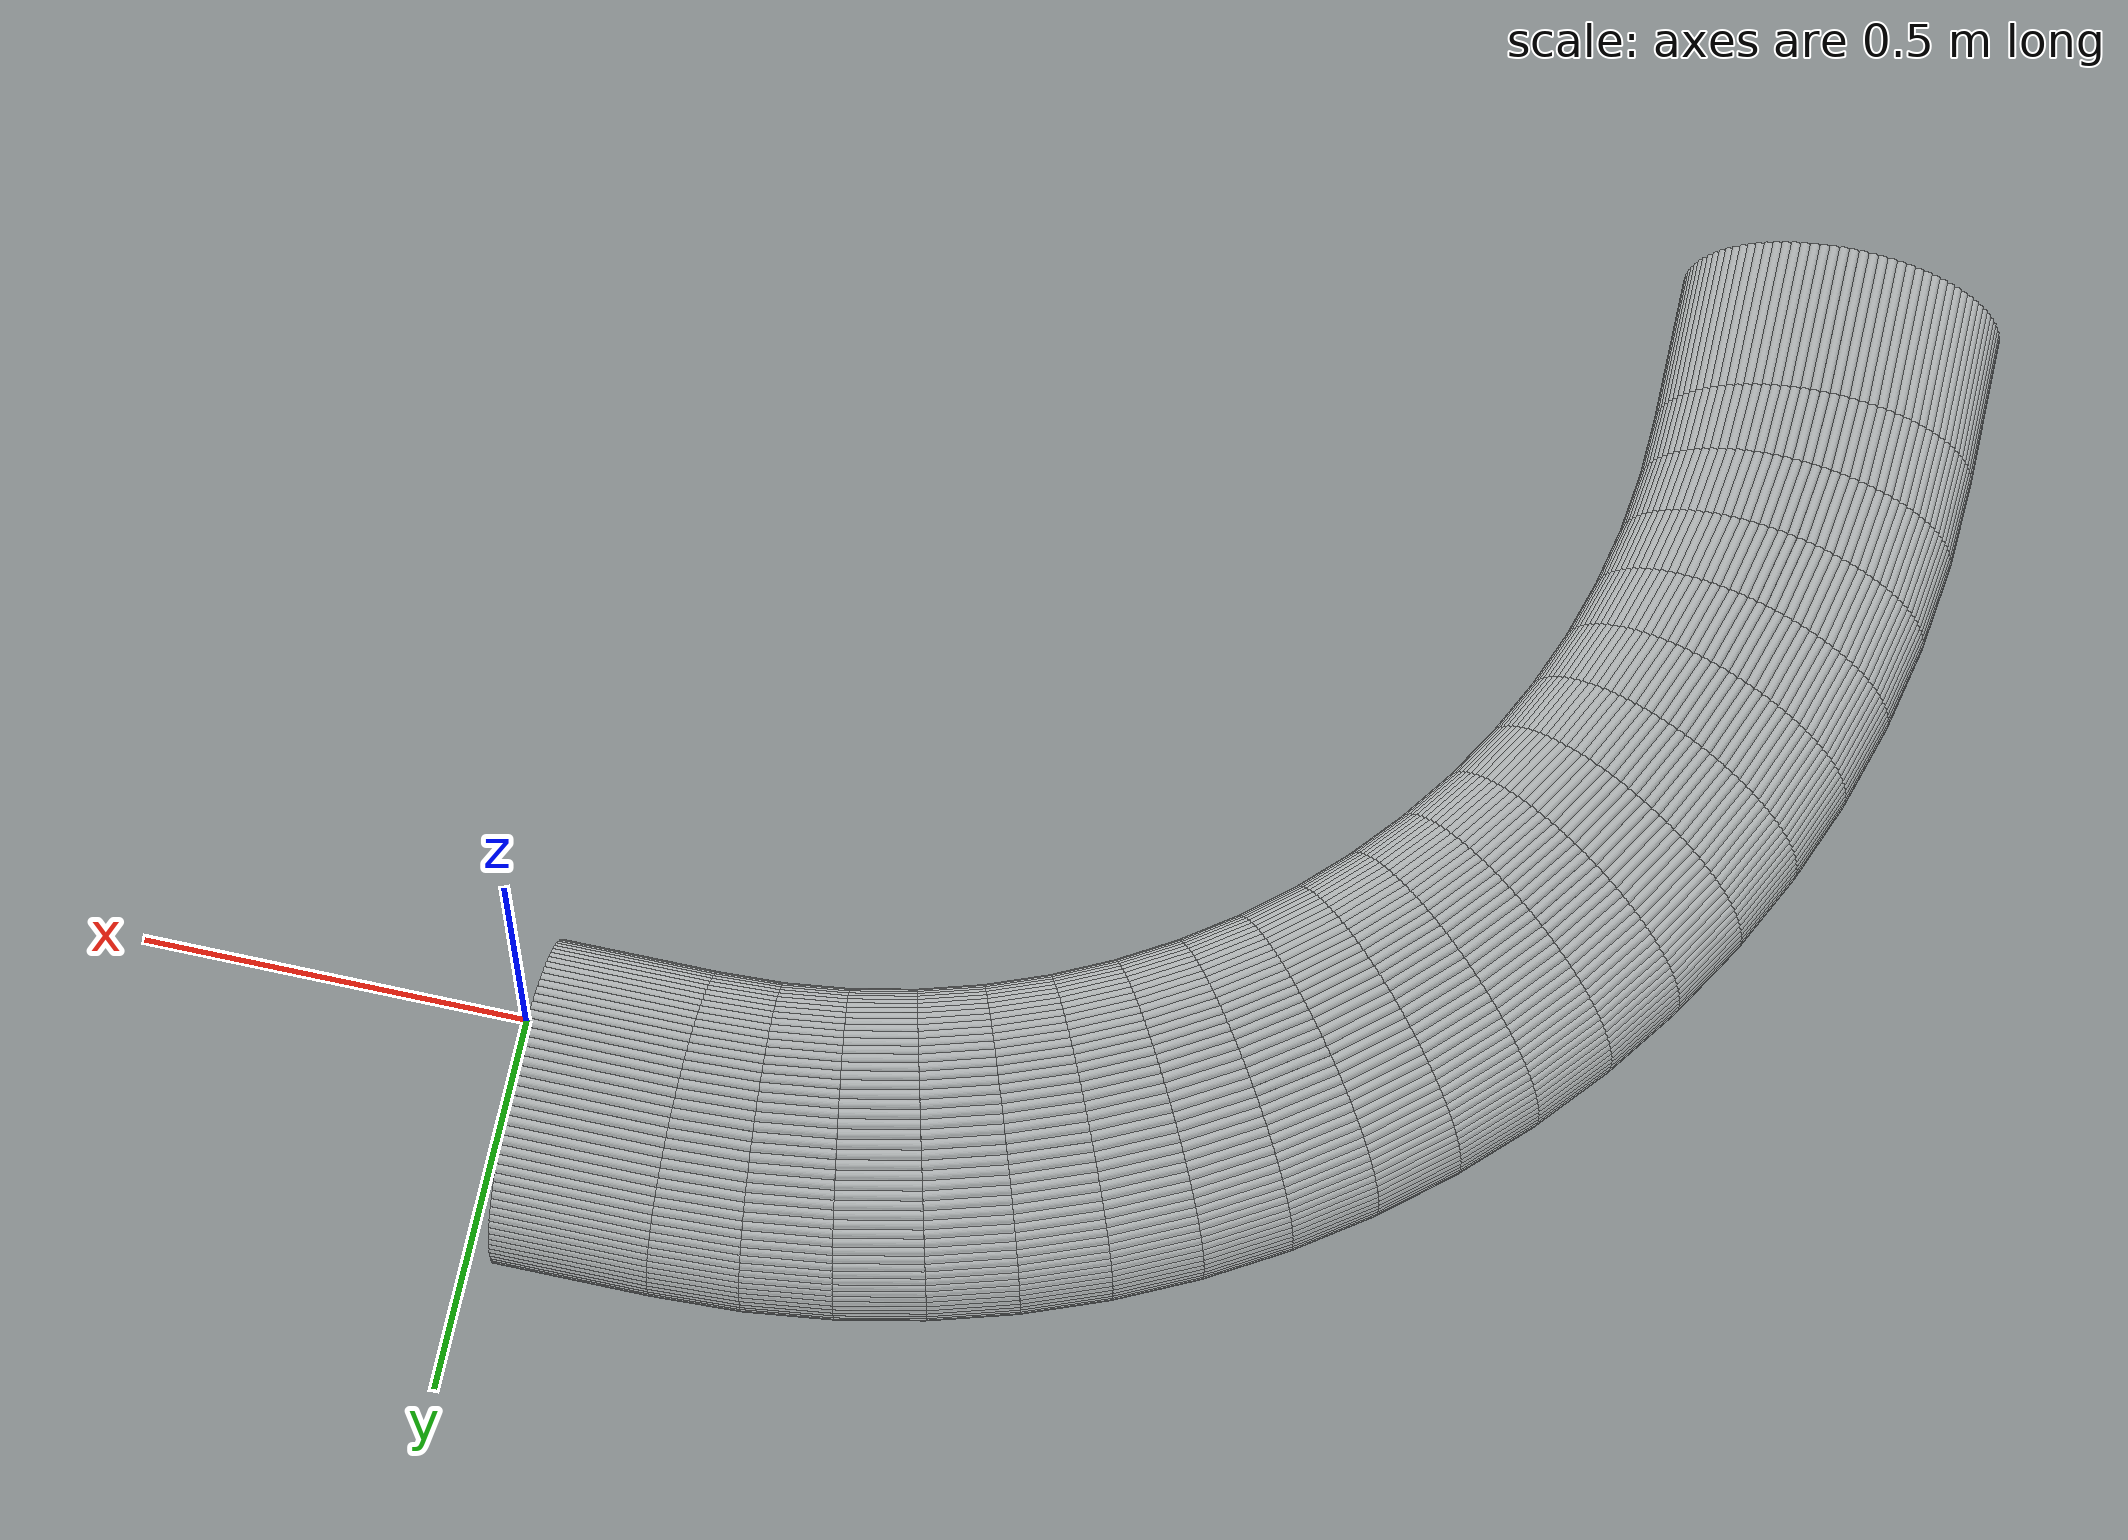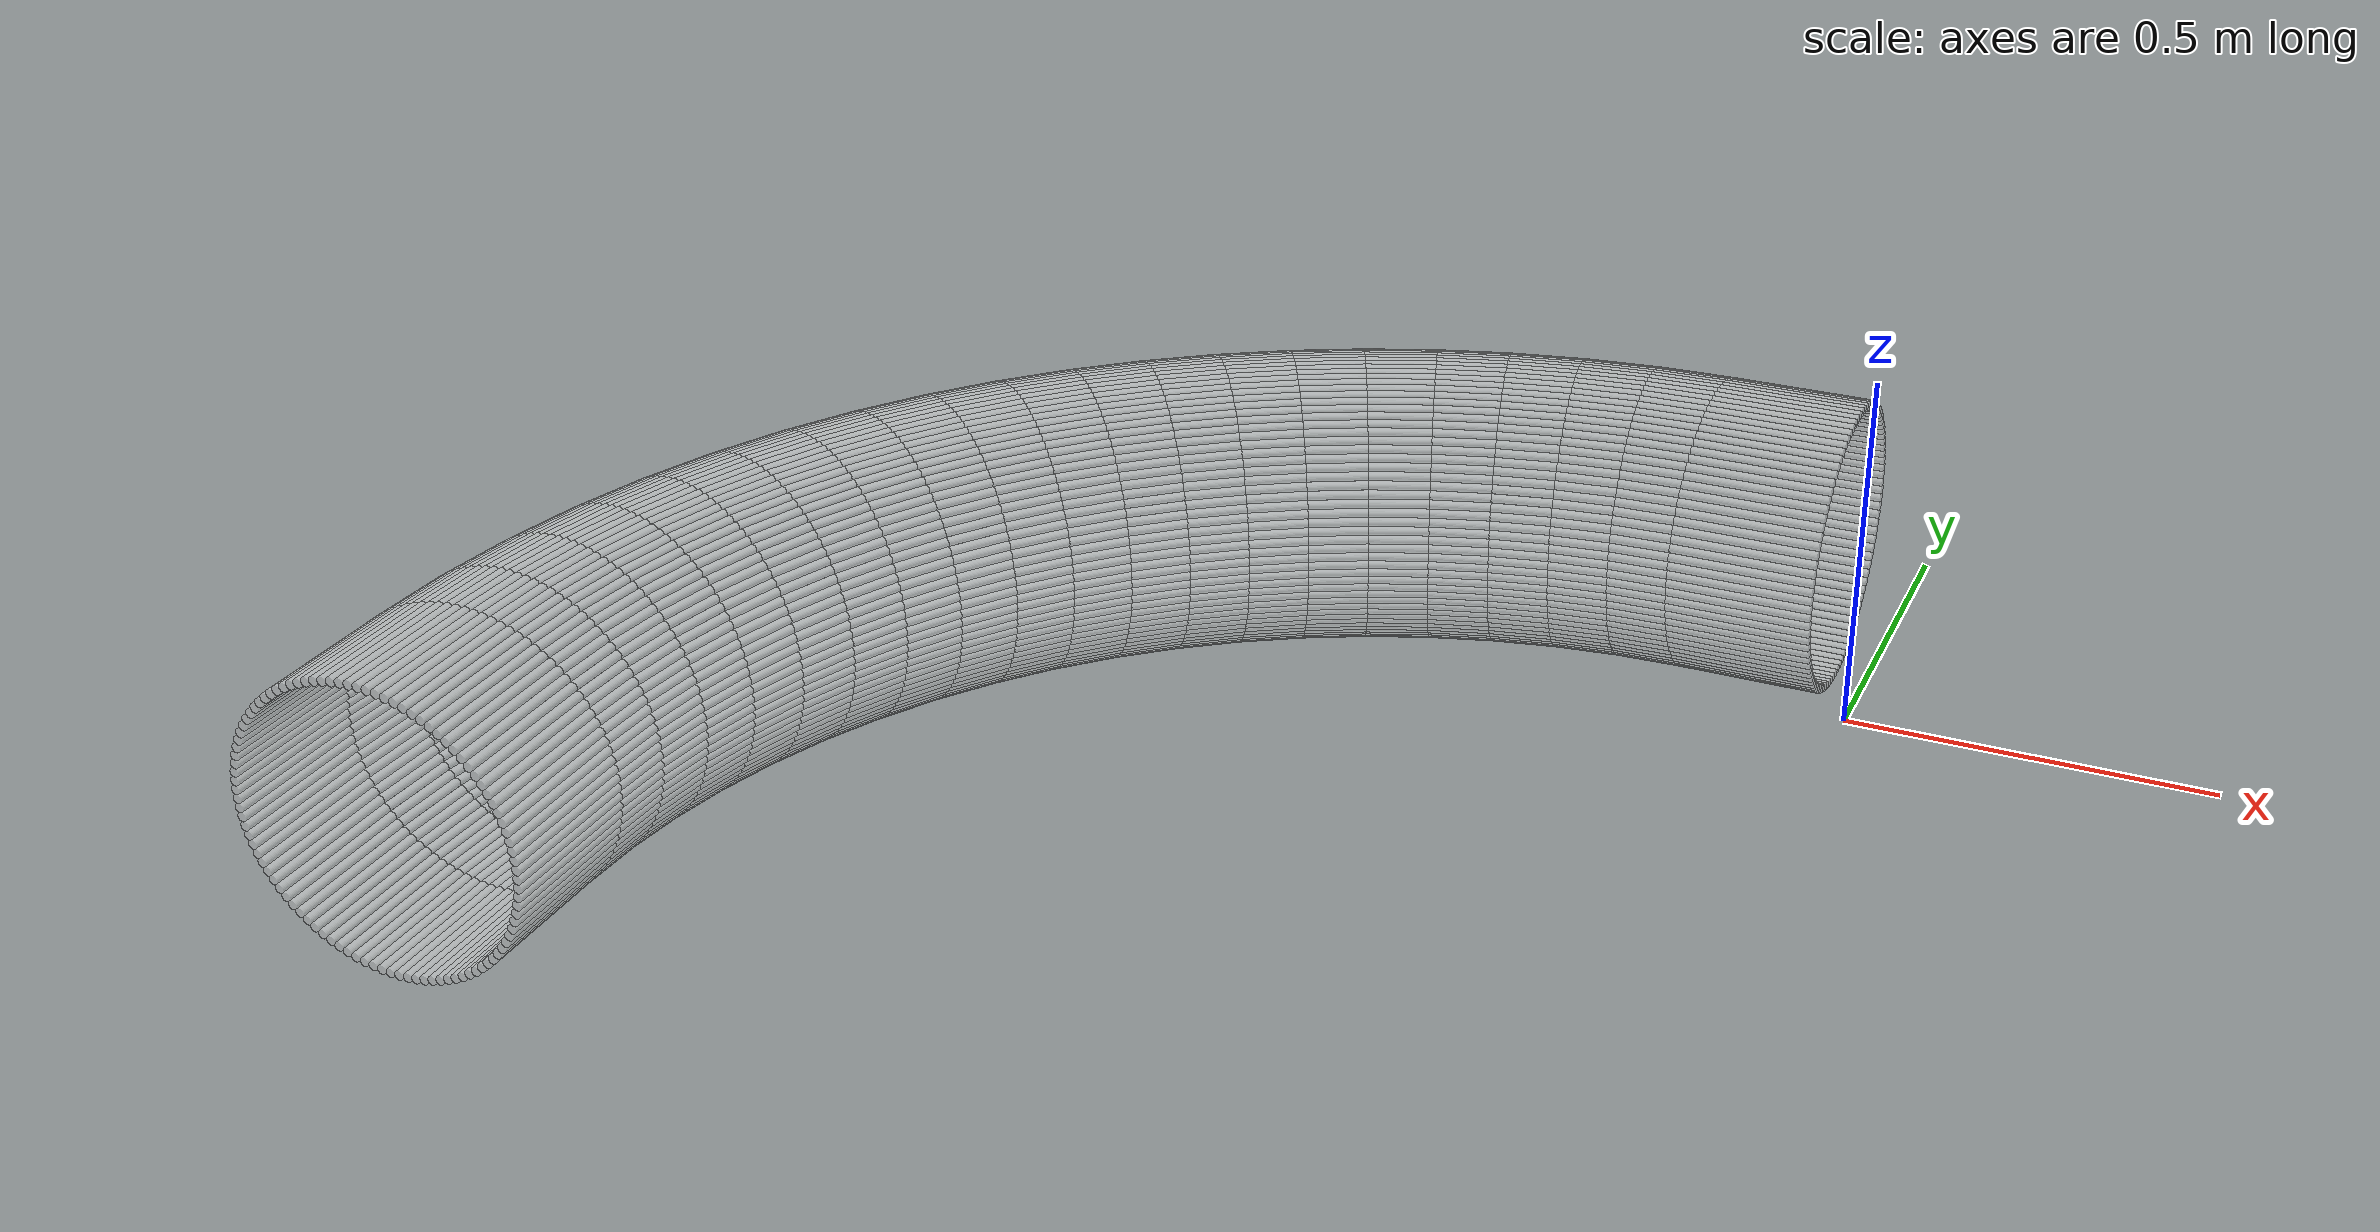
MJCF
<?xml version="1.0" encoding="utf-8"?>
<mujoco>
   <worldbody>
   <body pos="-0.25 -1.04 -0.02" euler="0 0 90">
      <geom euler=" 0 10 0 " fromto="1.4 -0.2 0.2 1.4 0 0.2" rgba="1 1 1 0.35"
            size="0.0062822"
            type="cylinder"/>
      <geom euler=" 0 20 0 " fromto="1.3996 -0.2 0.21256 1.3996 0 0.21256"
            rgba="1 1 1 0.35"
            size="0.0062822"
            type="cylinder"/>
      <geom euler=" 0 30 0 " fromto="1.3984 -0.2 0.22507 1.3984 0 0.22507"
            rgba="1 1 1 0.35"
            size="0.0062822"
            type="cylinder"/>
      <geom euler=" 0 40 0 " fromto="1.3965 -0.2 0.23748 1.3965 0 0.23748"
            rgba="1 1 1 0.35"
            size="0.0062822"
            type="cylinder"/>
      <geom euler=" 0 50 0 " fromto="1.3937 -0.2 0.24974 1.3937 0 0.24974"
            rgba="1 1 1 0.35"
            size="0.0062822"
            type="cylinder"/>
      <geom euler=" 0 60 0 " fromto="1.3902 -0.2 0.2618 1.3902 0 0.2618" rgba="1 1 1 0.35"
            size="0.0062822"
            type="cylinder"/>
      <geom euler=" 0 70 0 " fromto="1.386 -0.2 0.27362 1.386 0 0.27362" rgba="1 1 1 0.35"
            size="0.0062822"
            type="cylinder"/>
      <geom euler=" 0 80 0 " fromto="1.381 -0.2 0.28516 1.381 0 0.28516" rgba="1 1 1 0.35"
            size="0.0062822"
            type="cylinder"/>
      <geom euler=" 0 90 0 " fromto="1.3753 -0.2 0.29635 1.3753 0 0.29635"
            rgba="1 1 1 0.35"
            size="0.0062822"
            type="cylinder"/>
      <geom euler=" 0 100 0 " fromto="1.3689 -0.2 0.30717 1.3689 0 0.30717"
            rgba="1 1 1 0.35"
            size="0.0062822"
            type="cylinder"/>
      <geom euler=" 0 110 0 " fromto="1.3618 -0.2 0.31756 1.3618 0 0.31756"
            rgba="1 1 1 0.35"
            size="0.0062822"
            type="cylinder"/>
      <geom euler=" 0 120 0 " fromto="1.3541 -0.2 0.32748 1.3541 0 0.32748"
            rgba="1 1 1 0.35"
            size="0.0062822"
            type="cylinder"/>
      <geom euler=" 0 130 0 " fromto="1.3458 -0.2 0.33691 1.3458 0 0.33691"
            rgba="1 1 1 0.35"
            size="0.0062822"
            type="cylinder"/>
      <geom euler=" 0 140 0 " fromto="1.3369 -0.2 0.34579 1.3369 0 0.34579"
            rgba="1 1 1 0.35"
            size="0.0062822"
            type="cylinder"/>
      <geom euler=" 0 150 0 " fromto="1.3275 -0.2 0.3541 1.3275 0 0.3541" rgba="1 1 1 0.35"
            size="0.0062822"
            type="cylinder"/>
      <geom euler=" 0 160 0 " fromto="1.3176 -0.2 0.3618 1.3176 0 0.3618" rgba="1 1 1 0.35"
            size="0.0062822"
            type="cylinder"/>
      <geom euler=" 0 170 0 " fromto="1.3072 -0.2 0.36887 1.3072 0 0.36887"
            rgba="1 1 1 0.35"
            size="0.0062822"
            type="cylinder"/>
      <geom euler=" 0 180 0 " fromto="1.2964 -0.2 0.37526 1.2964 0 0.37526"
            rgba="1 1 1 0.35"
            size="0.0062822"
            type="cylinder"/>
      <geom euler=" 0 190 0 " fromto="1.2852 -0.2 0.38097 1.2852 0 0.38097"
            rgba="1 1 1 0.35"
            size="0.0062822"
            type="cylinder"/>
      <geom euler=" 0 200 0 " fromto="1.2736 -0.2 0.38596 1.2736 0 0.38596"
            rgba="1 1 1 0.35"
            size="0.0062822"
            type="cylinder"/>
      <geom euler=" 0 210 0 " fromto="1.2618 -0.2 0.39021 1.2618 0 0.39021"
            rgba="1 1 1 0.35"
            size="0.0062822"
            type="cylinder"/>
      <geom euler=" 0 220 0 " fromto="1.2497 -0.2 0.39372 1.2497 0 0.39372"
            rgba="1 1 1 0.35"
            size="0.0062822"
            type="cylinder"/>
      <geom euler=" 0 230 0 " fromto="1.2375 -0.2 0.39646 1.2375 0 0.39646"
            rgba="1 1 1 0.35"
            size="0.0062822"
            type="cylinder"/>
      <geom euler=" 0 240 0 " fromto="1.2251 -0.2 0.39842 1.2251 0 0.39842"
            rgba="1 1 1 0.35"
            size="0.0062822"
            type="cylinder"/>
      <geom euler=" 0 250 0 " fromto="1.2126 -0.2 0.39961 1.2126 0 0.39961"
            rgba="1 1 1 0.35"
            size="0.0062822"
            type="cylinder"/>
      <geom euler=" 0 260 0 " fromto="1.2 -0.2 0.4 1.2 0 0.4" rgba="1 1 1 0.35"
            size="0.0062822"
            type="cylinder"/>
      <geom euler=" 0 270 0 " fromto="1.1874 -0.2 0.39961 1.1874 0 0.39961"
            rgba="1 1 1 0.35"
            size="0.0062822"
            type="cylinder"/>
      <geom euler=" 0 280 0 " fromto="1.1749 -0.2 0.39842 1.1749 0 0.39842"
            rgba="1 1 1 0.35"
            size="0.0062822"
            type="cylinder"/>
      <geom euler=" 0 290 0 " fromto="1.1625 -0.2 0.39646 1.1625 0 0.39646"
            rgba="1 1 1 0.35"
            size="0.0062822"
            type="cylinder"/>
      <geom euler=" 0 300 0 " fromto="1.1503 -0.2 0.39372 1.1503 0 0.39372"
            rgba="1 1 1 0.35"
            size="0.0062822"
            type="cylinder"/>
      <geom euler=" 0 310 0 " fromto="1.1382 -0.2 0.39021 1.1382 0 0.39021"
            rgba="1 1 1 0.35"
            size="0.0062822"
            type="cylinder"/>
      <geom euler=" 0 320 0 " fromto="1.1264 -0.2 0.38596 1.1264 0 0.38596"
            rgba="1 1 1 0.35"
            size="0.0062822"
            type="cylinder"/>
      <geom euler=" 0 330 0 " fromto="1.1148 -0.2 0.38097 1.1148 0 0.38097"
            rgba="1 1 1 0.35"
            size="0.0062822"
            type="cylinder"/>
      <geom euler=" 0 340 0 " fromto="1.1036 -0.2 0.37526 1.1036 0 0.37526"
            rgba="1 1 1 0.35"
            size="0.0062822"
            type="cylinder"/>
      <geom euler=" 0 350 0 " fromto="1.0928 -0.2 0.36887 1.0928 0 0.36887"
            rgba="1 1 1 0.35"
            size="0.0062822"
            type="cylinder"/>
      <geom euler=" 0 360 0 " fromto="1.0824 -0.2 0.3618 1.0824 0 0.3618" rgba="1 1 1 0.35"
            size="0.0062822"
            type="cylinder"/>
      <geom euler=" 0 370 0 " fromto="1.0725 -0.2 0.3541 1.0725 0 0.3541" rgba="1 1 1 0.35"
            size="0.0062822"
            type="cylinder"/>
      <geom euler=" 0 380 0 " fromto="1.0631 -0.2 0.34579 1.0631 0 0.34579"
            rgba="1 1 1 0.35"
            size="0.0062822"
            type="cylinder"/>
      <geom euler=" 0 390 0 " fromto="1.0542 -0.2 0.33691 1.0542 0 0.33691"
            rgba="1 1 1 0.35"
            size="0.0062822"
            type="cylinder"/>
      <geom euler=" 0 400 0 " fromto="1.0459 -0.2 0.32748 1.0459 0 0.32748"
            rgba="1 1 1 0.35"
            size="0.0062822"
            type="cylinder"/>
      <geom euler=" 0 410 0 " fromto="1.0382 -0.2 0.31756 1.0382 0 0.31756"
            rgba="1 1 1 0.35"
            size="0.0062822"
            type="cylinder"/>
      <geom euler=" 0 420 0 " fromto="1.0311 -0.2 0.30717 1.0311 0 0.30717"
            rgba="1 1 1 0.35"
            size="0.0062822"
            type="cylinder"/>
      <geom euler=" 0 430 0 " fromto="1.0247 -0.2 0.29635 1.0247 0 0.29635"
            rgba="1 1 1 0.35"
            size="0.0062822"
            type="cylinder"/>
      <geom euler=" 0 440 0 " fromto="1.019 -0.2 0.28516 1.019 0 0.28516" rgba="1 1 1 0.35"
            size="0.0062822"
            type="cylinder"/>
      <geom euler=" 0 450 0 " fromto="1.014 -0.2 0.27362 1.014 0 0.27362" rgba="1 1 1 0.35"
            size="0.0062822"
            type="cylinder"/>
      <geom euler=" 0 460 0 " fromto="1.0098 -0.2 0.2618 1.0098 0 0.2618" rgba="1 1 1 0.35"
            size="0.0062822"
            type="cylinder"/>
      <geom euler=" 0 470 0 " fromto="1.0063 -0.2 0.24974 1.0063 0 0.24974"
            rgba="1 1 1 0.35"
            size="0.0062822"
            type="cylinder"/>
      <geom euler=" 0 480 0 " fromto="1.0035 -0.2 0.23748 1.0035 0 0.23748"
            rgba="1 1 1 0.35"
            size="0.0062822"
            type="cylinder"/>
      <geom euler=" 0 490 0 " fromto="1.0016 -0.2 0.22507 1.0016 0 0.22507"
            rgba="1 1 1 0.35"
            size="0.0062822"
            type="cylinder"/>
      <geom euler=" 0 500 0 " fromto="1.0004 -0.2 0.21256 1.0004 0 0.21256"
            rgba="1 1 1 0.35"
            size="0.0062822"
            type="cylinder"/>
      <geom euler=" 0 510 0 " fromto="1 -0.2 0.2 1 0 0.2" rgba="1 1 1 0.35"
            size="0.0062822"
            type="cylinder"/>
      <geom euler=" 0 520 0 " fromto="1.0004 -0.2 0.18744 1.0004 0 0.18744"
            rgba="1 1 1 0.35"
            size="0.0062822"
            type="cylinder"/>
      <geom euler=" 0 530 0 " fromto="1.0016 -0.2 0.17493 1.0016 0 0.17493"
            rgba="1 1 1 0.35"
            size="0.0062822"
            type="cylinder"/>
      <geom euler=" 0 540 0 " fromto="1.0035 -0.2 0.16252 1.0035 0 0.16252"
            rgba="1 1 1 0.35"
            size="0.0062822"
            type="cylinder"/>
      <geom euler=" 0 550 0 " fromto="1.0063 -0.2 0.15026 1.0063 0 0.15026"
            rgba="1 1 1 0.35"
            size="0.0062822"
            type="cylinder"/>
      <geom euler=" 0 560 0 " fromto="1.0098 -0.2 0.1382 1.0098 0 0.1382" rgba="1 1 1 0.35"
            size="0.0062822"
            type="cylinder"/>
      <geom euler=" 0 570 0 " fromto="1.014 -0.2 0.12638 1.014 0 0.12638" rgba="1 1 1 0.35"
            size="0.0062822"
            type="cylinder"/>
      <geom euler=" 0 580 0 " fromto="1.019 -0.2 0.11484 1.019 0 0.11484" rgba="1 1 1 0.35"
            size="0.0062822"
            type="cylinder"/>
      <geom euler=" 0 590 0 " fromto="1.0247 -0.2 0.10365 1.0247 0 0.10365"
            rgba="1 1 1 0.35"
            size="0.0062822"
            type="cylinder"/>
      <geom euler=" 0 600 0 " fromto="1.0311 -0.2 0.092835 1.0311 0 0.092835"
            rgba="1 1 1 0.35"
            size="0.0062822"
            type="cylinder"/>
      <geom euler=" 0 610 0 " fromto="1.0382 -0.2 0.082443 1.0382 0 0.082443"
            rgba="1 1 1 0.35"
            size="0.0062822"
            type="cylinder"/>
      <geom euler=" 0 620 0 " fromto="1.0459 -0.2 0.072515 1.0459 0 0.072515"
            rgba="1 1 1 0.35"
            size="0.0062822"
            type="cylinder"/>
      <geom euler=" 0 630 0 " fromto="1.0542 -0.2 0.063091 1.0542 0 0.063091"
            rgba="1 1 1 0.35"
            size="0.0062822"
            type="cylinder"/>
      <geom euler=" 0 640 0 " fromto="1.0631 -0.2 0.054206 1.0631 0 0.054206"
            rgba="1 1 1 0.35"
            size="0.0062822"
            type="cylinder"/>
      <geom euler=" 0 650 0 " fromto="1.0725 -0.2 0.045897 1.0725 0 0.045897"
            rgba="1 1 1 0.35"
            size="0.0062822"
            type="cylinder"/>
      <geom euler=" 0 660 0 " fromto="1.0824 -0.2 0.038197 1.0824 0 0.038197"
            rgba="1 1 1 0.35"
            size="0.0062822"
            type="cylinder"/>
      <geom euler=" 0 670 0 " fromto="1.0928 -0.2 0.031134 1.0928 0 0.031134"
            rgba="1 1 1 0.35"
            size="0.0062822"
            type="cylinder"/>
      <geom euler=" 0 680 0 " fromto="1.1036 -0.2 0.024739 1.1036 0 0.024739"
            rgba="1 1 1 0.35"
            size="0.0062822"
            type="cylinder"/>
      <geom euler=" 0 690 0 " fromto="1.1148 -0.2 0.019035 1.1148 0 0.019035"
            rgba="1 1 1 0.35"
            size="0.0062822"
            type="cylinder"/>
      <geom euler=" 0 700 0 " fromto="1.1264 -0.2 0.014045 1.1264 0 0.014045"
            rgba="1 1 1 0.35"
            size="0.0062822"
            type="cylinder"/>
      <geom euler=" 0 710 0 " fromto="1.1382 -0.2 0.0097887 1.1382 0 0.0097887"
            rgba="1 1 1 0.35"
            size="0.0062822"
            type="cylinder"/>
      <geom euler=" 0 720 0 " fromto="1.1503 -0.2 0.0062834 1.1503 0 0.0062834"
            rgba="1 1 1 0.35"
            size="0.0062822"
            type="cylinder"/>
      <geom euler=" 0 730 0 " fromto="1.1625 -0.2 0.0035425 1.1625 0 0.0035425"
            rgba="1 1 1 0.35"
            size="0.0062822"
            type="cylinder"/>
      <geom euler=" 0 740 0 " fromto="1.1749 -0.2 0.0015771 1.1749 0 0.0015771"
            rgba="1 1 1 0.35"
            size="0.0062822"
            type="cylinder"/>
      <geom euler=" 0 750 0 " fromto="1.1874 -0.2 0.00039465 1.1874 0 0.00039465"
            rgba="1 1 1 0.35"
            size="0.0062822"
            type="cylinder"/>
      <geom euler=" 0 760 0 " fromto="1.2 -0.2 0 1.2 0 0" rgba="1 1 1 0.35"
            size="0.0062822"
            type="cylinder"/>
      <geom euler=" 0 770 0 " fromto="1.2126 -0.2 0.00039465 1.2126 0 0.00039465"
            rgba="1 1 1 0.35"
            size="0.0062822"
            type="cylinder"/>
      <geom euler=" 0 780 0 " fromto="1.2251 -0.2 0.0015771 1.2251 0 0.0015771"
            rgba="1 1 1 0.35"
            size="0.0062822"
            type="cylinder"/>
      <geom euler=" 0 790 0 " fromto="1.2375 -0.2 0.0035425 1.2375 0 0.0035425"
            rgba="1 1 1 0.35"
            size="0.0062822"
            type="cylinder"/>
      <geom euler=" 0 800 0 " fromto="1.2497 -0.2 0.0062834 1.2497 0 0.0062834"
            rgba="1 1 1 0.35"
            size="0.0062822"
            type="cylinder"/>
      <geom euler=" 0 810 0 " fromto="1.2618 -0.2 0.0097887 1.2618 0 0.0097887"
            rgba="1 1 1 0.35"
            size="0.0062822"
            type="cylinder"/>
      <geom euler=" 0 820 0 " fromto="1.2736 -0.2 0.014045 1.2736 0 0.014045"
            rgba="1 1 1 0.35"
            size="0.0062822"
            type="cylinder"/>
      <geom euler=" 0 830 0 " fromto="1.2852 -0.2 0.019035 1.2852 0 0.019035"
            rgba="1 1 1 0.35"
            size="0.0062822"
            type="cylinder"/>
      <geom euler=" 0 840 0 " fromto="1.2964 -0.2 0.024739 1.2964 0 0.024739"
            rgba="1 1 1 0.35"
            size="0.0062822"
            type="cylinder"/>
      <geom euler=" 0 850 0 " fromto="1.3072 -0.2 0.031134 1.3072 0 0.031134"
            rgba="1 1 1 0.35"
            size="0.0062822"
            type="cylinder"/>
      <geom euler=" 0 860 0 " fromto="1.3176 -0.2 0.038197 1.3176 0 0.038197"
            rgba="1 1 1 0.35"
            size="0.0062822"
            type="cylinder"/>
      <geom euler=" 0 870 0 " fromto="1.3275 -0.2 0.045897 1.3275 0 0.045897"
            rgba="1 1 1 0.35"
            size="0.0062822"
            type="cylinder"/>
      <geom euler=" 0 880 0 " fromto="1.3369 -0.2 0.054206 1.3369 0 0.054206"
            rgba="1 1 1 0.35"
            size="0.0062822"
            type="cylinder"/>
      <geom euler=" 0 890 0 " fromto="1.3458 -0.2 0.063091 1.3458 0 0.063091"
            rgba="1 1 1 0.35"
            size="0.0062822"
            type="cylinder"/>
      <geom euler=" 0 900 0 " fromto="1.3541 -0.2 0.072515 1.3541 0 0.072515"
            rgba="1 1 1 0.35"
            size="0.0062822"
            type="cylinder"/>
      <geom euler=" 0 910 0 " fromto="1.3618 -0.2 0.082443 1.3618 0 0.082443"
            rgba="1 1 1 0.35"
            size="0.0062822"
            type="cylinder"/>
      <geom euler=" 0 920 0 " fromto="1.3689 -0.2 0.092835 1.3689 0 0.092835"
            rgba="1 1 1 0.35"
            size="0.0062822"
            type="cylinder"/>
      <geom euler=" 0 930 0 " fromto="1.3753 -0.2 0.10365 1.3753 0 0.10365"
            rgba="1 1 1 0.35"
            size="0.0062822"
            type="cylinder"/>
      <geom euler=" 0 940 0 " fromto="1.381 -0.2 0.11484 1.381 0 0.11484" rgba="1 1 1 0.35"
            size="0.0062822"
            type="cylinder"/>
      <geom euler=" 0 950 0 " fromto="1.386 -0.2 0.12638 1.386 0 0.12638" rgba="1 1 1 0.35"
            size="0.0062822"
            type="cylinder"/>
      <geom euler=" 0 960 0 " fromto="1.3902 -0.2 0.1382 1.3902 0 0.1382" rgba="1 1 1 0.35"
            size="0.0062822"
            type="cylinder"/>
      <geom euler=" 0 970 0 " fromto="1.3937 -0.2 0.15026 1.3937 0 0.15026"
            rgba="1 1 1 0.35"
            size="0.0062822"
            type="cylinder"/>
      <geom euler=" 0 980 0 " fromto="1.3965 -0.2 0.16252 1.3965 0 0.16252"
            rgba="1 1 1 0.35"
            size="0.0062822"
            type="cylinder"/>
      <geom euler=" 0 990 0 " fromto="1.3984 -0.2 0.17493 1.3984 0 0.17493"
            rgba="1 1 1 0.35"
            size="0.0062822"
            type="cylinder"/>
      <geom euler=" 0 1000 0 " fromto="1.3996 -0.2 0.18744 1.3996 0 0.18744"
            rgba="1 1 1 0.35"
            size="0.0062822"
            type="cylinder"/>
      <geom euler=" 0 10 0 " fromto="1.4 0 0.2 1.3952 0.11561 0.2" rgba="1 1 1 0.35"
            size="0.0062822"
            type="cylinder"/>
      <geom euler=" 0 20 0 " fromto="1.3996 0 0.21256 1.3948 0.11558 0.21256"
            rgba="1 1 1 0.35"
            size="0.0062822"
            type="cylinder"/>
      <geom euler=" 0 30 0 " fromto="1.3984 0 0.22507 1.3936 0.11548 0.22507"
            rgba="1 1 1 0.35"
            size="0.0062822"
            type="cylinder"/>
      <geom euler=" 0 40 0 " fromto="1.3965 0 0.23748 1.3917 0.11532 0.23748"
            rgba="1 1 1 0.35"
            size="0.0062822"
            type="cylinder"/>
      <geom euler=" 0 50 0 " fromto="1.3937 0 0.24974 1.389 0.11509 0.24974"
            rgba="1 1 1 0.35"
            size="0.0062822"
            type="cylinder"/>
      <geom euler=" 0 60 0 " fromto="1.3902 0 0.2618 1.3855 0.1148 0.2618"
            rgba="1 1 1 0.35"
            size="0.0062822"
            type="cylinder"/>
      <geom euler=" 0 70 0 " fromto="1.386 0 0.27362 1.3812 0.11445 0.27362"
            rgba="1 1 1 0.35"
            size="0.0062822"
            type="cylinder"/>
      <geom euler=" 0 80 0 " fromto="1.381 0 0.28516 1.3762 0.11404 0.28516"
            rgba="1 1 1 0.35"
            size="0.0062822"
            type="cylinder"/>
      <geom euler=" 0 90 0 " fromto="1.3753 0 0.29635 1.3706 0.11357 0.29635"
            rgba="1 1 1 0.35"
            size="0.0062822"
            type="cylinder"/>
      <geom euler=" 0 100 0 " fromto="1.3689 0 0.30717 1.3642 0.11304 0.30717"
            rgba="1 1 1 0.35"
            size="0.0062822"
            type="cylinder"/>
      <geom euler=" 0 110 0 " fromto="1.3618 0 0.31756 1.3572 0.11246 0.31756"
            rgba="1 1 1 0.35"
            size="0.0062822"
            type="cylinder"/>
      <geom euler=" 0 120 0 " fromto="1.3541 0 0.32748 1.3495 0.11182 0.32748"
            rgba="1 1 1 0.35"
            size="0.0062822"
            type="cylinder"/>
      <geom euler=" 0 130 0 " fromto="1.3458 0 0.33691 1.3412 0.11113 0.33691"
            rgba="1 1 1 0.35"
            size="0.0062822"
            type="cylinder"/>
      <geom euler=" 0 140 0 " fromto="1.3369 0 0.34579 1.3323 0.1104 0.34579"
            rgba="1 1 1 0.35"
            size="0.0062822"
            type="cylinder"/>
      <geom euler=" 0 150 0 " fromto="1.3275 0 0.3541 1.323 0.10962 0.3541"
            rgba="1 1 1 0.35"
            size="0.0062822"
            type="cylinder"/>
      <geom euler=" 0 160 0 " fromto="1.3176 0 0.3618 1.3131 0.1088 0.3618"
            rgba="1 1 1 0.35"
            size="0.0062822"
            type="cylinder"/>
      <geom euler=" 0 170 0 " fromto="1.3072 0 0.36887 1.3027 0.10794 0.36887"
            rgba="1 1 1 0.35"
            size="0.0062822"
            type="cylinder"/>
      <geom euler=" 0 180 0 " fromto="1.2964 0 0.37526 1.2919 0.10705 0.37526"
            rgba="1 1 1 0.35"
            size="0.0062822"
            type="cylinder"/>
      <geom euler=" 0 190 0 " fromto="1.2852 0 0.38097 1.2808 0.10613 0.38097"
            rgba="1 1 1 0.35"
            size="0.0062822"
            type="cylinder"/>
      <geom euler=" 0 200 0 " fromto="1.2736 0 0.38596 1.2693 0.10518 0.38596"
            rgba="1 1 1 0.35"
            size="0.0062822"
            type="cylinder"/>
      <geom euler=" 0 210 0 " fromto="1.2618 0 0.39021 1.2575 0.1042 0.39021"
            rgba="1 1 1 0.35"
            size="0.0062822"
            type="cylinder"/>
      <geom euler=" 0 220 0 " fromto="1.2497 0 0.39372 1.2455 0.1032 0.39372"
            rgba="1 1 1 0.35"
            size="0.0062822"
            type="cylinder"/>
      <geom euler=" 0 230 0 " fromto="1.2375 0 0.39646 1.2332 0.10219 0.39646"
            rgba="1 1 1 0.35"
            size="0.0062822"
            type="cylinder"/>
      <geom euler=" 0 240 0 " fromto="1.2251 0 0.39842 1.2209 0.10117 0.39842"
            rgba="1 1 1 0.35"
            size="0.0062822"
            type="cylinder"/>
      <geom euler=" 0 250 0 " fromto="1.2126 0 0.39961 1.2084 0.10013 0.39961"
            rgba="1 1 1 0.35"
            size="0.0062822"
            type="cylinder"/>
      <geom euler=" 0 260 0 " fromto="1.2 0 0.4 1.1959 0.099095 0.4" rgba="1 1 1 0.35"
            size="0.0062822"
            type="cylinder"/>
      <geom euler=" 0 270 0 " fromto="1.1874 0 0.39961 1.1834 0.098058 0.39961"
            rgba="1 1 1 0.35"
            size="0.0062822"
            type="cylinder"/>
      <geom euler=" 0 280 0 " fromto="1.1749 0 0.39842 1.1709 0.097025 0.39842"
            rgba="1 1 1 0.35"
            size="0.0062822"
            type="cylinder"/>
      <geom euler=" 0 290 0 " fromto="1.1625 0 0.39646 1.1586 0.096 0.39646"
            rgba="1 1 1 0.35"
            size="0.0062822"
            type="cylinder"/>
      <geom euler=" 0 300 0 " fromto="1.1503 0 0.39372 1.1463 0.094988 0.39372"
            rgba="1 1 1 0.35"
            size="0.0062822"
            type="cylinder"/>
      <geom euler=" 0 310 0 " fromto="1.1382 0 0.39021 1.1343 0.093992 0.39021"
            rgba="1 1 1 0.35"
            size="0.0062822"
            type="cylinder"/>
      <geom euler=" 0 320 0 " fromto="1.1264 0 0.38596 1.1225 0.093015 0.38596"
            rgba="1 1 1 0.35"
            size="0.0062822"
            type="cylinder"/>
      <geom euler=" 0 330 0 " fromto="1.1148 0 0.38097 1.111 0.092063 0.38097"
            rgba="1 1 1 0.35"
            size="0.0062822"
            type="cylinder"/>
      <geom euler=" 0 340 0 " fromto="1.1036 0 0.37526 1.0999 0.091139 0.37526"
            rgba="1 1 1 0.35"
            size="0.0062822"
            type="cylinder"/>
      <geom euler=" 0 350 0 " fromto="1.0928 0 0.36887 1.0891 0.090246 0.36887"
            rgba="1 1 1 0.35"
            size="0.0062822"
            type="cylinder"/>
      <geom euler=" 0 360 0 " fromto="1.0824 0 0.3618 1.0787 0.089387 0.3618"
            rgba="1 1 1 0.35"
            size="0.0062822"
            type="cylinder"/>
      <geom euler=" 0 370 0 " fromto="1.0725 0 0.3541 1.0689 0.088568 0.3541"
            rgba="1 1 1 0.35"
            size="0.0062822"
            type="cylinder"/>
      <geom euler=" 0 380 0 " fromto="1.0631 0 0.34579 1.0595 0.087789 0.34579"
            rgba="1 1 1 0.35"
            size="0.0062822"
            type="cylinder"/>
      <geom euler=" 0 390 0 " fromto="1.0542 0 0.33691 1.0506 0.087056 0.33691"
            rgba="1 1 1 0.35"
            size="0.0062822"
            type="cylinder"/>
      <geom euler=" 0 400 0 " fromto="1.0459 0 0.32748 1.0423 0.08637 0.32748"
            rgba="1 1 1 0.35"
            size="0.0062822"
            type="cylinder"/>
      <geom euler=" 0 410 0 " fromto="1.0382 0 0.31756 1.0347 0.085734 0.31756"
            rgba="1 1 1 0.35"
            size="0.0062822"
            type="cylinder"/>
      <geom euler=" 0 420 0 " fromto="1.0311 0 0.30717 1.0276 0.08515 0.30717"
            rgba="1 1 1 0.35"
            size="0.0062822"
            type="cylinder"/>
      <geom euler=" 0 430 0 " fromto="1.0247 0 0.29635 1.0212 0.084622 0.29635"
            rgba="1 1 1 0.35"
            size="0.0062822"
            type="cylinder"/>
      <geom euler=" 0 440 0 " fromto="1.019 0 0.28516 1.0156 0.084151 0.28516"
            rgba="1 1 1 0.35"
            size="0.0062822"
            type="cylinder"/>
      <geom euler=" 0 450 0 " fromto="1.014 0 0.27362 1.0106 0.083739 0.27362"
            rgba="1 1 1 0.35"
            size="0.0062822"
            type="cylinder"/>
      <geom euler=" 0 460 0 " fromto="1.0098 0 0.2618 1.0063 0.083388 0.2618"
            rgba="1 1 1 0.35"
            size="0.0062822"
            type="cylinder"/>
      <geom euler=" 0 470 0 " fromto="1.0063 0 0.24974 1.0028 0.083098 0.24974"
            rgba="1 1 1 0.35"
            size="0.0062822"
            type="cylinder"/>
      <geom euler=" 0 480 0 " fromto="1.0035 0 0.23748 1.0001 0.082872 0.23748"
            rgba="1 1 1 0.35"
            size="0.0062822"
            type="cylinder"/>
      <geom euler=" 0 490 0 " fromto="1.0016 0 0.22507 0.99816 0.08271 0.22507"
            rgba="1 1 1 0.35"
            size="0.0062822"
            type="cylinder"/>
      <geom euler=" 0 500 0 " fromto="1.0004 0 0.21256 0.99698 0.082612 0.21256"
            rgba="1 1 1 0.35"
            size="0.0062822"
            type="cylinder"/>
      <geom euler=" 0 510 0 " fromto="1 0 0.2 0.99658 0.082579 0.2" rgba="1 1 1 0.35"
            size="0.0062822"
            type="cylinder"/>
      <geom euler=" 0 520 0 " fromto="1.0004 0 0.18744 0.99698 0.082612 0.18744"
            rgba="1 1 1 0.35"
            size="0.0062822"
            type="cylinder"/>
      <geom euler=" 0 530 0 " fromto="1.0016 0 0.17493 0.99816 0.08271 0.17493"
            rgba="1 1 1 0.35"
            size="0.0062822"
            type="cylinder"/>
      <geom euler=" 0 540 0 " fromto="1.0035 0 0.16252 1.0001 0.082872 0.16252"
            rgba="1 1 1 0.35"
            size="0.0062822"
            type="cylinder"/>
      <geom euler=" 0 550 0 " fromto="1.0063 0 0.15026 1.0028 0.083098 0.15026"
            rgba="1 1 1 0.35"
            size="0.0062822"
            type="cylinder"/>
      <geom euler=" 0 560 0 " fromto="1.0098 0 0.1382 1.0063 0.083388 0.1382"
            rgba="1 1 1 0.35"
            size="0.0062822"
            type="cylinder"/>
      <geom euler=" 0 570 0 " fromto="1.014 0 0.12638 1.0106 0.083739 0.12638"
            rgba="1 1 1 0.35"
            size="0.0062822"
            type="cylinder"/>
      <geom euler=" 0 580 0 " fromto="1.019 0 0.11484 1.0156 0.084151 0.11484"
            rgba="1 1 1 0.35"
            size="0.0062822"
            type="cylinder"/>
      <geom euler=" 0 590 0 " fromto="1.0247 0 0.10365 1.0212 0.084622 0.10365"
            rgba="1 1 1 0.35"
            size="0.0062822"
            type="cylinder"/>
      <geom euler=" 0 600 0 " fromto="1.0311 0 0.092835 1.0276 0.08515 0.092835"
            rgba="1 1 1 0.35"
            size="0.0062822"
            type="cylinder"/>
      <geom euler=" 0 610 0 " fromto="1.0382 0 0.082443 1.0347 0.085734 0.082443"
            rgba="1 1 1 0.35"
            size="0.0062822"
            type="cylinder"/>
      <geom euler=" 0 620 0 " fromto="1.0459 0 0.072515 1.0423 0.08637 0.072515"
            rgba="1 1 1 0.35"
            size="0.0062822"
            type="cylinder"/>
      <geom euler=" 0 630 0 " fromto="1.0542 0 0.063091 1.0506 0.087056 0.063091"
            rgba="1 1 1 0.35"
            size="0.0062822"
            type="cylinder"/>
      <geom euler=" 0 640 0 " fromto="1.0631 0 0.054206 1.0595 0.087789 0.054206"
            rgba="1 1 1 0.35"
            size="0.0062822"
            type="cylinder"/>
      <geom euler=" 0 650 0 " fromto="1.0725 0 0.045897 1.0689 0.088568 0.045897"
            rgba="1 1 1 0.35"
            size="0.0062822"
            type="cylinder"/>
      <geom euler=" 0 660 0 " fromto="1.0824 0 0.038197 1.0787 0.089387 0.038197"
            rgba="1 1 1 0.35"
            size="0.0062822"
            type="cylinder"/>
      <geom euler=" 0 670 0 " fromto="1.0928 0 0.031134 1.0891 0.090246 0.031134"
            rgba="1 1 1 0.35"
            size="0.0062822"
            type="cylinder"/>
      <geom euler=" 0 680 0 " fromto="1.1036 0 0.024739 1.0999 0.091139 0.024739"
            rgba="1 1 1 0.35"
            size="0.0062822"
            type="cylinder"/>
      <geom euler=" 0 690 0 " fromto="1.1148 0 0.019035 1.111 0.092063 0.019035"
            rgba="1 1 1 0.35"
            size="0.0062822"
            type="cylinder"/>
      <geom euler=" 0 700 0 " fromto="1.1264 0 0.014045 1.1225 0.093015 0.014045"
            rgba="1 1 1 0.35"
            size="0.0062822"
            type="cylinder"/>
      <geom euler=" 0 710 0 " fromto="1.1382 0 0.0097887 1.1343 0.093992 0.0097887"
            rgba="1 1 1 0.35"
            size="0.0062822"
            type="cylinder"/>
      <geom euler=" 0 720 0 " fromto="1.1503 0 0.0062834 1.1463 0.094988 0.0062834"
            rgba="1 1 1 0.35"
            size="0.0062822"
            type="cylinder"/>
      <geom euler=" 0 730 0 " fromto="1.1625 0 0.0035425 1.1586 0.096 0.0035425"
            rgba="1 1 1 0.35"
            size="0.0062822"
            type="cylinder"/>
      <geom euler=" 0 740 0 " fromto="1.1749 0 0.0015771 1.1709 0.097025 0.0015771"
            rgba="1 1 1 0.35"
            size="0.0062822"
            type="cylinder"/>
      <geom euler=" 0 750 0 " fromto="1.1874 0 0.00039465 1.1834 0.098058 0.00039465"
            rgba="1 1 1 0.35"
            size="0.0062822"
            type="cylinder"/>
      <geom euler=" 0 760 0 " fromto="1.2 0 0 1.1959 0.099095 0" rgba="1 1 1 0.35"
            size="0.0062822"
            type="cylinder"/>
      <geom euler=" 0 770 0 " fromto="1.2126 0 0.00039465 1.2084 0.10013 0.00039465"
            rgba="1 1 1 0.35"
            size="0.0062822"
            type="cylinder"/>
      <geom euler=" 0 780 0 " fromto="1.2251 0 0.0015771 1.2209 0.10117 0.0015771"
            rgba="1 1 1 0.35"
            size="0.0062822"
            type="cylinder"/>
      <geom euler=" 0 790 0 " fromto="1.2375 0 0.0035425 1.2332 0.10219 0.0035425"
            rgba="1 1 1 0.35"
            size="0.0062822"
            type="cylinder"/>
      <geom euler=" 0 800 0 " fromto="1.2497 0 0.0062834 1.2455 0.1032 0.0062834"
            rgba="1 1 1 0.35"
            size="0.0062822"
            type="cylinder"/>
      <geom euler=" 0 810 0 " fromto="1.2618 0 0.0097887 1.2575 0.1042 0.0097887"
            rgba="1 1 1 0.35"
            size="0.0062822"
            type="cylinder"/>
      <geom euler=" 0 820 0 " fromto="1.2736 0 0.014045 1.2693 0.10518 0.014045"
            rgba="1 1 1 0.35"
            size="0.0062822"
            type="cylinder"/>
      <geom euler=" 0 830 0 " fromto="1.2852 0 0.019035 1.2808 0.10613 0.019035"
            rgba="1 1 1 0.35"
            size="0.0062822"
            type="cylinder"/>
      <geom euler=" 0 840 0 " fromto="1.2964 0 0.024739 1.2919 0.10705 0.024739"
            rgba="1 1 1 0.35"
            size="0.0062822"
            type="cylinder"/>
      <geom euler=" 0 850 0 " fromto="1.3072 0 0.031134 1.3027 0.10794 0.031134"
            rgba="1 1 1 0.35"
            size="0.0062822"
            type="cylinder"/>
      <geom euler=" 0 860 0 " fromto="1.3176 0 0.038197 1.3131 0.1088 0.038197"
            rgba="1 1 1 0.35"
            size="0.0062822"
            type="cylinder"/>
      <geom euler=" 0 870 0 " fromto="1.3275 0 0.045897 1.323 0.10962 0.045897"
            rgba="1 1 1 0.35"
            size="0.0062822"
            type="cylinder"/>
      <geom euler=" 0 880 0 " fromto="1.3369 0 0.054206 1.3323 0.1104 0.054206"
            rgba="1 1 1 0.35"
            size="0.0062822"
            type="cylinder"/>
      <geom euler=" 0 890 0 " fromto="1.3458 0 0.063091 1.3412 0.11113 0.063091"
            rgba="1 1 1 0.35"
            size="0.0062822"
            type="cylinder"/>
      <geom euler=" 0 900 0 " fromto="1.3541 0 0.072515 1.3495 0.11182 0.072515"
            rgba="1 1 1 0.35"
            size="0.0062822"
            type="cylinder"/>
      <geom euler=" 0 910 0 " fromto="1.3618 0 0.082443 1.3572 0.11246 0.082443"
            rgba="1 1 1 0.35"
            size="0.0062822"
            type="cylinder"/>
      <geom euler=" 0 920 0 " fromto="1.3689 0 0.092835 1.3642 0.11304 0.092835"
            rgba="1 1 1 0.35"
            size="0.0062822"
            type="cylinder"/>
      <geom euler=" 0 930 0 " fromto="1.3753 0 0.10365 1.3706 0.11357 0.10365"
            rgba="1 1 1 0.35"
            size="0.0062822"
            type="cylinder"/>
      <geom euler=" 0 940 0 " fromto="1.381 0 0.11484 1.3762 0.11404 0.11484"
            rgba="1 1 1 0.35"
            size="0.0062822"
            type="cylinder"/>
      <geom euler=" 0 950 0 " fromto="1.386 0 0.12638 1.3812 0.11445 0.12638"
            rgba="1 1 1 0.35"
            size="0.0062822"
            type="cylinder"/>
      <geom euler=" 0 960 0 " fromto="1.3902 0 0.1382 1.3855 0.1148 0.1382"
            rgba="1 1 1 0.35"
            size="0.0062822"
            type="cylinder"/>
      <geom euler=" 0 970 0 " fromto="1.3937 0 0.15026 1.389 0.11509 0.15026"
            rgba="1 1 1 0.35"
            size="0.0062822"
            type="cylinder"/>
      <geom euler=" 0 980 0 " fromto="1.3965 0 0.16252 1.3917 0.11532 0.16252"
            rgba="1 1 1 0.35"
            size="0.0062822"
            type="cylinder"/>
      <geom euler=" 0 990 0 " fromto="1.3984 0 0.17493 1.3936 0.11548 0.17493"
            rgba="1 1 1 0.35"
            size="0.0062822"
            type="cylinder"/>
      <geom euler=" 0 1000 0 " fromto="1.3996 0 0.18744 1.3948 0.11558 0.18744"
            rgba="1 1 1 0.35"
            size="0.0062822"
            type="cylinder"/>
      <geom euler=" 0 10 0 " fromto="1.3952 0.11561 0.2 1.3809 0.23043 0.2"
            rgba="1 1 1 0.35"
            size="0.0062822"
            type="cylinder"/>
      <geom euler=" 0 20 0 " fromto="1.3948 0.11558 0.21256 1.3805 0.23037 0.21256"
            rgba="1 1 1 0.35"
            size="0.0062822"
            type="cylinder"/>
      <geom euler=" 0 30 0 " fromto="1.3936 0.11548 0.22507 1.3794 0.23017 0.22507"
            rgba="1 1 1 0.35"
            size="0.0062822"
            type="cylinder"/>
      <geom euler=" 0 40 0 " fromto="1.3917 0.11532 0.23748 1.3774 0.22985 0.23748"
            rgba="1 1 1 0.35"
            size="0.0062822"
            type="cylinder"/>
      <geom euler=" 0 50 0 " fromto="1.389 0.11509 0.24974 1.3747 0.2294 0.24974"
            rgba="1 1 1 0.35"
            size="0.0062822"
            type="cylinder"/>
      <geom euler=" 0 60 0 " fromto="1.3855 0.1148 0.2618 1.3713 0.22882 0.2618"
            rgba="1 1 1 0.35"
            size="0.0062822"
            type="cylinder"/>
      <geom euler=" 0 70 0 " fromto="1.3812 0.11445 0.27362 1.3671 0.22812 0.27362"
            rgba="1 1 1 0.35"
            size="0.0062822"
            type="cylinder"/>
      <geom euler=" 0 80 0 " fromto="1.3762 0.11404 0.28516 1.3621 0.2273 0.28516"
            rgba="1 1 1 0.35"
            size="0.0062822"
            type="cylinder"/>
      <geom euler=" 0 90 0 " fromto="1.3706 0.11357 0.29635 1.3565 0.22636 0.29635"
            rgba="1 1 1 0.35"
            size="0.0062822"
            type="cylinder"/>
      <geom euler=" 0 100 0 " fromto="1.3642 0.11304 0.30717 1.3502 0.22531 0.30717"
            rgba="1 1 1 0.35"
            size="0.0062822"
            type="cylinder"/>
      <geom euler=" 0 110 0 " fromto="1.3572 0.11246 0.31756 1.3432 0.22415 0.31756"
            rgba="1 1 1 0.35"
            size="0.0062822"
            type="cylinder"/>
      <geom euler=" 0 120 0 " fromto="1.3495 0.11182 0.32748 1.3356 0.22288 0.32748"
            rgba="1 1 1 0.35"
            size="0.0062822"
            type="cylinder"/>
      <geom euler=" 0 130 0 " fromto="1.3412 0.11113 0.33691 1.3274 0.22151 0.33691"
            rgba="1 1 1 0.35"
            size="0.0062822"
            type="cylinder"/>
      <geom euler=" 0 140 0 " fromto="1.3323 0.1104 0.34579 1.3187 0.22005 0.34579"
            rgba="1 1 1 0.35"
            size="0.0062822"
            type="cylinder"/>
      <geom euler=" 0 150 0 " fromto="1.323 0.10962 0.3541 1.3094 0.2185 0.3541"
            rgba="1 1 1 0.35"
            size="0.0062822"
            type="cylinder"/>
      <geom euler=" 0 160 0 " fromto="1.3131 0.1088 0.3618 1.2996 0.21686 0.3618"
            rgba="1 1 1 0.35"
            size="0.0062822"
            type="cylinder"/>
      <geom euler=" 0 170 0 " fromto="1.3027 0.10794 0.36887 1.2893 0.21515 0.36887"
            rgba="1 1 1 0.35"
            size="0.0062822"
            type="cylinder"/>
      <geom euler=" 0 180 0 " fromto="1.2919 0.10705 0.37526 1.2787 0.21337 0.37526"
            rgba="1 1 1 0.35"
            size="0.0062822"
            type="cylinder"/>
      <geom euler=" 0 190 0 " fromto="1.2808 0.10613 0.38097 1.2676 0.21153 0.38097"
            rgba="1 1 1 0.35"
            size="0.0062822"
            type="cylinder"/>
      <geom euler=" 0 200 0 " fromto="1.2693 0.10518 0.38596 1.2563 0.20963 0.38596"
            rgba="1 1 1 0.35"
            size="0.0062822"
            type="cylinder"/>
      <geom euler=" 0 210 0 " fromto="1.2575 0.1042 0.39021 1.2446 0.20769 0.39021"
            rgba="1 1 1 0.35"
            size="0.0062822"
            type="cylinder"/>
      <geom euler=" 0 220 0 " fromto="1.2455 0.1032 0.39372 1.2327 0.2057 0.39372"
            rgba="1 1 1 0.35"
            size="0.0062822"
            type="cylinder"/>
      <geom euler=" 0 230 0 " fromto="1.2332 0.10219 0.39646 1.2206 0.20368 0.39646"
            rgba="1 1 1 0.35"
            size="0.0062822"
            type="cylinder"/>
      <geom euler=" 0 240 0 " fromto="1.2209 0.10117 0.39842 1.2084 0.20164 0.39842"
            rgba="1 1 1 0.35"
            size="0.0062822"
            type="cylinder"/>
      <geom euler=" 0 250 0 " fromto="1.2084 0.10013 0.39961 1.196 0.19958 0.39961"
            rgba="1 1 1 0.35"
            size="0.0062822"
            type="cylinder"/>
      <geom euler=" 0 260 0 " fromto="1.1959 0.099095 0.4 1.1836 0.19751 0.4"
            rgba="1 1 1 0.35"
            size="0.0062822"
            type="cylinder"/>
      <geom euler=" 0 270 0 " fromto="1.1834 0.098058 0.39961 1.1712 0.19545 0.39961"
            rgba="1 1 1 0.35"
            size="0.0062822"
            type="cylinder"/>
      <geom euler=" 0 280 0 " fromto="1.1709 0.097025 0.39842 1.1589 0.19339 0.39842"
            rgba="1 1 1 0.35"
            size="0.0062822"
            type="cylinder"/>
      <geom euler=" 0 290 0 " fromto="1.1586 0.096 0.39646 1.1467 0.19135 0.39646"
            rgba="1 1 1 0.35"
            size="0.0062822"
            type="cylinder"/>
      <geom euler=" 0 300 0 " fromto="1.1463 0.094988 0.39372 1.1346 0.18933 0.39372"
            rgba="1 1 1 0.35"
            size="0.0062822"
            type="cylinder"/>
      <geom euler=" 0 310 0 " fromto="1.1343 0.093992 0.39021 1.1227 0.18734 0.39021"
            rgba="1 1 1 0.35"
            size="0.0062822"
            type="cylinder"/>
      <geom euler=" 0 320 0 " fromto="1.1225 0.093015 0.38596 1.111 0.1854 0.38596"
            rgba="1 1 1 0.35"
            size="0.0062822"
            type="cylinder"/>
      <geom euler=" 0 330 0 " fromto="1.111 0.092063 0.38097 1.0996 0.1835 0.38097"
            rgba="1 1 1 0.35"
            size="0.0062822"
            type="cylinder"/>
      <geom euler=" 0 340 0 " fromto="1.0999 0.091139 0.37526 1.0886 0.18165 0.37526"
            rgba="1 1 1 0.35"
            size="0.0062822"
            type="cylinder"/>
      <geom euler=" 0 350 0 " fromto="1.0891 0.090246 0.36887 1.0779 0.17987 0.36887"
            rgba="1 1 1 0.35"
            size="0.0062822"
            type="cylinder"/>
      <geom euler=" 0 360 0 " fromto="1.0787 0.089387 0.3618 1.0677 0.17816 0.3618"
            rgba="1 1 1 0.35"
            size="0.0062822"
            type="cylinder"/>
      <geom euler=" 0 370 0 " fromto="1.0689 0.088568 0.3541 1.0579 0.17653 0.3541"
            rgba="1 1 1 0.35"
            size="0.0062822"
            type="cylinder"/>
      <geom euler=" 0 380 0 " fromto="1.0595 0.087789 0.34579 1.0486 0.17498 0.34579"
            rgba="1 1 1 0.35"
            size="0.0062822"
            type="cylinder"/>
      <geom euler=" 0 390 0 " fromto="1.0506 0.087056 0.33691 1.0398 0.17352 0.33691"
            rgba="1 1 1 0.35"
            size="0.0062822"
            type="cylinder"/>
      <geom euler=" 0 400 0 " fromto="1.0423 0.08637 0.32748 1.0316 0.17215 0.32748"
            rgba="1 1 1 0.35"
            size="0.0062822"
            type="cylinder"/>
      <geom euler=" 0 410 0 " fromto="1.0347 0.085734 0.31756 1.024 0.17088 0.31756"
            rgba="1 1 1 0.35"
            size="0.0062822"
            type="cylinder"/>
      <geom euler=" 0 420 0 " fromto="1.0276 0.08515 0.30717 1.0171 0.16972 0.30717"
            rgba="1 1 1 0.35"
            size="0.0062822"
            type="cylinder"/>
      <geom euler=" 0 430 0 " fromto="1.0212 0.084622 0.29635 1.0108 0.16867 0.29635"
            rgba="1 1 1 0.35"
            size="0.0062822"
            type="cylinder"/>
      <geom euler=" 0 440 0 " fromto="1.0156 0.084151 0.28516 1.0051 0.16773 0.28516"
            rgba="1 1 1 0.35"
            size="0.0062822"
            type="cylinder"/>
      <geom euler=" 0 450 0 " fromto="1.0106 0.083739 0.27362 1.0002 0.16691 0.27362"
            rgba="1 1 1 0.35"
            size="0.0062822"
            type="cylinder"/>
      <geom euler=" 0 460 0 " fromto="1.0063 0.083388 0.2618 0.99602 0.16621 0.2618"
            rgba="1 1 1 0.35"
            size="0.0062822"
            type="cylinder"/>
      <geom euler=" 0 470 0 " fromto="1.0028 0.083098 0.24974 0.99256 0.16563 0.24974"
            rgba="1 1 1 0.35"
            size="0.0062822"
            type="cylinder"/>
      <geom euler=" 0 480 0 " fromto="1.0001 0.082872 0.23748 0.98986 0.16518 0.23748"
            rgba="1 1 1 0.35"
            size="0.0062822"
            type="cylinder"/>
      <geom euler=" 0 490 0 " fromto="0.99816 0.08271 0.22507 0.98792 0.16485 0.22507"
            rgba="1 1 1 0.35"
            size="0.0062822"
            type="cylinder"/>
      <geom euler=" 0 500 0 " fromto="0.99698 0.082612 0.21256 0.98675 0.16466 0.21256"
            rgba="1 1 1 0.35"
            size="0.0062822"
            type="cylinder"/>
      <geom euler=" 0 510 0 " fromto="0.99658 0.082579 0.2 0.98636 0.16459 0.2"
            rgba="1 1 1 0.35"
            size="0.0062822"
            type="cylinder"/>
      <geom euler=" 0 520 0 " fromto="0.99698 0.082612 0.18744 0.98675 0.16466 0.18744"
            rgba="1 1 1 0.35"
            size="0.0062822"
            type="cylinder"/>
      <geom euler=" 0 530 0 " fromto="0.99816 0.08271 0.17493 0.98792 0.16485 0.17493"
            rgba="1 1 1 0.35"
            size="0.0062822"
            type="cylinder"/>
      <geom euler=" 0 540 0 " fromto="1.0001 0.082872 0.16252 0.98986 0.16518 0.16252"
            rgba="1 1 1 0.35"
            size="0.0062822"
            type="cylinder"/>
      <geom euler=" 0 550 0 " fromto="1.0028 0.083098 0.15026 0.99256 0.16563 0.15026"
            rgba="1 1 1 0.35"
            size="0.0062822"
            type="cylinder"/>
      <geom euler=" 0 560 0 " fromto="1.0063 0.083388 0.1382 0.99602 0.16621 0.1382"
            rgba="1 1 1 0.35"
            size="0.0062822"
            type="cylinder"/>
      <geom euler=" 0 570 0 " fromto="1.0106 0.083739 0.12638 1.0002 0.16691 0.12638"
            rgba="1 1 1 0.35"
            size="0.0062822"
            type="cylinder"/>
      <geom euler=" 0 580 0 " fromto="1.0156 0.084151 0.11484 1.0051 0.16773 0.11484"
            rgba="1 1 1 0.35"
            size="0.0062822"
            type="cylinder"/>
      <geom euler=" 0 590 0 " fromto="1.0212 0.084622 0.10365 1.0108 0.16867 0.10365"
            rgba="1 1 1 0.35"
            size="0.0062822"
            type="cylinder"/>
      <geom euler=" 0 600 0 " fromto="1.0276 0.08515 0.092835 1.0171 0.16972 0.092835"
            rgba="1 1 1 0.35"
            size="0.0062822"
            type="cylinder"/>
      <geom euler=" 0 610 0 " fromto="1.0347 0.085734 0.082443 1.024 0.17088 0.082443"
            rgba="1 1 1 0.35"
            size="0.0062822"
            type="cylinder"/>
      <geom euler=" 0 620 0 " fromto="1.0423 0.08637 0.072515 1.0316 0.17215 0.072515"
            rgba="1 1 1 0.35"
            size="0.0062822"
            type="cylinder"/>
      <geom euler=" 0 630 0 " fromto="1.0506 0.087056 0.063091 1.0398 0.17352 0.063091"
            rgba="1 1 1 0.35"
            size="0.0062822"
            type="cylinder"/>
      <geom euler=" 0 640 0 " fromto="1.0595 0.087789 0.054206 1.0486 0.17498 0.054206"
            rgba="1 1 1 0.35"
            size="0.0062822"
            type="cylinder"/>
      <geom euler=" 0 650 0 " fromto="1.0689 0.088568 0.045897 1.0579 0.17653 0.045897"
            rgba="1 1 1 0.35"
            size="0.0062822"
            type="cylinder"/>
      <geom euler=" 0 660 0 " fromto="1.0787 0.089387 0.038197 1.0677 0.17816 0.038197"
            rgba="1 1 1 0.35"
            size="0.0062822"
            type="cylinder"/>
      <geom euler=" 0 670 0 " fromto="1.0891 0.090246 0.031134 1.0779 0.17987 0.031134"
            rgba="1 1 1 0.35"
            size="0.0062822"
            type="cylinder"/>
      <geom euler=" 0 680 0 " fromto="1.0999 0.091139 0.024739 1.0886 0.18165 0.024739"
            rgba="1 1 1 0.35"
            size="0.0062822"
            type="cylinder"/>
      <geom euler=" 0 690 0 " fromto="1.111 0.092063 0.019035 1.0996 0.1835 0.019035"
            rgba="1 1 1 0.35"
            size="0.0062822"
            type="cylinder"/>
      <geom euler=" 0 700 0 " fromto="1.1225 0.093015 0.014045 1.111 0.1854 0.014045"
            rgba="1 1 1 0.35"
            size="0.0062822"
            type="cylinder"/>
      <geom euler=" 0 710 0 " fromto="1.1343 0.093992 0.0097887 1.1227 0.18734 0.0097887"
            rgba="1 1 1 0.35"
            size="0.0062822"
            type="cylinder"/>
      <geom euler=" 0 720 0 " fromto="1.1463 0.094988 0.0062834 1.1346 0.18933 0.0062834"
            rgba="1 1 1 0.35"
            size="0.0062822"
            type="cylinder"/>
      <geom euler=" 0 730 0 " fromto="1.1586 0.096 0.0035425 1.1467 0.19135 0.0035425"
            rgba="1 1 1 0.35"
            size="0.0062822"
            type="cylinder"/>
      <geom euler=" 0 740 0 " fromto="1.1709 0.097025 0.0015771 1.1589 0.19339 0.0015771"
            rgba="1 1 1 0.35"
            size="0.0062822"
            type="cylinder"/>
      <geom euler=" 0 750 0 " fromto="1.1834 0.098058 0.00039465 1.1712 0.19545 0.00039465"
            rgba="1 1 1 0.35"
            size="0.0062822"
            type="cylinder"/>
      <geom euler=" 0 760 0 " fromto="1.1959 0.099095 0 1.1836 0.19751 0" rgba="1 1 1 0.35"
            size="0.0062822"
            type="cylinder"/>
      <geom euler=" 0 770 0 " fromto="1.2084 0.10013 0.00039465 1.196 0.19958 0.00039465"
            rgba="1 1 1 0.35"
            size="0.0062822"
            type="cylinder"/>
      <geom euler=" 0 780 0 " fromto="1.2209 0.10117 0.0015771 1.2084 0.20164 0.0015771"
            rgba="1 1 1 0.35"
            size="0.0062822"
            type="cylinder"/>
      <geom euler=" 0 790 0 " fromto="1.2332 0.10219 0.0035425 1.2206 0.20368 0.0035425"
            rgba="1 1 1 0.35"
            size="0.0062822"
            type="cylinder"/>
      <geom euler=" 0 800 0 " fromto="1.2455 0.1032 0.0062834 1.2327 0.2057 0.0062834"
            rgba="1 1 1 0.35"
            size="0.0062822"
            type="cylinder"/>
      <geom euler=" 0 810 0 " fromto="1.2575 0.1042 0.0097887 1.2446 0.20769 0.0097887"
            rgba="1 1 1 0.35"
            size="0.0062822"
            type="cylinder"/>
      <geom euler=" 0 820 0 " fromto="1.2693 0.10518 0.014045 1.2563 0.20963 0.014045"
            rgba="1 1 1 0.35"
            size="0.0062822"
            type="cylinder"/>
      <geom euler=" 0 830 0 " fromto="1.2808 0.10613 0.019035 1.2676 0.21153 0.019035"
            rgba="1 1 1 0.35"
            size="0.0062822"
            type="cylinder"/>
      <geom euler=" 0 840 0 " fromto="1.2919 0.10705 0.024739 1.2787 0.21337 0.024739"
            rgba="1 1 1 0.35"
            size="0.0062822"
            type="cylinder"/>
      <geom euler=" 0 850 0 " fromto="1.3027 0.10794 0.031134 1.2893 0.21515 0.031134"
            rgba="1 1 1 0.35"
            size="0.0062822"
            type="cylinder"/>
      <geom euler=" 0 860 0 " fromto="1.3131 0.1088 0.038197 1.2996 0.21686 0.038197"
            rgba="1 1 1 0.35"
            size="0.0062822"
            type="cylinder"/>
      <geom euler=" 0 870 0 " fromto="1.323 0.10962 0.045897 1.3094 0.2185 0.045897"
            rgba="1 1 1 0.35"
            size="0.0062822"
            type="cylinder"/>
      <geom euler=" 0 880 0 " fromto="1.3323 0.1104 0.054206 1.3187 0.22005 0.054206"
            rgba="1 1 1 0.35"
            size="0.0062822"
            type="cylinder"/>
      <geom euler=" 0 890 0 " fromto="1.3412 0.11113 0.063091 1.3274 0.22151 0.063091"
            rgba="1 1 1 0.35"
            size="0.0062822"
            type="cylinder"/>
      <geom euler=" 0 900 0 " fromto="1.3495 0.11182 0.072515 1.3356 0.22288 0.072515"
            rgba="1 1 1 0.35"
            size="0.0062822"
            type="cylinder"/>
      <geom euler=" 0 910 0 " fromto="1.3572 0.11246 0.082443 1.3432 0.22415 0.082443"
            rgba="1 1 1 0.35"
            size="0.0062822"
            type="cylinder"/>
      <geom euler=" 0 920 0 " fromto="1.3642 0.11304 0.092835 1.3502 0.22531 0.092835"
            rgba="1 1 1 0.35"
            size="0.0062822"
            type="cylinder"/>
      <geom euler=" 0 930 0 " fromto="1.3706 0.11357 0.10365 1.3565 0.22636 0.10365"
            rgba="1 1 1 0.35"
            size="0.0062822"
            type="cylinder"/>
      <geom euler=" 0 940 0 " fromto="1.3762 0.11404 0.11484 1.3621 0.2273 0.11484"
            rgba="1 1 1 0.35"
            size="0.0062822"
            type="cylinder"/>
      <geom euler=" 0 950 0 " fromto="1.3812 0.11445 0.12638 1.3671 0.22812 0.12638"
            rgba="1 1 1 0.35"
            size="0.0062822"
            type="cylinder"/>
      <geom euler=" 0 960 0 " fromto="1.3855 0.1148 0.1382 1.3713 0.22882 0.1382"
            rgba="1 1 1 0.35"
            size="0.0062822"
            type="cylinder"/>
      <geom euler=" 0 970 0 " fromto="1.389 0.11509 0.15026 1.3747 0.2294 0.15026"
            rgba="1 1 1 0.35"
            size="0.0062822"
            type="cylinder"/>
      <geom euler=" 0 980 0 " fromto="1.3917 0.11532 0.16252 1.3774 0.22985 0.16252"
            rgba="1 1 1 0.35"
            size="0.0062822"
            type="cylinder"/>
      <geom euler=" 0 990 0 " fromto="1.3936 0.11548 0.17493 1.3794 0.23017 0.17493"
            rgba="1 1 1 0.35"
            size="0.0062822"
            type="cylinder"/>
      <geom euler=" 0 1000 0 " fromto="1.3948 0.11558 0.18744 1.3805 0.23037 0.18744"
            rgba="1 1 1 0.35"
            size="0.0062822"
            type="cylinder"/>
      <geom euler=" 0 10 0 " fromto="1.3809 0.23043 0.2 1.3572 0.34368 0.2"
            rgba="1 1 1 0.35"
            size="0.0062822"
            type="cylinder"/>
      <geom euler=" 0 20 0 " fromto="1.3805 0.23037 0.21256 1.3568 0.34358 0.21256"
            rgba="1 1 1 0.35"
            size="0.0062822"
            type="cylinder"/>
      <geom euler=" 0 30 0 " fromto="1.3794 0.23017 0.22507 1.3556 0.34329 0.22507"
            rgba="1 1 1 0.35"
            size="0.0062822"
            type="cylinder"/>
      <geom euler=" 0 40 0 " fromto="1.3774 0.22985 0.23748 1.3537 0.34281 0.23748"
            rgba="1 1 1 0.35"
            size="0.0062822"
            type="cylinder"/>
      <geom euler=" 0 50 0 " fromto="1.3747 0.2294 0.24974 1.3511 0.34214 0.24974"
            rgba="1 1 1 0.35"
            size="0.0062822"
            type="cylinder"/>
      <geom euler=" 0 60 0 " fromto="1.3713 0.22882 0.2618 1.3477 0.34128 0.2618"
            rgba="1 1 1 0.35"
            size="0.0062822"
            type="cylinder"/>
      <geom euler=" 0 70 0 " fromto="1.3671 0.22812 0.27362 1.3435 0.34023 0.27362"
            rgba="1 1 1 0.35"
            size="0.0062822"
            type="cylinder"/>
      <geom euler=" 0 80 0 " fromto="1.3621 0.2273 0.28516 1.3387 0.33901 0.28516"
            rgba="1 1 1 0.35"
            size="0.0062822"
            type="cylinder"/>
      <geom euler=" 0 90 0 " fromto="1.3565 0.22636 0.29635 1.3332 0.33761 0.29635"
            rgba="1 1 1 0.35"
            size="0.0062822"
            type="cylinder"/>
      <geom euler=" 0 100 0 " fromto="1.3502 0.22531 0.30717 1.327 0.33604 0.30717"
            rgba="1 1 1 0.35"
            size="0.0062822"
            type="cylinder"/>
      <geom euler=" 0 110 0 " fromto="1.3432 0.22415 0.31756 1.3201 0.3343 0.31756"
            rgba="1 1 1 0.35"
            size="0.0062822"
            type="cylinder"/>
      <geom euler=" 0 120 0 " fromto="1.3356 0.22288 0.32748 1.3127 0.33241 0.32748"
            rgba="1 1 1 0.35"
            size="0.0062822"
            type="cylinder"/>
      <geom euler=" 0 130 0 " fromto="1.3274 0.22151 0.33691 1.3046 0.33037 0.33691"
            rgba="1 1 1 0.35"
            size="0.0062822"
            type="cylinder"/>
      <geom euler=" 0 140 0 " fromto="1.3187 0.22005 0.34579 1.296 0.32819 0.34579"
            rgba="1 1 1 0.35"
            size="0.0062822"
            type="cylinder"/>
      <geom euler=" 0 150 0 " fromto="1.3094 0.2185 0.3541 1.2869 0.32588 0.3541"
            rgba="1 1 1 0.35"
            size="0.0062822"
            type="cylinder"/>
      <geom euler=" 0 160 0 " fromto="1.2996 0.21686 0.3618 1.2772 0.32344 0.3618"
            rgba="1 1 1 0.35"
            size="0.0062822"
            type="cylinder"/>
      <geom euler=" 0 170 0 " fromto="1.2893 0.21515 0.36887 1.2672 0.32089 0.36887"
            rgba="1 1 1 0.35"
            size="0.0062822"
            type="cylinder"/>
      <geom euler=" 0 180 0 " fromto="1.2787 0.21337 0.37526 1.2567 0.31824 0.37526"
            rgba="1 1 1 0.35"
            size="0.0062822"
            type="cylinder"/>
      <geom euler=" 0 190 0 " fromto="1.2676 0.21153 0.38097 1.2458 0.31549 0.38097"
            rgba="1 1 1 0.35"
            size="0.0062822"
            type="cylinder"/>
      <geom euler=" 0 200 0 " fromto="1.2563 0.20963 0.38596 1.2347 0.31266 0.38596"
            rgba="1 1 1 0.35"
            size="0.0062822"
            type="cylinder"/>
      <geom euler=" 0 210 0 " fromto="1.2446 0.20769 0.39021 1.2232 0.30975 0.39021"
            rgba="1 1 1 0.35"
            size="0.0062822"
            type="cylinder"/>
      <geom euler=" 0 220 0 " fromto="1.2327 0.2057 0.39372 1.2115 0.30679 0.39372"
            rgba="1 1 1 0.35"
            size="0.0062822"
            type="cylinder"/>
      <geom euler=" 0 230 0 " fromto="1.2206 0.20368 0.39646 1.1996 0.30378 0.39646"
            rgba="1 1 1 0.35"
            size="0.0062822"
            type="cylinder"/>
      <geom euler=" 0 240 0 " fromto="1.2084 0.20164 0.39842 1.1876 0.30074 0.39842"
            rgba="1 1 1 0.35"
            size="0.0062822"
            type="cylinder"/>
      <geom euler=" 0 250 0 " fromto="1.196 0.19958 0.39961 1.1755 0.29767 0.39961"
            rgba="1 1 1 0.35"
            size="0.0062822"
            type="cylinder"/>
      <geom euler=" 0 260 0 " fromto="1.1836 0.19751 0.4 1.1633 0.29458 0.4"
            rgba="1 1 1 0.35"
            size="0.0062822"
            type="cylinder"/>
      <geom euler=" 0 270 0 " fromto="1.1712 0.19545 0.39961 1.1511 0.2915 0.39961"
            rgba="1 1 1 0.35"
            size="0.0062822"
            type="cylinder"/>
      <geom euler=" 0 280 0 " fromto="1.1589 0.19339 0.39842 1.139 0.28843 0.39842"
            rgba="1 1 1 0.35"
            size="0.0062822"
            type="cylinder"/>
      <geom euler=" 0 290 0 " fromto="1.1467 0.19135 0.39646 1.127 0.28538 0.39646"
            rgba="1 1 1 0.35"
            size="0.0062822"
            type="cylinder"/>
      <geom euler=" 0 300 0 " fromto="1.1346 0.18933 0.39372 1.1151 0.28237 0.39372"
            rgba="1 1 1 0.35"
            size="0.0062822"
            type="cylinder"/>
      <geom euler=" 0 310 0 " fromto="1.1227 0.18734 0.39021 1.1034 0.27941 0.39021"
            rgba="1 1 1 0.35"
            size="0.0062822"
            type="cylinder"/>
      <geom euler=" 0 320 0 " fromto="1.111 0.1854 0.38596 1.0919 0.27651 0.38596"
            rgba="1 1 1 0.35"
            size="0.0062822"
            type="cylinder"/>
      <geom euler=" 0 330 0 " fromto="1.0996 0.1835 0.38097 1.0807 0.27368 0.38097"
            rgba="1 1 1 0.35"
            size="0.0062822"
            type="cylinder"/>
      <geom euler=" 0 340 0 " fromto="1.0886 0.18165 0.37526 1.0699 0.27093 0.37526"
            rgba="1 1 1 0.35"
            size="0.0062822"
            type="cylinder"/>
      <geom euler=" 0 350 0 " fromto="1.0779 0.17987 0.36887 1.0594 0.26828 0.36887"
            rgba="1 1 1 0.35"
            size="0.0062822"
            type="cylinder"/>
      <geom euler=" 0 360 0 " fromto="1.0677 0.17816 0.3618 1.0493 0.26572 0.3618"
            rgba="1 1 1 0.35"
            size="0.0062822"
            type="cylinder"/>
      <geom euler=" 0 370 0 " fromto="1.0579 0.17653 0.3541 1.0397 0.26329 0.3541"
            rgba="1 1 1 0.35"
            size="0.0062822"
            type="cylinder"/>
      <geom euler=" 0 380 0 " fromto="1.0486 0.17498 0.34579 1.0306 0.26097 0.34579"
            rgba="1 1 1 0.35"
            size="0.0062822"
            type="cylinder"/>
      <geom euler=" 0 390 0 " fromto="1.0398 0.17352 0.33691 1.0219 0.25879 0.33691"
            rgba="1 1 1 0.35"
            size="0.0062822"
            type="cylinder"/>
      <geom euler=" 0 400 0 " fromto="1.0316 0.17215 0.32748 1.0139 0.25675 0.32748"
            rgba="1 1 1 0.35"
            size="0.0062822"
            type="cylinder"/>
      <geom euler=" 0 410 0 " fromto="1.024 0.17088 0.31756 1.0064 0.25486 0.31756"
            rgba="1 1 1 0.35"
            size="0.0062822"
            type="cylinder"/>
      <geom euler=" 0 420 0 " fromto="1.0171 0.16972 0.30717 0.99958 0.25313 0.30717"
            rgba="1 1 1 0.35"
            size="0.0062822"
            type="cylinder"/>
      <geom euler=" 0 430 0 " fromto="1.0108 0.16867 0.29635 0.99338 0.25156 0.29635"
            rgba="1 1 1 0.35"
            size="0.0062822"
            type="cylinder"/>
      <geom euler=" 0 440 0 " fromto="1.0051 0.16773 0.28516 0.98785 0.25016 0.28516"
            rgba="1 1 1 0.35"
            size="0.0062822"
            type="cylinder"/>
      <geom euler=" 0 450 0 " fromto="1.0002 0.16691 0.27362 0.98302 0.24893 0.27362"
            rgba="1 1 1 0.35"
            size="0.0062822"
            type="cylinder"/>
      <geom euler=" 0 460 0 " fromto="0.99602 0.16621 0.2618 0.97889 0.24789 0.2618"
            rgba="1 1 1 0.35"
            size="0.0062822"
            type="cylinder"/>
      <geom euler=" 0 470 0 " fromto="0.99256 0.16563 0.24974 0.97549 0.24703 0.24974"
            rgba="1 1 1 0.35"
            size="0.0062822"
            type="cylinder"/>
      <geom euler=" 0 480 0 " fromto="0.98986 0.16518 0.23748 0.97283 0.24636 0.23748"
            rgba="1 1 1 0.35"
            size="0.0062822"
            type="cylinder"/>
      <geom euler=" 0 490 0 " fromto="0.98792 0.16485 0.22507 0.97093 0.24587 0.22507"
            rgba="1 1 1 0.35"
            size="0.0062822"
            type="cylinder"/>
      <geom euler=" 0 500 0 " fromto="0.98675 0.16466 0.21256 0.96978 0.24558 0.21256"
            rgba="1 1 1 0.35"
            size="0.0062822"
            type="cylinder"/>
      <geom euler=" 0 510 0 " fromto="0.98636 0.16459 0.2 0.9694 0.24549 0.2"
            rgba="1 1 1 0.35"
            size="0.0062822"
            type="cylinder"/>
      <geom euler=" 0 520 0 " fromto="0.98675 0.16466 0.18744 0.96978 0.24558 0.18744"
            rgba="1 1 1 0.35"
            size="0.0062822"
            type="cylinder"/>
      <geom euler=" 0 530 0 " fromto="0.98792 0.16485 0.17493 0.97093 0.24587 0.17493"
            rgba="1 1 1 0.35"
            size="0.0062822"
            type="cylinder"/>
      <geom euler=" 0 540 0 " fromto="0.98986 0.16518 0.16252 0.97283 0.24636 0.16252"
            rgba="1 1 1 0.35"
            size="0.0062822"
            type="cylinder"/>
      <geom euler=" 0 550 0 " fromto="0.99256 0.16563 0.15026 0.97549 0.24703 0.15026"
            rgba="1 1 1 0.35"
            size="0.0062822"
            type="cylinder"/>
      <geom euler=" 0 560 0 " fromto="0.99602 0.16621 0.1382 0.97889 0.24789 0.1382"
            rgba="1 1 1 0.35"
            size="0.0062822"
            type="cylinder"/>
      <geom euler=" 0 570 0 " fromto="1.0002 0.16691 0.12638 0.98302 0.24893 0.12638"
            rgba="1 1 1 0.35"
            size="0.0062822"
            type="cylinder"/>
      <geom euler=" 0 580 0 " fromto="1.0051 0.16773 0.11484 0.98785 0.25016 0.11484"
            rgba="1 1 1 0.35"
            size="0.0062822"
            type="cylinder"/>
      <geom euler=" 0 590 0 " fromto="1.0108 0.16867 0.10365 0.99338 0.25156 0.10365"
            rgba="1 1 1 0.35"
            size="0.0062822"
            type="cylinder"/>
      <geom euler=" 0 600 0 " fromto="1.0171 0.16972 0.092835 0.99958 0.25313 0.092835"
            rgba="1 1 1 0.35"
            size="0.0062822"
            type="cylinder"/>
      <geom euler=" 0 610 0 " fromto="1.024 0.17088 0.082443 1.0064 0.25486 0.082443"
            rgba="1 1 1 0.35"
            size="0.0062822"
            type="cylinder"/>
      <geom euler=" 0 620 0 " fromto="1.0316 0.17215 0.072515 1.0139 0.25675 0.072515"
            rgba="1 1 1 0.35"
            size="0.0062822"
            type="cylinder"/>
      <geom euler=" 0 630 0 " fromto="1.0398 0.17352 0.063091 1.0219 0.25879 0.063091"
            rgba="1 1 1 0.35"
            size="0.0062822"
            type="cylinder"/>
      <geom euler=" 0 640 0 " fromto="1.0486 0.17498 0.054206 1.0306 0.26097 0.054206"
            rgba="1 1 1 0.35"
            size="0.0062822"
            type="cylinder"/>
      <geom euler=" 0 650 0 " fromto="1.0579 0.17653 0.045897 1.0397 0.26329 0.045897"
            rgba="1 1 1 0.35"
            size="0.0062822"
            type="cylinder"/>
      <geom euler=" 0 660 0 " fromto="1.0677 0.17816 0.038197 1.0493 0.26572 0.038197"
            rgba="1 1 1 0.35"
            size="0.0062822"
            type="cylinder"/>
      <geom euler=" 0 670 0 " fromto="1.0779 0.17987 0.031134 1.0594 0.26828 0.031134"
            rgba="1 1 1 0.35"
            size="0.0062822"
            type="cylinder"/>
      <geom euler=" 0 680 0 " fromto="1.0886 0.18165 0.024739 1.0699 0.27093 0.024739"
            rgba="1 1 1 0.35"
            size="0.0062822"
            type="cylinder"/>
      <geom euler=" 0 690 0 " fromto="1.0996 0.1835 0.019035 1.0807 0.27368 0.019035"
            rgba="1 1 1 0.35"
            size="0.0062822"
            type="cylinder"/>
      <geom euler=" 0 700 0 " fromto="1.111 0.1854 0.014045 1.0919 0.27651 0.014045"
            rgba="1 1 1 0.35"
            size="0.0062822"
            type="cylinder"/>
      <geom euler=" 0 710 0 " fromto="1.1227 0.18734 0.0097887 1.1034 0.27941 0.0097887"
            rgba="1 1 1 0.35"
            size="0.0062822"
            type="cylinder"/>
      <geom euler=" 0 720 0 " fromto="1.1346 0.18933 0.0062834 1.1151 0.28237 0.0062834"
            rgba="1 1 1 0.35"
            size="0.0062822"
            type="cylinder"/>
      <geom euler=" 0 730 0 " fromto="1.1467 0.19135 0.0035425 1.127 0.28538 0.0035425"
            rgba="1 1 1 0.35"
            size="0.0062822"
            type="cylinder"/>
      <geom euler=" 0 740 0 " fromto="1.1589 0.19339 0.0015771 1.139 0.28843 0.0015771"
            rgba="1 1 1 0.35"
            size="0.0062822"
            type="cylinder"/>
      <geom euler=" 0 750 0 " fromto="1.1712 0.19545 0.00039465 1.1511 0.2915 0.00039465"
            rgba="1 1 1 0.35"
            size="0.0062822"
            type="cylinder"/>
      <geom euler=" 0 760 0 " fromto="1.1836 0.19751 0 1.1633 0.29458 0" rgba="1 1 1 0.35"
            size="0.0062822"
            type="cylinder"/>
      <geom euler=" 0 770 0 " fromto="1.196 0.19958 0.00039465 1.1755 0.29767 0.00039465"
            rgba="1 1 1 0.35"
            size="0.0062822"
            type="cylinder"/>
      <geom euler=" 0 780 0 " fromto="1.2084 0.20164 0.0015771 1.1876 0.30074 0.0015771"
            rgba="1 1 1 0.35"
            size="0.0062822"
            type="cylinder"/>
      <geom euler=" 0 790 0 " fromto="1.2206 0.20368 0.0035425 1.1996 0.30378 0.0035425"
            rgba="1 1 1 0.35"
            size="0.0062822"
            type="cylinder"/>
      <geom euler=" 0 800 0 " fromto="1.2327 0.2057 0.0062834 1.2115 0.30679 0.0062834"
            rgba="1 1 1 0.35"
            size="0.0062822"
            type="cylinder"/>
      <geom euler=" 0 810 0 " fromto="1.2446 0.20769 0.0097887 1.2232 0.30975 0.0097887"
            rgba="1 1 1 0.35"
            size="0.0062822"
            type="cylinder"/>
      <geom euler=" 0 820 0 " fromto="1.2563 0.20963 0.014045 1.2347 0.31266 0.014045"
            rgba="1 1 1 0.35"
            size="0.0062822"
            type="cylinder"/>
      <geom euler=" 0 830 0 " fromto="1.2676 0.21153 0.019035 1.2458 0.31549 0.019035"
            rgba="1 1 1 0.35"
            size="0.0062822"
            type="cylinder"/>
      <geom euler=" 0 840 0 " fromto="1.2787 0.21337 0.024739 1.2567 0.31824 0.024739"
            rgba="1 1 1 0.35"
            size="0.0062822"
            type="cylinder"/>
      <geom euler=" 0 850 0 " fromto="1.2893 0.21515 0.031134 1.2672 0.32089 0.031134"
            rgba="1 1 1 0.35"
            size="0.0062822"
            type="cylinder"/>
      <geom euler=" 0 860 0 " fromto="1.2996 0.21686 0.038197 1.2772 0.32344 0.038197"
            rgba="1 1 1 0.35"
            size="0.0062822"
            type="cylinder"/>
      <geom euler=" 0 870 0 " fromto="1.3094 0.2185 0.045897 1.2869 0.32588 0.045897"
            rgba="1 1 1 0.35"
            size="0.0062822"
            type="cylinder"/>
      <geom euler=" 0 880 0 " fromto="1.3187 0.22005 0.054206 1.296 0.32819 0.054206"
            rgba="1 1 1 0.35"
            size="0.0062822"
            type="cylinder"/>
      <geom euler=" 0 890 0 " fromto="1.3274 0.22151 0.063091 1.3046 0.33037 0.063091"
            rgba="1 1 1 0.35"
            size="0.0062822"
            type="cylinder"/>
      <geom euler=" 0 900 0 " fromto="1.3356 0.22288 0.072515 1.3127 0.33241 0.072515"
            rgba="1 1 1 0.35"
            size="0.0062822"
            type="cylinder"/>
      <geom euler=" 0 910 0 " fromto="1.3432 0.22415 0.082443 1.3201 0.3343 0.082443"
            rgba="1 1 1 0.35"
            size="0.0062822"
            type="cylinder"/>
      <geom euler=" 0 920 0 " fromto="1.3502 0.22531 0.092835 1.327 0.33604 0.092835"
            rgba="1 1 1 0.35"
            size="0.0062822"
            type="cylinder"/>
      <geom euler=" 0 930 0 " fromto="1.3565 0.22636 0.10365 1.3332 0.33761 0.10365"
            rgba="1 1 1 0.35"
            size="0.0062822"
            type="cylinder"/>
      <geom euler=" 0 940 0 " fromto="1.3621 0.2273 0.11484 1.3387 0.33901 0.11484"
            rgba="1 1 1 0.35"
            size="0.0062822"
            type="cylinder"/>
      <geom euler=" 0 950 0 " fromto="1.3671 0.22812 0.12638 1.3435 0.34023 0.12638"
            rgba="1 1 1 0.35"
            size="0.0062822"
            type="cylinder"/>
      <geom euler=" 0 960 0 " fromto="1.3713 0.22882 0.1382 1.3477 0.34128 0.1382"
            rgba="1 1 1 0.35"
            size="0.0062822"
            type="cylinder"/>
      <geom euler=" 0 970 0 " fromto="1.3747 0.2294 0.15026 1.3511 0.34214 0.15026"
            rgba="1 1 1 0.35"
            size="0.0062822"
            type="cylinder"/>
      <geom euler=" 0 980 0 " fromto="1.3774 0.22985 0.16252 1.3537 0.34281 0.16252"
            rgba="1 1 1 0.35"
            size="0.0062822"
            type="cylinder"/>
      <geom euler=" 0 990 0 " fromto="1.3794 0.23017 0.17493 1.3556 0.34329 0.17493"
            rgba="1 1 1 0.35"
            size="0.0062822"
            type="cylinder"/>
      <geom euler=" 0 1000 0 " fromto="1.3805 0.23037 0.18744 1.3568 0.34358 0.18744"
            rgba="1 1 1 0.35"
            size="0.0062822"
            type="cylinder"/>
      <geom euler=" 0 10 0 " fromto="1.3572 0.34368 0.2 1.3241 0.45458 0.2"
            rgba="1 1 1 0.35"
            size="0.0062822"
            type="cylinder"/>
      <geom euler=" 0 20 0 " fromto="1.3568 0.34358 0.21256 1.3238 0.45445 0.21256"
            rgba="1 1 1 0.35"
            size="0.0062822"
            type="cylinder"/>
      <geom euler=" 0 30 0 " fromto="1.3556 0.34329 0.22507 1.3227 0.45407 0.22507"
            rgba="1 1 1 0.35"
            size="0.0062822"
            type="cylinder"/>
      <geom euler=" 0 40 0 " fromto="1.3537 0.34281 0.23748 1.3208 0.45343 0.23748"
            rgba="1 1 1 0.35"
            size="0.0062822"
            type="cylinder"/>
      <geom euler=" 0 50 0 " fromto="1.3511 0.34214 0.24974 1.3182 0.45254 0.24974"
            rgba="1 1 1 0.35"
            size="0.0062822"
            type="cylinder"/>
      <geom euler=" 0 60 0 " fromto="1.3477 0.34128 0.2618 1.3149 0.4514 0.2618"
            rgba="1 1 1 0.35"
            size="0.0062822"
            type="cylinder"/>
      <geom euler=" 0 70 0 " fromto="1.3435 0.34023 0.27362 1.3109 0.45002 0.27362"
            rgba="1 1 1 0.35"
            size="0.0062822"
            type="cylinder"/>
      <geom euler=" 0 80 0 " fromto="1.3387 0.33901 0.28516 1.3061 0.4484 0.28516"
            rgba="1 1 1 0.35"
            size="0.0062822"
            type="cylinder"/>
      <geom euler=" 0 90 0 " fromto="1.3332 0.33761 0.29635 1.3007 0.44655 0.29635"
            rgba="1 1 1 0.35"
            size="0.0062822"
            type="cylinder"/>
      <geom euler=" 0 100 0 " fromto="1.327 0.33604 0.30717 1.2947 0.44447 0.30717"
            rgba="1 1 1 0.35"
            size="0.0062822"
            type="cylinder"/>
      <geom euler=" 0 110 0 " fromto="1.3201 0.3343 0.31756 1.288 0.44218 0.31756"
            rgba="1 1 1 0.35"
            size="0.0062822"
            type="cylinder"/>
      <geom euler=" 0 120 0 " fromto="1.3127 0.33241 0.32748 1.2807 0.43968 0.32748"
            rgba="1 1 1 0.35"
            size="0.0062822"
            type="cylinder"/>
      <geom euler=" 0 130 0 " fromto="1.3046 0.33037 0.33691 1.2729 0.43698 0.33691"
            rgba="1 1 1 0.35"
            size="0.0062822"
            type="cylinder"/>
      <geom euler=" 0 140 0 " fromto="1.296 0.32819 0.34579 1.2645 0.43409 0.34579"
            rgba="1 1 1 0.35"
            size="0.0062822"
            type="cylinder"/>
      <geom euler=" 0 150 0 " fromto="1.2869 0.32588 0.3541 1.2556 0.43103 0.3541"
            rgba="1 1 1 0.35"
            size="0.0062822"
            type="cylinder"/>
      <geom euler=" 0 160 0 " fromto="1.2772 0.32344 0.3618 1.2462 0.42781 0.3618"
            rgba="1 1 1 0.35"
            size="0.0062822"
            type="cylinder"/>
      <geom euler=" 0 170 0 " fromto="1.2672 0.32089 0.36887 1.2363 0.42444 0.36887"
            rgba="1 1 1 0.35"
            size="0.0062822"
            type="cylinder"/>
      <geom euler=" 0 180 0 " fromto="1.2567 0.31824 0.37526 1.2261 0.42092 0.37526"
            rgba="1 1 1 0.35"
            size="0.0062822"
            type="cylinder"/>
      <geom euler=" 0 190 0 " fromto="1.2458 0.31549 0.38097 1.2155 0.41729 0.38097"
            rgba="1 1 1 0.35"
            size="0.0062822"
            type="cylinder"/>
      <geom euler=" 0 200 0 " fromto="1.2347 0.31266 0.38596 1.2046 0.41355 0.38596"
            rgba="1 1 1 0.35"
            size="0.0062822"
            type="cylinder"/>
      <geom euler=" 0 210 0 " fromto="1.2232 0.30975 0.39021 1.1934 0.40971 0.39021"
            rgba="1 1 1 0.35"
            size="0.0062822"
            type="cylinder"/>
      <geom euler=" 0 220 0 " fromto="1.2115 0.30679 0.39372 1.182 0.40579 0.39372"
            rgba="1 1 1 0.35"
            size="0.0062822"
            type="cylinder"/>
      <geom euler=" 0 230 0 " fromto="1.1996 0.30378 0.39646 1.1704 0.40181 0.39646"
            rgba="1 1 1 0.35"
            size="0.0062822"
            type="cylinder"/>
      <geom euler=" 0 240 0 " fromto="1.1876 0.30074 0.39842 1.1587 0.39778 0.39842"
            rgba="1 1 1 0.35"
            size="0.0062822"
            type="cylinder"/>
      <geom euler=" 0 250 0 " fromto="1.1755 0.29767 0.39961 1.1469 0.39372 0.39961"
            rgba="1 1 1 0.35"
            size="0.0062822"
            type="cylinder"/>
      <geom euler=" 0 260 0 " fromto="1.1633 0.29458 0.4 1.135 0.38964 0.4"
            rgba="1 1 1 0.35"
            size="0.0062822"
            type="cylinder"/>
      <geom euler=" 0 270 0 " fromto="1.1511 0.2915 0.39961 1.1231 0.38556 0.39961"
            rgba="1 1 1 0.35"
            size="0.0062822"
            type="cylinder"/>
      <geom euler=" 0 280 0 " fromto="1.139 0.28843 0.39842 1.1113 0.3815 0.39842"
            rgba="1 1 1 0.35"
            size="0.0062822"
            type="cylinder"/>
      <geom euler=" 0 290 0 " fromto="1.127 0.28538 0.39646 1.0995 0.37747 0.39646"
            rgba="1 1 1 0.35"
            size="0.0062822"
            type="cylinder"/>
      <geom euler=" 0 300 0 " fromto="1.1151 0.28237 0.39372 1.0879 0.37349 0.39372"
            rgba="1 1 1 0.35"
            size="0.0062822"
            type="cylinder"/>
      <geom euler=" 0 310 0 " fromto="1.1034 0.27941 0.39021 1.0765 0.36957 0.39021"
            rgba="1 1 1 0.35"
            size="0.0062822"
            type="cylinder"/>
      <geom euler=" 0 320 0 " fromto="1.0919 0.27651 0.38596 1.0653 0.36573 0.38596"
            rgba="1 1 1 0.35"
            size="0.0062822"
            type="cylinder"/>
      <geom euler=" 0 330 0 " fromto="1.0807 0.27368 0.38097 1.0544 0.36199 0.38097"
            rgba="1 1 1 0.35"
            size="0.0062822"
            type="cylinder"/>
      <geom euler=" 0 340 0 " fromto="1.0699 0.27093 0.37526 1.0439 0.35835 0.37526"
            rgba="1 1 1 0.35"
            size="0.0062822"
            type="cylinder"/>
      <geom euler=" 0 350 0 " fromto="1.0594 0.26828 0.36887 1.0336 0.35484 0.36887"
            rgba="1 1 1 0.35"
            size="0.0062822"
            type="cylinder"/>
      <geom euler=" 0 360 0 " fromto="1.0493 0.26572 0.3618 1.0238 0.35147 0.3618"
            rgba="1 1 1 0.35"
            size="0.0062822"
            type="cylinder"/>
      <geom euler=" 0 370 0 " fromto="1.0397 0.26329 0.3541 1.0144 0.34825 0.3541"
            rgba="1 1 1 0.35"
            size="0.0062822"
            type="cylinder"/>
      <geom euler=" 0 380 0 " fromto="1.0306 0.26097 0.34579 1.0055 0.34518 0.34579"
            rgba="1 1 1 0.35"
            size="0.0062822"
            type="cylinder"/>
      <geom euler=" 0 390 0 " fromto="1.0219 0.25879 0.33691 0.99709 0.3423 0.33691"
            rgba="1 1 1 0.35"
            size="0.0062822"
            type="cylinder"/>
      <geom euler=" 0 400 0 " fromto="1.0139 0.25675 0.32748 0.98923 0.3396 0.32748"
            rgba="1 1 1 0.35"
            size="0.0062822"
            type="cylinder"/>
      <geom euler=" 0 410 0 " fromto="1.0064 0.25486 0.31756 0.98194 0.3371 0.31756"
            rgba="1 1 1 0.35"
            size="0.0062822"
            type="cylinder"/>
      <geom euler=" 0 420 0 " fromto="0.99958 0.25313 0.30717 0.97526 0.33481 0.30717"
            rgba="1 1 1 0.35"
            size="0.0062822"
            type="cylinder"/>
      <geom euler=" 0 430 0 " fromto="0.99338 0.25156 0.29635 0.96922 0.33273 0.29635"
            rgba="1 1 1 0.35"
            size="0.0062822"
            type="cylinder"/>
      <geom euler=" 0 440 0 " fromto="0.98785 0.25016 0.28516 0.96382 0.33088 0.28516"
            rgba="1 1 1 0.35"
            size="0.0062822"
            type="cylinder"/>
      <geom euler=" 0 450 0 " fromto="0.98302 0.24893 0.27362 0.9591 0.32926 0.27362"
            rgba="1 1 1 0.35"
            size="0.0062822"
            type="cylinder"/>
      <geom euler=" 0 460 0 " fromto="0.97889 0.24789 0.2618 0.95508 0.32788 0.2618"
            rgba="1 1 1 0.35"
            size="0.0062822"
            type="cylinder"/>
      <geom euler=" 0 470 0 " fromto="0.97549 0.24703 0.24974 0.95176 0.32674 0.24974"
            rgba="1 1 1 0.35"
            size="0.0062822"
            type="cylinder"/>
      <geom euler=" 0 480 0 " fromto="0.97283 0.24636 0.23748 0.94917 0.32585 0.23748"
            rgba="1 1 1 0.35"
            size="0.0062822"
            type="cylinder"/>
      <geom euler=" 0 490 0 " fromto="0.97093 0.24587 0.22507 0.94731 0.32521 0.22507"
            rgba="1 1 1 0.35"
            size="0.0062822"
            type="cylinder"/>
      <geom euler=" 0 500 0 " fromto="0.96978 0.24558 0.21256 0.94619 0.32483 0.21256"
            rgba="1 1 1 0.35"
            size="0.0062822"
            type="cylinder"/>
      <geom euler=" 0 510 0 " fromto="0.9694 0.24549 0.2 0.94582 0.3247 0.2"
            rgba="1 1 1 0.35"
            size="0.0062822"
            type="cylinder"/>
      <geom euler=" 0 520 0 " fromto="0.96978 0.24558 0.18744 0.94619 0.32483 0.18744"
            rgba="1 1 1 0.35"
            size="0.0062822"
            type="cylinder"/>
      <geom euler=" 0 530 0 " fromto="0.97093 0.24587 0.17493 0.94731 0.32521 0.17493"
            rgba="1 1 1 0.35"
            size="0.0062822"
            type="cylinder"/>
      <geom euler=" 0 540 0 " fromto="0.97283 0.24636 0.16252 0.94917 0.32585 0.16252"
            rgba="1 1 1 0.35"
            size="0.0062822"
            type="cylinder"/>
      <geom euler=" 0 550 0 " fromto="0.97549 0.24703 0.15026 0.95176 0.32674 0.15026"
            rgba="1 1 1 0.35"
            size="0.0062822"
            type="cylinder"/>
      <geom euler=" 0 560 0 " fromto="0.97889 0.24789 0.1382 0.95508 0.32788 0.1382"
            rgba="1 1 1 0.35"
            size="0.0062822"
            type="cylinder"/>
      <geom euler=" 0 570 0 " fromto="0.98302 0.24893 0.12638 0.9591 0.32926 0.12638"
            rgba="1 1 1 0.35"
            size="0.0062822"
            type="cylinder"/>
      <geom euler=" 0 580 0 " fromto="0.98785 0.25016 0.11484 0.96382 0.33088 0.11484"
            rgba="1 1 1 0.35"
            size="0.0062822"
            type="cylinder"/>
      <geom euler=" 0 590 0 " fromto="0.99338 0.25156 0.10365 0.96922 0.33273 0.10365"
            rgba="1 1 1 0.35"
            size="0.0062822"
            type="cylinder"/>
      <geom euler=" 0 600 0 " fromto="0.99958 0.25313 0.092835 0.97526 0.33481 0.092835"
            rgba="1 1 1 0.35"
            size="0.0062822"
            type="cylinder"/>
      <geom euler=" 0 610 0 " fromto="1.0064 0.25486 0.082443 0.98194 0.3371 0.082443"
            rgba="1 1 1 0.35"
            size="0.0062822"
            type="cylinder"/>
      <geom euler=" 0 620 0 " fromto="1.0139 0.25675 0.072515 0.98923 0.3396 0.072515"
            rgba="1 1 1 0.35"
            size="0.0062822"
            type="cylinder"/>
      <geom euler=" 0 630 0 " fromto="1.0219 0.25879 0.063091 0.99709 0.3423 0.063091"
            rgba="1 1 1 0.35"
            size="0.0062822"
            type="cylinder"/>
      <geom euler=" 0 640 0 " fromto="1.0306 0.26097 0.054206 1.0055 0.34518 0.054206"
            rgba="1 1 1 0.35"
            size="0.0062822"
            type="cylinder"/>
      <geom euler=" 0 650 0 " fromto="1.0397 0.26329 0.045897 1.0144 0.34825 0.045897"
            rgba="1 1 1 0.35"
            size="0.0062822"
            type="cylinder"/>
      <geom euler=" 0 660 0 " fromto="1.0493 0.26572 0.038197 1.0238 0.35147 0.038197"
            rgba="1 1 1 0.35"
            size="0.0062822"
            type="cylinder"/>
      <geom euler=" 0 670 0 " fromto="1.0594 0.26828 0.031134 1.0336 0.35484 0.031134"
            rgba="1 1 1 0.35"
            size="0.0062822"
            type="cylinder"/>
      <geom euler=" 0 680 0 " fromto="1.0699 0.27093 0.024739 1.0439 0.35835 0.024739"
            rgba="1 1 1 0.35"
            size="0.0062822"
            type="cylinder"/>
      <geom euler=" 0 690 0 " fromto="1.0807 0.27368 0.019035 1.0544 0.36199 0.019035"
            rgba="1 1 1 0.35"
            size="0.0062822"
            type="cylinder"/>
      <geom euler=" 0 700 0 " fromto="1.0919 0.27651 0.014045 1.0653 0.36573 0.014045"
            rgba="1 1 1 0.35"
            size="0.0062822"
            type="cylinder"/>
      <geom euler=" 0 710 0 " fromto="1.1034 0.27941 0.0097887 1.0765 0.36957 0.0097887"
            rgba="1 1 1 0.35"
            size="0.0062822"
            type="cylinder"/>
      <geom euler=" 0 720 0 " fromto="1.1151 0.28237 0.0062834 1.0879 0.37349 0.0062834"
            rgba="1 1 1 0.35"
            size="0.0062822"
            type="cylinder"/>
      <geom euler=" 0 730 0 " fromto="1.127 0.28538 0.0035425 1.0995 0.37747 0.0035425"
            rgba="1 1 1 0.35"
            size="0.0062822"
            type="cylinder"/>
      <geom euler=" 0 740 0 " fromto="1.139 0.28843 0.0015771 1.1113 0.3815 0.0015771"
            rgba="1 1 1 0.35"
            size="0.0062822"
            type="cylinder"/>
      <geom euler=" 0 750 0 " fromto="1.1511 0.2915 0.00039465 1.1231 0.38556 0.00039465"
            rgba="1 1 1 0.35"
            size="0.0062822"
            type="cylinder"/>
      <geom euler=" 0 760 0 " fromto="1.1633 0.29458 0 1.135 0.38964 0" rgba="1 1 1 0.35"
            size="0.0062822"
            type="cylinder"/>
      <geom euler=" 0 770 0 " fromto="1.1755 0.29767 0.00039465 1.1469 0.39372 0.00039465"
            rgba="1 1 1 0.35"
            size="0.0062822"
            type="cylinder"/>
      <geom euler=" 0 780 0 " fromto="1.1876 0.30074 0.0015771 1.1587 0.39778 0.0015771"
            rgba="1 1 1 0.35"
            size="0.0062822"
            type="cylinder"/>
      <geom euler=" 0 790 0 " fromto="1.1996 0.30378 0.0035425 1.1704 0.40181 0.0035425"
            rgba="1 1 1 0.35"
            size="0.0062822"
            type="cylinder"/>
      <geom euler=" 0 800 0 " fromto="1.2115 0.30679 0.0062834 1.182 0.40579 0.0062834"
            rgba="1 1 1 0.35"
            size="0.0062822"
            type="cylinder"/>
      <geom euler=" 0 810 0 " fromto="1.2232 0.30975 0.0097887 1.1934 0.40971 0.0097887"
            rgba="1 1 1 0.35"
            size="0.0062822"
            type="cylinder"/>
      <geom euler=" 0 820 0 " fromto="1.2347 0.31266 0.014045 1.2046 0.41355 0.014045"
            rgba="1 1 1 0.35"
            size="0.0062822"
            type="cylinder"/>
      <geom euler=" 0 830 0 " fromto="1.2458 0.31549 0.019035 1.2155 0.41729 0.019035"
            rgba="1 1 1 0.35"
            size="0.0062822"
            type="cylinder"/>
      <geom euler=" 0 840 0 " fromto="1.2567 0.31824 0.024739 1.2261 0.42092 0.024739"
            rgba="1 1 1 0.35"
            size="0.0062822"
            type="cylinder"/>
      <geom euler=" 0 850 0 " fromto="1.2672 0.32089 0.031134 1.2363 0.42444 0.031134"
            rgba="1 1 1 0.35"
            size="0.0062822"
            type="cylinder"/>
      <geom euler=" 0 860 0 " fromto="1.2772 0.32344 0.038197 1.2462 0.42781 0.038197"
            rgba="1 1 1 0.35"
            size="0.0062822"
            type="cylinder"/>
      <geom euler=" 0 870 0 " fromto="1.2869 0.32588 0.045897 1.2556 0.43103 0.045897"
            rgba="1 1 1 0.35"
            size="0.0062822"
            type="cylinder"/>
      <geom euler=" 0 880 0 " fromto="1.296 0.32819 0.054206 1.2645 0.43409 0.054206"
            rgba="1 1 1 0.35"
            size="0.0062822"
            type="cylinder"/>
      <geom euler=" 0 890 0 " fromto="1.3046 0.33037 0.063091 1.2729 0.43698 0.063091"
            rgba="1 1 1 0.35"
            size="0.0062822"
            type="cylinder"/>
      <geom euler=" 0 900 0 " fromto="1.3127 0.33241 0.072515 1.2807 0.43968 0.072515"
            rgba="1 1 1 0.35"
            size="0.0062822"
            type="cylinder"/>
      <geom euler=" 0 910 0 " fromto="1.3201 0.3343 0.082443 1.288 0.44218 0.082443"
            rgba="1 1 1 0.35"
            size="0.0062822"
            type="cylinder"/>
      <geom euler=" 0 920 0 " fromto="1.327 0.33604 0.092835 1.2947 0.44447 0.092835"
            rgba="1 1 1 0.35"
            size="0.0062822"
            type="cylinder"/>
      <geom euler=" 0 930 0 " fromto="1.3332 0.33761 0.10365 1.3007 0.44655 0.10365"
            rgba="1 1 1 0.35"
            size="0.0062822"
            type="cylinder"/>
      <geom euler=" 0 940 0 " fromto="1.3387 0.33901 0.11484 1.3061 0.4484 0.11484"
            rgba="1 1 1 0.35"
            size="0.0062822"
            type="cylinder"/>
      <geom euler=" 0 950 0 " fromto="1.3435 0.34023 0.12638 1.3109 0.45002 0.12638"
            rgba="1 1 1 0.35"
            size="0.0062822"
            type="cylinder"/>
      <geom euler=" 0 960 0 " fromto="1.3477 0.34128 0.1382 1.3149 0.4514 0.1382"
            rgba="1 1 1 0.35"
            size="0.0062822"
            type="cylinder"/>
      <geom euler=" 0 970 0 " fromto="1.3511 0.34214 0.15026 1.3182 0.45254 0.15026"
            rgba="1 1 1 0.35"
            size="0.0062822"
            type="cylinder"/>
      <geom euler=" 0 980 0 " fromto="1.3537 0.34281 0.16252 1.3208 0.45343 0.16252"
            rgba="1 1 1 0.35"
            size="0.0062822"
            type="cylinder"/>
      <geom euler=" 0 990 0 " fromto="1.3556 0.34329 0.17493 1.3227 0.45407 0.17493"
            rgba="1 1 1 0.35"
            size="0.0062822"
            type="cylinder"/>
      <geom euler=" 0 1000 0 " fromto="1.3568 0.34358 0.18744 1.3238 0.45445 0.18744"
            rgba="1 1 1 0.35"
            size="0.0062822"
            type="cylinder"/>
      <geom euler=" 0 10 0 " fromto="1.3241 0.45458 0.2 1.2821 0.56237 0.2"
            rgba="1 1 1 0.35"
            size="0.0062822"
            type="cylinder"/>
      <geom euler=" 0 20 0 " fromto="1.3238 0.45445 0.21256 1.2817 0.56222 0.21256"
            rgba="1 1 1 0.35"
            size="0.0062822"
            type="cylinder"/>
      <geom euler=" 0 30 0 " fromto="1.3227 0.45407 0.22507 1.2806 0.56174 0.22507"
            rgba="1 1 1 0.35"
            size="0.0062822"
            type="cylinder"/>
      <geom euler=" 0 40 0 " fromto="1.3208 0.45343 0.23748 1.2788 0.56095 0.23748"
            rgba="1 1 1 0.35"
            size="0.0062822"
            type="cylinder"/>
      <geom euler=" 0 50 0 " fromto="1.3182 0.45254 0.24974 1.2763 0.55985 0.24974"
            rgba="1 1 1 0.35"
            size="0.0062822"
            type="cylinder"/>
      <geom euler=" 0 60 0 " fromto="1.3149 0.4514 0.2618 1.2731 0.55844 0.2618"
            rgba="1 1 1 0.35"
            size="0.0062822"
            type="cylinder"/>
      <geom euler=" 0 70 0 " fromto="1.3109 0.45002 0.27362 1.2692 0.55673 0.27362"
            rgba="1 1 1 0.35"
            size="0.0062822"
            type="cylinder"/>
      <geom euler=" 0 80 0 " fromto="1.3061 0.4484 0.28516 1.2647 0.55473 0.28516"
            rgba="1 1 1 0.35"
            size="0.0062822"
            type="cylinder"/>
      <geom euler=" 0 90 0 " fromto="1.3007 0.44655 0.29635 1.2594 0.55244 0.29635"
            rgba="1 1 1 0.35"
            size="0.0062822"
            type="cylinder"/>
      <geom euler=" 0 100 0 " fromto="1.2947 0.44447 0.30717 1.2536 0.54987 0.30717"
            rgba="1 1 1 0.35"
            size="0.0062822"
            type="cylinder"/>
      <geom euler=" 0 110 0 " fromto="1.288 0.44218 0.31756 1.2471 0.54703 0.31756"
            rgba="1 1 1 0.35"
            size="0.0062822"
            type="cylinder"/>
      <geom euler=" 0 120 0 " fromto="1.2807 0.43968 0.32748 1.2401 0.54394 0.32748"
            rgba="1 1 1 0.35"
            size="0.0062822"
            type="cylinder"/>
      <geom euler=" 0 130 0 " fromto="1.2729 0.43698 0.33691 1.2324 0.5406 0.33691"
            rgba="1 1 1 0.35"
            size="0.0062822"
            type="cylinder"/>
      <geom euler=" 0 140 0 " fromto="1.2645 0.43409 0.34579 1.2243 0.53703 0.34579"
            rgba="1 1 1 0.35"
            size="0.0062822"
            type="cylinder"/>
      <geom euler=" 0 150 0 " fromto="1.2556 0.43103 0.3541 1.2157 0.53324 0.3541"
            rgba="1 1 1 0.35"
            size="0.0062822"
            type="cylinder"/>
      <geom euler=" 0 160 0 " fromto="1.2462 0.42781 0.3618 1.2066 0.52926 0.3618"
            rgba="1 1 1 0.35"
            size="0.0062822"
            type="cylinder"/>
      <geom euler=" 0 170 0 " fromto="1.2363 0.42444 0.36887 1.1971 0.52508 0.36887"
            rgba="1 1 1 0.35"
            size="0.0062822"
            type="cylinder"/>
      <geom euler=" 0 180 0 " fromto="1.2261 0.42092 0.37526 1.1872 0.52074 0.37526"
            rgba="1 1 1 0.35"
            size="0.0062822"
            type="cylinder"/>
      <geom euler=" 0 190 0 " fromto="1.2155 0.41729 0.38097 1.1769 0.51624 0.38097"
            rgba="1 1 1 0.35"
            size="0.0062822"
            type="cylinder"/>
      <geom euler=" 0 200 0 " fromto="1.2046 0.41355 0.38596 1.1664 0.51161 0.38596"
            rgba="1 1 1 0.35"
            size="0.0062822"
            type="cylinder"/>
      <geom euler=" 0 210 0 " fromto="1.1934 0.40971 0.39021 1.1555 0.50686 0.39021"
            rgba="1 1 1 0.35"
            size="0.0062822"
            type="cylinder"/>
      <geom euler=" 0 220 0 " fromto="1.182 0.40579 0.39372 1.1445 0.50201 0.39372"
            rgba="1 1 1 0.35"
            size="0.0062822"
            type="cylinder"/>
      <geom euler=" 0 230 0 " fromto="1.1704 0.40181 0.39646 1.1332 0.49709 0.39646"
            rgba="1 1 1 0.35"
            size="0.0062822"
            type="cylinder"/>
      <geom euler=" 0 240 0 " fromto="1.1587 0.39778 0.39842 1.1219 0.4921 0.39842"
            rgba="1 1 1 0.35"
            size="0.0062822"
            type="cylinder"/>
      <geom euler=" 0 250 0 " fromto="1.1469 0.39372 0.39961 1.1104 0.48708 0.39961"
            rgba="1 1 1 0.35"
            size="0.0062822"
            type="cylinder"/>
      <geom euler=" 0 260 0 " fromto="1.135 0.38964 0.4 1.0989 0.48203 0.4"
            rgba="1 1 1 0.35"
            size="0.0062822"
            type="cylinder"/>
      <geom euler=" 0 270 0 " fromto="1.1231 0.38556 0.39961 1.0874 0.47699 0.39961"
            rgba="1 1 1 0.35"
            size="0.0062822"
            type="cylinder"/>
      <geom euler=" 0 280 0 " fromto="1.1113 0.3815 0.39842 1.076 0.47197 0.39842"
            rgba="1 1 1 0.35"
            size="0.0062822"
            type="cylinder"/>
      <geom euler=" 0 290 0 " fromto="1.0995 0.37747 0.39646 1.0646 0.46698 0.39646"
            rgba="1 1 1 0.35"
            size="0.0062822"
            type="cylinder"/>
      <geom euler=" 0 300 0 " fromto="1.0879 0.37349 0.39372 1.0534 0.46205 0.39372"
            rgba="1 1 1 0.35"
            size="0.0062822"
            type="cylinder"/>
      <geom euler=" 0 310 0 " fromto="1.0765 0.36957 0.39021 1.0423 0.45721 0.39021"
            rgba="1 1 1 0.35"
            size="0.0062822"
            type="cylinder"/>
      <geom euler=" 0 320 0 " fromto="1.0653 0.36573 0.38596 1.0315 0.45246 0.38596"
            rgba="1 1 1 0.35"
            size="0.0062822"
            type="cylinder"/>
      <geom euler=" 0 330 0 " fromto="1.0544 0.36199 0.38097 1.0209 0.44783 0.38097"
            rgba="1 1 1 0.35"
            size="0.0062822"
            type="cylinder"/>
      <geom euler=" 0 340 0 " fromto="1.0439 0.35835 0.37526 1.0107 0.44333 0.37526"
            rgba="1 1 1 0.35"
            size="0.0062822"
            type="cylinder"/>
      <geom euler=" 0 350 0 " fromto="1.0336 0.35484 0.36887 1.0008 0.43899 0.36887"
            rgba="1 1 1 0.35"
            size="0.0062822"
            type="cylinder"/>
      <geom euler=" 0 360 0 " fromto="1.0238 0.35147 0.3618 0.99127 0.43481 0.3618"
            rgba="1 1 1 0.35"
            size="0.0062822"
            type="cylinder"/>
      <geom euler=" 0 370 0 " fromto="1.0144 0.34825 0.3541 0.98218 0.43082 0.3541"
            rgba="1 1 1 0.35"
            size="0.0062822"
            type="cylinder"/>
      <geom euler=" 0 380 0 " fromto="1.0055 0.34518 0.34579 0.97355 0.42704 0.34579"
            rgba="1 1 1 0.35"
            size="0.0062822"
            type="cylinder"/>
      <geom euler=" 0 390 0 " fromto="0.99709 0.3423 0.33691 0.96541 0.42347 0.33691"
            rgba="1 1 1 0.35"
            size="0.0062822"
            type="cylinder"/>
      <geom euler=" 0 400 0 " fromto="0.98923 0.3396 0.32748 0.9578 0.42013 0.32748"
            rgba="1 1 1 0.35"
            size="0.0062822"
            type="cylinder"/>
      <geom euler=" 0 410 0 " fromto="0.98194 0.3371 0.31756 0.95075 0.41704 0.31756"
            rgba="1 1 1 0.35"
            size="0.0062822"
            type="cylinder"/>
      <geom euler=" 0 420 0 " fromto="0.97526 0.33481 0.30717 0.94429 0.4142 0.30717"
            rgba="1 1 1 0.35"
            size="0.0062822"
            type="cylinder"/>
      <geom euler=" 0 430 0 " fromto="0.96922 0.33273 0.29635 0.93843 0.41163 0.29635"
            rgba="1 1 1 0.35"
            size="0.0062822"
            type="cylinder"/>
      <geom euler=" 0 440 0 " fromto="0.96382 0.33088 0.28516 0.9332 0.40934 0.28516"
            rgba="1 1 1 0.35"
            size="0.0062822"
            type="cylinder"/>
      <geom euler=" 0 450 0 " fromto="0.9591 0.32926 0.27362 0.92864 0.40734 0.27362"
            rgba="1 1 1 0.35"
            size="0.0062822"
            type="cylinder"/>
      <geom euler=" 0 460 0 " fromto="0.95508 0.32788 0.2618 0.92474 0.40563 0.2618"
            rgba="1 1 1 0.35"
            size="0.0062822"
            type="cylinder"/>
      <geom euler=" 0 470 0 " fromto="0.95176 0.32674 0.24974 0.92153 0.40422 0.24974"
            rgba="1 1 1 0.35"
            size="0.0062822"
            type="cylinder"/>
      <geom euler=" 0 480 0 " fromto="0.94917 0.32585 0.23748 0.91902 0.40312 0.23748"
            rgba="1 1 1 0.35"
            size="0.0062822"
            type="cylinder"/>
      <geom euler=" 0 490 0 " fromto="0.94731 0.32521 0.22507 0.91722 0.40233 0.22507"
            rgba="1 1 1 0.35"
            size="0.0062822"
            type="cylinder"/>
      <geom euler=" 0 500 0 " fromto="0.94619 0.32483 0.21256 0.91613 0.40185 0.21256"
            rgba="1 1 1 0.35"
            size="0.0062822"
            type="cylinder"/>
      <geom euler=" 0 510 0 " fromto="0.94582 0.3247 0.2 0.91577 0.4017 0.2"
            rgba="1 1 1 0.35"
            size="0.0062822"
            type="cylinder"/>
      <geom euler=" 0 520 0 " fromto="0.94619 0.32483 0.18744 0.91613 0.40185 0.18744"
            rgba="1 1 1 0.35"
            size="0.0062822"
            type="cylinder"/>
      <geom euler=" 0 530 0 " fromto="0.94731 0.32521 0.17493 0.91722 0.40233 0.17493"
            rgba="1 1 1 0.35"
            size="0.0062822"
            type="cylinder"/>
      <geom euler=" 0 540 0 " fromto="0.94917 0.32585 0.16252 0.91902 0.40312 0.16252"
            rgba="1 1 1 0.35"
            size="0.0062822"
            type="cylinder"/>
      <geom euler=" 0 550 0 " fromto="0.95176 0.32674 0.15026 0.92153 0.40422 0.15026"
            rgba="1 1 1 0.35"
            size="0.0062822"
            type="cylinder"/>
      <geom euler=" 0 560 0 " fromto="0.95508 0.32788 0.1382 0.92474 0.40563 0.1382"
            rgba="1 1 1 0.35"
            size="0.0062822"
            type="cylinder"/>
      <geom euler=" 0 570 0 " fromto="0.9591 0.32926 0.12638 0.92864 0.40734 0.12638"
            rgba="1 1 1 0.35"
            size="0.0062822"
            type="cylinder"/>
      <geom euler=" 0 580 0 " fromto="0.96382 0.33088 0.11484 0.9332 0.40934 0.11484"
            rgba="1 1 1 0.35"
            size="0.0062822"
            type="cylinder"/>
      <geom euler=" 0 590 0 " fromto="0.96922 0.33273 0.10365 0.93843 0.41163 0.10365"
            rgba="1 1 1 0.35"
            size="0.0062822"
            type="cylinder"/>
      <geom euler=" 0 600 0 " fromto="0.97526 0.33481 0.092835 0.94429 0.4142 0.092835"
            rgba="1 1 1 0.35"
            size="0.0062822"
            type="cylinder"/>
      <geom euler=" 0 610 0 " fromto="0.98194 0.3371 0.082443 0.95075 0.41704 0.082443"
            rgba="1 1 1 0.35"
            size="0.0062822"
            type="cylinder"/>
      <geom euler=" 0 620 0 " fromto="0.98923 0.3396 0.072515 0.9578 0.42013 0.072515"
            rgba="1 1 1 0.35"
            size="0.0062822"
            type="cylinder"/>
      <geom euler=" 0 630 0 " fromto="0.99709 0.3423 0.063091 0.96541 0.42347 0.063091"
            rgba="1 1 1 0.35"
            size="0.0062822"
            type="cylinder"/>
      <geom euler=" 0 640 0 " fromto="1.0055 0.34518 0.054206 0.97355 0.42704 0.054206"
            rgba="1 1 1 0.35"
            size="0.0062822"
            type="cylinder"/>
      <geom euler=" 0 650 0 " fromto="1.0144 0.34825 0.045897 0.98218 0.43082 0.045897"
            rgba="1 1 1 0.35"
            size="0.0062822"
            type="cylinder"/>
      <geom euler=" 0 660 0 " fromto="1.0238 0.35147 0.038197 0.99127 0.43481 0.038197"
            rgba="1 1 1 0.35"
            size="0.0062822"
            type="cylinder"/>
      <geom euler=" 0 670 0 " fromto="1.0336 0.35484 0.031134 1.0008 0.43899 0.031134"
            rgba="1 1 1 0.35"
            size="0.0062822"
            type="cylinder"/>
      <geom euler=" 0 680 0 " fromto="1.0439 0.35835 0.024739 1.0107 0.44333 0.024739"
            rgba="1 1 1 0.35"
            size="0.0062822"
            type="cylinder"/>
      <geom euler=" 0 690 0 " fromto="1.0544 0.36199 0.019035 1.0209 0.44783 0.019035"
            rgba="1 1 1 0.35"
            size="0.0062822"
            type="cylinder"/>
      <geom euler=" 0 700 0 " fromto="1.0653 0.36573 0.014045 1.0315 0.45246 0.014045"
            rgba="1 1 1 0.35"
            size="0.0062822"
            type="cylinder"/>
      <geom euler=" 0 710 0 " fromto="1.0765 0.36957 0.0097887 1.0423 0.45721 0.0097887"
            rgba="1 1 1 0.35"
            size="0.0062822"
            type="cylinder"/>
      <geom euler=" 0 720 0 " fromto="1.0879 0.37349 0.0062834 1.0534 0.46205 0.0062834"
            rgba="1 1 1 0.35"
            size="0.0062822"
            type="cylinder"/>
      <geom euler=" 0 730 0 " fromto="1.0995 0.37747 0.0035425 1.0646 0.46698 0.0035425"
            rgba="1 1 1 0.35"
            size="0.0062822"
            type="cylinder"/>
      <geom euler=" 0 740 0 " fromto="1.1113 0.3815 0.0015771 1.076 0.47197 0.0015771"
            rgba="1 1 1 0.35"
            size="0.0062822"
            type="cylinder"/>
      <geom euler=" 0 750 0 " fromto="1.1231 0.38556 0.00039465 1.0874 0.47699 0.00039465"
            rgba="1 1 1 0.35"
            size="0.0062822"
            type="cylinder"/>
      <geom euler=" 0 760 0 " fromto="1.135 0.38964 0 1.0989 0.48203 0" rgba="1 1 1 0.35"
            size="0.0062822"
            type="cylinder"/>
      <geom euler=" 0 770 0 " fromto="1.1469 0.39372 0.00039465 1.1104 0.48708 0.00039465"
            rgba="1 1 1 0.35"
            size="0.0062822"
            type="cylinder"/>
      <geom euler=" 0 780 0 " fromto="1.1587 0.39778 0.0015771 1.1219 0.4921 0.0015771"
            rgba="1 1 1 0.35"
            size="0.0062822"
            type="cylinder"/>
      <geom euler=" 0 790 0 " fromto="1.1704 0.40181 0.0035425 1.1332 0.49709 0.0035425"
            rgba="1 1 1 0.35"
            size="0.0062822"
            type="cylinder"/>
      <geom euler=" 0 800 0 " fromto="1.182 0.40579 0.0062834 1.1445 0.50201 0.0062834"
            rgba="1 1 1 0.35"
            size="0.0062822"
            type="cylinder"/>
      <geom euler=" 0 810 0 " fromto="1.1934 0.40971 0.0097887 1.1555 0.50686 0.0097887"
            rgba="1 1 1 0.35"
            size="0.0062822"
            type="cylinder"/>
      <geom euler=" 0 820 0 " fromto="1.2046 0.41355 0.014045 1.1664 0.51161 0.014045"
            rgba="1 1 1 0.35"
            size="0.0062822"
            type="cylinder"/>
      <geom euler=" 0 830 0 " fromto="1.2155 0.41729 0.019035 1.1769 0.51624 0.019035"
            rgba="1 1 1 0.35"
            size="0.0062822"
            type="cylinder"/>
      <geom euler=" 0 840 0 " fromto="1.2261 0.42092 0.024739 1.1872 0.52074 0.024739"
            rgba="1 1 1 0.35"
            size="0.0062822"
            type="cylinder"/>
      <geom euler=" 0 850 0 " fromto="1.2363 0.42444 0.031134 1.1971 0.52508 0.031134"
            rgba="1 1 1 0.35"
            size="0.0062822"
            type="cylinder"/>
      <geom euler=" 0 860 0 " fromto="1.2462 0.42781 0.038197 1.2066 0.52926 0.038197"
            rgba="1 1 1 0.35"
            size="0.0062822"
            type="cylinder"/>
      <geom euler=" 0 870 0 " fromto="1.2556 0.43103 0.045897 1.2157 0.53324 0.045897"
            rgba="1 1 1 0.35"
            size="0.0062822"
            type="cylinder"/>
      <geom euler=" 0 880 0 " fromto="1.2645 0.43409 0.054206 1.2243 0.53703 0.054206"
            rgba="1 1 1 0.35"
            size="0.0062822"
            type="cylinder"/>
      <geom euler=" 0 890 0 " fromto="1.2729 0.43698 0.063091 1.2324 0.5406 0.063091"
            rgba="1 1 1 0.35"
            size="0.0062822"
            type="cylinder"/>
      <geom euler=" 0 900 0 " fromto="1.2807 0.43968 0.072515 1.2401 0.54394 0.072515"
            rgba="1 1 1 0.35"
            size="0.0062822"
            type="cylinder"/>
      <geom euler=" 0 910 0 " fromto="1.288 0.44218 0.082443 1.2471 0.54703 0.082443"
            rgba="1 1 1 0.35"
            size="0.0062822"
            type="cylinder"/>
      <geom euler=" 0 920 0 " fromto="1.2947 0.44447 0.092835 1.2536 0.54987 0.092835"
            rgba="1 1 1 0.35"
            size="0.0062822"
            type="cylinder"/>
      <geom euler=" 0 930 0 " fromto="1.3007 0.44655 0.10365 1.2594 0.55244 0.10365"
            rgba="1 1 1 0.35"
            size="0.0062822"
            type="cylinder"/>
      <geom euler=" 0 940 0 " fromto="1.3061 0.4484 0.11484 1.2647 0.55473 0.11484"
            rgba="1 1 1 0.35"
            size="0.0062822"
            type="cylinder"/>
      <geom euler=" 0 950 0 " fromto="1.3109 0.45002 0.12638 1.2692 0.55673 0.12638"
            rgba="1 1 1 0.35"
            size="0.0062822"
            type="cylinder"/>
      <geom euler=" 0 960 0 " fromto="1.3149 0.4514 0.1382 1.2731 0.55844 0.1382"
            rgba="1 1 1 0.35"
            size="0.0062822"
            type="cylinder"/>
      <geom euler=" 0 970 0 " fromto="1.3182 0.45254 0.15026 1.2763 0.55985 0.15026"
            rgba="1 1 1 0.35"
            size="0.0062822"
            type="cylinder"/>
      <geom euler=" 0 980 0 " fromto="1.3208 0.45343 0.16252 1.2788 0.56095 0.16252"
            rgba="1 1 1 0.35"
            size="0.0062822"
            type="cylinder"/>
      <geom euler=" 0 990 0 " fromto="1.3227 0.45407 0.17493 1.2806 0.56174 0.17493"
            rgba="1 1 1 0.35"
            size="0.0062822"
            type="cylinder"/>
      <geom euler=" 0 1000 0 " fromto="1.3238 0.45445 0.18744 1.2817 0.56222 0.18744"
            rgba="1 1 1 0.35"
            size="0.0062822"
            type="cylinder"/>
      <geom euler=" 0 10 0 " fromto="1.2821 0.56237 0.2 1.2313 0.66633 0.2"
            rgba="1 1 1 0.35"
            size="0.0062822"
            type="cylinder"/>
      <geom euler=" 0 20 0 " fromto="1.2817 0.56222 0.21256 1.2309 0.66614 0.21256"
            rgba="1 1 1 0.35"
            size="0.0062822"
            type="cylinder"/>
      <geom euler=" 0 30 0 " fromto="1.2806 0.56174 0.22507 1.2299 0.66558 0.22507"
            rgba="1 1 1 0.35"
            size="0.0062822"
            type="cylinder"/>
      <geom euler=" 0 40 0 " fromto="1.2788 0.56095 0.23748 1.2281 0.66464 0.23748"
            rgba="1 1 1 0.35"
            size="0.0062822"
            type="cylinder"/>
      <geom euler=" 0 50 0 " fromto="1.2763 0.55985 0.24974 1.2257 0.66334 0.24974"
            rgba="1 1 1 0.35"
            size="0.0062822"
            type="cylinder"/>
      <geom euler=" 0 60 0 " fromto="1.2731 0.55844 0.2618 1.2227 0.66167 0.2618"
            rgba="1 1 1 0.35"
            size="0.0062822"
            type="cylinder"/>
      <geom euler=" 0 70 0 " fromto="1.2692 0.55673 0.27362 1.2189 0.65964 0.27362"
            rgba="1 1 1 0.35"
            size="0.0062822"
            type="cylinder"/>
      <geom euler=" 0 80 0 " fromto="1.2647 0.55473 0.28516 1.2145 0.65727 0.28516"
            rgba="1 1 1 0.35"
            size="0.0062822"
            type="cylinder"/>
      <geom euler=" 0 90 0 " fromto="1.2594 0.55244 0.29635 1.2095 0.65455 0.29635"
            rgba="1 1 1 0.35"
            size="0.0062822"
            type="cylinder"/>
      <geom euler=" 0 100 0 " fromto="1.2536 0.54987 0.30717 1.2039 0.65151 0.30717"
            rgba="1 1 1 0.35"
            size="0.0062822"
            type="cylinder"/>
      <geom euler=" 0 110 0 " fromto="1.2471 0.54703 0.31756 1.1977 0.64815 0.31756"
            rgba="1 1 1 0.35"
            size="0.0062822"
            type="cylinder"/>
      <geom euler=" 0 120 0 " fromto="1.2401 0.54394 0.32748 1.1909 0.64448 0.32748"
            rgba="1 1 1 0.35"
            size="0.0062822"
            type="cylinder"/>
      <geom euler=" 0 130 0 " fromto="1.2324 0.5406 0.33691 1.1836 0.64053 0.33691"
            rgba="1 1 1 0.35"
            size="0.0062822"
            type="cylinder"/>
      <geom euler=" 0 140 0 " fromto="1.2243 0.53703 0.34579 1.1758 0.6363 0.34579"
            rgba="1 1 1 0.35"
            size="0.0062822"
            type="cylinder"/>
      <geom euler=" 0 150 0 " fromto="1.2157 0.53324 0.3541 1.1675 0.63181 0.3541"
            rgba="1 1 1 0.35"
            size="0.0062822"
            type="cylinder"/>
      <geom euler=" 0 160 0 " fromto="1.2066 0.52926 0.3618 1.1588 0.62709 0.3618"
            rgba="1 1 1 0.35"
            size="0.0062822"
            type="cylinder"/>
      <geom euler=" 0 170 0 " fromto="1.1971 0.52508 0.36887 1.1496 0.62214 0.36887"
            rgba="1 1 1 0.35"
            size="0.0062822"
            type="cylinder"/>
      <geom euler=" 0 180 0 " fromto="1.1872 0.52074 0.37526 1.1401 0.61699 0.37526"
            rgba="1 1 1 0.35"
            size="0.0062822"
            type="cylinder"/>
      <geom euler=" 0 190 0 " fromto="1.1769 0.51624 0.38097 1.1303 0.61167 0.38097"
            rgba="1 1 1 0.35"
            size="0.0062822"
            type="cylinder"/>
      <geom euler=" 0 200 0 " fromto="1.1664 0.51161 0.38596 1.1201 0.60618 0.38596"
            rgba="1 1 1 0.35"
            size="0.0062822"
            type="cylinder"/>
      <geom euler=" 0 210 0 " fromto="1.1555 0.50686 0.39021 1.1097 0.60055 0.39021"
            rgba="1 1 1 0.35"
            size="0.0062822"
            type="cylinder"/>
      <geom euler=" 0 220 0 " fromto="1.1445 0.50201 0.39372 1.0991 0.59481 0.39372"
            rgba="1 1 1 0.35"
            size="0.0062822"
            type="cylinder"/>
      <geom euler=" 0 230 0 " fromto="1.1332 0.49709 0.39646 1.0883 0.58897 0.39646"
            rgba="1 1 1 0.35"
            size="0.0062822"
            type="cylinder"/>
      <geom euler=" 0 240 0 " fromto="1.1219 0.4921 0.39842 1.0774 0.58307 0.39842"
            rgba="1 1 1 0.35"
            size="0.0062822"
            type="cylinder"/>
      <geom euler=" 0 250 0 " fromto="1.1104 0.48708 0.39961 1.0664 0.57711 0.39961"
            rgba="1 1 1 0.35"
            size="0.0062822"
            type="cylinder"/>
      <geom euler=" 0 260 0 " fromto="1.0989 0.48203 0.4 1.0554 0.57114 0.4"
            rgba="1 1 1 0.35"
            size="0.0062822"
            type="cylinder"/>
      <geom euler=" 0 270 0 " fromto="1.0874 0.47699 0.39961 1.0443 0.56516 0.39961"
            rgba="1 1 1 0.35"
            size="0.0062822"
            type="cylinder"/>
      <geom euler=" 0 280 0 " fromto="1.076 0.47197 0.39842 1.0333 0.55921 0.39842"
            rgba="1 1 1 0.35"
            size="0.0062822"
            type="cylinder"/>
      <geom euler=" 0 290 0 " fromto="1.0646 0.46698 0.39646 1.0224 0.5533 0.39646"
            rgba="1 1 1 0.35"
            size="0.0062822"
            type="cylinder"/>
      <geom euler=" 0 300 0 " fromto="1.0534 0.46205 0.39372 1.0116 0.54746 0.39372"
            rgba="1 1 1 0.35"
            size="0.0062822"
            type="cylinder"/>
      <geom euler=" 0 310 0 " fromto="1.0423 0.45721 0.39021 1.001 0.54172 0.39021"
            rgba="1 1 1 0.35"
            size="0.0062822"
            type="cylinder"/>
      <geom euler=" 0 320 0 " fromto="1.0315 0.45246 0.38596 0.99062 0.5361 0.38596"
            rgba="1 1 1 0.35"
            size="0.0062822"
            type="cylinder"/>
      <geom euler=" 0 330 0 " fromto="1.0209 0.44783 0.38097 0.98048 0.53061 0.38097"
            rgba="1 1 1 0.35"
            size="0.0062822"
            type="cylinder"/>
      <geom euler=" 0 340 0 " fromto="1.0107 0.44333 0.37526 0.97063 0.52528 0.37526"
            rgba="1 1 1 0.35"
            size="0.0062822"
            type="cylinder"/>
      <geom euler=" 0 350 0 " fromto="1.0008 0.43899 0.36887 0.96112 0.52013 0.36887"
            rgba="1 1 1 0.35"
            size="0.0062822"
            type="cylinder"/>
      <geom euler=" 0 360 0 " fromto="0.99127 0.43481 0.3618 0.95198 0.51519 0.3618"
            rgba="1 1 1 0.35"
            size="0.0062822"
            type="cylinder"/>
      <geom euler=" 0 370 0 " fromto="0.98218 0.43082 0.3541 0.94325 0.51046 0.3541"
            rgba="1 1 1 0.35"
            size="0.0062822"
            type="cylinder"/>
      <geom euler=" 0 380 0 " fromto="0.97355 0.42704 0.34579 0.93496 0.50598 0.34579"
            rgba="1 1 1 0.35"
            size="0.0062822"
            type="cylinder"/>
      <geom euler=" 0 390 0 " fromto="0.96541 0.42347 0.33691 0.92715 0.50175 0.33691"
            rgba="1 1 1 0.35"
            size="0.0062822"
            type="cylinder"/>
      <geom euler=" 0 400 0 " fromto="0.9578 0.42013 0.32748 0.91984 0.49779 0.32748"
            rgba="1 1 1 0.35"
            size="0.0062822"
            type="cylinder"/>
      <geom euler=" 0 410 0 " fromto="0.95075 0.41704 0.31756 0.91307 0.49413 0.31756"
            rgba="1 1 1 0.35"
            size="0.0062822"
            type="cylinder"/>
      <geom euler=" 0 420 0 " fromto="0.94429 0.4142 0.30717 0.90686 0.49077 0.30717"
            rgba="1 1 1 0.35"
            size="0.0062822"
            type="cylinder"/>
      <geom euler=" 0 430 0 " fromto="0.93843 0.41163 0.29635 0.90123 0.48772 0.29635"
            rgba="1 1 1 0.35"
            size="0.0062822"
            type="cylinder"/>
      <geom euler=" 0 440 0 " fromto="0.9332 0.40934 0.28516 0.89621 0.48501 0.28516"
            rgba="1 1 1 0.35"
            size="0.0062822"
            type="cylinder"/>
      <geom euler=" 0 450 0 " fromto="0.92864 0.40734 0.27362 0.89183 0.48263 0.27362"
            rgba="1 1 1 0.35"
            size="0.0062822"
            type="cylinder"/>
      <geom euler=" 0 460 0 " fromto="0.92474 0.40563 0.2618 0.88808 0.48061 0.2618"
            rgba="1 1 1 0.35"
            size="0.0062822"
            type="cylinder"/>
      <geom euler=" 0 470 0 " fromto="0.92153 0.40422 0.24974 0.885 0.47894 0.24974"
            rgba="1 1 1 0.35"
            size="0.0062822"
            type="cylinder"/>
      <geom euler=" 0 480 0 " fromto="0.91902 0.40312 0.23748 0.88259 0.47763 0.23748"
            rgba="1 1 1 0.35"
            size="0.0062822"
            type="cylinder"/>
      <geom euler=" 0 490 0 " fromto="0.91722 0.40233 0.22507 0.88086 0.4767 0.22507"
            rgba="1 1 1 0.35"
            size="0.0062822"
            type="cylinder"/>
      <geom euler=" 0 500 0 " fromto="0.91613 0.40185 0.21256 0.87982 0.47614 0.21256"
            rgba="1 1 1 0.35"
            size="0.0062822"
            type="cylinder"/>
      <geom euler=" 0 510 0 " fromto="0.91577 0.4017 0.2 0.87947 0.47595 0.2"
            rgba="1 1 1 0.35"
            size="0.0062822"
            type="cylinder"/>
      <geom euler=" 0 520 0 " fromto="0.91613 0.40185 0.18744 0.87982 0.47614 0.18744"
            rgba="1 1 1 0.35"
            size="0.0062822"
            type="cylinder"/>
      <geom euler=" 0 530 0 " fromto="0.91722 0.40233 0.17493 0.88086 0.4767 0.17493"
            rgba="1 1 1 0.35"
            size="0.0062822"
            type="cylinder"/>
      <geom euler=" 0 540 0 " fromto="0.91902 0.40312 0.16252 0.88259 0.47763 0.16252"
            rgba="1 1 1 0.35"
            size="0.0062822"
            type="cylinder"/>
      <geom euler=" 0 550 0 " fromto="0.92153 0.40422 0.15026 0.885 0.47894 0.15026"
            rgba="1 1 1 0.35"
            size="0.0062822"
            type="cylinder"/>
      <geom euler=" 0 560 0 " fromto="0.92474 0.40563 0.1382 0.88808 0.48061 0.1382"
            rgba="1 1 1 0.35"
            size="0.0062822"
            type="cylinder"/>
      <geom euler=" 0 570 0 " fromto="0.92864 0.40734 0.12638 0.89183 0.48263 0.12638"
            rgba="1 1 1 0.35"
            size="0.0062822"
            type="cylinder"/>
      <geom euler=" 0 580 0 " fromto="0.9332 0.40934 0.11484 0.89621 0.48501 0.11484"
            rgba="1 1 1 0.35"
            size="0.0062822"
            type="cylinder"/>
      <geom euler=" 0 590 0 " fromto="0.93843 0.41163 0.10365 0.90123 0.48772 0.10365"
            rgba="1 1 1 0.35"
            size="0.0062822"
            type="cylinder"/>
      <geom euler=" 0 600 0 " fromto="0.94429 0.4142 0.092835 0.90686 0.49077 0.092835"
            rgba="1 1 1 0.35"
            size="0.0062822"
            type="cylinder"/>
      <geom euler=" 0 610 0 " fromto="0.95075 0.41704 0.082443 0.91307 0.49413 0.082443"
            rgba="1 1 1 0.35"
            size="0.0062822"
            type="cylinder"/>
      <geom euler=" 0 620 0 " fromto="0.9578 0.42013 0.072515 0.91984 0.49779 0.072515"
            rgba="1 1 1 0.35"
            size="0.0062822"
            type="cylinder"/>
      <geom euler=" 0 630 0 " fromto="0.96541 0.42347 0.063091 0.92715 0.50175 0.063091"
            rgba="1 1 1 0.35"
            size="0.0062822"
            type="cylinder"/>
      <geom euler=" 0 640 0 " fromto="0.97355 0.42704 0.054206 0.93496 0.50598 0.054206"
            rgba="1 1 1 0.35"
            size="0.0062822"
            type="cylinder"/>
      <geom euler=" 0 650 0 " fromto="0.98218 0.43082 0.045897 0.94325 0.51046 0.045897"
            rgba="1 1 1 0.35"
            size="0.0062822"
            type="cylinder"/>
      <geom euler=" 0 660 0 " fromto="0.99127 0.43481 0.038197 0.95198 0.51519 0.038197"
            rgba="1 1 1 0.35"
            size="0.0062822"
            type="cylinder"/>
      <geom euler=" 0 670 0 " fromto="1.0008 0.43899 0.031134 0.96112 0.52013 0.031134"
            rgba="1 1 1 0.35"
            size="0.0062822"
            type="cylinder"/>
      <geom euler=" 0 680 0 " fromto="1.0107 0.44333 0.024739 0.97063 0.52528 0.024739"
            rgba="1 1 1 0.35"
            size="0.0062822"
            type="cylinder"/>
      <geom euler=" 0 690 0 " fromto="1.0209 0.44783 0.019035 0.98048 0.53061 0.019035"
            rgba="1 1 1 0.35"
            size="0.0062822"
            type="cylinder"/>
      <geom euler=" 0 700 0 " fromto="1.0315 0.45246 0.014045 0.99062 0.5361 0.014045"
            rgba="1 1 1 0.35"
            size="0.0062822"
            type="cylinder"/>
      <geom euler=" 0 710 0 " fromto="1.0423 0.45721 0.0097887 1.001 0.54172 0.0097887"
            rgba="1 1 1 0.35"
            size="0.0062822"
            type="cylinder"/>
      <geom euler=" 0 720 0 " fromto="1.0534 0.46205 0.0062834 1.0116 0.54746 0.0062834"
            rgba="1 1 1 0.35"
            size="0.0062822"
            type="cylinder"/>
      <geom euler=" 0 730 0 " fromto="1.0646 0.46698 0.0035425 1.0224 0.5533 0.0035425"
            rgba="1 1 1 0.35"
            size="0.0062822"
            type="cylinder"/>
      <geom euler=" 0 740 0 " fromto="1.076 0.47197 0.0015771 1.0333 0.55921 0.0015771"
            rgba="1 1 1 0.35"
            size="0.0062822"
            type="cylinder"/>
      <geom euler=" 0 750 0 " fromto="1.0874 0.47699 0.00039465 1.0443 0.56516 0.00039465"
            rgba="1 1 1 0.35"
            size="0.0062822"
            type="cylinder"/>
      <geom euler=" 0 760 0 " fromto="1.0989 0.48203 0 1.0554 0.57114 0" rgba="1 1 1 0.35"
            size="0.0062822"
            type="cylinder"/>
      <geom euler=" 0 770 0 " fromto="1.1104 0.48708 0.00039465 1.0664 0.57711 0.00039465"
            rgba="1 1 1 0.35"
            size="0.0062822"
            type="cylinder"/>
      <geom euler=" 0 780 0 " fromto="1.1219 0.4921 0.0015771 1.0774 0.58307 0.0015771"
            rgba="1 1 1 0.35"
            size="0.0062822"
            type="cylinder"/>
      <geom euler=" 0 790 0 " fromto="1.1332 0.49709 0.0035425 1.0883 0.58897 0.0035425"
            rgba="1 1 1 0.35"
            size="0.0062822"
            type="cylinder"/>
      <geom euler=" 0 800 0 " fromto="1.1445 0.50201 0.0062834 1.0991 0.59481 0.0062834"
            rgba="1 1 1 0.35"
            size="0.0062822"
            type="cylinder"/>
      <geom euler=" 0 810 0 " fromto="1.1555 0.50686 0.0097887 1.1097 0.60055 0.0097887"
            rgba="1 1 1 0.35"
            size="0.0062822"
            type="cylinder"/>
      <geom euler=" 0 820 0 " fromto="1.1664 0.51161 0.014045 1.1201 0.60618 0.014045"
            rgba="1 1 1 0.35"
            size="0.0062822"
            type="cylinder"/>
      <geom euler=" 0 830 0 " fromto="1.1769 0.51624 0.019035 1.1303 0.61167 0.019035"
            rgba="1 1 1 0.35"
            size="0.0062822"
            type="cylinder"/>
      <geom euler=" 0 840 0 " fromto="1.1872 0.52074 0.024739 1.1401 0.61699 0.024739"
            rgba="1 1 1 0.35"
            size="0.0062822"
            type="cylinder"/>
      <geom euler=" 0 850 0 " fromto="1.1971 0.52508 0.031134 1.1496 0.62214 0.031134"
            rgba="1 1 1 0.35"
            size="0.0062822"
            type="cylinder"/>
      <geom euler=" 0 860 0 " fromto="1.2066 0.52926 0.038197 1.1588 0.62709 0.038197"
            rgba="1 1 1 0.35"
            size="0.0062822"
            type="cylinder"/>
      <geom euler=" 0 870 0 " fromto="1.2157 0.53324 0.045897 1.1675 0.63181 0.045897"
            rgba="1 1 1 0.35"
            size="0.0062822"
            type="cylinder"/>
      <geom euler=" 0 880 0 " fromto="1.2243 0.53703 0.054206 1.1758 0.6363 0.054206"
            rgba="1 1 1 0.35"
            size="0.0062822"
            type="cylinder"/>
      <geom euler=" 0 890 0 " fromto="1.2324 0.5406 0.063091 1.1836 0.64053 0.063091"
            rgba="1 1 1 0.35"
            size="0.0062822"
            type="cylinder"/>
      <geom euler=" 0 900 0 " fromto="1.2401 0.54394 0.072515 1.1909 0.64448 0.072515"
            rgba="1 1 1 0.35"
            size="0.0062822"
            type="cylinder"/>
      <geom euler=" 0 910 0 " fromto="1.2471 0.54703 0.082443 1.1977 0.64815 0.082443"
            rgba="1 1 1 0.35"
            size="0.0062822"
            type="cylinder"/>
      <geom euler=" 0 920 0 " fromto="1.2536 0.54987 0.092835 1.2039 0.65151 0.092835"
            rgba="1 1 1 0.35"
            size="0.0062822"
            type="cylinder"/>
      <geom euler=" 0 930 0 " fromto="1.2594 0.55244 0.10365 1.2095 0.65455 0.10365"
            rgba="1 1 1 0.35"
            size="0.0062822"
            type="cylinder"/>
      <geom euler=" 0 940 0 " fromto="1.2647 0.55473 0.11484 1.2145 0.65727 0.11484"
            rgba="1 1 1 0.35"
            size="0.0062822"
            type="cylinder"/>
      <geom euler=" 0 950 0 " fromto="1.2692 0.55673 0.12638 1.2189 0.65964 0.12638"
            rgba="1 1 1 0.35"
            size="0.0062822"
            type="cylinder"/>
      <geom euler=" 0 960 0 " fromto="1.2731 0.55844 0.1382 1.2227 0.66167 0.1382"
            rgba="1 1 1 0.35"
            size="0.0062822"
            type="cylinder"/>
      <geom euler=" 0 970 0 " fromto="1.2763 0.55985 0.15026 1.2257 0.66334 0.15026"
            rgba="1 1 1 0.35"
            size="0.0062822"
            type="cylinder"/>
      <geom euler=" 0 980 0 " fromto="1.2788 0.56095 0.16252 1.2281 0.66464 0.16252"
            rgba="1 1 1 0.35"
            size="0.0062822"
            type="cylinder"/>
      <geom euler=" 0 990 0 " fromto="1.2806 0.56174 0.17493 1.2299 0.66558 0.17493"
            rgba="1 1 1 0.35"
            size="0.0062822"
            type="cylinder"/>
      <geom euler=" 0 1000 0 " fromto="1.2817 0.56222 0.18744 1.2309 0.66614 0.18744"
            rgba="1 1 1 0.35"
            size="0.0062822"
            type="cylinder"/>
      <geom euler=" 0 10 0 " fromto="1.2313 0.66633 0.2 1.172 0.76573 0.2"
            rgba="1 1 1 0.35"
            size="0.0062822"
            type="cylinder"/>
      <geom euler=" 0 20 0 " fromto="1.2309 0.66614 0.21256 1.1717 0.76551 0.21256"
            rgba="1 1 1 0.35"
            size="0.0062822"
            type="cylinder"/>
      <geom euler=" 0 30 0 " fromto="1.2299 0.66558 0.22507 1.1707 0.76486 0.22507"
            rgba="1 1 1 0.35"
            size="0.0062822"
            type="cylinder"/>
      <geom euler=" 0 40 0 " fromto="1.2281 0.66464 0.23748 1.1691 0.76379 0.23748"
            rgba="1 1 1 0.35"
            size="0.0062822"
            type="cylinder"/>
      <geom euler=" 0 50 0 " fromto="1.2257 0.66334 0.24974 1.1668 0.76229 0.24974"
            rgba="1 1 1 0.35"
            size="0.0062822"
            type="cylinder"/>
      <geom euler=" 0 60 0 " fromto="1.2227 0.66167 0.2618 1.1638 0.76037 0.2618"
            rgba="1 1 1 0.35"
            size="0.0062822"
            type="cylinder"/>
      <geom euler=" 0 70 0 " fromto="1.2189 0.65964 0.27362 1.1603 0.75805 0.27362"
            rgba="1 1 1 0.35"
            size="0.0062822"
            type="cylinder"/>
      <geom euler=" 0 80 0 " fromto="1.2145 0.65727 0.28516 1.1561 0.75532 0.28516"
            rgba="1 1 1 0.35"
            size="0.0062822"
            type="cylinder"/>
      <geom euler=" 0 90 0 " fromto="1.2095 0.65455 0.29635 1.1513 0.7522 0.29635"
            rgba="1 1 1 0.35"
            size="0.0062822"
            type="cylinder"/>
      <geom euler=" 0 100 0 " fromto="1.2039 0.65151 0.30717 1.146 0.7487 0.30717"
            rgba="1 1 1 0.35"
            size="0.0062822"
            type="cylinder"/>
      <geom euler=" 0 110 0 " fromto="1.1977 0.64815 0.31756 1.1401 0.74484 0.31756"
            rgba="1 1 1 0.35"
            size="0.0062822"
            type="cylinder"/>
      <geom euler=" 0 120 0 " fromto="1.1909 0.64448 0.32748 1.1336 0.74062 0.32748"
            rgba="1 1 1 0.35"
            size="0.0062822"
            type="cylinder"/>
      <geom euler=" 0 130 0 " fromto="1.1836 0.64053 0.33691 1.1267 0.73608 0.33691"
            rgba="1 1 1 0.35"
            size="0.0062822"
            type="cylinder"/>
      <geom euler=" 0 140 0 " fromto="1.1758 0.6363 0.34579 1.1192 0.73122 0.34579"
            rgba="1 1 1 0.35"
            size="0.0062822"
            type="cylinder"/>
      <geom euler=" 0 150 0 " fromto="1.1675 0.63181 0.3541 1.1113 0.72607 0.3541"
            rgba="1 1 1 0.35"
            size="0.0062822"
            type="cylinder"/>
      <geom euler=" 0 160 0 " fromto="1.1588 0.62709 0.3618 1.103 0.72064 0.3618"
            rgba="1 1 1 0.35"
            size="0.0062822"
            type="cylinder"/>
      <geom euler=" 0 170 0 " fromto="1.1496 0.62214 0.36887 1.0943 0.71495 0.36887"
            rgba="1 1 1 0.35"
            size="0.0062822"
            type="cylinder"/>
      <geom euler=" 0 180 0 " fromto="1.1401 0.61699 0.37526 1.0853 0.70904 0.37526"
            rgba="1 1 1 0.35"
            size="0.0062822"
            type="cylinder"/>
      <geom euler=" 0 190 0 " fromto="1.1303 0.61167 0.38097 1.0759 0.70291 0.38097"
            rgba="1 1 1 0.35"
            size="0.0062822"
            type="cylinder"/>
      <geom euler=" 0 200 0 " fromto="1.1201 0.60618 0.38596 1.0662 0.69661 0.38596"
            rgba="1 1 1 0.35"
            size="0.0062822"
            type="cylinder"/>
      <geom euler=" 0 210 0 " fromto="1.1097 0.60055 0.39021 1.0563 0.69014 0.39021"
            rgba="1 1 1 0.35"
            size="0.0062822"
            type="cylinder"/>
      <geom euler=" 0 220 0 " fromto="1.0991 0.59481 0.39372 1.0462 0.68354 0.39372"
            rgba="1 1 1 0.35"
            size="0.0062822"
            type="cylinder"/>
      <geom euler=" 0 230 0 " fromto="1.0883 0.58897 0.39646 1.036 0.67684 0.39646"
            rgba="1 1 1 0.35"
            size="0.0062822"
            type="cylinder"/>
      <geom euler=" 0 240 0 " fromto="1.0774 0.58307 0.39842 1.0256 0.67005 0.39842"
            rgba="1 1 1 0.35"
            size="0.0062822"
            type="cylinder"/>
      <geom euler=" 0 250 0 " fromto="1.0664 0.57711 0.39961 1.0151 0.66321 0.39961"
            rgba="1 1 1 0.35"
            size="0.0062822"
            type="cylinder"/>
      <geom euler=" 0 260 0 " fromto="1.0554 0.57114 0.4 1.0046 0.65634 0.4"
            rgba="1 1 1 0.35"
            size="0.0062822"
            type="cylinder"/>
      <geom euler=" 0 270 0 " fromto="1.0443 0.56516 0.39961 0.99409 0.64947 0.39961"
            rgba="1 1 1 0.35"
            size="0.0062822"
            type="cylinder"/>
      <geom euler=" 0 280 0 " fromto="1.0333 0.55921 0.39842 0.98361 0.64263 0.39842"
            rgba="1 1 1 0.35"
            size="0.0062822"
            type="cylinder"/>
      <geom euler=" 0 290 0 " fromto="1.0224 0.5533 0.39646 0.97323 0.63584 0.39646"
            rgba="1 1 1 0.35"
            size="0.0062822"
            type="cylinder"/>
      <geom euler=" 0 300 0 " fromto="1.0116 0.54746 0.39372 0.96296 0.62913 0.39372"
            rgba="1 1 1 0.35"
            size="0.0062822"
            type="cylinder"/>
      <geom euler=" 0 310 0 " fromto="1.001 0.54172 0.39021 0.95286 0.62253 0.39021"
            rgba="1 1 1 0.35"
            size="0.0062822"
            type="cylinder"/>
      <geom euler=" 0 320 0 " fromto="0.99062 0.5361 0.38596 0.94296 0.61607 0.38596"
            rgba="1 1 1 0.35"
            size="0.0062822"
            type="cylinder"/>
      <geom euler=" 0 330 0 " fromto="0.98048 0.53061 0.38097 0.93331 0.60976 0.38097"
            rgba="1 1 1 0.35"
            size="0.0062822"
            type="cylinder"/>
      <geom euler=" 0 340 0 " fromto="0.97063 0.52528 0.37526 0.92394 0.60364 0.37526"
            rgba="1 1 1 0.35"
            size="0.0062822"
            type="cylinder"/>
      <geom euler=" 0 350 0 " fromto="0.96112 0.52013 0.36887 0.91488 0.59772 0.36887"
            rgba="1 1 1 0.35"
            size="0.0062822"
            type="cylinder"/>
      <geom euler=" 0 360 0 " fromto="0.95198 0.51519 0.3618 0.90618 0.59204 0.3618"
            rgba="1 1 1 0.35"
            size="0.0062822"
            type="cylinder"/>
      <geom euler=" 0 370 0 " fromto="0.94325 0.51046 0.3541 0.89787 0.58661 0.3541"
            rgba="1 1 1 0.35"
            size="0.0062822"
            type="cylinder"/>
      <geom euler=" 0 380 0 " fromto="0.93496 0.50598 0.34579 0.88998 0.58146 0.34579"
            rgba="1 1 1 0.35"
            size="0.0062822"
            type="cylinder"/>
      <geom euler=" 0 390 0 " fromto="0.92715 0.50175 0.33691 0.88255 0.5766 0.33691"
            rgba="1 1 1 0.35"
            size="0.0062822"
            type="cylinder"/>
      <geom euler=" 0 400 0 " fromto="0.91984 0.49779 0.32748 0.87559 0.57205 0.32748"
            rgba="1 1 1 0.35"
            size="0.0062822"
            type="cylinder"/>
      <geom euler=" 0 410 0 " fromto="0.91307 0.49413 0.31756 0.86914 0.56784 0.31756"
            rgba="1 1 1 0.35"
            size="0.0062822"
            type="cylinder"/>
      <geom euler=" 0 420 0 " fromto="0.90686 0.49077 0.30717 0.86323 0.56398 0.30717"
            rgba="1 1 1 0.35"
            size="0.0062822"
            type="cylinder"/>
      <geom euler=" 0 430 0 " fromto="0.90123 0.48772 0.29635 0.85788 0.56048 0.29635"
            rgba="1 1 1 0.35"
            size="0.0062822"
            type="cylinder"/>
      <geom euler=" 0 440 0 " fromto="0.89621 0.48501 0.28516 0.8531 0.55736 0.28516"
            rgba="1 1 1 0.35"
            size="0.0062822"
            type="cylinder"/>
      <geom euler=" 0 450 0 " fromto="0.89183 0.48263 0.27362 0.84892 0.55463 0.27362"
            rgba="1 1 1 0.35"
            size="0.0062822"
            type="cylinder"/>
      <geom euler=" 0 460 0 " fromto="0.88808 0.48061 0.2618 0.84536 0.5523 0.2618"
            rgba="1 1 1 0.35"
            size="0.0062822"
            type="cylinder"/>
      <geom euler=" 0 470 0 " fromto="0.885 0.47894 0.24974 0.84243 0.55038 0.24974"
            rgba="1 1 1 0.35"
            size="0.0062822"
            type="cylinder"/>
      <geom euler=" 0 480 0 " fromto="0.88259 0.47763 0.23748 0.84013 0.54889 0.23748"
            rgba="1 1 1 0.35"
            size="0.0062822"
            type="cylinder"/>
      <geom euler=" 0 490 0 " fromto="0.88086 0.4767 0.22507 0.83849 0.54781 0.22507"
            rgba="1 1 1 0.35"
            size="0.0062822"
            type="cylinder"/>
      <geom euler=" 0 500 0 " fromto="0.87982 0.47614 0.21256 0.8375 0.54716 0.21256"
            rgba="1 1 1 0.35"
            size="0.0062822"
            type="cylinder"/>
      <geom euler=" 0 510 0 " fromto="0.87947 0.47595 0.2 0.83717 0.54695 0.2"
            rgba="1 1 1 0.35"
            size="0.0062822"
            type="cylinder"/>
      <geom euler=" 0 520 0 " fromto="0.87982 0.47614 0.18744 0.8375 0.54716 0.18744"
            rgba="1 1 1 0.35"
            size="0.0062822"
            type="cylinder"/>
      <geom euler=" 0 530 0 " fromto="0.88086 0.4767 0.17493 0.83849 0.54781 0.17493"
            rgba="1 1 1 0.35"
            size="0.0062822"
            type="cylinder"/>
      <geom euler=" 0 540 0 " fromto="0.88259 0.47763 0.16252 0.84013 0.54889 0.16252"
            rgba="1 1 1 0.35"
            size="0.0062822"
            type="cylinder"/>
      <geom euler=" 0 550 0 " fromto="0.885 0.47894 0.15026 0.84243 0.55038 0.15026"
            rgba="1 1 1 0.35"
            size="0.0062822"
            type="cylinder"/>
      <geom euler=" 0 560 0 " fromto="0.88808 0.48061 0.1382 0.84536 0.5523 0.1382"
            rgba="1 1 1 0.35"
            size="0.0062822"
            type="cylinder"/>
      <geom euler=" 0 570 0 " fromto="0.89183 0.48263 0.12638 0.84892 0.55463 0.12638"
            rgba="1 1 1 0.35"
            size="0.0062822"
            type="cylinder"/>
      <geom euler=" 0 580 0 " fromto="0.89621 0.48501 0.11484 0.8531 0.55736 0.11484"
            rgba="1 1 1 0.35"
            size="0.0062822"
            type="cylinder"/>
      <geom euler=" 0 590 0 " fromto="0.90123 0.48772 0.10365 0.85788 0.56048 0.10365"
            rgba="1 1 1 0.35"
            size="0.0062822"
            type="cylinder"/>
      <geom euler=" 0 600 0 " fromto="0.90686 0.49077 0.092835 0.86323 0.56398 0.092835"
            rgba="1 1 1 0.35"
            size="0.0062822"
            type="cylinder"/>
      <geom euler=" 0 610 0 " fromto="0.91307 0.49413 0.082443 0.86914 0.56784 0.082443"
            rgba="1 1 1 0.35"
            size="0.0062822"
            type="cylinder"/>
      <geom euler=" 0 620 0 " fromto="0.91984 0.49779 0.072515 0.87559 0.57205 0.072515"
            rgba="1 1 1 0.35"
            size="0.0062822"
            type="cylinder"/>
      <geom euler=" 0 630 0 " fromto="0.92715 0.50175 0.063091 0.88255 0.5766 0.063091"
            rgba="1 1 1 0.35"
            size="0.0062822"
            type="cylinder"/>
      <geom euler=" 0 640 0 " fromto="0.93496 0.50598 0.054206 0.88998 0.58146 0.054206"
            rgba="1 1 1 0.35"
            size="0.0062822"
            type="cylinder"/>
      <geom euler=" 0 650 0 " fromto="0.94325 0.51046 0.045897 0.89787 0.58661 0.045897"
            rgba="1 1 1 0.35"
            size="0.0062822"
            type="cylinder"/>
      <geom euler=" 0 660 0 " fromto="0.95198 0.51519 0.038197 0.90618 0.59204 0.038197"
            rgba="1 1 1 0.35"
            size="0.0062822"
            type="cylinder"/>
      <geom euler=" 0 670 0 " fromto="0.96112 0.52013 0.031134 0.91488 0.59772 0.031134"
            rgba="1 1 1 0.35"
            size="0.0062822"
            type="cylinder"/>
      <geom euler=" 0 680 0 " fromto="0.97063 0.52528 0.024739 0.92394 0.60364 0.024739"
            rgba="1 1 1 0.35"
            size="0.0062822"
            type="cylinder"/>
      <geom euler=" 0 690 0 " fromto="0.98048 0.53061 0.019035 0.93331 0.60976 0.019035"
            rgba="1 1 1 0.35"
            size="0.0062822"
            type="cylinder"/>
      <geom euler=" 0 700 0 " fromto="0.99062 0.5361 0.014045 0.94296 0.61607 0.014045"
            rgba="1 1 1 0.35"
            size="0.0062822"
            type="cylinder"/>
      <geom euler=" 0 710 0 " fromto="1.001 0.54172 0.0097887 0.95286 0.62253 0.0097887"
            rgba="1 1 1 0.35"
            size="0.0062822"
            type="cylinder"/>
      <geom euler=" 0 720 0 " fromto="1.0116 0.54746 0.0062834 0.96296 0.62913 0.0062834"
            rgba="1 1 1 0.35"
            size="0.0062822"
            type="cylinder"/>
      <geom euler=" 0 730 0 " fromto="1.0224 0.5533 0.0035425 0.97323 0.63584 0.0035425"
            rgba="1 1 1 0.35"
            size="0.0062822"
            type="cylinder"/>
      <geom euler=" 0 740 0 " fromto="1.0333 0.55921 0.0015771 0.98361 0.64263 0.0015771"
            rgba="1 1 1 0.35"
            size="0.0062822"
            type="cylinder"/>
      <geom euler=" 0 750 0 " fromto="1.0443 0.56516 0.00039465 0.99409 0.64947 0.00039465"
            rgba="1 1 1 0.35"
            size="0.0062822"
            type="cylinder"/>
      <geom euler=" 0 760 0 " fromto="1.0554 0.57114 0 1.0046 0.65634 0" rgba="1 1 1 0.35"
            size="0.0062822"
            type="cylinder"/>
      <geom euler=" 0 770 0 " fromto="1.0664 0.57711 0.00039465 1.0151 0.66321 0.00039465"
            rgba="1 1 1 0.35"
            size="0.0062822"
            type="cylinder"/>
      <geom euler=" 0 780 0 " fromto="1.0774 0.58307 0.0015771 1.0256 0.67005 0.0015771"
            rgba="1 1 1 0.35"
            size="0.0062822"
            type="cylinder"/>
      <geom euler=" 0 790 0 " fromto="1.0883 0.58897 0.0035425 1.036 0.67684 0.0035425"
            rgba="1 1 1 0.35"
            size="0.0062822"
            type="cylinder"/>
      <geom euler=" 0 800 0 " fromto="1.0991 0.59481 0.0062834 1.0462 0.68354 0.0062834"
            rgba="1 1 1 0.35"
            size="0.0062822"
            type="cylinder"/>
      <geom euler=" 0 810 0 " fromto="1.1097 0.60055 0.0097887 1.0563 0.69014 0.0097887"
            rgba="1 1 1 0.35"
            size="0.0062822"
            type="cylinder"/>
      <geom euler=" 0 820 0 " fromto="1.1201 0.60618 0.014045 1.0662 0.69661 0.014045"
            rgba="1 1 1 0.35"
            size="0.0062822"
            type="cylinder"/>
      <geom euler=" 0 830 0 " fromto="1.1303 0.61167 0.019035 1.0759 0.70291 0.019035"
            rgba="1 1 1 0.35"
            size="0.0062822"
            type="cylinder"/>
      <geom euler=" 0 840 0 " fromto="1.1401 0.61699 0.024739 1.0853 0.70904 0.024739"
            rgba="1 1 1 0.35"
            size="0.0062822"
            type="cylinder"/>
      <geom euler=" 0 850 0 " fromto="1.1496 0.62214 0.031134 1.0943 0.71495 0.031134"
            rgba="1 1 1 0.35"
            size="0.0062822"
            type="cylinder"/>
      <geom euler=" 0 860 0 " fromto="1.1588 0.62709 0.038197 1.103 0.72064 0.038197"
            rgba="1 1 1 0.35"
            size="0.0062822"
            type="cylinder"/>
      <geom euler=" 0 870 0 " fromto="1.1675 0.63181 0.045897 1.1113 0.72607 0.045897"
            rgba="1 1 1 0.35"
            size="0.0062822"
            type="cylinder"/>
      <geom euler=" 0 880 0 " fromto="1.1758 0.6363 0.054206 1.1192 0.73122 0.054206"
            rgba="1 1 1 0.35"
            size="0.0062822"
            type="cylinder"/>
      <geom euler=" 0 890 0 " fromto="1.1836 0.64053 0.063091 1.1267 0.73608 0.063091"
            rgba="1 1 1 0.35"
            size="0.0062822"
            type="cylinder"/>
      <geom euler=" 0 900 0 " fromto="1.1909 0.64448 0.072515 1.1336 0.74062 0.072515"
            rgba="1 1 1 0.35"
            size="0.0062822"
            type="cylinder"/>
      <geom euler=" 0 910 0 " fromto="1.1977 0.64815 0.082443 1.1401 0.74484 0.082443"
            rgba="1 1 1 0.35"
            size="0.0062822"
            type="cylinder"/>
      <geom euler=" 0 920 0 " fromto="1.2039 0.65151 0.092835 1.146 0.7487 0.092835"
            rgba="1 1 1 0.35"
            size="0.0062822"
            type="cylinder"/>
      <geom euler=" 0 930 0 " fromto="1.2095 0.65455 0.10365 1.1513 0.7522 0.10365"
            rgba="1 1 1 0.35"
            size="0.0062822"
            type="cylinder"/>
      <geom euler=" 0 940 0 " fromto="1.2145 0.65727 0.11484 1.1561 0.75532 0.11484"
            rgba="1 1 1 0.35"
            size="0.0062822"
            type="cylinder"/>
      <geom euler=" 0 950 0 " fromto="1.2189 0.65964 0.12638 1.1603 0.75805 0.12638"
            rgba="1 1 1 0.35"
            size="0.0062822"
            type="cylinder"/>
      <geom euler=" 0 960 0 " fromto="1.2227 0.66167 0.1382 1.1638 0.76037 0.1382"
            rgba="1 1 1 0.35"
            size="0.0062822"
            type="cylinder"/>
      <geom euler=" 0 970 0 " fromto="1.2257 0.66334 0.15026 1.1668 0.76229 0.15026"
            rgba="1 1 1 0.35"
            size="0.0062822"
            type="cylinder"/>
      <geom euler=" 0 980 0 " fromto="1.2281 0.66464 0.16252 1.1691 0.76379 0.16252"
            rgba="1 1 1 0.35"
            size="0.0062822"
            type="cylinder"/>
      <geom euler=" 0 990 0 " fromto="1.2299 0.66558 0.17493 1.1707 0.76486 0.17493"
            rgba="1 1 1 0.35"
            size="0.0062822"
            type="cylinder"/>
      <geom euler=" 0 1000 0 " fromto="1.2309 0.66614 0.18744 1.1717 0.76551 0.18744"
            rgba="1 1 1 0.35"
            size="0.0062822"
            type="cylinder"/>
      <geom euler=" 0 10 0 " fromto="1.172 0.76573 0.2 1.1048 0.8599 0.2" rgba="1 1 1 0.35"
            size="0.0062822"
            type="cylinder"/>
      <geom euler=" 0 20 0 " fromto="1.1717 0.76551 0.21256 1.1045 0.85966 0.21256"
            rgba="1 1 1 0.35"
            size="0.0062822"
            type="cylinder"/>
      <geom euler=" 0 30 0 " fromto="1.1707 0.76486 0.22507 1.1036 0.85893 0.22507"
            rgba="1 1 1 0.35"
            size="0.0062822"
            type="cylinder"/>
      <geom euler=" 0 40 0 " fromto="1.1691 0.76379 0.23748 1.102 0.85772 0.23748"
            rgba="1 1 1 0.35"
            size="0.0062822"
            type="cylinder"/>
      <geom euler=" 0 50 0 " fromto="1.1668 0.76229 0.24974 1.0998 0.85604 0.24974"
            rgba="1 1 1 0.35"
            size="0.0062822"
            type="cylinder"/>
      <geom euler=" 0 60 0 " fromto="1.1638 0.76037 0.2618 1.0971 0.85389 0.2618"
            rgba="1 1 1 0.35"
            size="0.0062822"
            type="cylinder"/>
      <geom euler=" 0 70 0 " fromto="1.1603 0.75805 0.27362 1.0937 0.85127 0.27362"
            rgba="1 1 1 0.35"
            size="0.0062822"
            type="cylinder"/>
      <geom euler=" 0 80 0 " fromto="1.1561 0.75532 0.28516 1.0898 0.84821 0.28516"
            rgba="1 1 1 0.35"
            size="0.0062822"
            type="cylinder"/>
      <geom euler=" 0 90 0 " fromto="1.1513 0.7522 0.29635 1.0853 0.8447 0.29635"
            rgba="1 1 1 0.35"
            size="0.0062822"
            type="cylinder"/>
      <geom euler=" 0 100 0 " fromto="1.146 0.7487 0.30717 1.0802 0.84077 0.30717"
            rgba="1 1 1 0.35"
            size="0.0062822"
            type="cylinder"/>
      <geom euler=" 0 110 0 " fromto="1.1401 0.74484 0.31756 1.0747 0.83644 0.31756"
            rgba="1 1 1 0.35"
            size="0.0062822"
            type="cylinder"/>
      <geom euler=" 0 120 0 " fromto="1.1336 0.74062 0.32748 1.0686 0.83171 0.32748"
            rgba="1 1 1 0.35"
            size="0.0062822"
            type="cylinder"/>
      <geom euler=" 0 130 0 " fromto="1.1267 0.73608 0.33691 1.062 0.8266 0.33691"
            rgba="1 1 1 0.35"
            size="0.0062822"
            type="cylinder"/>
      <geom euler=" 0 140 0 " fromto="1.1192 0.73122 0.34579 1.055 0.82115 0.34579"
            rgba="1 1 1 0.35"
            size="0.0062822"
            type="cylinder"/>
      <geom euler=" 0 150 0 " fromto="1.1113 0.72607 0.3541 1.0476 0.81536 0.3541"
            rgba="1 1 1 0.35"
            size="0.0062822"
            type="cylinder"/>
      <geom euler=" 0 160 0 " fromto="1.103 0.72064 0.3618 1.0397 0.80926 0.3618"
            rgba="1 1 1 0.35"
            size="0.0062822"
            type="cylinder"/>
      <geom euler=" 0 170 0 " fromto="1.0943 0.71495 0.36887 1.0315 0.80288 0.36887"
            rgba="1 1 1 0.35"
            size="0.0062822"
            type="cylinder"/>
      <geom euler=" 0 180 0 " fromto="1.0853 0.70904 0.37526 1.023 0.79624 0.37526"
            rgba="1 1 1 0.35"
            size="0.0062822"
            type="cylinder"/>
      <geom euler=" 0 190 0 " fromto="1.0759 0.70291 0.38097 1.0142 0.78936 0.38097"
            rgba="1 1 1 0.35"
            size="0.0062822"
            type="cylinder"/>
      <geom euler=" 0 200 0 " fromto="1.0662 0.69661 0.38596 1.0051 0.78228 0.38596"
            rgba="1 1 1 0.35"
            size="0.0062822"
            type="cylinder"/>
      <geom euler=" 0 210 0 " fromto="1.0563 0.69014 0.39021 0.99574 0.77502 0.39021"
            rgba="1 1 1 0.35"
            size="0.0062822"
            type="cylinder"/>
      <geom euler=" 0 220 0 " fromto="1.0462 0.68354 0.39372 0.98622 0.7676 0.39372"
            rgba="1 1 1 0.35"
            size="0.0062822"
            type="cylinder"/>
      <geom euler=" 0 230 0 " fromto="1.036 0.67684 0.39646 0.97654 0.76007 0.39646"
            rgba="1 1 1 0.35"
            size="0.0062822"
            type="cylinder"/>
      <geom euler=" 0 240 0 " fromto="1.0256 0.67005 0.39842 0.96675 0.75245 0.39842"
            rgba="1 1 1 0.35"
            size="0.0062822"
            type="cylinder"/>
      <geom euler=" 0 250 0 " fromto="1.0151 0.66321 0.39961 0.95688 0.74477 0.39961"
            rgba="1 1 1 0.35"
            size="0.0062822"
            type="cylinder"/>
      <geom euler=" 0 260 0 " fromto="1.0046 0.65634 0.4 0.94697 0.73706 0.4"
            rgba="1 1 1 0.35"
            size="0.0062822"
            type="cylinder"/>
      <geom euler=" 0 270 0 " fromto="0.99409 0.64947 0.39961 0.93706 0.72934 0.39961"
            rgba="1 1 1 0.35"
            size="0.0062822"
            type="cylinder"/>
      <geom euler=" 0 280 0 " fromto="0.98361 0.64263 0.39842 0.92719 0.72166 0.39842"
            rgba="1 1 1 0.35"
            size="0.0062822"
            type="cylinder"/>
      <geom euler=" 0 290 0 " fromto="0.97323 0.63584 0.39646 0.91739 0.71404 0.39646"
            rgba="1 1 1 0.35"
            size="0.0062822"
            type="cylinder"/>
      <geom euler=" 0 300 0 " fromto="0.96296 0.62913 0.39372 0.90772 0.70651 0.39372"
            rgba="1 1 1 0.35"
            size="0.0062822"
            type="cylinder"/>
      <geom euler=" 0 310 0 " fromto="0.95286 0.62253 0.39021 0.8982 0.69909 0.39021"
            rgba="1 1 1 0.35"
            size="0.0062822"
            type="cylinder"/>
      <geom euler=" 0 320 0 " fromto="0.94296 0.61607 0.38596 0.88887 0.69183 0.38596"
            rgba="1 1 1 0.35"
            size="0.0062822"
            type="cylinder"/>
      <geom euler=" 0 330 0 " fromto="0.93331 0.60976 0.38097 0.87977 0.68475 0.38097"
            rgba="1 1 1 0.35"
            size="0.0062822"
            type="cylinder"/>
      <geom euler=" 0 340 0 " fromto="0.92394 0.60364 0.37526 0.87093 0.67788 0.37526"
            rgba="1 1 1 0.35"
            size="0.0062822"
            type="cylinder"/>
      <geom euler=" 0 350 0 " fromto="0.91488 0.59772 0.36887 0.8624 0.67123 0.36887"
            rgba="1 1 1 0.35"
            size="0.0062822"
            type="cylinder"/>
      <geom euler=" 0 360 0 " fromto="0.90618 0.59204 0.3618 0.8542 0.66485 0.3618"
            rgba="1 1 1 0.35"
            size="0.0062822"
            type="cylinder"/>
      <geom euler=" 0 370 0 " fromto="0.89787 0.58661 0.3541 0.84637 0.65875 0.3541"
            rgba="1 1 1 0.35"
            size="0.0062822"
            type="cylinder"/>
      <geom euler=" 0 380 0 " fromto="0.88998 0.58146 0.34579 0.83893 0.65296 0.34579"
            rgba="1 1 1 0.35"
            size="0.0062822"
            type="cylinder"/>
      <geom euler=" 0 390 0 " fromto="0.88255 0.5766 0.33691 0.83192 0.64751 0.33691"
            rgba="1 1 1 0.35"
            size="0.0062822"
            type="cylinder"/>
      <geom euler=" 0 400 0 " fromto="0.87559 0.57205 0.32748 0.82536 0.6424 0.32748"
            rgba="1 1 1 0.35"
            size="0.0062822"
            type="cylinder"/>
      <geom euler=" 0 410 0 " fromto="0.86914 0.56784 0.31756 0.81928 0.63767 0.31756"
            rgba="1 1 1 0.35"
            size="0.0062822"
            type="cylinder"/>
      <geom euler=" 0 420 0 " fromto="0.86323 0.56398 0.30717 0.81371 0.63334 0.30717"
            rgba="1 1 1 0.35"
            size="0.0062822"
            type="cylinder"/>
      <geom euler=" 0 430 0 " fromto="0.85788 0.56048 0.29635 0.80866 0.62941 0.29635"
            rgba="1 1 1 0.35"
            size="0.0062822"
            type="cylinder"/>
      <geom euler=" 0 440 0 " fromto="0.8531 0.55736 0.28516 0.80416 0.6259 0.28516"
            rgba="1 1 1 0.35"
            size="0.0062822"
            type="cylinder"/>
      <geom euler=" 0 450 0 " fromto="0.84892 0.55463 0.27362 0.80022 0.62284 0.27362"
            rgba="1 1 1 0.35"
            size="0.0062822"
            type="cylinder"/>
      <geom euler=" 0 460 0 " fromto="0.84536 0.5523 0.2618 0.79687 0.62023 0.2618"
            rgba="1 1 1 0.35"
            size="0.0062822"
            type="cylinder"/>
      <geom euler=" 0 470 0 " fromto="0.84243 0.55038 0.24974 0.7941 0.61807 0.24974"
            rgba="1 1 1 0.35"
            size="0.0062822"
            type="cylinder"/>
      <geom euler=" 0 480 0 " fromto="0.84013 0.54889 0.23748 0.79194 0.61639 0.23748"
            rgba="1 1 1 0.35"
            size="0.0062822"
            type="cylinder"/>
      <geom euler=" 0 490 0 " fromto="0.83849 0.54781 0.22507 0.79039 0.61518 0.22507"
            rgba="1 1 1 0.35"
            size="0.0062822"
            type="cylinder"/>
      <geom euler=" 0 500 0 " fromto="0.8375 0.54716 0.21256 0.78945 0.61446 0.21256"
            rgba="1 1 1 0.35"
            size="0.0062822"
            type="cylinder"/>
      <geom euler=" 0 510 0 " fromto="0.83717 0.54695 0.2 0.78914 0.61421 0.2"
            rgba="1 1 1 0.35"
            size="0.0062822"
            type="cylinder"/>
      <geom euler=" 0 520 0 " fromto="0.8375 0.54716 0.18744 0.78945 0.61446 0.18744"
            rgba="1 1 1 0.35"
            size="0.0062822"
            type="cylinder"/>
      <geom euler=" 0 530 0 " fromto="0.83849 0.54781 0.17493 0.79039 0.61518 0.17493"
            rgba="1 1 1 0.35"
            size="0.0062822"
            type="cylinder"/>
      <geom euler=" 0 540 0 " fromto="0.84013 0.54889 0.16252 0.79194 0.61639 0.16252"
            rgba="1 1 1 0.35"
            size="0.0062822"
            type="cylinder"/>
      <geom euler=" 0 550 0 " fromto="0.84243 0.55038 0.15026 0.7941 0.61807 0.15026"
            rgba="1 1 1 0.35"
            size="0.0062822"
            type="cylinder"/>
      <geom euler=" 0 560 0 " fromto="0.84536 0.5523 0.1382 0.79687 0.62023 0.1382"
            rgba="1 1 1 0.35"
            size="0.0062822"
            type="cylinder"/>
      <geom euler=" 0 570 0 " fromto="0.84892 0.55463 0.12638 0.80022 0.62284 0.12638"
            rgba="1 1 1 0.35"
            size="0.0062822"
            type="cylinder"/>
      <geom euler=" 0 580 0 " fromto="0.8531 0.55736 0.11484 0.80416 0.6259 0.11484"
            rgba="1 1 1 0.35"
            size="0.0062822"
            type="cylinder"/>
      <geom euler=" 0 590 0 " fromto="0.85788 0.56048 0.10365 0.80866 0.62941 0.10365"
            rgba="1 1 1 0.35"
            size="0.0062822"
            type="cylinder"/>
      <geom euler=" 0 600 0 " fromto="0.86323 0.56398 0.092835 0.81371 0.63334 0.092835"
            rgba="1 1 1 0.35"
            size="0.0062822"
            type="cylinder"/>
      <geom euler=" 0 610 0 " fromto="0.86914 0.56784 0.082443 0.81928 0.63767 0.082443"
            rgba="1 1 1 0.35"
            size="0.0062822"
            type="cylinder"/>
      <geom euler=" 0 620 0 " fromto="0.87559 0.57205 0.072515 0.82536 0.6424 0.072515"
            rgba="1 1 1 0.35"
            size="0.0062822"
            type="cylinder"/>
      <geom euler=" 0 630 0 " fromto="0.88255 0.5766 0.063091 0.83192 0.64751 0.063091"
            rgba="1 1 1 0.35"
            size="0.0062822"
            type="cylinder"/>
      <geom euler=" 0 640 0 " fromto="0.88998 0.58146 0.054206 0.83893 0.65296 0.054206"
            rgba="1 1 1 0.35"
            size="0.0062822"
            type="cylinder"/>
      <geom euler=" 0 650 0 " fromto="0.89787 0.58661 0.045897 0.84637 0.65875 0.045897"
            rgba="1 1 1 0.35"
            size="0.0062822"
            type="cylinder"/>
      <geom euler=" 0 660 0 " fromto="0.90618 0.59204 0.038197 0.8542 0.66485 0.038197"
            rgba="1 1 1 0.35"
            size="0.0062822"
            type="cylinder"/>
      <geom euler=" 0 670 0 " fromto="0.91488 0.59772 0.031134 0.8624 0.67123 0.031134"
            rgba="1 1 1 0.35"
            size="0.0062822"
            type="cylinder"/>
      <geom euler=" 0 680 0 " fromto="0.92394 0.60364 0.024739 0.87093 0.67788 0.024739"
            rgba="1 1 1 0.35"
            size="0.0062822"
            type="cylinder"/>
      <geom euler=" 0 690 0 " fromto="0.93331 0.60976 0.019035 0.87977 0.68475 0.019035"
            rgba="1 1 1 0.35"
            size="0.0062822"
            type="cylinder"/>
      <geom euler=" 0 700 0 " fromto="0.94296 0.61607 0.014045 0.88887 0.69183 0.014045"
            rgba="1 1 1 0.35"
            size="0.0062822"
            type="cylinder"/>
      <geom euler=" 0 710 0 " fromto="0.95286 0.62253 0.0097887 0.8982 0.69909 0.0097887"
            rgba="1 1 1 0.35"
            size="0.0062822"
            type="cylinder"/>
      <geom euler=" 0 720 0 " fromto="0.96296 0.62913 0.0062834 0.90772 0.70651 0.0062834"
            rgba="1 1 1 0.35"
            size="0.0062822"
            type="cylinder"/>
      <geom euler=" 0 730 0 " fromto="0.97323 0.63584 0.0035425 0.91739 0.71404 0.0035425"
            rgba="1 1 1 0.35"
            size="0.0062822"
            type="cylinder"/>
      <geom euler=" 0 740 0 " fromto="0.98361 0.64263 0.0015771 0.92719 0.72166 0.0015771"
            rgba="1 1 1 0.35"
            size="0.0062822"
            type="cylinder"/>
      <geom euler=" 0 750 0 "
            fromto="0.99409 0.64947 0.00039465 0.93706 0.72934 0.00039465"
            rgba="1 1 1 0.35"
            size="0.0062822"
            type="cylinder"/>
      <geom euler=" 0 760 0 " fromto="1.0046 0.65634 0 0.94697 0.73706 0" rgba="1 1 1 0.35"
            size="0.0062822"
            type="cylinder"/>
      <geom euler=" 0 770 0 " fromto="1.0151 0.66321 0.00039465 0.95688 0.74477 0.00039465"
            rgba="1 1 1 0.35"
            size="0.0062822"
            type="cylinder"/>
      <geom euler=" 0 780 0 " fromto="1.0256 0.67005 0.0015771 0.96675 0.75245 0.0015771"
            rgba="1 1 1 0.35"
            size="0.0062822"
            type="cylinder"/>
      <geom euler=" 0 790 0 " fromto="1.036 0.67684 0.0035425 0.97654 0.76007 0.0035425"
            rgba="1 1 1 0.35"
            size="0.0062822"
            type="cylinder"/>
      <geom euler=" 0 800 0 " fromto="1.0462 0.68354 0.0062834 0.98622 0.7676 0.0062834"
            rgba="1 1 1 0.35"
            size="0.0062822"
            type="cylinder"/>
      <geom euler=" 0 810 0 " fromto="1.0563 0.69014 0.0097887 0.99574 0.77502 0.0097887"
            rgba="1 1 1 0.35"
            size="0.0062822"
            type="cylinder"/>
      <geom euler=" 0 820 0 " fromto="1.0662 0.69661 0.014045 1.0051 0.78228 0.014045"
            rgba="1 1 1 0.35"
            size="0.0062822"
            type="cylinder"/>
      <geom euler=" 0 830 0 " fromto="1.0759 0.70291 0.019035 1.0142 0.78936 0.019035"
            rgba="1 1 1 0.35"
            size="0.0062822"
            type="cylinder"/>
      <geom euler=" 0 840 0 " fromto="1.0853 0.70904 0.024739 1.023 0.79624 0.024739"
            rgba="1 1 1 0.35"
            size="0.0062822"
            type="cylinder"/>
      <geom euler=" 0 850 0 " fromto="1.0943 0.71495 0.031134 1.0315 0.80288 0.031134"
            rgba="1 1 1 0.35"
            size="0.0062822"
            type="cylinder"/>
      <geom euler=" 0 860 0 " fromto="1.103 0.72064 0.038197 1.0397 0.80926 0.038197"
            rgba="1 1 1 0.35"
            size="0.0062822"
            type="cylinder"/>
      <geom euler=" 0 870 0 " fromto="1.1113 0.72607 0.045897 1.0476 0.81536 0.045897"
            rgba="1 1 1 0.35"
            size="0.0062822"
            type="cylinder"/>
      <geom euler=" 0 880 0 " fromto="1.1192 0.73122 0.054206 1.055 0.82115 0.054206"
            rgba="1 1 1 0.35"
            size="0.0062822"
            type="cylinder"/>
      <geom euler=" 0 890 0 " fromto="1.1267 0.73608 0.063091 1.062 0.8266 0.063091"
            rgba="1 1 1 0.35"
            size="0.0062822"
            type="cylinder"/>
      <geom euler=" 0 900 0 " fromto="1.1336 0.74062 0.072515 1.0686 0.83171 0.072515"
            rgba="1 1 1 0.35"
            size="0.0062822"
            type="cylinder"/>
      <geom euler=" 0 910 0 " fromto="1.1401 0.74484 0.082443 1.0747 0.83644 0.082443"
            rgba="1 1 1 0.35"
            size="0.0062822"
            type="cylinder"/>
      <geom euler=" 0 920 0 " fromto="1.146 0.7487 0.092835 1.0802 0.84077 0.092835"
            rgba="1 1 1 0.35"
            size="0.0062822"
            type="cylinder"/>
      <geom euler=" 0 930 0 " fromto="1.1513 0.7522 0.10365 1.0853 0.8447 0.10365"
            rgba="1 1 1 0.35"
            size="0.0062822"
            type="cylinder"/>
      <geom euler=" 0 940 0 " fromto="1.1561 0.75532 0.11484 1.0898 0.84821 0.11484"
            rgba="1 1 1 0.35"
            size="0.0062822"
            type="cylinder"/>
      <geom euler=" 0 950 0 " fromto="1.1603 0.75805 0.12638 1.0937 0.85127 0.12638"
            rgba="1 1 1 0.35"
            size="0.0062822"
            type="cylinder"/>
      <geom euler=" 0 960 0 " fromto="1.1638 0.76037 0.1382 1.0971 0.85389 0.1382"
            rgba="1 1 1 0.35"
            size="0.0062822"
            type="cylinder"/>
      <geom euler=" 0 970 0 " fromto="1.1668 0.76229 0.15026 1.0998 0.85604 0.15026"
            rgba="1 1 1 0.35"
            size="0.0062822"
            type="cylinder"/>
      <geom euler=" 0 980 0 " fromto="1.1691 0.76379 0.16252 1.102 0.85772 0.16252"
            rgba="1 1 1 0.35"
            size="0.0062822"
            type="cylinder"/>
      <geom euler=" 0 990 0 " fromto="1.1707 0.76486 0.17493 1.1036 0.85893 0.17493"
            rgba="1 1 1 0.35"
            size="0.0062822"
            type="cylinder"/>
      <geom euler=" 0 1000 0 " fromto="1.1717 0.76551 0.18744 1.1045 0.85966 0.18744"
            rgba="1 1 1 0.35"
            size="0.0062822"
            type="cylinder"/>
      <geom euler=" 0 10 0 " fromto="1.1048 0.8599 0.2 1.03 0.94819 0.2" rgba="1 1 1 0.35"
            size="0.0062822"
            type="cylinder"/>
      <geom euler=" 0 20 0 " fromto="1.1045 0.85966 0.21256 1.0297 0.94793 0.21256"
            rgba="1 1 1 0.35"
            size="0.0062822"
            type="cylinder"/>
      <geom euler=" 0 30 0 " fromto="1.1036 0.85893 0.22507 1.0289 0.94713 0.22507"
            rgba="1 1 1 0.35"
            size="0.0062822"
            type="cylinder"/>
      <geom euler=" 0 40 0 " fromto="1.102 0.85772 0.23748 1.0274 0.94579 0.23748"
            rgba="1 1 1 0.35"
            size="0.0062822"
            type="cylinder"/>
      <geom euler=" 0 50 0 " fromto="1.0998 0.85604 0.24974 1.0254 0.94394 0.24974"
            rgba="1 1 1 0.35"
            size="0.0062822"
            type="cylinder"/>
      <geom euler=" 0 60 0 " fromto="1.0971 0.85389 0.2618 1.0228 0.94156 0.2618"
            rgba="1 1 1 0.35"
            size="0.0062822"
            type="cylinder"/>
      <geom euler=" 0 70 0 " fromto="1.0937 0.85127 0.27362 1.0197 0.93868 0.27362"
            rgba="1 1 1 0.35"
            size="0.0062822"
            type="cylinder"/>
      <geom euler=" 0 80 0 " fromto="1.0898 0.84821 0.28516 1.016 0.9353 0.28516"
            rgba="1 1 1 0.35"
            size="0.0062822"
            type="cylinder"/>
      <geom euler=" 0 90 0 " fromto="1.0853 0.8447 0.29635 1.0118 0.93144 0.29635"
            rgba="1 1 1 0.35"
            size="0.0062822"
            type="cylinder"/>
      <geom euler=" 0 100 0 " fromto="1.0802 0.84077 0.30717 1.0071 0.92711 0.30717"
            rgba="1 1 1 0.35"
            size="0.0062822"
            type="cylinder"/>
      <geom euler=" 0 110 0 " fromto="1.0747 0.83644 0.31756 1.0019 0.92232 0.31756"
            rgba="1 1 1 0.35"
            size="0.0062822"
            type="cylinder"/>
      <geom euler=" 0 120 0 " fromto="1.0686 0.83171 0.32748 0.99625 0.91711 0.32748"
            rgba="1 1 1 0.35"
            size="0.0062822"
            type="cylinder"/>
      <geom euler=" 0 130 0 " fromto="1.062 0.8266 0.33691 0.99013 0.91148 0.33691"
            rgba="1 1 1 0.35"
            size="0.0062822"
            type="cylinder"/>
      <geom euler=" 0 140 0 " fromto="1.055 0.82115 0.34579 0.9836 0.90546 0.34579"
            rgba="1 1 1 0.35"
            size="0.0062822"
            type="cylinder"/>
      <geom euler=" 0 150 0 " fromto="1.0476 0.81536 0.3541 0.97666 0.89908 0.3541"
            rgba="1 1 1 0.35"
            size="0.0062822"
            type="cylinder"/>
      <geom euler=" 0 160 0 " fromto="1.0397 0.80926 0.3618 0.96936 0.89236 0.3618"
            rgba="1 1 1 0.35"
            size="0.0062822"
            type="cylinder"/>
      <geom euler=" 0 170 0 " fromto="1.0315 0.80288 0.36887 0.96171 0.88532 0.36887"
            rgba="1 1 1 0.35"
            size="0.0062822"
            type="cylinder"/>
      <geom euler=" 0 180 0 " fromto="1.023 0.79624 0.37526 0.95376 0.87799 0.37526"
            rgba="1 1 1 0.35"
            size="0.0062822"
            type="cylinder"/>
      <geom euler=" 0 190 0 " fromto="1.0142 0.78936 0.38097 0.94552 0.87041 0.38097"
            rgba="1 1 1 0.35"
            size="0.0062822"
            type="cylinder"/>
      <geom euler=" 0 200 0 " fromto="1.0051 0.78228 0.38596 0.93704 0.8626 0.38596"
            rgba="1 1 1 0.35"
            size="0.0062822"
            type="cylinder"/>
      <geom euler=" 0 210 0 " fromto="0.99574 0.77502 0.39021 0.92834 0.8546 0.39021"
            rgba="1 1 1 0.35"
            size="0.0062822"
            type="cylinder"/>
      <geom euler=" 0 220 0 " fromto="0.98622 0.7676 0.39372 0.91946 0.84642 0.39372"
            rgba="1 1 1 0.35"
            size="0.0062822"
            type="cylinder"/>
      <geom euler=" 0 230 0 " fromto="0.97654 0.76007 0.39646 0.91044 0.83812 0.39646"
            rgba="1 1 1 0.35"
            size="0.0062822"
            type="cylinder"/>
      <geom euler=" 0 240 0 " fromto="0.96675 0.75245 0.39842 0.90131 0.82972 0.39842"
            rgba="1 1 1 0.35"
            size="0.0062822"
            type="cylinder"/>
      <geom euler=" 0 250 0 " fromto="0.95688 0.74477 0.39961 0.89211 0.82124 0.39961"
            rgba="1 1 1 0.35"
            size="0.0062822"
            type="cylinder"/>
      <geom euler=" 0 260 0 " fromto="0.94697 0.73706 0.4 0.88287 0.81274 0.4"
            rgba="1 1 1 0.35"
            size="0.0062822"
            type="cylinder"/>
      <geom euler=" 0 270 0 " fromto="0.93706 0.72934 0.39961 0.87363 0.80423 0.39961"
            rgba="1 1 1 0.35"
            size="0.0062822"
            type="cylinder"/>
      <geom euler=" 0 280 0 " fromto="0.92719 0.72166 0.39842 0.86443 0.79576 0.39842"
            rgba="1 1 1 0.35"
            size="0.0062822"
            type="cylinder"/>
      <geom euler=" 0 290 0 " fromto="0.91739 0.71404 0.39646 0.8553 0.78736 0.39646"
            rgba="1 1 1 0.35"
            size="0.0062822"
            type="cylinder"/>
      <geom euler=" 0 300 0 " fromto="0.90772 0.70651 0.39372 0.84628 0.77905 0.39372"
            rgba="1 1 1 0.35"
            size="0.0062822"
            type="cylinder"/>
      <geom euler=" 0 310 0 " fromto="0.8982 0.69909 0.39021 0.8374 0.77088 0.39021"
            rgba="1 1 1 0.35"
            size="0.0062822"
            type="cylinder"/>
      <geom euler=" 0 320 0 " fromto="0.88887 0.69183 0.38596 0.8287 0.76287 0.38596"
            rgba="1 1 1 0.35"
            size="0.0062822"
            type="cylinder"/>
      <geom euler=" 0 330 0 " fromto="0.87977 0.68475 0.38097 0.82022 0.75506 0.38097"
            rgba="1 1 1 0.35"
            size="0.0062822"
            type="cylinder"/>
      <geom euler=" 0 340 0 " fromto="0.87093 0.67788 0.37526 0.81198 0.74748 0.37526"
            rgba="1 1 1 0.35"
            size="0.0062822"
            type="cylinder"/>
      <geom euler=" 0 350 0 " fromto="0.8624 0.67123 0.36887 0.80402 0.74016 0.36887"
            rgba="1 1 1 0.35"
            size="0.0062822"
            type="cylinder"/>
      <geom euler=" 0 360 0 " fromto="0.8542 0.66485 0.3618 0.79638 0.73312 0.3618"
            rgba="1 1 1 0.35"
            size="0.0062822"
            type="cylinder"/>
      <geom euler=" 0 370 0 " fromto="0.84637 0.65875 0.3541 0.78908 0.72639 0.3541"
            rgba="1 1 1 0.35"
            size="0.0062822"
            type="cylinder"/>
      <geom euler=" 0 380 0 " fromto="0.83893 0.65296 0.34579 0.78214 0.72001 0.34579"
            rgba="1 1 1 0.35"
            size="0.0062822"
            type="cylinder"/>
      <geom euler=" 0 390 0 " fromto="0.83192 0.64751 0.33691 0.7756 0.71399 0.33691"
            rgba="1 1 1 0.35"
            size="0.0062822"
            type="cylinder"/>
      <geom euler=" 0 400 0 " fromto="0.82536 0.6424 0.32748 0.76949 0.70837 0.32748"
            rgba="1 1 1 0.35"
            size="0.0062822"
            type="cylinder"/>
      <geom euler=" 0 410 0 " fromto="0.81928 0.63767 0.31756 0.76383 0.70315 0.31756"
            rgba="1 1 1 0.35"
            size="0.0062822"
            type="cylinder"/>
      <geom euler=" 0 420 0 " fromto="0.81371 0.63334 0.30717 0.75863 0.69837 0.30717"
            rgba="1 1 1 0.35"
            size="0.0062822"
            type="cylinder"/>
      <geom euler=" 0 430 0 " fromto="0.80866 0.62941 0.29635 0.75392 0.69404 0.29635"
            rgba="1 1 1 0.35"
            size="0.0062822"
            type="cylinder"/>
      <geom euler=" 0 440 0 " fromto="0.80416 0.6259 0.28516 0.74973 0.69017 0.28516"
            rgba="1 1 1 0.35"
            size="0.0062822"
            type="cylinder"/>
      <geom euler=" 0 450 0 " fromto="0.80022 0.62284 0.27362 0.74606 0.68679 0.27362"
            rgba="1 1 1 0.35"
            size="0.0062822"
            type="cylinder"/>
      <geom euler=" 0 460 0 " fromto="0.79687 0.62023 0.2618 0.74293 0.68391 0.2618"
            rgba="1 1 1 0.35"
            size="0.0062822"
            type="cylinder"/>
      <geom euler=" 0 470 0 " fromto="0.7941 0.61807 0.24974 0.74035 0.68154 0.24974"
            rgba="1 1 1 0.35"
            size="0.0062822"
            type="cylinder"/>
      <geom euler=" 0 480 0 " fromto="0.79194 0.61639 0.23748 0.73833 0.67968 0.23748"
            rgba="1 1 1 0.35"
            size="0.0062822"
            type="cylinder"/>
      <geom euler=" 0 490 0 " fromto="0.79039 0.61518 0.22507 0.73688 0.67835 0.22507"
            rgba="1 1 1 0.35"
            size="0.0062822"
            type="cylinder"/>
      <geom euler=" 0 500 0 " fromto="0.78945 0.61446 0.21256 0.73601 0.67755 0.21256"
            rgba="1 1 1 0.35"
            size="0.0062822"
            type="cylinder"/>
      <geom euler=" 0 510 0 " fromto="0.78914 0.61421 0.2 0.73572 0.67728 0.2"
            rgba="1 1 1 0.35"
            size="0.0062822"
            type="cylinder"/>
      <geom euler=" 0 520 0 " fromto="0.78945 0.61446 0.18744 0.73601 0.67755 0.18744"
            rgba="1 1 1 0.35"
            size="0.0062822"
            type="cylinder"/>
      <geom euler=" 0 530 0 " fromto="0.79039 0.61518 0.17493 0.73688 0.67835 0.17493"
            rgba="1 1 1 0.35"
            size="0.0062822"
            type="cylinder"/>
      <geom euler=" 0 540 0 " fromto="0.79194 0.61639 0.16252 0.73833 0.67968 0.16252"
            rgba="1 1 1 0.35"
            size="0.0062822"
            type="cylinder"/>
      <geom euler=" 0 550 0 " fromto="0.7941 0.61807 0.15026 0.74035 0.68154 0.15026"
            rgba="1 1 1 0.35"
            size="0.0062822"
            type="cylinder"/>
      <geom euler=" 0 560 0 " fromto="0.79687 0.62023 0.1382 0.74293 0.68391 0.1382"
            rgba="1 1 1 0.35"
            size="0.0062822"
            type="cylinder"/>
      <geom euler=" 0 570 0 " fromto="0.80022 0.62284 0.12638 0.74606 0.68679 0.12638"
            rgba="1 1 1 0.35"
            size="0.0062822"
            type="cylinder"/>
      <geom euler=" 0 580 0 " fromto="0.80416 0.6259 0.11484 0.74973 0.69017 0.11484"
            rgba="1 1 1 0.35"
            size="0.0062822"
            type="cylinder"/>
      <geom euler=" 0 590 0 " fromto="0.80866 0.62941 0.10365 0.75392 0.69404 0.10365"
            rgba="1 1 1 0.35"
            size="0.0062822"
            type="cylinder"/>
      <geom euler=" 0 600 0 " fromto="0.81371 0.63334 0.092835 0.75863 0.69837 0.092835"
            rgba="1 1 1 0.35"
            size="0.0062822"
            type="cylinder"/>
      <geom euler=" 0 610 0 " fromto="0.81928 0.63767 0.082443 0.76383 0.70315 0.082443"
            rgba="1 1 1 0.35"
            size="0.0062822"
            type="cylinder"/>
      <geom euler=" 0 620 0 " fromto="0.82536 0.6424 0.072515 0.76949 0.70837 0.072515"
            rgba="1 1 1 0.35"
            size="0.0062822"
            type="cylinder"/>
      <geom euler=" 0 630 0 " fromto="0.83192 0.64751 0.063091 0.7756 0.71399 0.063091"
            rgba="1 1 1 0.35"
            size="0.0062822"
            type="cylinder"/>
      <geom euler=" 0 640 0 " fromto="0.83893 0.65296 0.054206 0.78214 0.72001 0.054206"
            rgba="1 1 1 0.35"
            size="0.0062822"
            type="cylinder"/>
      <geom euler=" 0 650 0 " fromto="0.84637 0.65875 0.045897 0.78908 0.72639 0.045897"
            rgba="1 1 1 0.35"
            size="0.0062822"
            type="cylinder"/>
      <geom euler=" 0 660 0 " fromto="0.8542 0.66485 0.038197 0.79638 0.73312 0.038197"
            rgba="1 1 1 0.35"
            size="0.0062822"
            type="cylinder"/>
      <geom euler=" 0 670 0 " fromto="0.8624 0.67123 0.031134 0.80402 0.74016 0.031134"
            rgba="1 1 1 0.35"
            size="0.0062822"
            type="cylinder"/>
      <geom euler=" 0 680 0 " fromto="0.87093 0.67788 0.024739 0.81198 0.74748 0.024739"
            rgba="1 1 1 0.35"
            size="0.0062822"
            type="cylinder"/>
      <geom euler=" 0 690 0 " fromto="0.87977 0.68475 0.019035 0.82022 0.75506 0.019035"
            rgba="1 1 1 0.35"
            size="0.0062822"
            type="cylinder"/>
      <geom euler=" 0 700 0 " fromto="0.88887 0.69183 0.014045 0.8287 0.76287 0.014045"
            rgba="1 1 1 0.35"
            size="0.0062822"
            type="cylinder"/>
      <geom euler=" 0 710 0 " fromto="0.8982 0.69909 0.0097887 0.8374 0.77088 0.0097887"
            rgba="1 1 1 0.35"
            size="0.0062822"
            type="cylinder"/>
      <geom euler=" 0 720 0 " fromto="0.90772 0.70651 0.0062834 0.84628 0.77905 0.0062834"
            rgba="1 1 1 0.35"
            size="0.0062822"
            type="cylinder"/>
      <geom euler=" 0 730 0 " fromto="0.91739 0.71404 0.0035425 0.8553 0.78736 0.0035425"
            rgba="1 1 1 0.35"
            size="0.0062822"
            type="cylinder"/>
      <geom euler=" 0 740 0 " fromto="0.92719 0.72166 0.0015771 0.86443 0.79576 0.0015771"
            rgba="1 1 1 0.35"
            size="0.0062822"
            type="cylinder"/>
      <geom euler=" 0 750 0 "
            fromto="0.93706 0.72934 0.00039465 0.87363 0.80423 0.00039465"
            rgba="1 1 1 0.35"
            size="0.0062822"
            type="cylinder"/>
      <geom euler=" 0 760 0 " fromto="0.94697 0.73706 0 0.88287 0.81274 0"
            rgba="1 1 1 0.35"
            size="0.0062822"
            type="cylinder"/>
      <geom euler=" 0 770 0 "
            fromto="0.95688 0.74477 0.00039465 0.89211 0.82124 0.00039465"
            rgba="1 1 1 0.35"
            size="0.0062822"
            type="cylinder"/>
      <geom euler=" 0 780 0 " fromto="0.96675 0.75245 0.0015771 0.90131 0.82972 0.0015771"
            rgba="1 1 1 0.35"
            size="0.0062822"
            type="cylinder"/>
      <geom euler=" 0 790 0 " fromto="0.97654 0.76007 0.0035425 0.91044 0.83812 0.0035425"
            rgba="1 1 1 0.35"
            size="0.0062822"
            type="cylinder"/>
      <geom euler=" 0 800 0 " fromto="0.98622 0.7676 0.0062834 0.91946 0.84642 0.0062834"
            rgba="1 1 1 0.35"
            size="0.0062822"
            type="cylinder"/>
      <geom euler=" 0 810 0 " fromto="0.99574 0.77502 0.0097887 0.92834 0.8546 0.0097887"
            rgba="1 1 1 0.35"
            size="0.0062822"
            type="cylinder"/>
      <geom euler=" 0 820 0 " fromto="1.0051 0.78228 0.014045 0.93704 0.8626 0.014045"
            rgba="1 1 1 0.35"
            size="0.0062822"
            type="cylinder"/>
      <geom euler=" 0 830 0 " fromto="1.0142 0.78936 0.019035 0.94552 0.87041 0.019035"
            rgba="1 1 1 0.35"
            size="0.0062822"
            type="cylinder"/>
      <geom euler=" 0 840 0 " fromto="1.023 0.79624 0.024739 0.95376 0.87799 0.024739"
            rgba="1 1 1 0.35"
            size="0.0062822"
            type="cylinder"/>
      <geom euler=" 0 850 0 " fromto="1.0315 0.80288 0.031134 0.96171 0.88532 0.031134"
            rgba="1 1 1 0.35"
            size="0.0062822"
            type="cylinder"/>
      <geom euler=" 0 860 0 " fromto="1.0397 0.80926 0.038197 0.96936 0.89236 0.038197"
            rgba="1 1 1 0.35"
            size="0.0062822"
            type="cylinder"/>
      <geom euler=" 0 870 0 " fromto="1.0476 0.81536 0.045897 0.97666 0.89908 0.045897"
            rgba="1 1 1 0.35"
            size="0.0062822"
            type="cylinder"/>
      <geom euler=" 0 880 0 " fromto="1.055 0.82115 0.054206 0.9836 0.90546 0.054206"
            rgba="1 1 1 0.35"
            size="0.0062822"
            type="cylinder"/>
      <geom euler=" 0 890 0 " fromto="1.062 0.8266 0.063091 0.99013 0.91148 0.063091"
            rgba="1 1 1 0.35"
            size="0.0062822"
            type="cylinder"/>
      <geom euler=" 0 900 0 " fromto="1.0686 0.83171 0.072515 0.99625 0.91711 0.072515"
            rgba="1 1 1 0.35"
            size="0.0062822"
            type="cylinder"/>
      <geom euler=" 0 910 0 " fromto="1.0747 0.83644 0.082443 1.0019 0.92232 0.082443"
            rgba="1 1 1 0.35"
            size="0.0062822"
            type="cylinder"/>
      <geom euler=" 0 920 0 " fromto="1.0802 0.84077 0.092835 1.0071 0.92711 0.092835"
            rgba="1 1 1 0.35"
            size="0.0062822"
            type="cylinder"/>
      <geom euler=" 0 930 0 " fromto="1.0853 0.8447 0.10365 1.0118 0.93144 0.10365"
            rgba="1 1 1 0.35"
            size="0.0062822"
            type="cylinder"/>
      <geom euler=" 0 940 0 " fromto="1.0898 0.84821 0.11484 1.016 0.9353 0.11484"
            rgba="1 1 1 0.35"
            size="0.0062822"
            type="cylinder"/>
      <geom euler=" 0 950 0 " fromto="1.0937 0.85127 0.12638 1.0197 0.93868 0.12638"
            rgba="1 1 1 0.35"
            size="0.0062822"
            type="cylinder"/>
      <geom euler=" 0 960 0 " fromto="1.0971 0.85389 0.1382 1.0228 0.94156 0.1382"
            rgba="1 1 1 0.35"
            size="0.0062822"
            type="cylinder"/>
      <geom euler=" 0 970 0 " fromto="1.0998 0.85604 0.15026 1.0254 0.94394 0.15026"
            rgba="1 1 1 0.35"
            size="0.0062822"
            type="cylinder"/>
      <geom euler=" 0 980 0 " fromto="1.102 0.85772 0.16252 1.0274 0.94579 0.16252"
            rgba="1 1 1 0.35"
            size="0.0062822"
            type="cylinder"/>
      <geom euler=" 0 990 0 " fromto="1.1036 0.85893 0.17493 1.0289 0.94713 0.17493"
            rgba="1 1 1 0.35"
            size="0.0062822"
            type="cylinder"/>
      <geom euler=" 0 1000 0 " fromto="1.1045 0.85966 0.18744 1.0297 0.94793 0.18744"
            rgba="1 1 1 0.35"
            size="0.0062822"
            type="cylinder"/>
      <geom euler=" 0 10 0 " fromto="1.03 0.94819 0.2 0.94819 1.03 0.2" rgba="1 1 1 0.35"
            size="0.0062822"
            type="cylinder"/>
      <geom euler=" 0 20 0 " fromto="1.0297 0.94793 0.21256 0.94793 1.0297 0.21256"
            rgba="1 1 1 0.35"
            size="0.0062822"
            type="cylinder"/>
      <geom euler=" 0 30 0 " fromto="1.0289 0.94713 0.22507 0.94713 1.0289 0.22507"
            rgba="1 1 1 0.35"
            size="0.0062822"
            type="cylinder"/>
      <geom euler=" 0 40 0 " fromto="1.0274 0.94579 0.23748 0.94579 1.0274 0.23748"
            rgba="1 1 1 0.35"
            size="0.0062822"
            type="cylinder"/>
      <geom euler=" 0 50 0 " fromto="1.0254 0.94394 0.24974 0.94394 1.0254 0.24974"
            rgba="1 1 1 0.35"
            size="0.0062822"
            type="cylinder"/>
      <geom euler=" 0 60 0 " fromto="1.0228 0.94156 0.2618 0.94156 1.0228 0.2618"
            rgba="1 1 1 0.35"
            size="0.0062822"
            type="cylinder"/>
      <geom euler=" 0 70 0 " fromto="1.0197 0.93868 0.27362 0.93868 1.0197 0.27362"
            rgba="1 1 1 0.35"
            size="0.0062822"
            type="cylinder"/>
      <geom euler=" 0 80 0 " fromto="1.016 0.9353 0.28516 0.9353 1.016 0.28516"
            rgba="1 1 1 0.35"
            size="0.0062822"
            type="cylinder"/>
      <geom euler=" 0 90 0 " fromto="1.0118 0.93144 0.29635 0.93144 1.0118 0.29635"
            rgba="1 1 1 0.35"
            size="0.0062822"
            type="cylinder"/>
      <geom euler=" 0 100 0 " fromto="1.0071 0.92711 0.30717 0.92711 1.0071 0.30717"
            rgba="1 1 1 0.35"
            size="0.0062822"
            type="cylinder"/>
      <geom euler=" 0 110 0 " fromto="1.0019 0.92232 0.31756 0.92232 1.0019 0.31756"
            rgba="1 1 1 0.35"
            size="0.0062822"
            type="cylinder"/>
      <geom euler=" 0 120 0 " fromto="0.99625 0.91711 0.32748 0.91711 0.99625 0.32748"
            rgba="1 1 1 0.35"
            size="0.0062822"
            type="cylinder"/>
      <geom euler=" 0 130 0 " fromto="0.99013 0.91148 0.33691 0.91148 0.99013 0.33691"
            rgba="1 1 1 0.35"
            size="0.0062822"
            type="cylinder"/>
      <geom euler=" 0 140 0 " fromto="0.9836 0.90546 0.34579 0.90546 0.9836 0.34579"
            rgba="1 1 1 0.35"
            size="0.0062822"
            type="cylinder"/>
      <geom euler=" 0 150 0 " fromto="0.97666 0.89908 0.3541 0.89908 0.97666 0.3541"
            rgba="1 1 1 0.35"
            size="0.0062822"
            type="cylinder"/>
      <geom euler=" 0 160 0 " fromto="0.96936 0.89236 0.3618 0.89236 0.96936 0.3618"
            rgba="1 1 1 0.35"
            size="0.0062822"
            type="cylinder"/>
      <geom euler=" 0 170 0 " fromto="0.96171 0.88532 0.36887 0.88532 0.96171 0.36887"
            rgba="1 1 1 0.35"
            size="0.0062822"
            type="cylinder"/>
      <geom euler=" 0 180 0 " fromto="0.95376 0.87799 0.37526 0.87799 0.95376 0.37526"
            rgba="1 1 1 0.35"
            size="0.0062822"
            type="cylinder"/>
      <geom euler=" 0 190 0 " fromto="0.94552 0.87041 0.38097 0.87041 0.94552 0.38097"
            rgba="1 1 1 0.35"
            size="0.0062822"
            type="cylinder"/>
      <geom euler=" 0 200 0 " fromto="0.93704 0.8626 0.38596 0.8626 0.93704 0.38596"
            rgba="1 1 1 0.35"
            size="0.0062822"
            type="cylinder"/>
      <geom euler=" 0 210 0 " fromto="0.92834 0.8546 0.39021 0.8546 0.92834 0.39021"
            rgba="1 1 1 0.35"
            size="0.0062822"
            type="cylinder"/>
      <geom euler=" 0 220 0 " fromto="0.91946 0.84642 0.39372 0.84642 0.91946 0.39372"
            rgba="1 1 1 0.35"
            size="0.0062822"
            type="cylinder"/>
      <geom euler=" 0 230 0 " fromto="0.91044 0.83812 0.39646 0.83812 0.91044 0.39646"
            rgba="1 1 1 0.35"
            size="0.0062822"
            type="cylinder"/>
      <geom euler=" 0 240 0 " fromto="0.90131 0.82972 0.39842 0.82972 0.90131 0.39842"
            rgba="1 1 1 0.35"
            size="0.0062822"
            type="cylinder"/>
      <geom euler=" 0 250 0 " fromto="0.89211 0.82124 0.39961 0.82124 0.89211 0.39961"
            rgba="1 1 1 0.35"
            size="0.0062822"
            type="cylinder"/>
      <geom euler=" 0 260 0 " fromto="0.88287 0.81274 0.4 0.81274 0.88287 0.4"
            rgba="1 1 1 0.35"
            size="0.0062822"
            type="cylinder"/>
      <geom euler=" 0 270 0 " fromto="0.87363 0.80423 0.39961 0.80423 0.87363 0.39961"
            rgba="1 1 1 0.35"
            size="0.0062822"
            type="cylinder"/>
      <geom euler=" 0 280 0 " fromto="0.86443 0.79576 0.39842 0.79576 0.86443 0.39842"
            rgba="1 1 1 0.35"
            size="0.0062822"
            type="cylinder"/>
      <geom euler=" 0 290 0 " fromto="0.8553 0.78736 0.39646 0.78736 0.8553 0.39646"
            rgba="1 1 1 0.35"
            size="0.0062822"
            type="cylinder"/>
      <geom euler=" 0 300 0 " fromto="0.84628 0.77905 0.39372 0.77905 0.84628 0.39372"
            rgba="1 1 1 0.35"
            size="0.0062822"
            type="cylinder"/>
      <geom euler=" 0 310 0 " fromto="0.8374 0.77088 0.39021 0.77088 0.8374 0.39021"
            rgba="1 1 1 0.35"
            size="0.0062822"
            type="cylinder"/>
      <geom euler=" 0 320 0 " fromto="0.8287 0.76287 0.38596 0.76287 0.8287 0.38596"
            rgba="1 1 1 0.35"
            size="0.0062822"
            type="cylinder"/>
      <geom euler=" 0 330 0 " fromto="0.82022 0.75506 0.38097 0.75506 0.82022 0.38097"
            rgba="1 1 1 0.35"
            size="0.0062822"
            type="cylinder"/>
      <geom euler=" 0 340 0 " fromto="0.81198 0.74748 0.37526 0.74748 0.81198 0.37526"
            rgba="1 1 1 0.35"
            size="0.0062822"
            type="cylinder"/>
      <geom euler=" 0 350 0 " fromto="0.80402 0.74016 0.36887 0.74016 0.80402 0.36887"
            rgba="1 1 1 0.35"
            size="0.0062822"
            type="cylinder"/>
      <geom euler=" 0 360 0 " fromto="0.79638 0.73312 0.3618 0.73312 0.79638 0.3618"
            rgba="1 1 1 0.35"
            size="0.0062822"
            type="cylinder"/>
      <geom euler=" 0 370 0 " fromto="0.78908 0.72639 0.3541 0.72639 0.78908 0.3541"
            rgba="1 1 1 0.35"
            size="0.0062822"
            type="cylinder"/>
      <geom euler=" 0 380 0 " fromto="0.78214 0.72001 0.34579 0.72001 0.78214 0.34579"
            rgba="1 1 1 0.35"
            size="0.0062822"
            type="cylinder"/>
      <geom euler=" 0 390 0 " fromto="0.7756 0.71399 0.33691 0.71399 0.7756 0.33691"
            rgba="1 1 1 0.35"
            size="0.0062822"
            type="cylinder"/>
      <geom euler=" 0 400 0 " fromto="0.76949 0.70837 0.32748 0.70837 0.76949 0.32748"
            rgba="1 1 1 0.35"
            size="0.0062822"
            type="cylinder"/>
      <geom euler=" 0 410 0 " fromto="0.76383 0.70315 0.31756 0.70315 0.76383 0.31756"
            rgba="1 1 1 0.35"
            size="0.0062822"
            type="cylinder"/>
      <geom euler=" 0 420 0 " fromto="0.75863 0.69837 0.30717 0.69837 0.75863 0.30717"
            rgba="1 1 1 0.35"
            size="0.0062822"
            type="cylinder"/>
      <geom euler=" 0 430 0 " fromto="0.75392 0.69404 0.29635 0.69404 0.75392 0.29635"
            rgba="1 1 1 0.35"
            size="0.0062822"
            type="cylinder"/>
      <geom euler=" 0 440 0 " fromto="0.74973 0.69017 0.28516 0.69017 0.74973 0.28516"
            rgba="1 1 1 0.35"
            size="0.0062822"
            type="cylinder"/>
      <geom euler=" 0 450 0 " fromto="0.74606 0.68679 0.27362 0.68679 0.74606 0.27362"
            rgba="1 1 1 0.35"
            size="0.0062822"
            type="cylinder"/>
      <geom euler=" 0 460 0 " fromto="0.74293 0.68391 0.2618 0.68391 0.74293 0.2618"
            rgba="1 1 1 0.35"
            size="0.0062822"
            type="cylinder"/>
      <geom euler=" 0 470 0 " fromto="0.74035 0.68154 0.24974 0.68154 0.74035 0.24974"
            rgba="1 1 1 0.35"
            size="0.0062822"
            type="cylinder"/>
      <geom euler=" 0 480 0 " fromto="0.73833 0.67968 0.23748 0.67968 0.73833 0.23748"
            rgba="1 1 1 0.35"
            size="0.0062822"
            type="cylinder"/>
      <geom euler=" 0 490 0 " fromto="0.73688 0.67835 0.22507 0.67835 0.73688 0.22507"
            rgba="1 1 1 0.35"
            size="0.0062822"
            type="cylinder"/>
      <geom euler=" 0 500 0 " fromto="0.73601 0.67755 0.21256 0.67755 0.73601 0.21256"
            rgba="1 1 1 0.35"
            size="0.0062822"
            type="cylinder"/>
      <geom euler=" 0 510 0 " fromto="0.73572 0.67728 0.2 0.67728 0.73572 0.2"
            rgba="1 1 1 0.35"
            size="0.0062822"
            type="cylinder"/>
      <geom euler=" 0 520 0 " fromto="0.73601 0.67755 0.18744 0.67755 0.73601 0.18744"
            rgba="1 1 1 0.35"
            size="0.0062822"
            type="cylinder"/>
      <geom euler=" 0 530 0 " fromto="0.73688 0.67835 0.17493 0.67835 0.73688 0.17493"
            rgba="1 1 1 0.35"
            size="0.0062822"
            type="cylinder"/>
      <geom euler=" 0 540 0 " fromto="0.73833 0.67968 0.16252 0.67968 0.73833 0.16252"
            rgba="1 1 1 0.35"
            size="0.0062822"
            type="cylinder"/>
      <geom euler=" 0 550 0 " fromto="0.74035 0.68154 0.15026 0.68154 0.74035 0.15026"
            rgba="1 1 1 0.35"
            size="0.0062822"
            type="cylinder"/>
      <geom euler=" 0 560 0 " fromto="0.74293 0.68391 0.1382 0.68391 0.74293 0.1382"
            rgba="1 1 1 0.35"
            size="0.0062822"
            type="cylinder"/>
      <geom euler=" 0 570 0 " fromto="0.74606 0.68679 0.12638 0.68679 0.74606 0.12638"
            rgba="1 1 1 0.35"
            size="0.0062822"
            type="cylinder"/>
      <geom euler=" 0 580 0 " fromto="0.74973 0.69017 0.11484 0.69017 0.74973 0.11484"
            rgba="1 1 1 0.35"
            size="0.0062822"
            type="cylinder"/>
      <geom euler=" 0 590 0 " fromto="0.75392 0.69404 0.10365 0.69404 0.75392 0.10365"
            rgba="1 1 1 0.35"
            size="0.0062822"
            type="cylinder"/>
      <geom euler=" 0 600 0 " fromto="0.75863 0.69837 0.092835 0.69837 0.75863 0.092835"
            rgba="1 1 1 0.35"
            size="0.0062822"
            type="cylinder"/>
      <geom euler=" 0 610 0 " fromto="0.76383 0.70315 0.082443 0.70315 0.76383 0.082443"
            rgba="1 1 1 0.35"
            size="0.0062822"
            type="cylinder"/>
      <geom euler=" 0 620 0 " fromto="0.76949 0.70837 0.072515 0.70837 0.76949 0.072515"
            rgba="1 1 1 0.35"
            size="0.0062822"
            type="cylinder"/>
      <geom euler=" 0 630 0 " fromto="0.7756 0.71399 0.063091 0.71399 0.7756 0.063091"
            rgba="1 1 1 0.35"
            size="0.0062822"
            type="cylinder"/>
      <geom euler=" 0 640 0 " fromto="0.78214 0.72001 0.054206 0.72001 0.78214 0.054206"
            rgba="1 1 1 0.35"
            size="0.0062822"
            type="cylinder"/>
      <geom euler=" 0 650 0 " fromto="0.78908 0.72639 0.045897 0.72639 0.78908 0.045897"
            rgba="1 1 1 0.35"
            size="0.0062822"
            type="cylinder"/>
      <geom euler=" 0 660 0 " fromto="0.79638 0.73312 0.038197 0.73312 0.79638 0.038197"
            rgba="1 1 1 0.35"
            size="0.0062822"
            type="cylinder"/>
      <geom euler=" 0 670 0 " fromto="0.80402 0.74016 0.031134 0.74016 0.80402 0.031134"
            rgba="1 1 1 0.35"
            size="0.0062822"
            type="cylinder"/>
      <geom euler=" 0 680 0 " fromto="0.81198 0.74748 0.024739 0.74748 0.81198 0.024739"
            rgba="1 1 1 0.35"
            size="0.0062822"
            type="cylinder"/>
      <geom euler=" 0 690 0 " fromto="0.82022 0.75506 0.019035 0.75506 0.82022 0.019035"
            rgba="1 1 1 0.35"
            size="0.0062822"
            type="cylinder"/>
      <geom euler=" 0 700 0 " fromto="0.8287 0.76287 0.014045 0.76287 0.8287 0.014045"
            rgba="1 1 1 0.35"
            size="0.0062822"
            type="cylinder"/>
      <geom euler=" 0 710 0 " fromto="0.8374 0.77088 0.0097887 0.77088 0.8374 0.0097887"
            rgba="1 1 1 0.35"
            size="0.0062822"
            type="cylinder"/>
      <geom euler=" 0 720 0 " fromto="0.84628 0.77905 0.0062834 0.77905 0.84628 0.0062834"
            rgba="1 1 1 0.35"
            size="0.0062822"
            type="cylinder"/>
      <geom euler=" 0 730 0 " fromto="0.8553 0.78736 0.0035425 0.78736 0.8553 0.0035425"
            rgba="1 1 1 0.35"
            size="0.0062822"
            type="cylinder"/>
      <geom euler=" 0 740 0 " fromto="0.86443 0.79576 0.0015771 0.79576 0.86443 0.0015771"
            rgba="1 1 1 0.35"
            size="0.0062822"
            type="cylinder"/>
      <geom euler=" 0 750 0 "
            fromto="0.87363 0.80423 0.00039465 0.80423 0.87363 0.00039465"
            rgba="1 1 1 0.35"
            size="0.0062822"
            type="cylinder"/>
      <geom euler=" 0 760 0 " fromto="0.88287 0.81274 0 0.81274 0.88287 0"
            rgba="1 1 1 0.35"
            size="0.0062822"
            type="cylinder"/>
      <geom euler=" 0 770 0 "
            fromto="0.89211 0.82124 0.00039465 0.82124 0.89211 0.00039465"
            rgba="1 1 1 0.35"
            size="0.0062822"
            type="cylinder"/>
      <geom euler=" 0 780 0 " fromto="0.90131 0.82972 0.0015771 0.82972 0.90131 0.0015771"
            rgba="1 1 1 0.35"
            size="0.0062822"
            type="cylinder"/>
      <geom euler=" 0 790 0 " fromto="0.91044 0.83812 0.0035425 0.83812 0.91044 0.0035425"
            rgba="1 1 1 0.35"
            size="0.0062822"
            type="cylinder"/>
      <geom euler=" 0 800 0 " fromto="0.91946 0.84642 0.0062834 0.84642 0.91946 0.0062834"
            rgba="1 1 1 0.35"
            size="0.0062822"
            type="cylinder"/>
      <geom euler=" 0 810 0 " fromto="0.92834 0.8546 0.0097887 0.8546 0.92834 0.0097887"
            rgba="1 1 1 0.35"
            size="0.0062822"
            type="cylinder"/>
      <geom euler=" 0 820 0 " fromto="0.93704 0.8626 0.014045 0.8626 0.93704 0.014045"
            rgba="1 1 1 0.35"
            size="0.0062822"
            type="cylinder"/>
      <geom euler=" 0 830 0 " fromto="0.94552 0.87041 0.019035 0.87041 0.94552 0.019035"
            rgba="1 1 1 0.35"
            size="0.0062822"
            type="cylinder"/>
      <geom euler=" 0 840 0 " fromto="0.95376 0.87799 0.024739 0.87799 0.95376 0.024739"
            rgba="1 1 1 0.35"
            size="0.0062822"
            type="cylinder"/>
      <geom euler=" 0 850 0 " fromto="0.96171 0.88532 0.031134 0.88532 0.96171 0.031134"
            rgba="1 1 1 0.35"
            size="0.0062822"
            type="cylinder"/>
      <geom euler=" 0 860 0 " fromto="0.96936 0.89236 0.038197 0.89236 0.96936 0.038197"
            rgba="1 1 1 0.35"
            size="0.0062822"
            type="cylinder"/>
      <geom euler=" 0 870 0 " fromto="0.97666 0.89908 0.045897 0.89908 0.97666 0.045897"
            rgba="1 1 1 0.35"
            size="0.0062822"
            type="cylinder"/>
      <geom euler=" 0 880 0 " fromto="0.9836 0.90546 0.054206 0.90546 0.9836 0.054206"
            rgba="1 1 1 0.35"
            size="0.0062822"
            type="cylinder"/>
      <geom euler=" 0 890 0 " fromto="0.99013 0.91148 0.063091 0.91148 0.99013 0.063091"
            rgba="1 1 1 0.35"
            size="0.0062822"
            type="cylinder"/>
      <geom euler=" 0 900 0 " fromto="0.99625 0.91711 0.072515 0.91711 0.99625 0.072515"
            rgba="1 1 1 0.35"
            size="0.0062822"
            type="cylinder"/>
      <geom euler=" 0 910 0 " fromto="1.0019 0.92232 0.082443 0.92232 1.0019 0.082443"
            rgba="1 1 1 0.35"
            size="0.0062822"
            type="cylinder"/>
      <geom euler=" 0 920 0 " fromto="1.0071 0.92711 0.092835 0.92711 1.0071 0.092835"
            rgba="1 1 1 0.35"
            size="0.0062822"
            type="cylinder"/>
      <geom euler=" 0 930 0 " fromto="1.0118 0.93144 0.10365 0.93144 1.0118 0.10365"
            rgba="1 1 1 0.35"
            size="0.0062822"
            type="cylinder"/>
      <geom euler=" 0 940 0 " fromto="1.016 0.9353 0.11484 0.9353 1.016 0.11484"
            rgba="1 1 1 0.35"
            size="0.0062822"
            type="cylinder"/>
      <geom euler=" 0 950 0 " fromto="1.0197 0.93868 0.12638 0.93868 1.0197 0.12638"
            rgba="1 1 1 0.35"
            size="0.0062822"
            type="cylinder"/>
      <geom euler=" 0 960 0 " fromto="1.0228 0.94156 0.1382 0.94156 1.0228 0.1382"
            rgba="1 1 1 0.35"
            size="0.0062822"
            type="cylinder"/>
      <geom euler=" 0 970 0 " fromto="1.0254 0.94394 0.15026 0.94394 1.0254 0.15026"
            rgba="1 1 1 0.35"
            size="0.0062822"
            type="cylinder"/>
      <geom euler=" 0 980 0 " fromto="1.0274 0.94579 0.16252 0.94579 1.0274 0.16252"
            rgba="1 1 1 0.35"
            size="0.0062822"
            type="cylinder"/>
      <geom euler=" 0 990 0 " fromto="1.0289 0.94713 0.17493 0.94713 1.0289 0.17493"
            rgba="1 1 1 0.35"
            size="0.0062822"
            type="cylinder"/>
      <geom euler=" 0 1000 0 " fromto="1.0297 0.94793 0.18744 0.94793 1.0297 0.18744"
            rgba="1 1 1 0.35"
            size="0.0062822"
            type="cylinder"/>
      <geom euler=" 0 10 0 " fromto="0.94819 1.03 0.2 0.8599 1.1048 0.2" rgba="1 1 1 0.35"
            size="0.0062822"
            type="cylinder"/>
      <geom euler=" 0 20 0 " fromto="0.94793 1.0297 0.21256 0.85966 1.1045 0.21256"
            rgba="1 1 1 0.35"
            size="0.0062822"
            type="cylinder"/>
      <geom euler=" 0 30 0 " fromto="0.94713 1.0289 0.22507 0.85893 1.1036 0.22507"
            rgba="1 1 1 0.35"
            size="0.0062822"
            type="cylinder"/>
      <geom euler=" 0 40 0 " fromto="0.94579 1.0274 0.23748 0.85772 1.102 0.23748"
            rgba="1 1 1 0.35"
            size="0.0062822"
            type="cylinder"/>
      <geom euler=" 0 50 0 " fromto="0.94394 1.0254 0.24974 0.85604 1.0998 0.24974"
            rgba="1 1 1 0.35"
            size="0.0062822"
            type="cylinder"/>
      <geom euler=" 0 60 0 " fromto="0.94156 1.0228 0.2618 0.85389 1.0971 0.2618"
            rgba="1 1 1 0.35"
            size="0.0062822"
            type="cylinder"/>
      <geom euler=" 0 70 0 " fromto="0.93868 1.0197 0.27362 0.85127 1.0937 0.27362"
            rgba="1 1 1 0.35"
            size="0.0062822"
            type="cylinder"/>
      <geom euler=" 0 80 0 " fromto="0.9353 1.016 0.28516 0.84821 1.0898 0.28516"
            rgba="1 1 1 0.35"
            size="0.0062822"
            type="cylinder"/>
      <geom euler=" 0 90 0 " fromto="0.93144 1.0118 0.29635 0.8447 1.0853 0.29635"
            rgba="1 1 1 0.35"
            size="0.0062822"
            type="cylinder"/>
      <geom euler=" 0 100 0 " fromto="0.92711 1.0071 0.30717 0.84077 1.0802 0.30717"
            rgba="1 1 1 0.35"
            size="0.0062822"
            type="cylinder"/>
      <geom euler=" 0 110 0 " fromto="0.92232 1.0019 0.31756 0.83644 1.0747 0.31756"
            rgba="1 1 1 0.35"
            size="0.0062822"
            type="cylinder"/>
      <geom euler=" 0 120 0 " fromto="0.91711 0.99625 0.32748 0.83171 1.0686 0.32748"
            rgba="1 1 1 0.35"
            size="0.0062822"
            type="cylinder"/>
      <geom euler=" 0 130 0 " fromto="0.91148 0.99013 0.33691 0.8266 1.062 0.33691"
            rgba="1 1 1 0.35"
            size="0.0062822"
            type="cylinder"/>
      <geom euler=" 0 140 0 " fromto="0.90546 0.9836 0.34579 0.82115 1.055 0.34579"
            rgba="1 1 1 0.35"
            size="0.0062822"
            type="cylinder"/>
      <geom euler=" 0 150 0 " fromto="0.89908 0.97666 0.3541 0.81536 1.0476 0.3541"
            rgba="1 1 1 0.35"
            size="0.0062822"
            type="cylinder"/>
      <geom euler=" 0 160 0 " fromto="0.89236 0.96936 0.3618 0.80926 1.0397 0.3618"
            rgba="1 1 1 0.35"
            size="0.0062822"
            type="cylinder"/>
      <geom euler=" 0 170 0 " fromto="0.88532 0.96171 0.36887 0.80288 1.0315 0.36887"
            rgba="1 1 1 0.35"
            size="0.0062822"
            type="cylinder"/>
      <geom euler=" 0 180 0 " fromto="0.87799 0.95376 0.37526 0.79624 1.023 0.37526"
            rgba="1 1 1 0.35"
            size="0.0062822"
            type="cylinder"/>
      <geom euler=" 0 190 0 " fromto="0.87041 0.94552 0.38097 0.78936 1.0142 0.38097"
            rgba="1 1 1 0.35"
            size="0.0062822"
            type="cylinder"/>
      <geom euler=" 0 200 0 " fromto="0.8626 0.93704 0.38596 0.78228 1.0051 0.38596"
            rgba="1 1 1 0.35"
            size="0.0062822"
            type="cylinder"/>
      <geom euler=" 0 210 0 " fromto="0.8546 0.92834 0.39021 0.77502 0.99574 0.39021"
            rgba="1 1 1 0.35"
            size="0.0062822"
            type="cylinder"/>
      <geom euler=" 0 220 0 " fromto="0.84642 0.91946 0.39372 0.7676 0.98622 0.39372"
            rgba="1 1 1 0.35"
            size="0.0062822"
            type="cylinder"/>
      <geom euler=" 0 230 0 " fromto="0.83812 0.91044 0.39646 0.76007 0.97654 0.39646"
            rgba="1 1 1 0.35"
            size="0.0062822"
            type="cylinder"/>
      <geom euler=" 0 240 0 " fromto="0.82972 0.90131 0.39842 0.75245 0.96675 0.39842"
            rgba="1 1 1 0.35"
            size="0.0062822"
            type="cylinder"/>
      <geom euler=" 0 250 0 " fromto="0.82124 0.89211 0.39961 0.74477 0.95688 0.39961"
            rgba="1 1 1 0.35"
            size="0.0062822"
            type="cylinder"/>
      <geom euler=" 0 260 0 " fromto="0.81274 0.88287 0.4 0.73706 0.94697 0.4"
            rgba="1 1 1 0.35"
            size="0.0062822"
            type="cylinder"/>
      <geom euler=" 0 270 0 " fromto="0.80423 0.87363 0.39961 0.72934 0.93706 0.39961"
            rgba="1 1 1 0.35"
            size="0.0062822"
            type="cylinder"/>
      <geom euler=" 0 280 0 " fromto="0.79576 0.86443 0.39842 0.72166 0.92719 0.39842"
            rgba="1 1 1 0.35"
            size="0.0062822"
            type="cylinder"/>
      <geom euler=" 0 290 0 " fromto="0.78736 0.8553 0.39646 0.71404 0.91739 0.39646"
            rgba="1 1 1 0.35"
            size="0.0062822"
            type="cylinder"/>
      <geom euler=" 0 300 0 " fromto="0.77905 0.84628 0.39372 0.70651 0.90772 0.39372"
            rgba="1 1 1 0.35"
            size="0.0062822"
            type="cylinder"/>
      <geom euler=" 0 310 0 " fromto="0.77088 0.8374 0.39021 0.69909 0.8982 0.39021"
            rgba="1 1 1 0.35"
            size="0.0062822"
            type="cylinder"/>
      <geom euler=" 0 320 0 " fromto="0.76287 0.8287 0.38596 0.69183 0.88887 0.38596"
            rgba="1 1 1 0.35"
            size="0.0062822"
            type="cylinder"/>
      <geom euler=" 0 330 0 " fromto="0.75506 0.82022 0.38097 0.68475 0.87977 0.38097"
            rgba="1 1 1 0.35"
            size="0.0062822"
            type="cylinder"/>
      <geom euler=" 0 340 0 " fromto="0.74748 0.81198 0.37526 0.67788 0.87093 0.37526"
            rgba="1 1 1 0.35"
            size="0.0062822"
            type="cylinder"/>
      <geom euler=" 0 350 0 " fromto="0.74016 0.80402 0.36887 0.67123 0.8624 0.36887"
            rgba="1 1 1 0.35"
            size="0.0062822"
            type="cylinder"/>
      <geom euler=" 0 360 0 " fromto="0.73312 0.79638 0.3618 0.66485 0.8542 0.3618"
            rgba="1 1 1 0.35"
            size="0.0062822"
            type="cylinder"/>
      <geom euler=" 0 370 0 " fromto="0.72639 0.78908 0.3541 0.65875 0.84637 0.3541"
            rgba="1 1 1 0.35"
            size="0.0062822"
            type="cylinder"/>
      <geom euler=" 0 380 0 " fromto="0.72001 0.78214 0.34579 0.65296 0.83893 0.34579"
            rgba="1 1 1 0.35"
            size="0.0062822"
            type="cylinder"/>
      <geom euler=" 0 390 0 " fromto="0.71399 0.7756 0.33691 0.64751 0.83192 0.33691"
            rgba="1 1 1 0.35"
            size="0.0062822"
            type="cylinder"/>
      <geom euler=" 0 400 0 " fromto="0.70837 0.76949 0.32748 0.6424 0.82536 0.32748"
            rgba="1 1 1 0.35"
            size="0.0062822"
            type="cylinder"/>
      <geom euler=" 0 410 0 " fromto="0.70315 0.76383 0.31756 0.63767 0.81928 0.31756"
            rgba="1 1 1 0.35"
            size="0.0062822"
            type="cylinder"/>
      <geom euler=" 0 420 0 " fromto="0.69837 0.75863 0.30717 0.63334 0.81371 0.30717"
            rgba="1 1 1 0.35"
            size="0.0062822"
            type="cylinder"/>
      <geom euler=" 0 430 0 " fromto="0.69404 0.75392 0.29635 0.62941 0.80866 0.29635"
            rgba="1 1 1 0.35"
            size="0.0062822"
            type="cylinder"/>
      <geom euler=" 0 440 0 " fromto="0.69017 0.74973 0.28516 0.6259 0.80416 0.28516"
            rgba="1 1 1 0.35"
            size="0.0062822"
            type="cylinder"/>
      <geom euler=" 0 450 0 " fromto="0.68679 0.74606 0.27362 0.62284 0.80022 0.27362"
            rgba="1 1 1 0.35"
            size="0.0062822"
            type="cylinder"/>
      <geom euler=" 0 460 0 " fromto="0.68391 0.74293 0.2618 0.62023 0.79687 0.2618"
            rgba="1 1 1 0.35"
            size="0.0062822"
            type="cylinder"/>
      <geom euler=" 0 470 0 " fromto="0.68154 0.74035 0.24974 0.61807 0.7941 0.24974"
            rgba="1 1 1 0.35"
            size="0.0062822"
            type="cylinder"/>
      <geom euler=" 0 480 0 " fromto="0.67968 0.73833 0.23748 0.61639 0.79194 0.23748"
            rgba="1 1 1 0.35"
            size="0.0062822"
            type="cylinder"/>
      <geom euler=" 0 490 0 " fromto="0.67835 0.73688 0.22507 0.61518 0.79039 0.22507"
            rgba="1 1 1 0.35"
            size="0.0062822"
            type="cylinder"/>
      <geom euler=" 0 500 0 " fromto="0.67755 0.73601 0.21256 0.61446 0.78945 0.21256"
            rgba="1 1 1 0.35"
            size="0.0062822"
            type="cylinder"/>
      <geom euler=" 0 510 0 " fromto="0.67728 0.73572 0.2 0.61421 0.78914 0.2"
            rgba="1 1 1 0.35"
            size="0.0062822"
            type="cylinder"/>
      <geom euler=" 0 520 0 " fromto="0.67755 0.73601 0.18744 0.61446 0.78945 0.18744"
            rgba="1 1 1 0.35"
            size="0.0062822"
            type="cylinder"/>
      <geom euler=" 0 530 0 " fromto="0.67835 0.73688 0.17493 0.61518 0.79039 0.17493"
            rgba="1 1 1 0.35"
            size="0.0062822"
            type="cylinder"/>
      <geom euler=" 0 540 0 " fromto="0.67968 0.73833 0.16252 0.61639 0.79194 0.16252"
            rgba="1 1 1 0.35"
            size="0.0062822"
            type="cylinder"/>
      <geom euler=" 0 550 0 " fromto="0.68154 0.74035 0.15026 0.61807 0.7941 0.15026"
            rgba="1 1 1 0.35"
            size="0.0062822"
            type="cylinder"/>
      <geom euler=" 0 560 0 " fromto="0.68391 0.74293 0.1382 0.62023 0.79687 0.1382"
            rgba="1 1 1 0.35"
            size="0.0062822"
            type="cylinder"/>
      <geom euler=" 0 570 0 " fromto="0.68679 0.74606 0.12638 0.62284 0.80022 0.12638"
            rgba="1 1 1 0.35"
            size="0.0062822"
            type="cylinder"/>
      <geom euler=" 0 580 0 " fromto="0.69017 0.74973 0.11484 0.6259 0.80416 0.11484"
            rgba="1 1 1 0.35"
            size="0.0062822"
            type="cylinder"/>
      <geom euler=" 0 590 0 " fromto="0.69404 0.75392 0.10365 0.62941 0.80866 0.10365"
            rgba="1 1 1 0.35"
            size="0.0062822"
            type="cylinder"/>
      <geom euler=" 0 600 0 " fromto="0.69837 0.75863 0.092835 0.63334 0.81371 0.092835"
            rgba="1 1 1 0.35"
            size="0.0062822"
            type="cylinder"/>
      <geom euler=" 0 610 0 " fromto="0.70315 0.76383 0.082443 0.63767 0.81928 0.082443"
            rgba="1 1 1 0.35"
            size="0.0062822"
            type="cylinder"/>
      <geom euler=" 0 620 0 " fromto="0.70837 0.76949 0.072515 0.6424 0.82536 0.072515"
            rgba="1 1 1 0.35"
            size="0.0062822"
            type="cylinder"/>
      <geom euler=" 0 630 0 " fromto="0.71399 0.7756 0.063091 0.64751 0.83192 0.063091"
            rgba="1 1 1 0.35"
            size="0.0062822"
            type="cylinder"/>
      <geom euler=" 0 640 0 " fromto="0.72001 0.78214 0.054206 0.65296 0.83893 0.054206"
            rgba="1 1 1 0.35"
            size="0.0062822"
            type="cylinder"/>
      <geom euler=" 0 650 0 " fromto="0.72639 0.78908 0.045897 0.65875 0.84637 0.045897"
            rgba="1 1 1 0.35"
            size="0.0062822"
            type="cylinder"/>
      <geom euler=" 0 660 0 " fromto="0.73312 0.79638 0.038197 0.66485 0.8542 0.038197"
            rgba="1 1 1 0.35"
            size="0.0062822"
            type="cylinder"/>
      <geom euler=" 0 670 0 " fromto="0.74016 0.80402 0.031134 0.67123 0.8624 0.031134"
            rgba="1 1 1 0.35"
            size="0.0062822"
            type="cylinder"/>
      <geom euler=" 0 680 0 " fromto="0.74748 0.81198 0.024739 0.67788 0.87093 0.024739"
            rgba="1 1 1 0.35"
            size="0.0062822"
            type="cylinder"/>
      <geom euler=" 0 690 0 " fromto="0.75506 0.82022 0.019035 0.68475 0.87977 0.019035"
            rgba="1 1 1 0.35"
            size="0.0062822"
            type="cylinder"/>
      <geom euler=" 0 700 0 " fromto="0.76287 0.8287 0.014045 0.69183 0.88887 0.014045"
            rgba="1 1 1 0.35"
            size="0.0062822"
            type="cylinder"/>
      <geom euler=" 0 710 0 " fromto="0.77088 0.8374 0.0097887 0.69909 0.8982 0.0097887"
            rgba="1 1 1 0.35"
            size="0.0062822"
            type="cylinder"/>
      <geom euler=" 0 720 0 " fromto="0.77905 0.84628 0.0062834 0.70651 0.90772 0.0062834"
            rgba="1 1 1 0.35"
            size="0.0062822"
            type="cylinder"/>
      <geom euler=" 0 730 0 " fromto="0.78736 0.8553 0.0035425 0.71404 0.91739 0.0035425"
            rgba="1 1 1 0.35"
            size="0.0062822"
            type="cylinder"/>
      <geom euler=" 0 740 0 " fromto="0.79576 0.86443 0.0015771 0.72166 0.92719 0.0015771"
            rgba="1 1 1 0.35"
            size="0.0062822"
            type="cylinder"/>
      <geom euler=" 0 750 0 "
            fromto="0.80423 0.87363 0.00039465 0.72934 0.93706 0.00039465"
            rgba="1 1 1 0.35"
            size="0.0062822"
            type="cylinder"/>
      <geom euler=" 0 760 0 " fromto="0.81274 0.88287 0 0.73706 0.94697 0"
            rgba="1 1 1 0.35"
            size="0.0062822"
            type="cylinder"/>
      <geom euler=" 0 770 0 "
            fromto="0.82124 0.89211 0.00039465 0.74477 0.95688 0.00039465"
            rgba="1 1 1 0.35"
            size="0.0062822"
            type="cylinder"/>
      <geom euler=" 0 780 0 " fromto="0.82972 0.90131 0.0015771 0.75245 0.96675 0.0015771"
            rgba="1 1 1 0.35"
            size="0.0062822"
            type="cylinder"/>
      <geom euler=" 0 790 0 " fromto="0.83812 0.91044 0.0035425 0.76007 0.97654 0.0035425"
            rgba="1 1 1 0.35"
            size="0.0062822"
            type="cylinder"/>
      <geom euler=" 0 800 0 " fromto="0.84642 0.91946 0.0062834 0.7676 0.98622 0.0062834"
            rgba="1 1 1 0.35"
            size="0.0062822"
            type="cylinder"/>
      <geom euler=" 0 810 0 " fromto="0.8546 0.92834 0.0097887 0.77502 0.99574 0.0097887"
            rgba="1 1 1 0.35"
            size="0.0062822"
            type="cylinder"/>
      <geom euler=" 0 820 0 " fromto="0.8626 0.93704 0.014045 0.78228 1.0051 0.014045"
            rgba="1 1 1 0.35"
            size="0.0062822"
            type="cylinder"/>
      <geom euler=" 0 830 0 " fromto="0.87041 0.94552 0.019035 0.78936 1.0142 0.019035"
            rgba="1 1 1 0.35"
            size="0.0062822"
            type="cylinder"/>
      <geom euler=" 0 840 0 " fromto="0.87799 0.95376 0.024739 0.79624 1.023 0.024739"
            rgba="1 1 1 0.35"
            size="0.0062822"
            type="cylinder"/>
      <geom euler=" 0 850 0 " fromto="0.88532 0.96171 0.031134 0.80288 1.0315 0.031134"
            rgba="1 1 1 0.35"
            size="0.0062822"
            type="cylinder"/>
      <geom euler=" 0 860 0 " fromto="0.89236 0.96936 0.038197 0.80926 1.0397 0.038197"
            rgba="1 1 1 0.35"
            size="0.0062822"
            type="cylinder"/>
      <geom euler=" 0 870 0 " fromto="0.89908 0.97666 0.045897 0.81536 1.0476 0.045897"
            rgba="1 1 1 0.35"
            size="0.0062822"
            type="cylinder"/>
      <geom euler=" 0 880 0 " fromto="0.90546 0.9836 0.054206 0.82115 1.055 0.054206"
            rgba="1 1 1 0.35"
            size="0.0062822"
            type="cylinder"/>
      <geom euler=" 0 890 0 " fromto="0.91148 0.99013 0.063091 0.8266 1.062 0.063091"
            rgba="1 1 1 0.35"
            size="0.0062822"
            type="cylinder"/>
      <geom euler=" 0 900 0 " fromto="0.91711 0.99625 0.072515 0.83171 1.0686 0.072515"
            rgba="1 1 1 0.35"
            size="0.0062822"
            type="cylinder"/>
      <geom euler=" 0 910 0 " fromto="0.92232 1.0019 0.082443 0.83644 1.0747 0.082443"
            rgba="1 1 1 0.35"
            size="0.0062822"
            type="cylinder"/>
      <geom euler=" 0 920 0 " fromto="0.92711 1.0071 0.092835 0.84077 1.0802 0.092835"
            rgba="1 1 1 0.35"
            size="0.0062822"
            type="cylinder"/>
      <geom euler=" 0 930 0 " fromto="0.93144 1.0118 0.10365 0.8447 1.0853 0.10365"
            rgba="1 1 1 0.35"
            size="0.0062822"
            type="cylinder"/>
      <geom euler=" 0 940 0 " fromto="0.9353 1.016 0.11484 0.84821 1.0898 0.11484"
            rgba="1 1 1 0.35"
            size="0.0062822"
            type="cylinder"/>
      <geom euler=" 0 950 0 " fromto="0.93868 1.0197 0.12638 0.85127 1.0937 0.12638"
            rgba="1 1 1 0.35"
            size="0.0062822"
            type="cylinder"/>
      <geom euler=" 0 960 0 " fromto="0.94156 1.0228 0.1382 0.85389 1.0971 0.1382"
            rgba="1 1 1 0.35"
            size="0.0062822"
            type="cylinder"/>
      <geom euler=" 0 970 0 " fromto="0.94394 1.0254 0.15026 0.85604 1.0998 0.15026"
            rgba="1 1 1 0.35"
            size="0.0062822"
            type="cylinder"/>
      <geom euler=" 0 980 0 " fromto="0.94579 1.0274 0.16252 0.85772 1.102 0.16252"
            rgba="1 1 1 0.35"
            size="0.0062822"
            type="cylinder"/>
      <geom euler=" 0 990 0 " fromto="0.94713 1.0289 0.17493 0.85893 1.1036 0.17493"
            rgba="1 1 1 0.35"
            size="0.0062822"
            type="cylinder"/>
      <geom euler=" 0 1000 0 " fromto="0.94793 1.0297 0.18744 0.85966 1.1045 0.18744"
            rgba="1 1 1 0.35"
            size="0.0062822"
            type="cylinder"/>
      <geom euler=" 0 10 0 " fromto="0.8599 1.1048 0.2 0.76573 1.172 0.2" rgba="1 1 1 0.35"
            size="0.0062822"
            type="cylinder"/>
      <geom euler=" 0 20 0 " fromto="0.85966 1.1045 0.21256 0.76551 1.1717 0.21256"
            rgba="1 1 1 0.35"
            size="0.0062822"
            type="cylinder"/>
      <geom euler=" 0 30 0 " fromto="0.85893 1.1036 0.22507 0.76486 1.1707 0.22507"
            rgba="1 1 1 0.35"
            size="0.0062822"
            type="cylinder"/>
      <geom euler=" 0 40 0 " fromto="0.85772 1.102 0.23748 0.76379 1.1691 0.23748"
            rgba="1 1 1 0.35"
            size="0.0062822"
            type="cylinder"/>
      <geom euler=" 0 50 0 " fromto="0.85604 1.0998 0.24974 0.76229 1.1668 0.24974"
            rgba="1 1 1 0.35"
            size="0.0062822"
            type="cylinder"/>
      <geom euler=" 0 60 0 " fromto="0.85389 1.0971 0.2618 0.76037 1.1638 0.2618"
            rgba="1 1 1 0.35"
            size="0.0062822"
            type="cylinder"/>
      <geom euler=" 0 70 0 " fromto="0.85127 1.0937 0.27362 0.75805 1.1603 0.27362"
            rgba="1 1 1 0.35"
            size="0.0062822"
            type="cylinder"/>
      <geom euler=" 0 80 0 " fromto="0.84821 1.0898 0.28516 0.75532 1.1561 0.28516"
            rgba="1 1 1 0.35"
            size="0.0062822"
            type="cylinder"/>
      <geom euler=" 0 90 0 " fromto="0.8447 1.0853 0.29635 0.7522 1.1513 0.29635"
            rgba="1 1 1 0.35"
            size="0.0062822"
            type="cylinder"/>
      <geom euler=" 0 100 0 " fromto="0.84077 1.0802 0.30717 0.7487 1.146 0.30717"
            rgba="1 1 1 0.35"
            size="0.0062822"
            type="cylinder"/>
      <geom euler=" 0 110 0 " fromto="0.83644 1.0747 0.31756 0.74484 1.1401 0.31756"
            rgba="1 1 1 0.35"
            size="0.0062822"
            type="cylinder"/>
      <geom euler=" 0 120 0 " fromto="0.83171 1.0686 0.32748 0.74062 1.1336 0.32748"
            rgba="1 1 1 0.35"
            size="0.0062822"
            type="cylinder"/>
      <geom euler=" 0 130 0 " fromto="0.8266 1.062 0.33691 0.73608 1.1267 0.33691"
            rgba="1 1 1 0.35"
            size="0.0062822"
            type="cylinder"/>
      <geom euler=" 0 140 0 " fromto="0.82115 1.055 0.34579 0.73122 1.1192 0.34579"
            rgba="1 1 1 0.35"
            size="0.0062822"
            type="cylinder"/>
      <geom euler=" 0 150 0 " fromto="0.81536 1.0476 0.3541 0.72607 1.1113 0.3541"
            rgba="1 1 1 0.35"
            size="0.0062822"
            type="cylinder"/>
      <geom euler=" 0 160 0 " fromto="0.80926 1.0397 0.3618 0.72064 1.103 0.3618"
            rgba="1 1 1 0.35"
            size="0.0062822"
            type="cylinder"/>
      <geom euler=" 0 170 0 " fromto="0.80288 1.0315 0.36887 0.71495 1.0943 0.36887"
            rgba="1 1 1 0.35"
            size="0.0062822"
            type="cylinder"/>
      <geom euler=" 0 180 0 " fromto="0.79624 1.023 0.37526 0.70904 1.0853 0.37526"
            rgba="1 1 1 0.35"
            size="0.0062822"
            type="cylinder"/>
      <geom euler=" 0 190 0 " fromto="0.78936 1.0142 0.38097 0.70291 1.0759 0.38097"
            rgba="1 1 1 0.35"
            size="0.0062822"
            type="cylinder"/>
      <geom euler=" 0 200 0 " fromto="0.78228 1.0051 0.38596 0.69661 1.0662 0.38596"
            rgba="1 1 1 0.35"
            size="0.0062822"
            type="cylinder"/>
      <geom euler=" 0 210 0 " fromto="0.77502 0.99574 0.39021 0.69014 1.0563 0.39021"
            rgba="1 1 1 0.35"
            size="0.0062822"
            type="cylinder"/>
      <geom euler=" 0 220 0 " fromto="0.7676 0.98622 0.39372 0.68354 1.0462 0.39372"
            rgba="1 1 1 0.35"
            size="0.0062822"
            type="cylinder"/>
      <geom euler=" 0 230 0 " fromto="0.76007 0.97654 0.39646 0.67684 1.036 0.39646"
            rgba="1 1 1 0.35"
            size="0.0062822"
            type="cylinder"/>
      <geom euler=" 0 240 0 " fromto="0.75245 0.96675 0.39842 0.67005 1.0256 0.39842"
            rgba="1 1 1 0.35"
            size="0.0062822"
            type="cylinder"/>
      <geom euler=" 0 250 0 " fromto="0.74477 0.95688 0.39961 0.66321 1.0151 0.39961"
            rgba="1 1 1 0.35"
            size="0.0062822"
            type="cylinder"/>
      <geom euler=" 0 260 0 " fromto="0.73706 0.94697 0.4 0.65634 1.0046 0.4"
            rgba="1 1 1 0.35"
            size="0.0062822"
            type="cylinder"/>
      <geom euler=" 0 270 0 " fromto="0.72934 0.93706 0.39961 0.64947 0.99409 0.39961"
            rgba="1 1 1 0.35"
            size="0.0062822"
            type="cylinder"/>
      <geom euler=" 0 280 0 " fromto="0.72166 0.92719 0.39842 0.64263 0.98361 0.39842"
            rgba="1 1 1 0.35"
            size="0.0062822"
            type="cylinder"/>
      <geom euler=" 0 290 0 " fromto="0.71404 0.91739 0.39646 0.63584 0.97323 0.39646"
            rgba="1 1 1 0.35"
            size="0.0062822"
            type="cylinder"/>
      <geom euler=" 0 300 0 " fromto="0.70651 0.90772 0.39372 0.62913 0.96296 0.39372"
            rgba="1 1 1 0.35"
            size="0.0062822"
            type="cylinder"/>
      <geom euler=" 0 310 0 " fromto="0.69909 0.8982 0.39021 0.62253 0.95286 0.39021"
            rgba="1 1 1 0.35"
            size="0.0062822"
            type="cylinder"/>
      <geom euler=" 0 320 0 " fromto="0.69183 0.88887 0.38596 0.61607 0.94296 0.38596"
            rgba="1 1 1 0.35"
            size="0.0062822"
            type="cylinder"/>
      <geom euler=" 0 330 0 " fromto="0.68475 0.87977 0.38097 0.60976 0.93331 0.38097"
            rgba="1 1 1 0.35"
            size="0.0062822"
            type="cylinder"/>
      <geom euler=" 0 340 0 " fromto="0.67788 0.87093 0.37526 0.60364 0.92394 0.37526"
            rgba="1 1 1 0.35"
            size="0.0062822"
            type="cylinder"/>
      <geom euler=" 0 350 0 " fromto="0.67123 0.8624 0.36887 0.59772 0.91488 0.36887"
            rgba="1 1 1 0.35"
            size="0.0062822"
            type="cylinder"/>
      <geom euler=" 0 360 0 " fromto="0.66485 0.8542 0.3618 0.59204 0.90618 0.3618"
            rgba="1 1 1 0.35"
            size="0.0062822"
            type="cylinder"/>
      <geom euler=" 0 370 0 " fromto="0.65875 0.84637 0.3541 0.58661 0.89787 0.3541"
            rgba="1 1 1 0.35"
            size="0.0062822"
            type="cylinder"/>
      <geom euler=" 0 380 0 " fromto="0.65296 0.83893 0.34579 0.58146 0.88998 0.34579"
            rgba="1 1 1 0.35"
            size="0.0062822"
            type="cylinder"/>
      <geom euler=" 0 390 0 " fromto="0.64751 0.83192 0.33691 0.5766 0.88255 0.33691"
            rgba="1 1 1 0.35"
            size="0.0062822"
            type="cylinder"/>
      <geom euler=" 0 400 0 " fromto="0.6424 0.82536 0.32748 0.57205 0.87559 0.32748"
            rgba="1 1 1 0.35"
            size="0.0062822"
            type="cylinder"/>
      <geom euler=" 0 410 0 " fromto="0.63767 0.81928 0.31756 0.56784 0.86914 0.31756"
            rgba="1 1 1 0.35"
            size="0.0062822"
            type="cylinder"/>
      <geom euler=" 0 420 0 " fromto="0.63334 0.81371 0.30717 0.56398 0.86323 0.30717"
            rgba="1 1 1 0.35"
            size="0.0062822"
            type="cylinder"/>
      <geom euler=" 0 430 0 " fromto="0.62941 0.80866 0.29635 0.56048 0.85788 0.29635"
            rgba="1 1 1 0.35"
            size="0.0062822"
            type="cylinder"/>
      <geom euler=" 0 440 0 " fromto="0.6259 0.80416 0.28516 0.55736 0.8531 0.28516"
            rgba="1 1 1 0.35"
            size="0.0062822"
            type="cylinder"/>
      <geom euler=" 0 450 0 " fromto="0.62284 0.80022 0.27362 0.55463 0.84892 0.27362"
            rgba="1 1 1 0.35"
            size="0.0062822"
            type="cylinder"/>
      <geom euler=" 0 460 0 " fromto="0.62023 0.79687 0.2618 0.5523 0.84536 0.2618"
            rgba="1 1 1 0.35"
            size="0.0062822"
            type="cylinder"/>
      <geom euler=" 0 470 0 " fromto="0.61807 0.7941 0.24974 0.55038 0.84243 0.24974"
            rgba="1 1 1 0.35"
            size="0.0062822"
            type="cylinder"/>
      <geom euler=" 0 480 0 " fromto="0.61639 0.79194 0.23748 0.54889 0.84013 0.23748"
            rgba="1 1 1 0.35"
            size="0.0062822"
            type="cylinder"/>
      <geom euler=" 0 490 0 " fromto="0.61518 0.79039 0.22507 0.54781 0.83849 0.22507"
            rgba="1 1 1 0.35"
            size="0.0062822"
            type="cylinder"/>
      <geom euler=" 0 500 0 " fromto="0.61446 0.78945 0.21256 0.54716 0.8375 0.21256"
            rgba="1 1 1 0.35"
            size="0.0062822"
            type="cylinder"/>
      <geom euler=" 0 510 0 " fromto="0.61421 0.78914 0.2 0.54695 0.83717 0.2"
            rgba="1 1 1 0.35"
            size="0.0062822"
            type="cylinder"/>
      <geom euler=" 0 520 0 " fromto="0.61446 0.78945 0.18744 0.54716 0.8375 0.18744"
            rgba="1 1 1 0.35"
            size="0.0062822"
            type="cylinder"/>
      <geom euler=" 0 530 0 " fromto="0.61518 0.79039 0.17493 0.54781 0.83849 0.17493"
            rgba="1 1 1 0.35"
            size="0.0062822"
            type="cylinder"/>
      <geom euler=" 0 540 0 " fromto="0.61639 0.79194 0.16252 0.54889 0.84013 0.16252"
            rgba="1 1 1 0.35"
            size="0.0062822"
            type="cylinder"/>
      <geom euler=" 0 550 0 " fromto="0.61807 0.7941 0.15026 0.55038 0.84243 0.15026"
            rgba="1 1 1 0.35"
            size="0.0062822"
            type="cylinder"/>
      <geom euler=" 0 560 0 " fromto="0.62023 0.79687 0.1382 0.5523 0.84536 0.1382"
            rgba="1 1 1 0.35"
            size="0.0062822"
            type="cylinder"/>
      <geom euler=" 0 570 0 " fromto="0.62284 0.80022 0.12638 0.55463 0.84892 0.12638"
            rgba="1 1 1 0.35"
            size="0.0062822"
            type="cylinder"/>
      <geom euler=" 0 580 0 " fromto="0.6259 0.80416 0.11484 0.55736 0.8531 0.11484"
            rgba="1 1 1 0.35"
            size="0.0062822"
            type="cylinder"/>
      <geom euler=" 0 590 0 " fromto="0.62941 0.80866 0.10365 0.56048 0.85788 0.10365"
            rgba="1 1 1 0.35"
            size="0.0062822"
            type="cylinder"/>
      <geom euler=" 0 600 0 " fromto="0.63334 0.81371 0.092835 0.56398 0.86323 0.092835"
            rgba="1 1 1 0.35"
            size="0.0062822"
            type="cylinder"/>
      <geom euler=" 0 610 0 " fromto="0.63767 0.81928 0.082443 0.56784 0.86914 0.082443"
            rgba="1 1 1 0.35"
            size="0.0062822"
            type="cylinder"/>
      <geom euler=" 0 620 0 " fromto="0.6424 0.82536 0.072515 0.57205 0.87559 0.072515"
            rgba="1 1 1 0.35"
            size="0.0062822"
            type="cylinder"/>
      <geom euler=" 0 630 0 " fromto="0.64751 0.83192 0.063091 0.5766 0.88255 0.063091"
            rgba="1 1 1 0.35"
            size="0.0062822"
            type="cylinder"/>
      <geom euler=" 0 640 0 " fromto="0.65296 0.83893 0.054206 0.58146 0.88998 0.054206"
            rgba="1 1 1 0.35"
            size="0.0062822"
            type="cylinder"/>
      <geom euler=" 0 650 0 " fromto="0.65875 0.84637 0.045897 0.58661 0.89787 0.045897"
            rgba="1 1 1 0.35"
            size="0.0062822"
            type="cylinder"/>
      <geom euler=" 0 660 0 " fromto="0.66485 0.8542 0.038197 0.59204 0.90618 0.038197"
            rgba="1 1 1 0.35"
            size="0.0062822"
            type="cylinder"/>
      <geom euler=" 0 670 0 " fromto="0.67123 0.8624 0.031134 0.59772 0.91488 0.031134"
            rgba="1 1 1 0.35"
            size="0.0062822"
            type="cylinder"/>
      <geom euler=" 0 680 0 " fromto="0.67788 0.87093 0.024739 0.60364 0.92394 0.024739"
            rgba="1 1 1 0.35"
            size="0.0062822"
            type="cylinder"/>
      <geom euler=" 0 690 0 " fromto="0.68475 0.87977 0.019035 0.60976 0.93331 0.019035"
            rgba="1 1 1 0.35"
            size="0.0062822"
            type="cylinder"/>
      <geom euler=" 0 700 0 " fromto="0.69183 0.88887 0.014045 0.61607 0.94296 0.014045"
            rgba="1 1 1 0.35"
            size="0.0062822"
            type="cylinder"/>
      <geom euler=" 0 710 0 " fromto="0.69909 0.8982 0.0097887 0.62253 0.95286 0.0097887"
            rgba="1 1 1 0.35"
            size="0.0062822"
            type="cylinder"/>
      <geom euler=" 0 720 0 " fromto="0.70651 0.90772 0.0062834 0.62913 0.96296 0.0062834"
            rgba="1 1 1 0.35"
            size="0.0062822"
            type="cylinder"/>
      <geom euler=" 0 730 0 " fromto="0.71404 0.91739 0.0035425 0.63584 0.97323 0.0035425"
            rgba="1 1 1 0.35"
            size="0.0062822"
            type="cylinder"/>
      <geom euler=" 0 740 0 " fromto="0.72166 0.92719 0.0015771 0.64263 0.98361 0.0015771"
            rgba="1 1 1 0.35"
            size="0.0062822"
            type="cylinder"/>
      <geom euler=" 0 750 0 "
            fromto="0.72934 0.93706 0.00039465 0.64947 0.99409 0.00039465"
            rgba="1 1 1 0.35"
            size="0.0062822"
            type="cylinder"/>
      <geom euler=" 0 760 0 " fromto="0.73706 0.94697 0 0.65634 1.0046 0" rgba="1 1 1 0.35"
            size="0.0062822"
            type="cylinder"/>
      <geom euler=" 0 770 0 " fromto="0.74477 0.95688 0.00039465 0.66321 1.0151 0.00039465"
            rgba="1 1 1 0.35"
            size="0.0062822"
            type="cylinder"/>
      <geom euler=" 0 780 0 " fromto="0.75245 0.96675 0.0015771 0.67005 1.0256 0.0015771"
            rgba="1 1 1 0.35"
            size="0.0062822"
            type="cylinder"/>
      <geom euler=" 0 790 0 " fromto="0.76007 0.97654 0.0035425 0.67684 1.036 0.0035425"
            rgba="1 1 1 0.35"
            size="0.0062822"
            type="cylinder"/>
      <geom euler=" 0 800 0 " fromto="0.7676 0.98622 0.0062834 0.68354 1.0462 0.0062834"
            rgba="1 1 1 0.35"
            size="0.0062822"
            type="cylinder"/>
      <geom euler=" 0 810 0 " fromto="0.77502 0.99574 0.0097887 0.69014 1.0563 0.0097887"
            rgba="1 1 1 0.35"
            size="0.0062822"
            type="cylinder"/>
      <geom euler=" 0 820 0 " fromto="0.78228 1.0051 0.014045 0.69661 1.0662 0.014045"
            rgba="1 1 1 0.35"
            size="0.0062822"
            type="cylinder"/>
      <geom euler=" 0 830 0 " fromto="0.78936 1.0142 0.019035 0.70291 1.0759 0.019035"
            rgba="1 1 1 0.35"
            size="0.0062822"
            type="cylinder"/>
      <geom euler=" 0 840 0 " fromto="0.79624 1.023 0.024739 0.70904 1.0853 0.024739"
            rgba="1 1 1 0.35"
            size="0.0062822"
            type="cylinder"/>
      <geom euler=" 0 850 0 " fromto="0.80288 1.0315 0.031134 0.71495 1.0943 0.031134"
            rgba="1 1 1 0.35"
            size="0.0062822"
            type="cylinder"/>
      <geom euler=" 0 860 0 " fromto="0.80926 1.0397 0.038197 0.72064 1.103 0.038197"
            rgba="1 1 1 0.35"
            size="0.0062822"
            type="cylinder"/>
      <geom euler=" 0 870 0 " fromto="0.81536 1.0476 0.045897 0.72607 1.1113 0.045897"
            rgba="1 1 1 0.35"
            size="0.0062822"
            type="cylinder"/>
      <geom euler=" 0 880 0 " fromto="0.82115 1.055 0.054206 0.73122 1.1192 0.054206"
            rgba="1 1 1 0.35"
            size="0.0062822"
            type="cylinder"/>
      <geom euler=" 0 890 0 " fromto="0.8266 1.062 0.063091 0.73608 1.1267 0.063091"
            rgba="1 1 1 0.35"
            size="0.0062822"
            type="cylinder"/>
      <geom euler=" 0 900 0 " fromto="0.83171 1.0686 0.072515 0.74062 1.1336 0.072515"
            rgba="1 1 1 0.35"
            size="0.0062822"
            type="cylinder"/>
      <geom euler=" 0 910 0 " fromto="0.83644 1.0747 0.082443 0.74484 1.1401 0.082443"
            rgba="1 1 1 0.35"
            size="0.0062822"
            type="cylinder"/>
      <geom euler=" 0 920 0 " fromto="0.84077 1.0802 0.092835 0.7487 1.146 0.092835"
            rgba="1 1 1 0.35"
            size="0.0062822"
            type="cylinder"/>
      <geom euler=" 0 930 0 " fromto="0.8447 1.0853 0.10365 0.7522 1.1513 0.10365"
            rgba="1 1 1 0.35"
            size="0.0062822"
            type="cylinder"/>
      <geom euler=" 0 940 0 " fromto="0.84821 1.0898 0.11484 0.75532 1.1561 0.11484"
            rgba="1 1 1 0.35"
            size="0.0062822"
            type="cylinder"/>
      <geom euler=" 0 950 0 " fromto="0.85127 1.0937 0.12638 0.75805 1.1603 0.12638"
            rgba="1 1 1 0.35"
            size="0.0062822"
            type="cylinder"/>
      <geom euler=" 0 960 0 " fromto="0.85389 1.0971 0.1382 0.76037 1.1638 0.1382"
            rgba="1 1 1 0.35"
            size="0.0062822"
            type="cylinder"/>
      <geom euler=" 0 970 0 " fromto="0.85604 1.0998 0.15026 0.76229 1.1668 0.15026"
            rgba="1 1 1 0.35"
            size="0.0062822"
            type="cylinder"/>
      <geom euler=" 0 980 0 " fromto="0.85772 1.102 0.16252 0.76379 1.1691 0.16252"
            rgba="1 1 1 0.35"
            size="0.0062822"
            type="cylinder"/>
      <geom euler=" 0 990 0 " fromto="0.85893 1.1036 0.17493 0.76486 1.1707 0.17493"
            rgba="1 1 1 0.35"
            size="0.0062822"
            type="cylinder"/>
      <geom euler=" 0 1000 0 " fromto="0.85966 1.1045 0.18744 0.76551 1.1717 0.18744"
            rgba="1 1 1 0.35"
            size="0.0062822"
            type="cylinder"/>
      <geom euler=" 0 10 0 " fromto="0.76573 1.172 0.2 0.66633 1.2313 0.2"
            rgba="1 1 1 0.35"
            size="0.0062822"
            type="cylinder"/>
      <geom euler=" 0 20 0 " fromto="0.76551 1.1717 0.21256 0.66614 1.2309 0.21256"
            rgba="1 1 1 0.35"
            size="0.0062822"
            type="cylinder"/>
      <geom euler=" 0 30 0 " fromto="0.76486 1.1707 0.22507 0.66558 1.2299 0.22507"
            rgba="1 1 1 0.35"
            size="0.0062822"
            type="cylinder"/>
      <geom euler=" 0 40 0 " fromto="0.76379 1.1691 0.23748 0.66464 1.2281 0.23748"
            rgba="1 1 1 0.35"
            size="0.0062822"
            type="cylinder"/>
      <geom euler=" 0 50 0 " fromto="0.76229 1.1668 0.24974 0.66334 1.2257 0.24974"
            rgba="1 1 1 0.35"
            size="0.0062822"
            type="cylinder"/>
      <geom euler=" 0 60 0 " fromto="0.76037 1.1638 0.2618 0.66167 1.2227 0.2618"
            rgba="1 1 1 0.35"
            size="0.0062822"
            type="cylinder"/>
      <geom euler=" 0 70 0 " fromto="0.75805 1.1603 0.27362 0.65964 1.2189 0.27362"
            rgba="1 1 1 0.35"
            size="0.0062822"
            type="cylinder"/>
      <geom euler=" 0 80 0 " fromto="0.75532 1.1561 0.28516 0.65727 1.2145 0.28516"
            rgba="1 1 1 0.35"
            size="0.0062822"
            type="cylinder"/>
      <geom euler=" 0 90 0 " fromto="0.7522 1.1513 0.29635 0.65455 1.2095 0.29635"
            rgba="1 1 1 0.35"
            size="0.0062822"
            type="cylinder"/>
      <geom euler=" 0 100 0 " fromto="0.7487 1.146 0.30717 0.65151 1.2039 0.30717"
            rgba="1 1 1 0.35"
            size="0.0062822"
            type="cylinder"/>
      <geom euler=" 0 110 0 " fromto="0.74484 1.1401 0.31756 0.64815 1.1977 0.31756"
            rgba="1 1 1 0.35"
            size="0.0062822"
            type="cylinder"/>
      <geom euler=" 0 120 0 " fromto="0.74062 1.1336 0.32748 0.64448 1.1909 0.32748"
            rgba="1 1 1 0.35"
            size="0.0062822"
            type="cylinder"/>
      <geom euler=" 0 130 0 " fromto="0.73608 1.1267 0.33691 0.64053 1.1836 0.33691"
            rgba="1 1 1 0.35"
            size="0.0062822"
            type="cylinder"/>
      <geom euler=" 0 140 0 " fromto="0.73122 1.1192 0.34579 0.6363 1.1758 0.34579"
            rgba="1 1 1 0.35"
            size="0.0062822"
            type="cylinder"/>
      <geom euler=" 0 150 0 " fromto="0.72607 1.1113 0.3541 0.63181 1.1675 0.3541"
            rgba="1 1 1 0.35"
            size="0.0062822"
            type="cylinder"/>
      <geom euler=" 0 160 0 " fromto="0.72064 1.103 0.3618 0.62709 1.1588 0.3618"
            rgba="1 1 1 0.35"
            size="0.0062822"
            type="cylinder"/>
      <geom euler=" 0 170 0 " fromto="0.71495 1.0943 0.36887 0.62214 1.1496 0.36887"
            rgba="1 1 1 0.35"
            size="0.0062822"
            type="cylinder"/>
      <geom euler=" 0 180 0 " fromto="0.70904 1.0853 0.37526 0.61699 1.1401 0.37526"
            rgba="1 1 1 0.35"
            size="0.0062822"
            type="cylinder"/>
      <geom euler=" 0 190 0 " fromto="0.70291 1.0759 0.38097 0.61167 1.1303 0.38097"
            rgba="1 1 1 0.35"
            size="0.0062822"
            type="cylinder"/>
      <geom euler=" 0 200 0 " fromto="0.69661 1.0662 0.38596 0.60618 1.1201 0.38596"
            rgba="1 1 1 0.35"
            size="0.0062822"
            type="cylinder"/>
      <geom euler=" 0 210 0 " fromto="0.69014 1.0563 0.39021 0.60055 1.1097 0.39021"
            rgba="1 1 1 0.35"
            size="0.0062822"
            type="cylinder"/>
      <geom euler=" 0 220 0 " fromto="0.68354 1.0462 0.39372 0.59481 1.0991 0.39372"
            rgba="1 1 1 0.35"
            size="0.0062822"
            type="cylinder"/>
      <geom euler=" 0 230 0 " fromto="0.67684 1.036 0.39646 0.58897 1.0883 0.39646"
            rgba="1 1 1 0.35"
            size="0.0062822"
            type="cylinder"/>
      <geom euler=" 0 240 0 " fromto="0.67005 1.0256 0.39842 0.58307 1.0774 0.39842"
            rgba="1 1 1 0.35"
            size="0.0062822"
            type="cylinder"/>
      <geom euler=" 0 250 0 " fromto="0.66321 1.0151 0.39961 0.57711 1.0664 0.39961"
            rgba="1 1 1 0.35"
            size="0.0062822"
            type="cylinder"/>
      <geom euler=" 0 260 0 " fromto="0.65634 1.0046 0.4 0.57114 1.0554 0.4"
            rgba="1 1 1 0.35"
            size="0.0062822"
            type="cylinder"/>
      <geom euler=" 0 270 0 " fromto="0.64947 0.99409 0.39961 0.56516 1.0443 0.39961"
            rgba="1 1 1 0.35"
            size="0.0062822"
            type="cylinder"/>
      <geom euler=" 0 280 0 " fromto="0.64263 0.98361 0.39842 0.55921 1.0333 0.39842"
            rgba="1 1 1 0.35"
            size="0.0062822"
            type="cylinder"/>
      <geom euler=" 0 290 0 " fromto="0.63584 0.97323 0.39646 0.5533 1.0224 0.39646"
            rgba="1 1 1 0.35"
            size="0.0062822"
            type="cylinder"/>
      <geom euler=" 0 300 0 " fromto="0.62913 0.96296 0.39372 0.54746 1.0116 0.39372"
            rgba="1 1 1 0.35"
            size="0.0062822"
            type="cylinder"/>
      <geom euler=" 0 310 0 " fromto="0.62253 0.95286 0.39021 0.54172 1.001 0.39021"
            rgba="1 1 1 0.35"
            size="0.0062822"
            type="cylinder"/>
      <geom euler=" 0 320 0 " fromto="0.61607 0.94296 0.38596 0.5361 0.99062 0.38596"
            rgba="1 1 1 0.35"
            size="0.0062822"
            type="cylinder"/>
      <geom euler=" 0 330 0 " fromto="0.60976 0.93331 0.38097 0.53061 0.98048 0.38097"
            rgba="1 1 1 0.35"
            size="0.0062822"
            type="cylinder"/>
      <geom euler=" 0 340 0 " fromto="0.60364 0.92394 0.37526 0.52528 0.97063 0.37526"
            rgba="1 1 1 0.35"
            size="0.0062822"
            type="cylinder"/>
      <geom euler=" 0 350 0 " fromto="0.59772 0.91488 0.36887 0.52013 0.96112 0.36887"
            rgba="1 1 1 0.35"
            size="0.0062822"
            type="cylinder"/>
      <geom euler=" 0 360 0 " fromto="0.59204 0.90618 0.3618 0.51519 0.95198 0.3618"
            rgba="1 1 1 0.35"
            size="0.0062822"
            type="cylinder"/>
      <geom euler=" 0 370 0 " fromto="0.58661 0.89787 0.3541 0.51046 0.94325 0.3541"
            rgba="1 1 1 0.35"
            size="0.0062822"
            type="cylinder"/>
      <geom euler=" 0 380 0 " fromto="0.58146 0.88998 0.34579 0.50598 0.93496 0.34579"
            rgba="1 1 1 0.35"
            size="0.0062822"
            type="cylinder"/>
      <geom euler=" 0 390 0 " fromto="0.5766 0.88255 0.33691 0.50175 0.92715 0.33691"
            rgba="1 1 1 0.35"
            size="0.0062822"
            type="cylinder"/>
      <geom euler=" 0 400 0 " fromto="0.57205 0.87559 0.32748 0.49779 0.91984 0.32748"
            rgba="1 1 1 0.35"
            size="0.0062822"
            type="cylinder"/>
      <geom euler=" 0 410 0 " fromto="0.56784 0.86914 0.31756 0.49413 0.91307 0.31756"
            rgba="1 1 1 0.35"
            size="0.0062822"
            type="cylinder"/>
      <geom euler=" 0 420 0 " fromto="0.56398 0.86323 0.30717 0.49077 0.90686 0.30717"
            rgba="1 1 1 0.35"
            size="0.0062822"
            type="cylinder"/>
      <geom euler=" 0 430 0 " fromto="0.56048 0.85788 0.29635 0.48772 0.90123 0.29635"
            rgba="1 1 1 0.35"
            size="0.0062822"
            type="cylinder"/>
      <geom euler=" 0 440 0 " fromto="0.55736 0.8531 0.28516 0.48501 0.89621 0.28516"
            rgba="1 1 1 0.35"
            size="0.0062822"
            type="cylinder"/>
      <geom euler=" 0 450 0 " fromto="0.55463 0.84892 0.27362 0.48263 0.89183 0.27362"
            rgba="1 1 1 0.35"
            size="0.0062822"
            type="cylinder"/>
      <geom euler=" 0 460 0 " fromto="0.5523 0.84536 0.2618 0.48061 0.88808 0.2618"
            rgba="1 1 1 0.35"
            size="0.0062822"
            type="cylinder"/>
      <geom euler=" 0 470 0 " fromto="0.55038 0.84243 0.24974 0.47894 0.885 0.24974"
            rgba="1 1 1 0.35"
            size="0.0062822"
            type="cylinder"/>
      <geom euler=" 0 480 0 " fromto="0.54889 0.84013 0.23748 0.47763 0.88259 0.23748"
            rgba="1 1 1 0.35"
            size="0.0062822"
            type="cylinder"/>
      <geom euler=" 0 490 0 " fromto="0.54781 0.83849 0.22507 0.4767 0.88086 0.22507"
            rgba="1 1 1 0.35"
            size="0.0062822"
            type="cylinder"/>
      <geom euler=" 0 500 0 " fromto="0.54716 0.8375 0.21256 0.47614 0.87982 0.21256"
            rgba="1 1 1 0.35"
            size="0.0062822"
            type="cylinder"/>
      <geom euler=" 0 510 0 " fromto="0.54695 0.83717 0.2 0.47595 0.87947 0.2"
            rgba="1 1 1 0.35"
            size="0.0062822"
            type="cylinder"/>
      <geom euler=" 0 520 0 " fromto="0.54716 0.8375 0.18744 0.47614 0.87982 0.18744"
            rgba="1 1 1 0.35"
            size="0.0062822"
            type="cylinder"/>
      <geom euler=" 0 530 0 " fromto="0.54781 0.83849 0.17493 0.4767 0.88086 0.17493"
            rgba="1 1 1 0.35"
            size="0.0062822"
            type="cylinder"/>
      <geom euler=" 0 540 0 " fromto="0.54889 0.84013 0.16252 0.47763 0.88259 0.16252"
            rgba="1 1 1 0.35"
            size="0.0062822"
            type="cylinder"/>
      <geom euler=" 0 550 0 " fromto="0.55038 0.84243 0.15026 0.47894 0.885 0.15026"
            rgba="1 1 1 0.35"
            size="0.0062822"
            type="cylinder"/>
      <geom euler=" 0 560 0 " fromto="0.5523 0.84536 0.1382 0.48061 0.88808 0.1382"
            rgba="1 1 1 0.35"
            size="0.0062822"
            type="cylinder"/>
      <geom euler=" 0 570 0 " fromto="0.55463 0.84892 0.12638 0.48263 0.89183 0.12638"
            rgba="1 1 1 0.35"
            size="0.0062822"
            type="cylinder"/>
      <geom euler=" 0 580 0 " fromto="0.55736 0.8531 0.11484 0.48501 0.89621 0.11484"
            rgba="1 1 1 0.35"
            size="0.0062822"
            type="cylinder"/>
      <geom euler=" 0 590 0 " fromto="0.56048 0.85788 0.10365 0.48772 0.90123 0.10365"
            rgba="1 1 1 0.35"
            size="0.0062822"
            type="cylinder"/>
      <geom euler=" 0 600 0 " fromto="0.56398 0.86323 0.092835 0.49077 0.90686 0.092835"
            rgba="1 1 1 0.35"
            size="0.0062822"
            type="cylinder"/>
      <geom euler=" 0 610 0 " fromto="0.56784 0.86914 0.082443 0.49413 0.91307 0.082443"
            rgba="1 1 1 0.35"
            size="0.0062822"
            type="cylinder"/>
      <geom euler=" 0 620 0 " fromto="0.57205 0.87559 0.072515 0.49779 0.91984 0.072515"
            rgba="1 1 1 0.35"
            size="0.0062822"
            type="cylinder"/>
      <geom euler=" 0 630 0 " fromto="0.5766 0.88255 0.063091 0.50175 0.92715 0.063091"
            rgba="1 1 1 0.35"
            size="0.0062822"
            type="cylinder"/>
      <geom euler=" 0 640 0 " fromto="0.58146 0.88998 0.054206 0.50598 0.93496 0.054206"
            rgba="1 1 1 0.35"
            size="0.0062822"
            type="cylinder"/>
      <geom euler=" 0 650 0 " fromto="0.58661 0.89787 0.045897 0.51046 0.94325 0.045897"
            rgba="1 1 1 0.35"
            size="0.0062822"
            type="cylinder"/>
      <geom euler=" 0 660 0 " fromto="0.59204 0.90618 0.038197 0.51519 0.95198 0.038197"
            rgba="1 1 1 0.35"
            size="0.0062822"
            type="cylinder"/>
      <geom euler=" 0 670 0 " fromto="0.59772 0.91488 0.031134 0.52013 0.96112 0.031134"
            rgba="1 1 1 0.35"
            size="0.0062822"
            type="cylinder"/>
      <geom euler=" 0 680 0 " fromto="0.60364 0.92394 0.024739 0.52528 0.97063 0.024739"
            rgba="1 1 1 0.35"
            size="0.0062822"
            type="cylinder"/>
      <geom euler=" 0 690 0 " fromto="0.60976 0.93331 0.019035 0.53061 0.98048 0.019035"
            rgba="1 1 1 0.35"
            size="0.0062822"
            type="cylinder"/>
      <geom euler=" 0 700 0 " fromto="0.61607 0.94296 0.014045 0.5361 0.99062 0.014045"
            rgba="1 1 1 0.35"
            size="0.0062822"
            type="cylinder"/>
      <geom euler=" 0 710 0 " fromto="0.62253 0.95286 0.0097887 0.54172 1.001 0.0097887"
            rgba="1 1 1 0.35"
            size="0.0062822"
            type="cylinder"/>
      <geom euler=" 0 720 0 " fromto="0.62913 0.96296 0.0062834 0.54746 1.0116 0.0062834"
            rgba="1 1 1 0.35"
            size="0.0062822"
            type="cylinder"/>
      <geom euler=" 0 730 0 " fromto="0.63584 0.97323 0.0035425 0.5533 1.0224 0.0035425"
            rgba="1 1 1 0.35"
            size="0.0062822"
            type="cylinder"/>
      <geom euler=" 0 740 0 " fromto="0.64263 0.98361 0.0015771 0.55921 1.0333 0.0015771"
            rgba="1 1 1 0.35"
            size="0.0062822"
            type="cylinder"/>
      <geom euler=" 0 750 0 " fromto="0.64947 0.99409 0.00039465 0.56516 1.0443 0.00039465"
            rgba="1 1 1 0.35"
            size="0.0062822"
            type="cylinder"/>
      <geom euler=" 0 760 0 " fromto="0.65634 1.0046 0 0.57114 1.0554 0" rgba="1 1 1 0.35"
            size="0.0062822"
            type="cylinder"/>
      <geom euler=" 0 770 0 " fromto="0.66321 1.0151 0.00039465 0.57711 1.0664 0.00039465"
            rgba="1 1 1 0.35"
            size="0.0062822"
            type="cylinder"/>
      <geom euler=" 0 780 0 " fromto="0.67005 1.0256 0.0015771 0.58307 1.0774 0.0015771"
            rgba="1 1 1 0.35"
            size="0.0062822"
            type="cylinder"/>
      <geom euler=" 0 790 0 " fromto="0.67684 1.036 0.0035425 0.58897 1.0883 0.0035425"
            rgba="1 1 1 0.35"
            size="0.0062822"
            type="cylinder"/>
      <geom euler=" 0 800 0 " fromto="0.68354 1.0462 0.0062834 0.59481 1.0991 0.0062834"
            rgba="1 1 1 0.35"
            size="0.0062822"
            type="cylinder"/>
      <geom euler=" 0 810 0 " fromto="0.69014 1.0563 0.0097887 0.60055 1.1097 0.0097887"
            rgba="1 1 1 0.35"
            size="0.0062822"
            type="cylinder"/>
      <geom euler=" 0 820 0 " fromto="0.69661 1.0662 0.014045 0.60618 1.1201 0.014045"
            rgba="1 1 1 0.35"
            size="0.0062822"
            type="cylinder"/>
      <geom euler=" 0 830 0 " fromto="0.70291 1.0759 0.019035 0.61167 1.1303 0.019035"
            rgba="1 1 1 0.35"
            size="0.0062822"
            type="cylinder"/>
      <geom euler=" 0 840 0 " fromto="0.70904 1.0853 0.024739 0.61699 1.1401 0.024739"
            rgba="1 1 1 0.35"
            size="0.0062822"
            type="cylinder"/>
      <geom euler=" 0 850 0 " fromto="0.71495 1.0943 0.031134 0.62214 1.1496 0.031134"
            rgba="1 1 1 0.35"
            size="0.0062822"
            type="cylinder"/>
      <geom euler=" 0 860 0 " fromto="0.72064 1.103 0.038197 0.62709 1.1588 0.038197"
            rgba="1 1 1 0.35"
            size="0.0062822"
            type="cylinder"/>
      <geom euler=" 0 870 0 " fromto="0.72607 1.1113 0.045897 0.63181 1.1675 0.045897"
            rgba="1 1 1 0.35"
            size="0.0062822"
            type="cylinder"/>
      <geom euler=" 0 880 0 " fromto="0.73122 1.1192 0.054206 0.6363 1.1758 0.054206"
            rgba="1 1 1 0.35"
            size="0.0062822"
            type="cylinder"/>
      <geom euler=" 0 890 0 " fromto="0.73608 1.1267 0.063091 0.64053 1.1836 0.063091"
            rgba="1 1 1 0.35"
            size="0.0062822"
            type="cylinder"/>
      <geom euler=" 0 900 0 " fromto="0.74062 1.1336 0.072515 0.64448 1.1909 0.072515"
            rgba="1 1 1 0.35"
            size="0.0062822"
            type="cylinder"/>
      <geom euler=" 0 910 0 " fromto="0.74484 1.1401 0.082443 0.64815 1.1977 0.082443"
            rgba="1 1 1 0.35"
            size="0.0062822"
            type="cylinder"/>
      <geom euler=" 0 920 0 " fromto="0.7487 1.146 0.092835 0.65151 1.2039 0.092835"
            rgba="1 1 1 0.35"
            size="0.0062822"
            type="cylinder"/>
      <geom euler=" 0 930 0 " fromto="0.7522 1.1513 0.10365 0.65455 1.2095 0.10365"
            rgba="1 1 1 0.35"
            size="0.0062822"
            type="cylinder"/>
      <geom euler=" 0 940 0 " fromto="0.75532 1.1561 0.11484 0.65727 1.2145 0.11484"
            rgba="1 1 1 0.35"
            size="0.0062822"
            type="cylinder"/>
      <geom euler=" 0 950 0 " fromto="0.75805 1.1603 0.12638 0.65964 1.2189 0.12638"
            rgba="1 1 1 0.35"
            size="0.0062822"
            type="cylinder"/>
      <geom euler=" 0 960 0 " fromto="0.76037 1.1638 0.1382 0.66167 1.2227 0.1382"
            rgba="1 1 1 0.35"
            size="0.0062822"
            type="cylinder"/>
      <geom euler=" 0 970 0 " fromto="0.76229 1.1668 0.15026 0.66334 1.2257 0.15026"
            rgba="1 1 1 0.35"
            size="0.0062822"
            type="cylinder"/>
      <geom euler=" 0 980 0 " fromto="0.76379 1.1691 0.16252 0.66464 1.2281 0.16252"
            rgba="1 1 1 0.35"
            size="0.0062822"
            type="cylinder"/>
      <geom euler=" 0 990 0 " fromto="0.76486 1.1707 0.17493 0.66558 1.2299 0.17493"
            rgba="1 1 1 0.35"
            size="0.0062822"
            type="cylinder"/>
      <geom euler=" 0 1000 0 " fromto="0.76551 1.1717 0.18744 0.66614 1.2309 0.18744"
            rgba="1 1 1 0.35"
            size="0.0062822"
            type="cylinder"/>
      <geom euler=" 0 10 0 " fromto="0.66633 1.2313 0.2 0.56237 1.2821 0.2"
            rgba="1 1 1 0.35"
            size="0.0062822"
            type="cylinder"/>
      <geom euler=" 0 20 0 " fromto="0.66614 1.2309 0.21256 0.56222 1.2817 0.21256"
            rgba="1 1 1 0.35"
            size="0.0062822"
            type="cylinder"/>
      <geom euler=" 0 30 0 " fromto="0.66558 1.2299 0.22507 0.56174 1.2806 0.22507"
            rgba="1 1 1 0.35"
            size="0.0062822"
            type="cylinder"/>
      <geom euler=" 0 40 0 " fromto="0.66464 1.2281 0.23748 0.56095 1.2788 0.23748"
            rgba="1 1 1 0.35"
            size="0.0062822"
            type="cylinder"/>
      <geom euler=" 0 50 0 " fromto="0.66334 1.2257 0.24974 0.55985 1.2763 0.24974"
            rgba="1 1 1 0.35"
            size="0.0062822"
            type="cylinder"/>
      <geom euler=" 0 60 0 " fromto="0.66167 1.2227 0.2618 0.55844 1.2731 0.2618"
            rgba="1 1 1 0.35"
            size="0.0062822"
            type="cylinder"/>
      <geom euler=" 0 70 0 " fromto="0.65964 1.2189 0.27362 0.55673 1.2692 0.27362"
            rgba="1 1 1 0.35"
            size="0.0062822"
            type="cylinder"/>
      <geom euler=" 0 80 0 " fromto="0.65727 1.2145 0.28516 0.55473 1.2647 0.28516"
            rgba="1 1 1 0.35"
            size="0.0062822"
            type="cylinder"/>
      <geom euler=" 0 90 0 " fromto="0.65455 1.2095 0.29635 0.55244 1.2594 0.29635"
            rgba="1 1 1 0.35"
            size="0.0062822"
            type="cylinder"/>
      <geom euler=" 0 100 0 " fromto="0.65151 1.2039 0.30717 0.54987 1.2536 0.30717"
            rgba="1 1 1 0.35"
            size="0.0062822"
            type="cylinder"/>
      <geom euler=" 0 110 0 " fromto="0.64815 1.1977 0.31756 0.54703 1.2471 0.31756"
            rgba="1 1 1 0.35"
            size="0.0062822"
            type="cylinder"/>
      <geom euler=" 0 120 0 " fromto="0.64448 1.1909 0.32748 0.54394 1.2401 0.32748"
            rgba="1 1 1 0.35"
            size="0.0062822"
            type="cylinder"/>
      <geom euler=" 0 130 0 " fromto="0.64053 1.1836 0.33691 0.5406 1.2324 0.33691"
            rgba="1 1 1 0.35"
            size="0.0062822"
            type="cylinder"/>
      <geom euler=" 0 140 0 " fromto="0.6363 1.1758 0.34579 0.53703 1.2243 0.34579"
            rgba="1 1 1 0.35"
            size="0.0062822"
            type="cylinder"/>
      <geom euler=" 0 150 0 " fromto="0.63181 1.1675 0.3541 0.53324 1.2157 0.3541"
            rgba="1 1 1 0.35"
            size="0.0062822"
            type="cylinder"/>
      <geom euler=" 0 160 0 " fromto="0.62709 1.1588 0.3618 0.52926 1.2066 0.3618"
            rgba="1 1 1 0.35"
            size="0.0062822"
            type="cylinder"/>
      <geom euler=" 0 170 0 " fromto="0.62214 1.1496 0.36887 0.52508 1.1971 0.36887"
            rgba="1 1 1 0.35"
            size="0.0062822"
            type="cylinder"/>
      <geom euler=" 0 180 0 " fromto="0.61699 1.1401 0.37526 0.52074 1.1872 0.37526"
            rgba="1 1 1 0.35"
            size="0.0062822"
            type="cylinder"/>
      <geom euler=" 0 190 0 " fromto="0.61167 1.1303 0.38097 0.51624 1.1769 0.38097"
            rgba="1 1 1 0.35"
            size="0.0062822"
            type="cylinder"/>
      <geom euler=" 0 200 0 " fromto="0.60618 1.1201 0.38596 0.51161 1.1664 0.38596"
            rgba="1 1 1 0.35"
            size="0.0062822"
            type="cylinder"/>
      <geom euler=" 0 210 0 " fromto="0.60055 1.1097 0.39021 0.50686 1.1555 0.39021"
            rgba="1 1 1 0.35"
            size="0.0062822"
            type="cylinder"/>
      <geom euler=" 0 220 0 " fromto="0.59481 1.0991 0.39372 0.50201 1.1445 0.39372"
            rgba="1 1 1 0.35"
            size="0.0062822"
            type="cylinder"/>
      <geom euler=" 0 230 0 " fromto="0.58897 1.0883 0.39646 0.49709 1.1332 0.39646"
            rgba="1 1 1 0.35"
            size="0.0062822"
            type="cylinder"/>
      <geom euler=" 0 240 0 " fromto="0.58307 1.0774 0.39842 0.4921 1.1219 0.39842"
            rgba="1 1 1 0.35"
            size="0.0062822"
            type="cylinder"/>
      <geom euler=" 0 250 0 " fromto="0.57711 1.0664 0.39961 0.48708 1.1104 0.39961"
            rgba="1 1 1 0.35"
            size="0.0062822"
            type="cylinder"/>
      <geom euler=" 0 260 0 " fromto="0.57114 1.0554 0.4 0.48203 1.0989 0.4"
            rgba="1 1 1 0.35"
            size="0.0062822"
            type="cylinder"/>
      <geom euler=" 0 270 0 " fromto="0.56516 1.0443 0.39961 0.47699 1.0874 0.39961"
            rgba="1 1 1 0.35"
            size="0.0062822"
            type="cylinder"/>
      <geom euler=" 0 280 0 " fromto="0.55921 1.0333 0.39842 0.47197 1.076 0.39842"
            rgba="1 1 1 0.35"
            size="0.0062822"
            type="cylinder"/>
      <geom euler=" 0 290 0 " fromto="0.5533 1.0224 0.39646 0.46698 1.0646 0.39646"
            rgba="1 1 1 0.35"
            size="0.0062822"
            type="cylinder"/>
      <geom euler=" 0 300 0 " fromto="0.54746 1.0116 0.39372 0.46205 1.0534 0.39372"
            rgba="1 1 1 0.35"
            size="0.0062822"
            type="cylinder"/>
      <geom euler=" 0 310 0 " fromto="0.54172 1.001 0.39021 0.45721 1.0423 0.39021"
            rgba="1 1 1 0.35"
            size="0.0062822"
            type="cylinder"/>
      <geom euler=" 0 320 0 " fromto="0.5361 0.99062 0.38596 0.45246 1.0315 0.38596"
            rgba="1 1 1 0.35"
            size="0.0062822"
            type="cylinder"/>
      <geom euler=" 0 330 0 " fromto="0.53061 0.98048 0.38097 0.44783 1.0209 0.38097"
            rgba="1 1 1 0.35"
            size="0.0062822"
            type="cylinder"/>
      <geom euler=" 0 340 0 " fromto="0.52528 0.97063 0.37526 0.44333 1.0107 0.37526"
            rgba="1 1 1 0.35"
            size="0.0062822"
            type="cylinder"/>
      <geom euler=" 0 350 0 " fromto="0.52013 0.96112 0.36887 0.43899 1.0008 0.36887"
            rgba="1 1 1 0.35"
            size="0.0062822"
            type="cylinder"/>
      <geom euler=" 0 360 0 " fromto="0.51519 0.95198 0.3618 0.43481 0.99127 0.3618"
            rgba="1 1 1 0.35"
            size="0.0062822"
            type="cylinder"/>
      <geom euler=" 0 370 0 " fromto="0.51046 0.94325 0.3541 0.43082 0.98218 0.3541"
            rgba="1 1 1 0.35"
            size="0.0062822"
            type="cylinder"/>
      <geom euler=" 0 380 0 " fromto="0.50598 0.93496 0.34579 0.42704 0.97355 0.34579"
            rgba="1 1 1 0.35"
            size="0.0062822"
            type="cylinder"/>
      <geom euler=" 0 390 0 " fromto="0.50175 0.92715 0.33691 0.42347 0.96541 0.33691"
            rgba="1 1 1 0.35"
            size="0.0062822"
            type="cylinder"/>
      <geom euler=" 0 400 0 " fromto="0.49779 0.91984 0.32748 0.42013 0.9578 0.32748"
            rgba="1 1 1 0.35"
            size="0.0062822"
            type="cylinder"/>
      <geom euler=" 0 410 0 " fromto="0.49413 0.91307 0.31756 0.41704 0.95075 0.31756"
            rgba="1 1 1 0.35"
            size="0.0062822"
            type="cylinder"/>
      <geom euler=" 0 420 0 " fromto="0.49077 0.90686 0.30717 0.4142 0.94429 0.30717"
            rgba="1 1 1 0.35"
            size="0.0062822"
            type="cylinder"/>
      <geom euler=" 0 430 0 " fromto="0.48772 0.90123 0.29635 0.41163 0.93843 0.29635"
            rgba="1 1 1 0.35"
            size="0.0062822"
            type="cylinder"/>
      <geom euler=" 0 440 0 " fromto="0.48501 0.89621 0.28516 0.40934 0.9332 0.28516"
            rgba="1 1 1 0.35"
            size="0.0062822"
            type="cylinder"/>
      <geom euler=" 0 450 0 " fromto="0.48263 0.89183 0.27362 0.40734 0.92864 0.27362"
            rgba="1 1 1 0.35"
            size="0.0062822"
            type="cylinder"/>
      <geom euler=" 0 460 0 " fromto="0.48061 0.88808 0.2618 0.40563 0.92474 0.2618"
            rgba="1 1 1 0.35"
            size="0.0062822"
            type="cylinder"/>
      <geom euler=" 0 470 0 " fromto="0.47894 0.885 0.24974 0.40422 0.92153 0.24974"
            rgba="1 1 1 0.35"
            size="0.0062822"
            type="cylinder"/>
      <geom euler=" 0 480 0 " fromto="0.47763 0.88259 0.23748 0.40312 0.91902 0.23748"
            rgba="1 1 1 0.35"
            size="0.0062822"
            type="cylinder"/>
      <geom euler=" 0 490 0 " fromto="0.4767 0.88086 0.22507 0.40233 0.91722 0.22507"
            rgba="1 1 1 0.35"
            size="0.0062822"
            type="cylinder"/>
      <geom euler=" 0 500 0 " fromto="0.47614 0.87982 0.21256 0.40185 0.91613 0.21256"
            rgba="1 1 1 0.35"
            size="0.0062822"
            type="cylinder"/>
      <geom euler=" 0 510 0 " fromto="0.47595 0.87947 0.2 0.4017 0.91577 0.2"
            rgba="1 1 1 0.35"
            size="0.0062822"
            type="cylinder"/>
      <geom euler=" 0 520 0 " fromto="0.47614 0.87982 0.18744 0.40185 0.91613 0.18744"
            rgba="1 1 1 0.35"
            size="0.0062822"
            type="cylinder"/>
      <geom euler=" 0 530 0 " fromto="0.4767 0.88086 0.17493 0.40233 0.91722 0.17493"
            rgba="1 1 1 0.35"
            size="0.0062822"
            type="cylinder"/>
      <geom euler=" 0 540 0 " fromto="0.47763 0.88259 0.16252 0.40312 0.91902 0.16252"
            rgba="1 1 1 0.35"
            size="0.0062822"
            type="cylinder"/>
      <geom euler=" 0 550 0 " fromto="0.47894 0.885 0.15026 0.40422 0.92153 0.15026"
            rgba="1 1 1 0.35"
            size="0.0062822"
            type="cylinder"/>
      <geom euler=" 0 560 0 " fromto="0.48061 0.88808 0.1382 0.40563 0.92474 0.1382"
            rgba="1 1 1 0.35"
            size="0.0062822"
            type="cylinder"/>
      <geom euler=" 0 570 0 " fromto="0.48263 0.89183 0.12638 0.40734 0.92864 0.12638"
            rgba="1 1 1 0.35"
            size="0.0062822"
            type="cylinder"/>
      <geom euler=" 0 580 0 " fromto="0.48501 0.89621 0.11484 0.40934 0.9332 0.11484"
            rgba="1 1 1 0.35"
            size="0.0062822"
            type="cylinder"/>
      <geom euler=" 0 590 0 " fromto="0.48772 0.90123 0.10365 0.41163 0.93843 0.10365"
            rgba="1 1 1 0.35"
            size="0.0062822"
            type="cylinder"/>
      <geom euler=" 0 600 0 " fromto="0.49077 0.90686 0.092835 0.4142 0.94429 0.092835"
            rgba="1 1 1 0.35"
            size="0.0062822"
            type="cylinder"/>
      <geom euler=" 0 610 0 " fromto="0.49413 0.91307 0.082443 0.41704 0.95075 0.082443"
            rgba="1 1 1 0.35"
            size="0.0062822"
            type="cylinder"/>
      <geom euler=" 0 620 0 " fromto="0.49779 0.91984 0.072515 0.42013 0.9578 0.072515"
            rgba="1 1 1 0.35"
            size="0.0062822"
            type="cylinder"/>
      <geom euler=" 0 630 0 " fromto="0.50175 0.92715 0.063091 0.42347 0.96541 0.063091"
            rgba="1 1 1 0.35"
            size="0.0062822"
            type="cylinder"/>
      <geom euler=" 0 640 0 " fromto="0.50598 0.93496 0.054206 0.42704 0.97355 0.054206"
            rgba="1 1 1 0.35"
            size="0.0062822"
            type="cylinder"/>
      <geom euler=" 0 650 0 " fromto="0.51046 0.94325 0.045897 0.43082 0.98218 0.045897"
            rgba="1 1 1 0.35"
            size="0.0062822"
            type="cylinder"/>
      <geom euler=" 0 660 0 " fromto="0.51519 0.95198 0.038197 0.43481 0.99127 0.038197"
            rgba="1 1 1 0.35"
            size="0.0062822"
            type="cylinder"/>
      <geom euler=" 0 670 0 " fromto="0.52013 0.96112 0.031134 0.43899 1.0008 0.031134"
            rgba="1 1 1 0.35"
            size="0.0062822"
            type="cylinder"/>
      <geom euler=" 0 680 0 " fromto="0.52528 0.97063 0.024739 0.44333 1.0107 0.024739"
            rgba="1 1 1 0.35"
            size="0.0062822"
            type="cylinder"/>
      <geom euler=" 0 690 0 " fromto="0.53061 0.98048 0.019035 0.44783 1.0209 0.019035"
            rgba="1 1 1 0.35"
            size="0.0062822"
            type="cylinder"/>
      <geom euler=" 0 700 0 " fromto="0.5361 0.99062 0.014045 0.45246 1.0315 0.014045"
            rgba="1 1 1 0.35"
            size="0.0062822"
            type="cylinder"/>
      <geom euler=" 0 710 0 " fromto="0.54172 1.001 0.0097887 0.45721 1.0423 0.0097887"
            rgba="1 1 1 0.35"
            size="0.0062822"
            type="cylinder"/>
      <geom euler=" 0 720 0 " fromto="0.54746 1.0116 0.0062834 0.46205 1.0534 0.0062834"
            rgba="1 1 1 0.35"
            size="0.0062822"
            type="cylinder"/>
      <geom euler=" 0 730 0 " fromto="0.5533 1.0224 0.0035425 0.46698 1.0646 0.0035425"
            rgba="1 1 1 0.35"
            size="0.0062822"
            type="cylinder"/>
      <geom euler=" 0 740 0 " fromto="0.55921 1.0333 0.0015771 0.47197 1.076 0.0015771"
            rgba="1 1 1 0.35"
            size="0.0062822"
            type="cylinder"/>
      <geom euler=" 0 750 0 " fromto="0.56516 1.0443 0.00039465 0.47699 1.0874 0.00039465"
            rgba="1 1 1 0.35"
            size="0.0062822"
            type="cylinder"/>
      <geom euler=" 0 760 0 " fromto="0.57114 1.0554 0 0.48203 1.0989 0" rgba="1 1 1 0.35"
            size="0.0062822"
            type="cylinder"/>
      <geom euler=" 0 770 0 " fromto="0.57711 1.0664 0.00039465 0.48708 1.1104 0.00039465"
            rgba="1 1 1 0.35"
            size="0.0062822"
            type="cylinder"/>
      <geom euler=" 0 780 0 " fromto="0.58307 1.0774 0.0015771 0.4921 1.1219 0.0015771"
            rgba="1 1 1 0.35"
            size="0.0062822"
            type="cylinder"/>
      <geom euler=" 0 790 0 " fromto="0.58897 1.0883 0.0035425 0.49709 1.1332 0.0035425"
            rgba="1 1 1 0.35"
            size="0.0062822"
            type="cylinder"/>
      <geom euler=" 0 800 0 " fromto="0.59481 1.0991 0.0062834 0.50201 1.1445 0.0062834"
            rgba="1 1 1 0.35"
            size="0.0062822"
            type="cylinder"/>
      <geom euler=" 0 810 0 " fromto="0.60055 1.1097 0.0097887 0.50686 1.1555 0.0097887"
            rgba="1 1 1 0.35"
            size="0.0062822"
            type="cylinder"/>
      <geom euler=" 0 820 0 " fromto="0.60618 1.1201 0.014045 0.51161 1.1664 0.014045"
            rgba="1 1 1 0.35"
            size="0.0062822"
            type="cylinder"/>
      <geom euler=" 0 830 0 " fromto="0.61167 1.1303 0.019035 0.51624 1.1769 0.019035"
            rgba="1 1 1 0.35"
            size="0.0062822"
            type="cylinder"/>
      <geom euler=" 0 840 0 " fromto="0.61699 1.1401 0.024739 0.52074 1.1872 0.024739"
            rgba="1 1 1 0.35"
            size="0.0062822"
            type="cylinder"/>
      <geom euler=" 0 850 0 " fromto="0.62214 1.1496 0.031134 0.52508 1.1971 0.031134"
            rgba="1 1 1 0.35"
            size="0.0062822"
            type="cylinder"/>
      <geom euler=" 0 860 0 " fromto="0.62709 1.1588 0.038197 0.52926 1.2066 0.038197"
            rgba="1 1 1 0.35"
            size="0.0062822"
            type="cylinder"/>
      <geom euler=" 0 870 0 " fromto="0.63181 1.1675 0.045897 0.53324 1.2157 0.045897"
            rgba="1 1 1 0.35"
            size="0.0062822"
            type="cylinder"/>
      <geom euler=" 0 880 0 " fromto="0.6363 1.1758 0.054206 0.53703 1.2243 0.054206"
            rgba="1 1 1 0.35"
            size="0.0062822"
            type="cylinder"/>
      <geom euler=" 0 890 0 " fromto="0.64053 1.1836 0.063091 0.5406 1.2324 0.063091"
            rgba="1 1 1 0.35"
            size="0.0062822"
            type="cylinder"/>
      <geom euler=" 0 900 0 " fromto="0.64448 1.1909 0.072515 0.54394 1.2401 0.072515"
            rgba="1 1 1 0.35"
            size="0.0062822"
            type="cylinder"/>
      <geom euler=" 0 910 0 " fromto="0.64815 1.1977 0.082443 0.54703 1.2471 0.082443"
            rgba="1 1 1 0.35"
            size="0.0062822"
            type="cylinder"/>
      <geom euler=" 0 920 0 " fromto="0.65151 1.2039 0.092835 0.54987 1.2536 0.092835"
            rgba="1 1 1 0.35"
            size="0.0062822"
            type="cylinder"/>
      <geom euler=" 0 930 0 " fromto="0.65455 1.2095 0.10365 0.55244 1.2594 0.10365"
            rgba="1 1 1 0.35"
            size="0.0062822"
            type="cylinder"/>
      <geom euler=" 0 940 0 " fromto="0.65727 1.2145 0.11484 0.55473 1.2647 0.11484"
            rgba="1 1 1 0.35"
            size="0.0062822"
            type="cylinder"/>
      <geom euler=" 0 950 0 " fromto="0.65964 1.2189 0.12638 0.55673 1.2692 0.12638"
            rgba="1 1 1 0.35"
            size="0.0062822"
            type="cylinder"/>
      <geom euler=" 0 960 0 " fromto="0.66167 1.2227 0.1382 0.55844 1.2731 0.1382"
            rgba="1 1 1 0.35"
            size="0.0062822"
            type="cylinder"/>
      <geom euler=" 0 970 0 " fromto="0.66334 1.2257 0.15026 0.55985 1.2763 0.15026"
            rgba="1 1 1 0.35"
            size="0.0062822"
            type="cylinder"/>
      <geom euler=" 0 980 0 " fromto="0.66464 1.2281 0.16252 0.56095 1.2788 0.16252"
            rgba="1 1 1 0.35"
            size="0.0062822"
            type="cylinder"/>
      <geom euler=" 0 990 0 " fromto="0.66558 1.2299 0.17493 0.56174 1.2806 0.17493"
            rgba="1 1 1 0.35"
            size="0.0062822"
            type="cylinder"/>
      <geom euler=" 0 1000 0 " fromto="0.66614 1.2309 0.18744 0.56222 1.2817 0.18744"
            rgba="1 1 1 0.35"
            size="0.0062822"
            type="cylinder"/>
      <geom euler=" 0 10 0 " fromto="0.56237 1.2821 0.2 0.45458 1.3241 0.2"
            rgba="1 1 1 0.35"
            size="0.0062822"
            type="cylinder"/>
      <geom euler=" 0 20 0 " fromto="0.56222 1.2817 0.21256 0.45445 1.3238 0.21256"
            rgba="1 1 1 0.35"
            size="0.0062822"
            type="cylinder"/>
      <geom euler=" 0 30 0 " fromto="0.56174 1.2806 0.22507 0.45407 1.3227 0.22507"
            rgba="1 1 1 0.35"
            size="0.0062822"
            type="cylinder"/>
      <geom euler=" 0 40 0 " fromto="0.56095 1.2788 0.23748 0.45343 1.3208 0.23748"
            rgba="1 1 1 0.35"
            size="0.0062822"
            type="cylinder"/>
      <geom euler=" 0 50 0 " fromto="0.55985 1.2763 0.24974 0.45254 1.3182 0.24974"
            rgba="1 1 1 0.35"
            size="0.0062822"
            type="cylinder"/>
      <geom euler=" 0 60 0 " fromto="0.55844 1.2731 0.2618 0.4514 1.3149 0.2618"
            rgba="1 1 1 0.35"
            size="0.0062822"
            type="cylinder"/>
      <geom euler=" 0 70 0 " fromto="0.55673 1.2692 0.27362 0.45002 1.3109 0.27362"
            rgba="1 1 1 0.35"
            size="0.0062822"
            type="cylinder"/>
      <geom euler=" 0 80 0 " fromto="0.55473 1.2647 0.28516 0.4484 1.3061 0.28516"
            rgba="1 1 1 0.35"
            size="0.0062822"
            type="cylinder"/>
      <geom euler=" 0 90 0 " fromto="0.55244 1.2594 0.29635 0.44655 1.3007 0.29635"
            rgba="1 1 1 0.35"
            size="0.0062822"
            type="cylinder"/>
      <geom euler=" 0 100 0 " fromto="0.54987 1.2536 0.30717 0.44447 1.2947 0.30717"
            rgba="1 1 1 0.35"
            size="0.0062822"
            type="cylinder"/>
      <geom euler=" 0 110 0 " fromto="0.54703 1.2471 0.31756 0.44218 1.288 0.31756"
            rgba="1 1 1 0.35"
            size="0.0062822"
            type="cylinder"/>
      <geom euler=" 0 120 0 " fromto="0.54394 1.2401 0.32748 0.43968 1.2807 0.32748"
            rgba="1 1 1 0.35"
            size="0.0062822"
            type="cylinder"/>
      <geom euler=" 0 130 0 " fromto="0.5406 1.2324 0.33691 0.43698 1.2729 0.33691"
            rgba="1 1 1 0.35"
            size="0.0062822"
            type="cylinder"/>
      <geom euler=" 0 140 0 " fromto="0.53703 1.2243 0.34579 0.43409 1.2645 0.34579"
            rgba="1 1 1 0.35"
            size="0.0062822"
            type="cylinder"/>
      <geom euler=" 0 150 0 " fromto="0.53324 1.2157 0.3541 0.43103 1.2556 0.3541"
            rgba="1 1 1 0.35"
            size="0.0062822"
            type="cylinder"/>
      <geom euler=" 0 160 0 " fromto="0.52926 1.2066 0.3618 0.42781 1.2462 0.3618"
            rgba="1 1 1 0.35"
            size="0.0062822"
            type="cylinder"/>
      <geom euler=" 0 170 0 " fromto="0.52508 1.1971 0.36887 0.42444 1.2363 0.36887"
            rgba="1 1 1 0.35"
            size="0.0062822"
            type="cylinder"/>
      <geom euler=" 0 180 0 " fromto="0.52074 1.1872 0.37526 0.42092 1.2261 0.37526"
            rgba="1 1 1 0.35"
            size="0.0062822"
            type="cylinder"/>
      <geom euler=" 0 190 0 " fromto="0.51624 1.1769 0.38097 0.41729 1.2155 0.38097"
            rgba="1 1 1 0.35"
            size="0.0062822"
            type="cylinder"/>
      <geom euler=" 0 200 0 " fromto="0.51161 1.1664 0.38596 0.41355 1.2046 0.38596"
            rgba="1 1 1 0.35"
            size="0.0062822"
            type="cylinder"/>
      <geom euler=" 0 210 0 " fromto="0.50686 1.1555 0.39021 0.40971 1.1934 0.39021"
            rgba="1 1 1 0.35"
            size="0.0062822"
            type="cylinder"/>
      <geom euler=" 0 220 0 " fromto="0.50201 1.1445 0.39372 0.40579 1.182 0.39372"
            rgba="1 1 1 0.35"
            size="0.0062822"
            type="cylinder"/>
      <geom euler=" 0 230 0 " fromto="0.49709 1.1332 0.39646 0.40181 1.1704 0.39646"
            rgba="1 1 1 0.35"
            size="0.0062822"
            type="cylinder"/>
      <geom euler=" 0 240 0 " fromto="0.4921 1.1219 0.39842 0.39778 1.1587 0.39842"
            rgba="1 1 1 0.35"
            size="0.0062822"
            type="cylinder"/>
      <geom euler=" 0 250 0 " fromto="0.48708 1.1104 0.39961 0.39372 1.1469 0.39961"
            rgba="1 1 1 0.35"
            size="0.0062822"
            type="cylinder"/>
      <geom euler=" 0 260 0 " fromto="0.48203 1.0989 0.4 0.38964 1.135 0.4"
            rgba="1 1 1 0.35"
            size="0.0062822"
            type="cylinder"/>
      <geom euler=" 0 270 0 " fromto="0.47699 1.0874 0.39961 0.38556 1.1231 0.39961"
            rgba="1 1 1 0.35"
            size="0.0062822"
            type="cylinder"/>
      <geom euler=" 0 280 0 " fromto="0.47197 1.076 0.39842 0.3815 1.1113 0.39842"
            rgba="1 1 1 0.35"
            size="0.0062822"
            type="cylinder"/>
      <geom euler=" 0 290 0 " fromto="0.46698 1.0646 0.39646 0.37747 1.0995 0.39646"
            rgba="1 1 1 0.35"
            size="0.0062822"
            type="cylinder"/>
      <geom euler=" 0 300 0 " fromto="0.46205 1.0534 0.39372 0.37349 1.0879 0.39372"
            rgba="1 1 1 0.35"
            size="0.0062822"
            type="cylinder"/>
      <geom euler=" 0 310 0 " fromto="0.45721 1.0423 0.39021 0.36957 1.0765 0.39021"
            rgba="1 1 1 0.35"
            size="0.0062822"
            type="cylinder"/>
      <geom euler=" 0 320 0 " fromto="0.45246 1.0315 0.38596 0.36573 1.0653 0.38596"
            rgba="1 1 1 0.35"
            size="0.0062822"
            type="cylinder"/>
      <geom euler=" 0 330 0 " fromto="0.44783 1.0209 0.38097 0.36199 1.0544 0.38097"
            rgba="1 1 1 0.35"
            size="0.0062822"
            type="cylinder"/>
      <geom euler=" 0 340 0 " fromto="0.44333 1.0107 0.37526 0.35835 1.0439 0.37526"
            rgba="1 1 1 0.35"
            size="0.0062822"
            type="cylinder"/>
      <geom euler=" 0 350 0 " fromto="0.43899 1.0008 0.36887 0.35484 1.0336 0.36887"
            rgba="1 1 1 0.35"
            size="0.0062822"
            type="cylinder"/>
      <geom euler=" 0 360 0 " fromto="0.43481 0.99127 0.3618 0.35147 1.0238 0.3618"
            rgba="1 1 1 0.35"
            size="0.0062822"
            type="cylinder"/>
      <geom euler=" 0 370 0 " fromto="0.43082 0.98218 0.3541 0.34825 1.0144 0.3541"
            rgba="1 1 1 0.35"
            size="0.0062822"
            type="cylinder"/>
      <geom euler=" 0 380 0 " fromto="0.42704 0.97355 0.34579 0.34518 1.0055 0.34579"
            rgba="1 1 1 0.35"
            size="0.0062822"
            type="cylinder"/>
      <geom euler=" 0 390 0 " fromto="0.42347 0.96541 0.33691 0.3423 0.99709 0.33691"
            rgba="1 1 1 0.35"
            size="0.0062822"
            type="cylinder"/>
      <geom euler=" 0 400 0 " fromto="0.42013 0.9578 0.32748 0.3396 0.98923 0.32748"
            rgba="1 1 1 0.35"
            size="0.0062822"
            type="cylinder"/>
      <geom euler=" 0 410 0 " fromto="0.41704 0.95075 0.31756 0.3371 0.98194 0.31756"
            rgba="1 1 1 0.35"
            size="0.0062822"
            type="cylinder"/>
      <geom euler=" 0 420 0 " fromto="0.4142 0.94429 0.30717 0.33481 0.97526 0.30717"
            rgba="1 1 1 0.35"
            size="0.0062822"
            type="cylinder"/>
      <geom euler=" 0 430 0 " fromto="0.41163 0.93843 0.29635 0.33273 0.96922 0.29635"
            rgba="1 1 1 0.35"
            size="0.0062822"
            type="cylinder"/>
      <geom euler=" 0 440 0 " fromto="0.40934 0.9332 0.28516 0.33088 0.96382 0.28516"
            rgba="1 1 1 0.35"
            size="0.0062822"
            type="cylinder"/>
      <geom euler=" 0 450 0 " fromto="0.40734 0.92864 0.27362 0.32926 0.9591 0.27362"
            rgba="1 1 1 0.35"
            size="0.0062822"
            type="cylinder"/>
      <geom euler=" 0 460 0 " fromto="0.40563 0.92474 0.2618 0.32788 0.95508 0.2618"
            rgba="1 1 1 0.35"
            size="0.0062822"
            type="cylinder"/>
      <geom euler=" 0 470 0 " fromto="0.40422 0.92153 0.24974 0.32674 0.95176 0.24974"
            rgba="1 1 1 0.35"
            size="0.0062822"
            type="cylinder"/>
      <geom euler=" 0 480 0 " fromto="0.40312 0.91902 0.23748 0.32585 0.94917 0.23748"
            rgba="1 1 1 0.35"
            size="0.0062822"
            type="cylinder"/>
      <geom euler=" 0 490 0 " fromto="0.40233 0.91722 0.22507 0.32521 0.94731 0.22507"
            rgba="1 1 1 0.35"
            size="0.0062822"
            type="cylinder"/>
      <geom euler=" 0 500 0 " fromto="0.40185 0.91613 0.21256 0.32483 0.94619 0.21256"
            rgba="1 1 1 0.35"
            size="0.0062822"
            type="cylinder"/>
      <geom euler=" 0 510 0 " fromto="0.4017 0.91577 0.2 0.3247 0.94582 0.2"
            rgba="1 1 1 0.35"
            size="0.0062822"
            type="cylinder"/>
      <geom euler=" 0 520 0 " fromto="0.40185 0.91613 0.18744 0.32483 0.94619 0.18744"
            rgba="1 1 1 0.35"
            size="0.0062822"
            type="cylinder"/>
      <geom euler=" 0 530 0 " fromto="0.40233 0.91722 0.17493 0.32521 0.94731 0.17493"
            rgba="1 1 1 0.35"
            size="0.0062822"
            type="cylinder"/>
      <geom euler=" 0 540 0 " fromto="0.40312 0.91902 0.16252 0.32585 0.94917 0.16252"
            rgba="1 1 1 0.35"
            size="0.0062822"
            type="cylinder"/>
      <geom euler=" 0 550 0 " fromto="0.40422 0.92153 0.15026 0.32674 0.95176 0.15026"
            rgba="1 1 1 0.35"
            size="0.0062822"
            type="cylinder"/>
      <geom euler=" 0 560 0 " fromto="0.40563 0.92474 0.1382 0.32788 0.95508 0.1382"
            rgba="1 1 1 0.35"
            size="0.0062822"
            type="cylinder"/>
      <geom euler=" 0 570 0 " fromto="0.40734 0.92864 0.12638 0.32926 0.9591 0.12638"
            rgba="1 1 1 0.35"
            size="0.0062822"
            type="cylinder"/>
      <geom euler=" 0 580 0 " fromto="0.40934 0.9332 0.11484 0.33088 0.96382 0.11484"
            rgba="1 1 1 0.35"
            size="0.0062822"
            type="cylinder"/>
      <geom euler=" 0 590 0 " fromto="0.41163 0.93843 0.10365 0.33273 0.96922 0.10365"
            rgba="1 1 1 0.35"
            size="0.0062822"
            type="cylinder"/>
      <geom euler=" 0 600 0 " fromto="0.4142 0.94429 0.092835 0.33481 0.97526 0.092835"
            rgba="1 1 1 0.35"
            size="0.0062822"
            type="cylinder"/>
      <geom euler=" 0 610 0 " fromto="0.41704 0.95075 0.082443 0.3371 0.98194 0.082443"
            rgba="1 1 1 0.35"
            size="0.0062822"
            type="cylinder"/>
      <geom euler=" 0 620 0 " fromto="0.42013 0.9578 0.072515 0.3396 0.98923 0.072515"
            rgba="1 1 1 0.35"
            size="0.0062822"
            type="cylinder"/>
      <geom euler=" 0 630 0 " fromto="0.42347 0.96541 0.063091 0.3423 0.99709 0.063091"
            rgba="1 1 1 0.35"
            size="0.0062822"
            type="cylinder"/>
      <geom euler=" 0 640 0 " fromto="0.42704 0.97355 0.054206 0.34518 1.0055 0.054206"
            rgba="1 1 1 0.35"
            size="0.0062822"
            type="cylinder"/>
      <geom euler=" 0 650 0 " fromto="0.43082 0.98218 0.045897 0.34825 1.0144 0.045897"
            rgba="1 1 1 0.35"
            size="0.0062822"
            type="cylinder"/>
      <geom euler=" 0 660 0 " fromto="0.43481 0.99127 0.038197 0.35147 1.0238 0.038197"
            rgba="1 1 1 0.35"
            size="0.0062822"
            type="cylinder"/>
      <geom euler=" 0 670 0 " fromto="0.43899 1.0008 0.031134 0.35484 1.0336 0.031134"
            rgba="1 1 1 0.35"
            size="0.0062822"
            type="cylinder"/>
      <geom euler=" 0 680 0 " fromto="0.44333 1.0107 0.024739 0.35835 1.0439 0.024739"
            rgba="1 1 1 0.35"
            size="0.0062822"
            type="cylinder"/>
      <geom euler=" 0 690 0 " fromto="0.44783 1.0209 0.019035 0.36199 1.0544 0.019035"
            rgba="1 1 1 0.35"
            size="0.0062822"
            type="cylinder"/>
      <geom euler=" 0 700 0 " fromto="0.45246 1.0315 0.014045 0.36573 1.0653 0.014045"
            rgba="1 1 1 0.35"
            size="0.0062822"
            type="cylinder"/>
      <geom euler=" 0 710 0 " fromto="0.45721 1.0423 0.0097887 0.36957 1.0765 0.0097887"
            rgba="1 1 1 0.35"
            size="0.0062822"
            type="cylinder"/>
      <geom euler=" 0 720 0 " fromto="0.46205 1.0534 0.0062834 0.37349 1.0879 0.0062834"
            rgba="1 1 1 0.35"
            size="0.0062822"
            type="cylinder"/>
      <geom euler=" 0 730 0 " fromto="0.46698 1.0646 0.0035425 0.37747 1.0995 0.0035425"
            rgba="1 1 1 0.35"
            size="0.0062822"
            type="cylinder"/>
      <geom euler=" 0 740 0 " fromto="0.47197 1.076 0.0015771 0.3815 1.1113 0.0015771"
            rgba="1 1 1 0.35"
            size="0.0062822"
            type="cylinder"/>
      <geom euler=" 0 750 0 " fromto="0.47699 1.0874 0.00039465 0.38556 1.1231 0.00039465"
            rgba="1 1 1 0.35"
            size="0.0062822"
            type="cylinder"/>
      <geom euler=" 0 760 0 " fromto="0.48203 1.0989 0 0.38964 1.135 0" rgba="1 1 1 0.35"
            size="0.0062822"
            type="cylinder"/>
      <geom euler=" 0 770 0 " fromto="0.48708 1.1104 0.00039465 0.39372 1.1469 0.00039465"
            rgba="1 1 1 0.35"
            size="0.0062822"
            type="cylinder"/>
      <geom euler=" 0 780 0 " fromto="0.4921 1.1219 0.0015771 0.39778 1.1587 0.0015771"
            rgba="1 1 1 0.35"
            size="0.0062822"
            type="cylinder"/>
      <geom euler=" 0 790 0 " fromto="0.49709 1.1332 0.0035425 0.40181 1.1704 0.0035425"
            rgba="1 1 1 0.35"
            size="0.0062822"
            type="cylinder"/>
      <geom euler=" 0 800 0 " fromto="0.50201 1.1445 0.0062834 0.40579 1.182 0.0062834"
            rgba="1 1 1 0.35"
            size="0.0062822"
            type="cylinder"/>
      <geom euler=" 0 810 0 " fromto="0.50686 1.1555 0.0097887 0.40971 1.1934 0.0097887"
            rgba="1 1 1 0.35"
            size="0.0062822"
            type="cylinder"/>
      <geom euler=" 0 820 0 " fromto="0.51161 1.1664 0.014045 0.41355 1.2046 0.014045"
            rgba="1 1 1 0.35"
            size="0.0062822"
            type="cylinder"/>
      <geom euler=" 0 830 0 " fromto="0.51624 1.1769 0.019035 0.41729 1.2155 0.019035"
            rgba="1 1 1 0.35"
            size="0.0062822"
            type="cylinder"/>
      <geom euler=" 0 840 0 " fromto="0.52074 1.1872 0.024739 0.42092 1.2261 0.024739"
            rgba="1 1 1 0.35"
            size="0.0062822"
            type="cylinder"/>
      <geom euler=" 0 850 0 " fromto="0.52508 1.1971 0.031134 0.42444 1.2363 0.031134"
            rgba="1 1 1 0.35"
            size="0.0062822"
            type="cylinder"/>
      <geom euler=" 0 860 0 " fromto="0.52926 1.2066 0.038197 0.42781 1.2462 0.038197"
            rgba="1 1 1 0.35"
            size="0.0062822"
            type="cylinder"/>
      <geom euler=" 0 870 0 " fromto="0.53324 1.2157 0.045897 0.43103 1.2556 0.045897"
            rgba="1 1 1 0.35"
            size="0.0062822"
            type="cylinder"/>
      <geom euler=" 0 880 0 " fromto="0.53703 1.2243 0.054206 0.43409 1.2645 0.054206"
            rgba="1 1 1 0.35"
            size="0.0062822"
            type="cylinder"/>
      <geom euler=" 0 890 0 " fromto="0.5406 1.2324 0.063091 0.43698 1.2729 0.063091"
            rgba="1 1 1 0.35"
            size="0.0062822"
            type="cylinder"/>
      <geom euler=" 0 900 0 " fromto="0.54394 1.2401 0.072515 0.43968 1.2807 0.072515"
            rgba="1 1 1 0.35"
            size="0.0062822"
            type="cylinder"/>
      <geom euler=" 0 910 0 " fromto="0.54703 1.2471 0.082443 0.44218 1.288 0.082443"
            rgba="1 1 1 0.35"
            size="0.0062822"
            type="cylinder"/>
      <geom euler=" 0 920 0 " fromto="0.54987 1.2536 0.092835 0.44447 1.2947 0.092835"
            rgba="1 1 1 0.35"
            size="0.0062822"
            type="cylinder"/>
      <geom euler=" 0 930 0 " fromto="0.55244 1.2594 0.10365 0.44655 1.3007 0.10365"
            rgba="1 1 1 0.35"
            size="0.0062822"
            type="cylinder"/>
      <geom euler=" 0 940 0 " fromto="0.55473 1.2647 0.11484 0.4484 1.3061 0.11484"
            rgba="1 1 1 0.35"
            size="0.0062822"
            type="cylinder"/>
      <geom euler=" 0 950 0 " fromto="0.55673 1.2692 0.12638 0.45002 1.3109 0.12638"
            rgba="1 1 1 0.35"
            size="0.0062822"
            type="cylinder"/>
      <geom euler=" 0 960 0 " fromto="0.55844 1.2731 0.1382 0.4514 1.3149 0.1382"
            rgba="1 1 1 0.35"
            size="0.0062822"
            type="cylinder"/>
      <geom euler=" 0 970 0 " fromto="0.55985 1.2763 0.15026 0.45254 1.3182 0.15026"
            rgba="1 1 1 0.35"
            size="0.0062822"
            type="cylinder"/>
      <geom euler=" 0 980 0 " fromto="0.56095 1.2788 0.16252 0.45343 1.3208 0.16252"
            rgba="1 1 1 0.35"
            size="0.0062822"
            type="cylinder"/>
      <geom euler=" 0 990 0 " fromto="0.56174 1.2806 0.17493 0.45407 1.3227 0.17493"
            rgba="1 1 1 0.35"
            size="0.0062822"
            type="cylinder"/>
      <geom euler=" 0 1000 0 " fromto="0.56222 1.2817 0.18744 0.45445 1.3238 0.18744"
            rgba="1 1 1 0.35"
            size="0.0062822"
            type="cylinder"/>
      <geom euler=" 0 10 0 " fromto="0.45458 1.3241 0.2 0.34368 1.3572 0.2"
            rgba="1 1 1 0.35"
            size="0.0062822"
            type="cylinder"/>
      <geom euler=" 0 20 0 " fromto="0.45445 1.3238 0.21256 0.34358 1.3568 0.21256"
            rgba="1 1 1 0.35"
            size="0.0062822"
            type="cylinder"/>
      <geom euler=" 0 30 0 " fromto="0.45407 1.3227 0.22507 0.34329 1.3556 0.22507"
            rgba="1 1 1 0.35"
            size="0.0062822"
            type="cylinder"/>
      <geom euler=" 0 40 0 " fromto="0.45343 1.3208 0.23748 0.34281 1.3537 0.23748"
            rgba="1 1 1 0.35"
            size="0.0062822"
            type="cylinder"/>
      <geom euler=" 0 50 0 " fromto="0.45254 1.3182 0.24974 0.34214 1.3511 0.24974"
            rgba="1 1 1 0.35"
            size="0.0062822"
            type="cylinder"/>
      <geom euler=" 0 60 0 " fromto="0.4514 1.3149 0.2618 0.34128 1.3477 0.2618"
            rgba="1 1 1 0.35"
            size="0.0062822"
            type="cylinder"/>
      <geom euler=" 0 70 0 " fromto="0.45002 1.3109 0.27362 0.34023 1.3435 0.27362"
            rgba="1 1 1 0.35"
            size="0.0062822"
            type="cylinder"/>
      <geom euler=" 0 80 0 " fromto="0.4484 1.3061 0.28516 0.33901 1.3387 0.28516"
            rgba="1 1 1 0.35"
            size="0.0062822"
            type="cylinder"/>
      <geom euler=" 0 90 0 " fromto="0.44655 1.3007 0.29635 0.33761 1.3332 0.29635"
            rgba="1 1 1 0.35"
            size="0.0062822"
            type="cylinder"/>
      <geom euler=" 0 100 0 " fromto="0.44447 1.2947 0.30717 0.33604 1.327 0.30717"
            rgba="1 1 1 0.35"
            size="0.0062822"
            type="cylinder"/>
      <geom euler=" 0 110 0 " fromto="0.44218 1.288 0.31756 0.3343 1.3201 0.31756"
            rgba="1 1 1 0.35"
            size="0.0062822"
            type="cylinder"/>
      <geom euler=" 0 120 0 " fromto="0.43968 1.2807 0.32748 0.33241 1.3127 0.32748"
            rgba="1 1 1 0.35"
            size="0.0062822"
            type="cylinder"/>
      <geom euler=" 0 130 0 " fromto="0.43698 1.2729 0.33691 0.33037 1.3046 0.33691"
            rgba="1 1 1 0.35"
            size="0.0062822"
            type="cylinder"/>
      <geom euler=" 0 140 0 " fromto="0.43409 1.2645 0.34579 0.32819 1.296 0.34579"
            rgba="1 1 1 0.35"
            size="0.0062822"
            type="cylinder"/>
      <geom euler=" 0 150 0 " fromto="0.43103 1.2556 0.3541 0.32588 1.2869 0.3541"
            rgba="1 1 1 0.35"
            size="0.0062822"
            type="cylinder"/>
      <geom euler=" 0 160 0 " fromto="0.42781 1.2462 0.3618 0.32344 1.2772 0.3618"
            rgba="1 1 1 0.35"
            size="0.0062822"
            type="cylinder"/>
      <geom euler=" 0 170 0 " fromto="0.42444 1.2363 0.36887 0.32089 1.2672 0.36887"
            rgba="1 1 1 0.35"
            size="0.0062822"
            type="cylinder"/>
      <geom euler=" 0 180 0 " fromto="0.42092 1.2261 0.37526 0.31824 1.2567 0.37526"
            rgba="1 1 1 0.35"
            size="0.0062822"
            type="cylinder"/>
      <geom euler=" 0 190 0 " fromto="0.41729 1.2155 0.38097 0.31549 1.2458 0.38097"
            rgba="1 1 1 0.35"
            size="0.0062822"
            type="cylinder"/>
      <geom euler=" 0 200 0 " fromto="0.41355 1.2046 0.38596 0.31266 1.2347 0.38596"
            rgba="1 1 1 0.35"
            size="0.0062822"
            type="cylinder"/>
      <geom euler=" 0 210 0 " fromto="0.40971 1.1934 0.39021 0.30975 1.2232 0.39021"
            rgba="1 1 1 0.35"
            size="0.0062822"
            type="cylinder"/>
      <geom euler=" 0 220 0 " fromto="0.40579 1.182 0.39372 0.30679 1.2115 0.39372"
            rgba="1 1 1 0.35"
            size="0.0062822"
            type="cylinder"/>
      <geom euler=" 0 230 0 " fromto="0.40181 1.1704 0.39646 0.30378 1.1996 0.39646"
            rgba="1 1 1 0.35"
            size="0.0062822"
            type="cylinder"/>
      <geom euler=" 0 240 0 " fromto="0.39778 1.1587 0.39842 0.30074 1.1876 0.39842"
            rgba="1 1 1 0.35"
            size="0.0062822"
            type="cylinder"/>
      <geom euler=" 0 250 0 " fromto="0.39372 1.1469 0.39961 0.29767 1.1755 0.39961"
            rgba="1 1 1 0.35"
            size="0.0062822"
            type="cylinder"/>
      <geom euler=" 0 260 0 " fromto="0.38964 1.135 0.4 0.29458 1.1633 0.4"
            rgba="1 1 1 0.35"
            size="0.0062822"
            type="cylinder"/>
      <geom euler=" 0 270 0 " fromto="0.38556 1.1231 0.39961 0.2915 1.1511 0.39961"
            rgba="1 1 1 0.35"
            size="0.0062822"
            type="cylinder"/>
      <geom euler=" 0 280 0 " fromto="0.3815 1.1113 0.39842 0.28843 1.139 0.39842"
            rgba="1 1 1 0.35"
            size="0.0062822"
            type="cylinder"/>
      <geom euler=" 0 290 0 " fromto="0.37747 1.0995 0.39646 0.28538 1.127 0.39646"
            rgba="1 1 1 0.35"
            size="0.0062822"
            type="cylinder"/>
      <geom euler=" 0 300 0 " fromto="0.37349 1.0879 0.39372 0.28237 1.1151 0.39372"
            rgba="1 1 1 0.35"
            size="0.0062822"
            type="cylinder"/>
      <geom euler=" 0 310 0 " fromto="0.36957 1.0765 0.39021 0.27941 1.1034 0.39021"
            rgba="1 1 1 0.35"
            size="0.0062822"
            type="cylinder"/>
      <geom euler=" 0 320 0 " fromto="0.36573 1.0653 0.38596 0.27651 1.0919 0.38596"
            rgba="1 1 1 0.35"
            size="0.0062822"
            type="cylinder"/>
      <geom euler=" 0 330 0 " fromto="0.36199 1.0544 0.38097 0.27368 1.0807 0.38097"
            rgba="1 1 1 0.35"
            size="0.0062822"
            type="cylinder"/>
      <geom euler=" 0 340 0 " fromto="0.35835 1.0439 0.37526 0.27093 1.0699 0.37526"
            rgba="1 1 1 0.35"
            size="0.0062822"
            type="cylinder"/>
      <geom euler=" 0 350 0 " fromto="0.35484 1.0336 0.36887 0.26828 1.0594 0.36887"
            rgba="1 1 1 0.35"
            size="0.0062822"
            type="cylinder"/>
      <geom euler=" 0 360 0 " fromto="0.35147 1.0238 0.3618 0.26572 1.0493 0.3618"
            rgba="1 1 1 0.35"
            size="0.0062822"
            type="cylinder"/>
      <geom euler=" 0 370 0 " fromto="0.34825 1.0144 0.3541 0.26329 1.0397 0.3541"
            rgba="1 1 1 0.35"
            size="0.0062822"
            type="cylinder"/>
      <geom euler=" 0 380 0 " fromto="0.34518 1.0055 0.34579 0.26097 1.0306 0.34579"
            rgba="1 1 1 0.35"
            size="0.0062822"
            type="cylinder"/>
      <geom euler=" 0 390 0 " fromto="0.3423 0.99709 0.33691 0.25879 1.0219 0.33691"
            rgba="1 1 1 0.35"
            size="0.0062822"
            type="cylinder"/>
      <geom euler=" 0 400 0 " fromto="0.3396 0.98923 0.32748 0.25675 1.0139 0.32748"
            rgba="1 1 1 0.35"
            size="0.0062822"
            type="cylinder"/>
      <geom euler=" 0 410 0 " fromto="0.3371 0.98194 0.31756 0.25486 1.0064 0.31756"
            rgba="1 1 1 0.35"
            size="0.0062822"
            type="cylinder"/>
      <geom euler=" 0 420 0 " fromto="0.33481 0.97526 0.30717 0.25313 0.99958 0.30717"
            rgba="1 1 1 0.35"
            size="0.0062822"
            type="cylinder"/>
      <geom euler=" 0 430 0 " fromto="0.33273 0.96922 0.29635 0.25156 0.99338 0.29635"
            rgba="1 1 1 0.35"
            size="0.0062822"
            type="cylinder"/>
      <geom euler=" 0 440 0 " fromto="0.33088 0.96382 0.28516 0.25016 0.98785 0.28516"
            rgba="1 1 1 0.35"
            size="0.0062822"
            type="cylinder"/>
      <geom euler=" 0 450 0 " fromto="0.32926 0.9591 0.27362 0.24893 0.98302 0.27362"
            rgba="1 1 1 0.35"
            size="0.0062822"
            type="cylinder"/>
      <geom euler=" 0 460 0 " fromto="0.32788 0.95508 0.2618 0.24789 0.97889 0.2618"
            rgba="1 1 1 0.35"
            size="0.0062822"
            type="cylinder"/>
      <geom euler=" 0 470 0 " fromto="0.32674 0.95176 0.24974 0.24703 0.97549 0.24974"
            rgba="1 1 1 0.35"
            size="0.0062822"
            type="cylinder"/>
      <geom euler=" 0 480 0 " fromto="0.32585 0.94917 0.23748 0.24636 0.97283 0.23748"
            rgba="1 1 1 0.35"
            size="0.0062822"
            type="cylinder"/>
      <geom euler=" 0 490 0 " fromto="0.32521 0.94731 0.22507 0.24587 0.97093 0.22507"
            rgba="1 1 1 0.35"
            size="0.0062822"
            type="cylinder"/>
      <geom euler=" 0 500 0 " fromto="0.32483 0.94619 0.21256 0.24558 0.96978 0.21256"
            rgba="1 1 1 0.35"
            size="0.0062822"
            type="cylinder"/>
      <geom euler=" 0 510 0 " fromto="0.3247 0.94582 0.2 0.24549 0.9694 0.2"
            rgba="1 1 1 0.35"
            size="0.0062822"
            type="cylinder"/>
      <geom euler=" 0 520 0 " fromto="0.32483 0.94619 0.18744 0.24558 0.96978 0.18744"
            rgba="1 1 1 0.35"
            size="0.0062822"
            type="cylinder"/>
      <geom euler=" 0 530 0 " fromto="0.32521 0.94731 0.17493 0.24587 0.97093 0.17493"
            rgba="1 1 1 0.35"
            size="0.0062822"
            type="cylinder"/>
      <geom euler=" 0 540 0 " fromto="0.32585 0.94917 0.16252 0.24636 0.97283 0.16252"
            rgba="1 1 1 0.35"
            size="0.0062822"
            type="cylinder"/>
      <geom euler=" 0 550 0 " fromto="0.32674 0.95176 0.15026 0.24703 0.97549 0.15026"
            rgba="1 1 1 0.35"
            size="0.0062822"
            type="cylinder"/>
      <geom euler=" 0 560 0 " fromto="0.32788 0.95508 0.1382 0.24789 0.97889 0.1382"
            rgba="1 1 1 0.35"
            size="0.0062822"
            type="cylinder"/>
      <geom euler=" 0 570 0 " fromto="0.32926 0.9591 0.12638 0.24893 0.98302 0.12638"
            rgba="1 1 1 0.35"
            size="0.0062822"
            type="cylinder"/>
      <geom euler=" 0 580 0 " fromto="0.33088 0.96382 0.11484 0.25016 0.98785 0.11484"
            rgba="1 1 1 0.35"
            size="0.0062822"
            type="cylinder"/>
      <geom euler=" 0 590 0 " fromto="0.33273 0.96922 0.10365 0.25156 0.99338 0.10365"
            rgba="1 1 1 0.35"
            size="0.0062822"
            type="cylinder"/>
      <geom euler=" 0 600 0 " fromto="0.33481 0.97526 0.092835 0.25313 0.99958 0.092835"
            rgba="1 1 1 0.35"
            size="0.0062822"
            type="cylinder"/>
      <geom euler=" 0 610 0 " fromto="0.3371 0.98194 0.082443 0.25486 1.0064 0.082443"
            rgba="1 1 1 0.35"
            size="0.0062822"
            type="cylinder"/>
      <geom euler=" 0 620 0 " fromto="0.3396 0.98923 0.072515 0.25675 1.0139 0.072515"
            rgba="1 1 1 0.35"
            size="0.0062822"
            type="cylinder"/>
      <geom euler=" 0 630 0 " fromto="0.3423 0.99709 0.063091 0.25879 1.0219 0.063091"
            rgba="1 1 1 0.35"
            size="0.0062822"
            type="cylinder"/>
      <geom euler=" 0 640 0 " fromto="0.34518 1.0055 0.054206 0.26097 1.0306 0.054206"
            rgba="1 1 1 0.35"
            size="0.0062822"
            type="cylinder"/>
      <geom euler=" 0 650 0 " fromto="0.34825 1.0144 0.045897 0.26329 1.0397 0.045897"
            rgba="1 1 1 0.35"
            size="0.0062822"
            type="cylinder"/>
      <geom euler=" 0 660 0 " fromto="0.35147 1.0238 0.038197 0.26572 1.0493 0.038197"
            rgba="1 1 1 0.35"
            size="0.0062822"
            type="cylinder"/>
      <geom euler=" 0 670 0 " fromto="0.35484 1.0336 0.031134 0.26828 1.0594 0.031134"
            rgba="1 1 1 0.35"
            size="0.0062822"
            type="cylinder"/>
      <geom euler=" 0 680 0 " fromto="0.35835 1.0439 0.024739 0.27093 1.0699 0.024739"
            rgba="1 1 1 0.35"
            size="0.0062822"
            type="cylinder"/>
      <geom euler=" 0 690 0 " fromto="0.36199 1.0544 0.019035 0.27368 1.0807 0.019035"
            rgba="1 1 1 0.35"
            size="0.0062822"
            type="cylinder"/>
      <geom euler=" 0 700 0 " fromto="0.36573 1.0653 0.014045 0.27651 1.0919 0.014045"
            rgba="1 1 1 0.35"
            size="0.0062822"
            type="cylinder"/>
      <geom euler=" 0 710 0 " fromto="0.36957 1.0765 0.0097887 0.27941 1.1034 0.0097887"
            rgba="1 1 1 0.35"
            size="0.0062822"
            type="cylinder"/>
      <geom euler=" 0 720 0 " fromto="0.37349 1.0879 0.0062834 0.28237 1.1151 0.0062834"
            rgba="1 1 1 0.35"
            size="0.0062822"
            type="cylinder"/>
      <geom euler=" 0 730 0 " fromto="0.37747 1.0995 0.0035425 0.28538 1.127 0.0035425"
            rgba="1 1 1 0.35"
            size="0.0062822"
            type="cylinder"/>
      <geom euler=" 0 740 0 " fromto="0.3815 1.1113 0.0015771 0.28843 1.139 0.0015771"
            rgba="1 1 1 0.35"
            size="0.0062822"
            type="cylinder"/>
      <geom euler=" 0 750 0 " fromto="0.38556 1.1231 0.00039465 0.2915 1.1511 0.00039465"
            rgba="1 1 1 0.35"
            size="0.0062822"
            type="cylinder"/>
      <geom euler=" 0 760 0 " fromto="0.38964 1.135 0 0.29458 1.1633 0" rgba="1 1 1 0.35"
            size="0.0062822"
            type="cylinder"/>
      <geom euler=" 0 770 0 " fromto="0.39372 1.1469 0.00039465 0.29767 1.1755 0.00039465"
            rgba="1 1 1 0.35"
            size="0.0062822"
            type="cylinder"/>
      <geom euler=" 0 780 0 " fromto="0.39778 1.1587 0.0015771 0.30074 1.1876 0.0015771"
            rgba="1 1 1 0.35"
            size="0.0062822"
            type="cylinder"/>
      <geom euler=" 0 790 0 " fromto="0.40181 1.1704 0.0035425 0.30378 1.1996 0.0035425"
            rgba="1 1 1 0.35"
            size="0.0062822"
            type="cylinder"/>
      <geom euler=" 0 800 0 " fromto="0.40579 1.182 0.0062834 0.30679 1.2115 0.0062834"
            rgba="1 1 1 0.35"
            size="0.0062822"
            type="cylinder"/>
      <geom euler=" 0 810 0 " fromto="0.40971 1.1934 0.0097887 0.30975 1.2232 0.0097887"
            rgba="1 1 1 0.35"
            size="0.0062822"
            type="cylinder"/>
      <geom euler=" 0 820 0 " fromto="0.41355 1.2046 0.014045 0.31266 1.2347 0.014045"
            rgba="1 1 1 0.35"
            size="0.0062822"
            type="cylinder"/>
      <geom euler=" 0 830 0 " fromto="0.41729 1.2155 0.019035 0.31549 1.2458 0.019035"
            rgba="1 1 1 0.35"
            size="0.0062822"
            type="cylinder"/>
      <geom euler=" 0 840 0 " fromto="0.42092 1.2261 0.024739 0.31824 1.2567 0.024739"
            rgba="1 1 1 0.35"
            size="0.0062822"
            type="cylinder"/>
      <geom euler=" 0 850 0 " fromto="0.42444 1.2363 0.031134 0.32089 1.2672 0.031134"
            rgba="1 1 1 0.35"
            size="0.0062822"
            type="cylinder"/>
      <geom euler=" 0 860 0 " fromto="0.42781 1.2462 0.038197 0.32344 1.2772 0.038197"
            rgba="1 1 1 0.35"
            size="0.0062822"
            type="cylinder"/>
      <geom euler=" 0 870 0 " fromto="0.43103 1.2556 0.045897 0.32588 1.2869 0.045897"
            rgba="1 1 1 0.35"
            size="0.0062822"
            type="cylinder"/>
      <geom euler=" 0 880 0 " fromto="0.43409 1.2645 0.054206 0.32819 1.296 0.054206"
            rgba="1 1 1 0.35"
            size="0.0062822"
            type="cylinder"/>
      <geom euler=" 0 890 0 " fromto="0.43698 1.2729 0.063091 0.33037 1.3046 0.063091"
            rgba="1 1 1 0.35"
            size="0.0062822"
            type="cylinder"/>
      <geom euler=" 0 900 0 " fromto="0.43968 1.2807 0.072515 0.33241 1.3127 0.072515"
            rgba="1 1 1 0.35"
            size="0.0062822"
            type="cylinder"/>
      <geom euler=" 0 910 0 " fromto="0.44218 1.288 0.082443 0.3343 1.3201 0.082443"
            rgba="1 1 1 0.35"
            size="0.0062822"
            type="cylinder"/>
      <geom euler=" 0 920 0 " fromto="0.44447 1.2947 0.092835 0.33604 1.327 0.092835"
            rgba="1 1 1 0.35"
            size="0.0062822"
            type="cylinder"/>
      <geom euler=" 0 930 0 " fromto="0.44655 1.3007 0.10365 0.33761 1.3332 0.10365"
            rgba="1 1 1 0.35"
            size="0.0062822"
            type="cylinder"/>
      <geom euler=" 0 940 0 " fromto="0.4484 1.3061 0.11484 0.33901 1.3387 0.11484"
            rgba="1 1 1 0.35"
            size="0.0062822"
            type="cylinder"/>
      <geom euler=" 0 950 0 " fromto="0.45002 1.3109 0.12638 0.34023 1.3435 0.12638"
            rgba="1 1 1 0.35"
            size="0.0062822"
            type="cylinder"/>
      <geom euler=" 0 960 0 " fromto="0.4514 1.3149 0.1382 0.34128 1.3477 0.1382"
            rgba="1 1 1 0.35"
            size="0.0062822"
            type="cylinder"/>
      <geom euler=" 0 970 0 " fromto="0.45254 1.3182 0.15026 0.34214 1.3511 0.15026"
            rgba="1 1 1 0.35"
            size="0.0062822"
            type="cylinder"/>
      <geom euler=" 0 980 0 " fromto="0.45343 1.3208 0.16252 0.34281 1.3537 0.16252"
            rgba="1 1 1 0.35"
            size="0.0062822"
            type="cylinder"/>
      <geom euler=" 0 990 0 " fromto="0.45407 1.3227 0.17493 0.34329 1.3556 0.17493"
            rgba="1 1 1 0.35"
            size="0.0062822"
            type="cylinder"/>
      <geom euler=" 0 1000 0 " fromto="0.45445 1.3238 0.18744 0.34358 1.3568 0.18744"
            rgba="1 1 1 0.35"
            size="0.0062822"
            type="cylinder"/>
      <geom euler=" 0 10 0 " fromto="0.34368 1.3572 0.2 0.23043 1.3809 0.2"
            rgba="1 1 1 0.35"
            size="0.0062822"
            type="cylinder"/>
      <geom euler=" 0 20 0 " fromto="0.34358 1.3568 0.21256 0.23037 1.3805 0.21256"
            rgba="1 1 1 0.35"
            size="0.0062822"
            type="cylinder"/>
      <geom euler=" 0 30 0 " fromto="0.34329 1.3556 0.22507 0.23017 1.3794 0.22507"
            rgba="1 1 1 0.35"
            size="0.0062822"
            type="cylinder"/>
      <geom euler=" 0 40 0 " fromto="0.34281 1.3537 0.23748 0.22985 1.3774 0.23748"
            rgba="1 1 1 0.35"
            size="0.0062822"
            type="cylinder"/>
      <geom euler=" 0 50 0 " fromto="0.34214 1.3511 0.24974 0.2294 1.3747 0.24974"
            rgba="1 1 1 0.35"
            size="0.0062822"
            type="cylinder"/>
      <geom euler=" 0 60 0 " fromto="0.34128 1.3477 0.2618 0.22882 1.3713 0.2618"
            rgba="1 1 1 0.35"
            size="0.0062822"
            type="cylinder"/>
      <geom euler=" 0 70 0 " fromto="0.34023 1.3435 0.27362 0.22812 1.3671 0.27362"
            rgba="1 1 1 0.35"
            size="0.0062822"
            type="cylinder"/>
      <geom euler=" 0 80 0 " fromto="0.33901 1.3387 0.28516 0.2273 1.3621 0.28516"
            rgba="1 1 1 0.35"
            size="0.0062822"
            type="cylinder"/>
      <geom euler=" 0 90 0 " fromto="0.33761 1.3332 0.29635 0.22636 1.3565 0.29635"
            rgba="1 1 1 0.35"
            size="0.0062822"
            type="cylinder"/>
      <geom euler=" 0 100 0 " fromto="0.33604 1.327 0.30717 0.22531 1.3502 0.30717"
            rgba="1 1 1 0.35"
            size="0.0062822"
            type="cylinder"/>
      <geom euler=" 0 110 0 " fromto="0.3343 1.3201 0.31756 0.22415 1.3432 0.31756"
            rgba="1 1 1 0.35"
            size="0.0062822"
            type="cylinder"/>
      <geom euler=" 0 120 0 " fromto="0.33241 1.3127 0.32748 0.22288 1.3356 0.32748"
            rgba="1 1 1 0.35"
            size="0.0062822"
            type="cylinder"/>
      <geom euler=" 0 130 0 " fromto="0.33037 1.3046 0.33691 0.22151 1.3274 0.33691"
            rgba="1 1 1 0.35"
            size="0.0062822"
            type="cylinder"/>
      <geom euler=" 0 140 0 " fromto="0.32819 1.296 0.34579 0.22005 1.3187 0.34579"
            rgba="1 1 1 0.35"
            size="0.0062822"
            type="cylinder"/>
      <geom euler=" 0 150 0 " fromto="0.32588 1.2869 0.3541 0.2185 1.3094 0.3541"
            rgba="1 1 1 0.35"
            size="0.0062822"
            type="cylinder"/>
      <geom euler=" 0 160 0 " fromto="0.32344 1.2772 0.3618 0.21686 1.2996 0.3618"
            rgba="1 1 1 0.35"
            size="0.0062822"
            type="cylinder"/>
      <geom euler=" 0 170 0 " fromto="0.32089 1.2672 0.36887 0.21515 1.2893 0.36887"
            rgba="1 1 1 0.35"
            size="0.0062822"
            type="cylinder"/>
      <geom euler=" 0 180 0 " fromto="0.31824 1.2567 0.37526 0.21337 1.2787 0.37526"
            rgba="1 1 1 0.35"
            size="0.0062822"
            type="cylinder"/>
      <geom euler=" 0 190 0 " fromto="0.31549 1.2458 0.38097 0.21153 1.2676 0.38097"
            rgba="1 1 1 0.35"
            size="0.0062822"
            type="cylinder"/>
      <geom euler=" 0 200 0 " fromto="0.31266 1.2347 0.38596 0.20963 1.2563 0.38596"
            rgba="1 1 1 0.35"
            size="0.0062822"
            type="cylinder"/>
      <geom euler=" 0 210 0 " fromto="0.30975 1.2232 0.39021 0.20769 1.2446 0.39021"
            rgba="1 1 1 0.35"
            size="0.0062822"
            type="cylinder"/>
      <geom euler=" 0 220 0 " fromto="0.30679 1.2115 0.39372 0.2057 1.2327 0.39372"
            rgba="1 1 1 0.35"
            size="0.0062822"
            type="cylinder"/>
      <geom euler=" 0 230 0 " fromto="0.30378 1.1996 0.39646 0.20368 1.2206 0.39646"
            rgba="1 1 1 0.35"
            size="0.0062822"
            type="cylinder"/>
      <geom euler=" 0 240 0 " fromto="0.30074 1.1876 0.39842 0.20164 1.2084 0.39842"
            rgba="1 1 1 0.35"
            size="0.0062822"
            type="cylinder"/>
      <geom euler=" 0 250 0 " fromto="0.29767 1.1755 0.39961 0.19958 1.196 0.39961"
            rgba="1 1 1 0.35"
            size="0.0062822"
            type="cylinder"/>
      <geom euler=" 0 260 0 " fromto="0.29458 1.1633 0.4 0.19751 1.1836 0.4"
            rgba="1 1 1 0.35"
            size="0.0062822"
            type="cylinder"/>
      <geom euler=" 0 270 0 " fromto="0.2915 1.1511 0.39961 0.19545 1.1712 0.39961"
            rgba="1 1 1 0.35"
            size="0.0062822"
            type="cylinder"/>
      <geom euler=" 0 280 0 " fromto="0.28843 1.139 0.39842 0.19339 1.1589 0.39842"
            rgba="1 1 1 0.35"
            size="0.0062822"
            type="cylinder"/>
      <geom euler=" 0 290 0 " fromto="0.28538 1.127 0.39646 0.19135 1.1467 0.39646"
            rgba="1 1 1 0.35"
            size="0.0062822"
            type="cylinder"/>
      <geom euler=" 0 300 0 " fromto="0.28237 1.1151 0.39372 0.18933 1.1346 0.39372"
            rgba="1 1 1 0.35"
            size="0.0062822"
            type="cylinder"/>
      <geom euler=" 0 310 0 " fromto="0.27941 1.1034 0.39021 0.18734 1.1227 0.39021"
            rgba="1 1 1 0.35"
            size="0.0062822"
            type="cylinder"/>
      <geom euler=" 0 320 0 " fromto="0.27651 1.0919 0.38596 0.1854 1.111 0.38596"
            rgba="1 1 1 0.35"
            size="0.0062822"
            type="cylinder"/>
      <geom euler=" 0 330 0 " fromto="0.27368 1.0807 0.38097 0.1835 1.0996 0.38097"
            rgba="1 1 1 0.35"
            size="0.0062822"
            type="cylinder"/>
      <geom euler=" 0 340 0 " fromto="0.27093 1.0699 0.37526 0.18165 1.0886 0.37526"
            rgba="1 1 1 0.35"
            size="0.0062822"
            type="cylinder"/>
      <geom euler=" 0 350 0 " fromto="0.26828 1.0594 0.36887 0.17987 1.0779 0.36887"
            rgba="1 1 1 0.35"
            size="0.0062822"
            type="cylinder"/>
      <geom euler=" 0 360 0 " fromto="0.26572 1.0493 0.3618 0.17816 1.0677 0.3618"
            rgba="1 1 1 0.35"
            size="0.0062822"
            type="cylinder"/>
      <geom euler=" 0 370 0 " fromto="0.26329 1.0397 0.3541 0.17653 1.0579 0.3541"
            rgba="1 1 1 0.35"
            size="0.0062822"
            type="cylinder"/>
      <geom euler=" 0 380 0 " fromto="0.26097 1.0306 0.34579 0.17498 1.0486 0.34579"
            rgba="1 1 1 0.35"
            size="0.0062822"
            type="cylinder"/>
      <geom euler=" 0 390 0 " fromto="0.25879 1.0219 0.33691 0.17352 1.0398 0.33691"
            rgba="1 1 1 0.35"
            size="0.0062822"
            type="cylinder"/>
      <geom euler=" 0 400 0 " fromto="0.25675 1.0139 0.32748 0.17215 1.0316 0.32748"
            rgba="1 1 1 0.35"
            size="0.0062822"
            type="cylinder"/>
      <geom euler=" 0 410 0 " fromto="0.25486 1.0064 0.31756 0.17088 1.024 0.31756"
            rgba="1 1 1 0.35"
            size="0.0062822"
            type="cylinder"/>
      <geom euler=" 0 420 0 " fromto="0.25313 0.99958 0.30717 0.16972 1.0171 0.30717"
            rgba="1 1 1 0.35"
            size="0.0062822"
            type="cylinder"/>
      <geom euler=" 0 430 0 " fromto="0.25156 0.99338 0.29635 0.16867 1.0108 0.29635"
            rgba="1 1 1 0.35"
            size="0.0062822"
            type="cylinder"/>
      <geom euler=" 0 440 0 " fromto="0.25016 0.98785 0.28516 0.16773 1.0051 0.28516"
            rgba="1 1 1 0.35"
            size="0.0062822"
            type="cylinder"/>
      <geom euler=" 0 450 0 " fromto="0.24893 0.98302 0.27362 0.16691 1.0002 0.27362"
            rgba="1 1 1 0.35"
            size="0.0062822"
            type="cylinder"/>
      <geom euler=" 0 460 0 " fromto="0.24789 0.97889 0.2618 0.16621 0.99602 0.2618"
            rgba="1 1 1 0.35"
            size="0.0062822"
            type="cylinder"/>
      <geom euler=" 0 470 0 " fromto="0.24703 0.97549 0.24974 0.16563 0.99256 0.24974"
            rgba="1 1 1 0.35"
            size="0.0062822"
            type="cylinder"/>
      <geom euler=" 0 480 0 " fromto="0.24636 0.97283 0.23748 0.16518 0.98986 0.23748"
            rgba="1 1 1 0.35"
            size="0.0062822"
            type="cylinder"/>
      <geom euler=" 0 490 0 " fromto="0.24587 0.97093 0.22507 0.16485 0.98792 0.22507"
            rgba="1 1 1 0.35"
            size="0.0062822"
            type="cylinder"/>
      <geom euler=" 0 500 0 " fromto="0.24558 0.96978 0.21256 0.16466 0.98675 0.21256"
            rgba="1 1 1 0.35"
            size="0.0062822"
            type="cylinder"/>
      <geom euler=" 0 510 0 " fromto="0.24549 0.9694 0.2 0.16459 0.98636 0.2"
            rgba="1 1 1 0.35"
            size="0.0062822"
            type="cylinder"/>
      <geom euler=" 0 520 0 " fromto="0.24558 0.96978 0.18744 0.16466 0.98675 0.18744"
            rgba="1 1 1 0.35"
            size="0.0062822"
            type="cylinder"/>
      <geom euler=" 0 530 0 " fromto="0.24587 0.97093 0.17493 0.16485 0.98792 0.17493"
            rgba="1 1 1 0.35"
            size="0.0062822"
            type="cylinder"/>
      <geom euler=" 0 540 0 " fromto="0.24636 0.97283 0.16252 0.16518 0.98986 0.16252"
            rgba="1 1 1 0.35"
            size="0.0062822"
            type="cylinder"/>
      <geom euler=" 0 550 0 " fromto="0.24703 0.97549 0.15026 0.16563 0.99256 0.15026"
            rgba="1 1 1 0.35"
            size="0.0062822"
            type="cylinder"/>
      <geom euler=" 0 560 0 " fromto="0.24789 0.97889 0.1382 0.16621 0.99602 0.1382"
            rgba="1 1 1 0.35"
            size="0.0062822"
            type="cylinder"/>
      <geom euler=" 0 570 0 " fromto="0.24893 0.98302 0.12638 0.16691 1.0002 0.12638"
            rgba="1 1 1 0.35"
            size="0.0062822"
            type="cylinder"/>
      <geom euler=" 0 580 0 " fromto="0.25016 0.98785 0.11484 0.16773 1.0051 0.11484"
            rgba="1 1 1 0.35"
            size="0.0062822"
            type="cylinder"/>
      <geom euler=" 0 590 0 " fromto="0.25156 0.99338 0.10365 0.16867 1.0108 0.10365"
            rgba="1 1 1 0.35"
            size="0.0062822"
            type="cylinder"/>
      <geom euler=" 0 600 0 " fromto="0.25313 0.99958 0.092835 0.16972 1.0171 0.092835"
            rgba="1 1 1 0.35"
            size="0.0062822"
            type="cylinder"/>
      <geom euler=" 0 610 0 " fromto="0.25486 1.0064 0.082443 0.17088 1.024 0.082443"
            rgba="1 1 1 0.35"
            size="0.0062822"
            type="cylinder"/>
      <geom euler=" 0 620 0 " fromto="0.25675 1.0139 0.072515 0.17215 1.0316 0.072515"
            rgba="1 1 1 0.35"
            size="0.0062822"
            type="cylinder"/>
      <geom euler=" 0 630 0 " fromto="0.25879 1.0219 0.063091 0.17352 1.0398 0.063091"
            rgba="1 1 1 0.35"
            size="0.0062822"
            type="cylinder"/>
      <geom euler=" 0 640 0 " fromto="0.26097 1.0306 0.054206 0.17498 1.0486 0.054206"
            rgba="1 1 1 0.35"
            size="0.0062822"
            type="cylinder"/>
      <geom euler=" 0 650 0 " fromto="0.26329 1.0397 0.045897 0.17653 1.0579 0.045897"
            rgba="1 1 1 0.35"
            size="0.0062822"
            type="cylinder"/>
      <geom euler=" 0 660 0 " fromto="0.26572 1.0493 0.038197 0.17816 1.0677 0.038197"
            rgba="1 1 1 0.35"
            size="0.0062822"
            type="cylinder"/>
      <geom euler=" 0 670 0 " fromto="0.26828 1.0594 0.031134 0.17987 1.0779 0.031134"
            rgba="1 1 1 0.35"
            size="0.0062822"
            type="cylinder"/>
      <geom euler=" 0 680 0 " fromto="0.27093 1.0699 0.024739 0.18165 1.0886 0.024739"
            rgba="1 1 1 0.35"
            size="0.0062822"
            type="cylinder"/>
      <geom euler=" 0 690 0 " fromto="0.27368 1.0807 0.019035 0.1835 1.0996 0.019035"
            rgba="1 1 1 0.35"
            size="0.0062822"
            type="cylinder"/>
      <geom euler=" 0 700 0 " fromto="0.27651 1.0919 0.014045 0.1854 1.111 0.014045"
            rgba="1 1 1 0.35"
            size="0.0062822"
            type="cylinder"/>
      <geom euler=" 0 710 0 " fromto="0.27941 1.1034 0.0097887 0.18734 1.1227 0.0097887"
            rgba="1 1 1 0.35"
            size="0.0062822"
            type="cylinder"/>
      <geom euler=" 0 720 0 " fromto="0.28237 1.1151 0.0062834 0.18933 1.1346 0.0062834"
            rgba="1 1 1 0.35"
            size="0.0062822"
            type="cylinder"/>
      <geom euler=" 0 730 0 " fromto="0.28538 1.127 0.0035425 0.19135 1.1467 0.0035425"
            rgba="1 1 1 0.35"
            size="0.0062822"
            type="cylinder"/>
      <geom euler=" 0 740 0 " fromto="0.28843 1.139 0.0015771 0.19339 1.1589 0.0015771"
            rgba="1 1 1 0.35"
            size="0.0062822"
            type="cylinder"/>
      <geom euler=" 0 750 0 " fromto="0.2915 1.1511 0.00039465 0.19545 1.1712 0.00039465"
            rgba="1 1 1 0.35"
            size="0.0062822"
            type="cylinder"/>
      <geom euler=" 0 760 0 " fromto="0.29458 1.1633 0 0.19751 1.1836 0" rgba="1 1 1 0.35"
            size="0.0062822"
            type="cylinder"/>
      <geom euler=" 0 770 0 " fromto="0.29767 1.1755 0.00039465 0.19958 1.196 0.00039465"
            rgba="1 1 1 0.35"
            size="0.0062822"
            type="cylinder"/>
      <geom euler=" 0 780 0 " fromto="0.30074 1.1876 0.0015771 0.20164 1.2084 0.0015771"
            rgba="1 1 1 0.35"
            size="0.0062822"
            type="cylinder"/>
      <geom euler=" 0 790 0 " fromto="0.30378 1.1996 0.0035425 0.20368 1.2206 0.0035425"
            rgba="1 1 1 0.35"
            size="0.0062822"
            type="cylinder"/>
      <geom euler=" 0 800 0 " fromto="0.30679 1.2115 0.0062834 0.2057 1.2327 0.0062834"
            rgba="1 1 1 0.35"
            size="0.0062822"
            type="cylinder"/>
      <geom euler=" 0 810 0 " fromto="0.30975 1.2232 0.0097887 0.20769 1.2446 0.0097887"
            rgba="1 1 1 0.35"
            size="0.0062822"
            type="cylinder"/>
      <geom euler=" 0 820 0 " fromto="0.31266 1.2347 0.014045 0.20963 1.2563 0.014045"
            rgba="1 1 1 0.35"
            size="0.0062822"
            type="cylinder"/>
      <geom euler=" 0 830 0 " fromto="0.31549 1.2458 0.019035 0.21153 1.2676 0.019035"
            rgba="1 1 1 0.35"
            size="0.0062822"
            type="cylinder"/>
      <geom euler=" 0 840 0 " fromto="0.31824 1.2567 0.024739 0.21337 1.2787 0.024739"
            rgba="1 1 1 0.35"
            size="0.0062822"
            type="cylinder"/>
      <geom euler=" 0 850 0 " fromto="0.32089 1.2672 0.031134 0.21515 1.2893 0.031134"
            rgba="1 1 1 0.35"
            size="0.0062822"
            type="cylinder"/>
      <geom euler=" 0 860 0 " fromto="0.32344 1.2772 0.038197 0.21686 1.2996 0.038197"
            rgba="1 1 1 0.35"
            size="0.0062822"
            type="cylinder"/>
      <geom euler=" 0 870 0 " fromto="0.32588 1.2869 0.045897 0.2185 1.3094 0.045897"
            rgba="1 1 1 0.35"
            size="0.0062822"
            type="cylinder"/>
      <geom euler=" 0 880 0 " fromto="0.32819 1.296 0.054206 0.22005 1.3187 0.054206"
            rgba="1 1 1 0.35"
            size="0.0062822"
            type="cylinder"/>
      <geom euler=" 0 890 0 " fromto="0.33037 1.3046 0.063091 0.22151 1.3274 0.063091"
            rgba="1 1 1 0.35"
            size="0.0062822"
            type="cylinder"/>
      <geom euler=" 0 900 0 " fromto="0.33241 1.3127 0.072515 0.22288 1.3356 0.072515"
            rgba="1 1 1 0.35"
            size="0.0062822"
            type="cylinder"/>
      <geom euler=" 0 910 0 " fromto="0.3343 1.3201 0.082443 0.22415 1.3432 0.082443"
            rgba="1 1 1 0.35"
            size="0.0062822"
            type="cylinder"/>
      <geom euler=" 0 920 0 " fromto="0.33604 1.327 0.092835 0.22531 1.3502 0.092835"
            rgba="1 1 1 0.35"
            size="0.0062822"
            type="cylinder"/>
      <geom euler=" 0 930 0 " fromto="0.33761 1.3332 0.10365 0.22636 1.3565 0.10365"
            rgba="1 1 1 0.35"
            size="0.0062822"
            type="cylinder"/>
      <geom euler=" 0 940 0 " fromto="0.33901 1.3387 0.11484 0.2273 1.3621 0.11484"
            rgba="1 1 1 0.35"
            size="0.0062822"
            type="cylinder"/>
      <geom euler=" 0 950 0 " fromto="0.34023 1.3435 0.12638 0.22812 1.3671 0.12638"
            rgba="1 1 1 0.35"
            size="0.0062822"
            type="cylinder"/>
      <geom euler=" 0 960 0 " fromto="0.34128 1.3477 0.1382 0.22882 1.3713 0.1382"
            rgba="1 1 1 0.35"
            size="0.0062822"
            type="cylinder"/>
      <geom euler=" 0 970 0 " fromto="0.34214 1.3511 0.15026 0.2294 1.3747 0.15026"
            rgba="1 1 1 0.35"
            size="0.0062822"
            type="cylinder"/>
      <geom euler=" 0 980 0 " fromto="0.34281 1.3537 0.16252 0.22985 1.3774 0.16252"
            rgba="1 1 1 0.35"
            size="0.0062822"
            type="cylinder"/>
      <geom euler=" 0 990 0 " fromto="0.34329 1.3556 0.17493 0.23017 1.3794 0.17493"
            rgba="1 1 1 0.35"
            size="0.0062822"
            type="cylinder"/>
      <geom euler=" 0 1000 0 " fromto="0.34358 1.3568 0.18744 0.23037 1.3805 0.18744"
            rgba="1 1 1 0.35"
            size="0.0062822"
            type="cylinder"/>
      <geom euler=" 0 10 0 " fromto="0.23043 1.3809 0.2 0.11561 1.3952 0.2"
            rgba="1 1 1 0.35"
            size="0.0062822"
            type="cylinder"/>
      <geom euler=" 0 20 0 " fromto="0.23037 1.3805 0.21256 0.11558 1.3948 0.21256"
            rgba="1 1 1 0.35"
            size="0.0062822"
            type="cylinder"/>
      <geom euler=" 0 30 0 " fromto="0.23017 1.3794 0.22507 0.11548 1.3936 0.22507"
            rgba="1 1 1 0.35"
            size="0.0062822"
            type="cylinder"/>
      <geom euler=" 0 40 0 " fromto="0.22985 1.3774 0.23748 0.11532 1.3917 0.23748"
            rgba="1 1 1 0.35"
            size="0.0062822"
            type="cylinder"/>
      <geom euler=" 0 50 0 " fromto="0.2294 1.3747 0.24974 0.11509 1.389 0.24974"
            rgba="1 1 1 0.35"
            size="0.0062822"
            type="cylinder"/>
      <geom euler=" 0 60 0 " fromto="0.22882 1.3713 0.2618 0.1148 1.3855 0.2618"
            rgba="1 1 1 0.35"
            size="0.0062822"
            type="cylinder"/>
      <geom euler=" 0 70 0 " fromto="0.22812 1.3671 0.27362 0.11445 1.3812 0.27362"
            rgba="1 1 1 0.35"
            size="0.0062822"
            type="cylinder"/>
      <geom euler=" 0 80 0 " fromto="0.2273 1.3621 0.28516 0.11404 1.3762 0.28516"
            rgba="1 1 1 0.35"
            size="0.0062822"
            type="cylinder"/>
      <geom euler=" 0 90 0 " fromto="0.22636 1.3565 0.29635 0.11357 1.3706 0.29635"
            rgba="1 1 1 0.35"
            size="0.0062822"
            type="cylinder"/>
      <geom euler=" 0 100 0 " fromto="0.22531 1.3502 0.30717 0.11304 1.3642 0.30717"
            rgba="1 1 1 0.35"
            size="0.0062822"
            type="cylinder"/>
      <geom euler=" 0 110 0 " fromto="0.22415 1.3432 0.31756 0.11246 1.3572 0.31756"
            rgba="1 1 1 0.35"
            size="0.0062822"
            type="cylinder"/>
      <geom euler=" 0 120 0 " fromto="0.22288 1.3356 0.32748 0.11182 1.3495 0.32748"
            rgba="1 1 1 0.35"
            size="0.0062822"
            type="cylinder"/>
      <geom euler=" 0 130 0 " fromto="0.22151 1.3274 0.33691 0.11113 1.3412 0.33691"
            rgba="1 1 1 0.35"
            size="0.0062822"
            type="cylinder"/>
      <geom euler=" 0 140 0 " fromto="0.22005 1.3187 0.34579 0.1104 1.3323 0.34579"
            rgba="1 1 1 0.35"
            size="0.0062822"
            type="cylinder"/>
      <geom euler=" 0 150 0 " fromto="0.2185 1.3094 0.3541 0.10962 1.323 0.3541"
            rgba="1 1 1 0.35"
            size="0.0062822"
            type="cylinder"/>
      <geom euler=" 0 160 0 " fromto="0.21686 1.2996 0.3618 0.1088 1.3131 0.3618"
            rgba="1 1 1 0.35"
            size="0.0062822"
            type="cylinder"/>
      <geom euler=" 0 170 0 " fromto="0.21515 1.2893 0.36887 0.10794 1.3027 0.36887"
            rgba="1 1 1 0.35"
            size="0.0062822"
            type="cylinder"/>
      <geom euler=" 0 180 0 " fromto="0.21337 1.2787 0.37526 0.10705 1.2919 0.37526"
            rgba="1 1 1 0.35"
            size="0.0062822"
            type="cylinder"/>
      <geom euler=" 0 190 0 " fromto="0.21153 1.2676 0.38097 0.10613 1.2808 0.38097"
            rgba="1 1 1 0.35"
            size="0.0062822"
            type="cylinder"/>
      <geom euler=" 0 200 0 " fromto="0.20963 1.2563 0.38596 0.10518 1.2693 0.38596"
            rgba="1 1 1 0.35"
            size="0.0062822"
            type="cylinder"/>
      <geom euler=" 0 210 0 " fromto="0.20769 1.2446 0.39021 0.1042 1.2575 0.39021"
            rgba="1 1 1 0.35"
            size="0.0062822"
            type="cylinder"/>
      <geom euler=" 0 220 0 " fromto="0.2057 1.2327 0.39372 0.1032 1.2455 0.39372"
            rgba="1 1 1 0.35"
            size="0.0062822"
            type="cylinder"/>
      <geom euler=" 0 230 0 " fromto="0.20368 1.2206 0.39646 0.10219 1.2332 0.39646"
            rgba="1 1 1 0.35"
            size="0.0062822"
            type="cylinder"/>
      <geom euler=" 0 240 0 " fromto="0.20164 1.2084 0.39842 0.10117 1.2209 0.39842"
            rgba="1 1 1 0.35"
            size="0.0062822"
            type="cylinder"/>
      <geom euler=" 0 250 0 " fromto="0.19958 1.196 0.39961 0.10013 1.2084 0.39961"
            rgba="1 1 1 0.35"
            size="0.0062822"
            type="cylinder"/>
      <geom euler=" 0 260 0 " fromto="0.19751 1.1836 0.4 0.099095 1.1959 0.4"
            rgba="1 1 1 0.35"
            size="0.0062822"
            type="cylinder"/>
      <geom euler=" 0 270 0 " fromto="0.19545 1.1712 0.39961 0.098058 1.1834 0.39961"
            rgba="1 1 1 0.35"
            size="0.0062822"
            type="cylinder"/>
      <geom euler=" 0 280 0 " fromto="0.19339 1.1589 0.39842 0.097025 1.1709 0.39842"
            rgba="1 1 1 0.35"
            size="0.0062822"
            type="cylinder"/>
      <geom euler=" 0 290 0 " fromto="0.19135 1.1467 0.39646 0.096 1.1586 0.39646"
            rgba="1 1 1 0.35"
            size="0.0062822"
            type="cylinder"/>
      <geom euler=" 0 300 0 " fromto="0.18933 1.1346 0.39372 0.094988 1.1463 0.39372"
            rgba="1 1 1 0.35"
            size="0.0062822"
            type="cylinder"/>
      <geom euler=" 0 310 0 " fromto="0.18734 1.1227 0.39021 0.093992 1.1343 0.39021"
            rgba="1 1 1 0.35"
            size="0.0062822"
            type="cylinder"/>
      <geom euler=" 0 320 0 " fromto="0.1854 1.111 0.38596 0.093015 1.1225 0.38596"
            rgba="1 1 1 0.35"
            size="0.0062822"
            type="cylinder"/>
      <geom euler=" 0 330 0 " fromto="0.1835 1.0996 0.38097 0.092063 1.111 0.38097"
            rgba="1 1 1 0.35"
            size="0.0062822"
            type="cylinder"/>
      <geom euler=" 0 340 0 " fromto="0.18165 1.0886 0.37526 0.091139 1.0999 0.37526"
            rgba="1 1 1 0.35"
            size="0.0062822"
            type="cylinder"/>
      <geom euler=" 0 350 0 " fromto="0.17987 1.0779 0.36887 0.090246 1.0891 0.36887"
            rgba="1 1 1 0.35"
            size="0.0062822"
            type="cylinder"/>
      <geom euler=" 0 360 0 " fromto="0.17816 1.0677 0.3618 0.089387 1.0787 0.3618"
            rgba="1 1 1 0.35"
            size="0.0062822"
            type="cylinder"/>
      <geom euler=" 0 370 0 " fromto="0.17653 1.0579 0.3541 0.088568 1.0689 0.3541"
            rgba="1 1 1 0.35"
            size="0.0062822"
            type="cylinder"/>
      <geom euler=" 0 380 0 " fromto="0.17498 1.0486 0.34579 0.087789 1.0595 0.34579"
            rgba="1 1 1 0.35"
            size="0.0062822"
            type="cylinder"/>
      <geom euler=" 0 390 0 " fromto="0.17352 1.0398 0.33691 0.087056 1.0506 0.33691"
            rgba="1 1 1 0.35"
            size="0.0062822"
            type="cylinder"/>
      <geom euler=" 0 400 0 " fromto="0.17215 1.0316 0.32748 0.08637 1.0423 0.32748"
            rgba="1 1 1 0.35"
            size="0.0062822"
            type="cylinder"/>
      <geom euler=" 0 410 0 " fromto="0.17088 1.024 0.31756 0.085734 1.0347 0.31756"
            rgba="1 1 1 0.35"
            size="0.0062822"
            type="cylinder"/>
      <geom euler=" 0 420 0 " fromto="0.16972 1.0171 0.30717 0.08515 1.0276 0.30717"
            rgba="1 1 1 0.35"
            size="0.0062822"
            type="cylinder"/>
      <geom euler=" 0 430 0 " fromto="0.16867 1.0108 0.29635 0.084622 1.0212 0.29635"
            rgba="1 1 1 0.35"
            size="0.0062822"
            type="cylinder"/>
      <geom euler=" 0 440 0 " fromto="0.16773 1.0051 0.28516 0.084151 1.0156 0.28516"
            rgba="1 1 1 0.35"
            size="0.0062822"
            type="cylinder"/>
      <geom euler=" 0 450 0 " fromto="0.16691 1.0002 0.27362 0.083739 1.0106 0.27362"
            rgba="1 1 1 0.35"
            size="0.0062822"
            type="cylinder"/>
      <geom euler=" 0 460 0 " fromto="0.16621 0.99602 0.2618 0.083388 1.0063 0.2618"
            rgba="1 1 1 0.35"
            size="0.0062822"
            type="cylinder"/>
      <geom euler=" 0 470 0 " fromto="0.16563 0.99256 0.24974 0.083098 1.0028 0.24974"
            rgba="1 1 1 0.35"
            size="0.0062822"
            type="cylinder"/>
      <geom euler=" 0 480 0 " fromto="0.16518 0.98986 0.23748 0.082872 1.0001 0.23748"
            rgba="1 1 1 0.35"
            size="0.0062822"
            type="cylinder"/>
      <geom euler=" 0 490 0 " fromto="0.16485 0.98792 0.22507 0.08271 0.99816 0.22507"
            rgba="1 1 1 0.35"
            size="0.0062822"
            type="cylinder"/>
      <geom euler=" 0 500 0 " fromto="0.16466 0.98675 0.21256 0.082612 0.99698 0.21256"
            rgba="1 1 1 0.35"
            size="0.0062822"
            type="cylinder"/>
      <geom euler=" 0 510 0 " fromto="0.16459 0.98636 0.2 0.082579 0.99658 0.2"
            rgba="1 1 1 0.35"
            size="0.0062822"
            type="cylinder"/>
      <geom euler=" 0 520 0 " fromto="0.16466 0.98675 0.18744 0.082612 0.99698 0.18744"
            rgba="1 1 1 0.35"
            size="0.0062822"
            type="cylinder"/>
      <geom euler=" 0 530 0 " fromto="0.16485 0.98792 0.17493 0.08271 0.99816 0.17493"
            rgba="1 1 1 0.35"
            size="0.0062822"
            type="cylinder"/>
      <geom euler=" 0 540 0 " fromto="0.16518 0.98986 0.16252 0.082872 1.0001 0.16252"
            rgba="1 1 1 0.35"
            size="0.0062822"
            type="cylinder"/>
      <geom euler=" 0 550 0 " fromto="0.16563 0.99256 0.15026 0.083098 1.0028 0.15026"
            rgba="1 1 1 0.35"
            size="0.0062822"
            type="cylinder"/>
      <geom euler=" 0 560 0 " fromto="0.16621 0.99602 0.1382 0.083388 1.0063 0.1382"
            rgba="1 1 1 0.35"
            size="0.0062822"
            type="cylinder"/>
      <geom euler=" 0 570 0 " fromto="0.16691 1.0002 0.12638 0.083739 1.0106 0.12638"
            rgba="1 1 1 0.35"
            size="0.0062822"
            type="cylinder"/>
      <geom euler=" 0 580 0 " fromto="0.16773 1.0051 0.11484 0.084151 1.0156 0.11484"
            rgba="1 1 1 0.35"
            size="0.0062822"
            type="cylinder"/>
      <geom euler=" 0 590 0 " fromto="0.16867 1.0108 0.10365 0.084622 1.0212 0.10365"
            rgba="1 1 1 0.35"
            size="0.0062822"
            type="cylinder"/>
      <geom euler=" 0 600 0 " fromto="0.16972 1.0171 0.092835 0.08515 1.0276 0.092835"
            rgba="1 1 1 0.35"
            size="0.0062822"
            type="cylinder"/>
      <geom euler=" 0 610 0 " fromto="0.17088 1.024 0.082443 0.085734 1.0347 0.082443"
            rgba="1 1 1 0.35"
            size="0.0062822"
            type="cylinder"/>
      <geom euler=" 0 620 0 " fromto="0.17215 1.0316 0.072515 0.08637 1.0423 0.072515"
            rgba="1 1 1 0.35"
            size="0.0062822"
            type="cylinder"/>
      <geom euler=" 0 630 0 " fromto="0.17352 1.0398 0.063091 0.087056 1.0506 0.063091"
            rgba="1 1 1 0.35"
            size="0.0062822"
            type="cylinder"/>
      <geom euler=" 0 640 0 " fromto="0.17498 1.0486 0.054206 0.087789 1.0595 0.054206"
            rgba="1 1 1 0.35"
            size="0.0062822"
            type="cylinder"/>
      <geom euler=" 0 650 0 " fromto="0.17653 1.0579 0.045897 0.088568 1.0689 0.045897"
            rgba="1 1 1 0.35"
            size="0.0062822"
            type="cylinder"/>
      <geom euler=" 0 660 0 " fromto="0.17816 1.0677 0.038197 0.089387 1.0787 0.038197"
            rgba="1 1 1 0.35"
            size="0.0062822"
            type="cylinder"/>
      <geom euler=" 0 670 0 " fromto="0.17987 1.0779 0.031134 0.090246 1.0891 0.031134"
            rgba="1 1 1 0.35"
            size="0.0062822"
            type="cylinder"/>
      <geom euler=" 0 680 0 " fromto="0.18165 1.0886 0.024739 0.091139 1.0999 0.024739"
            rgba="1 1 1 0.35"
            size="0.0062822"
            type="cylinder"/>
      <geom euler=" 0 690 0 " fromto="0.1835 1.0996 0.019035 0.092063 1.111 0.019035"
            rgba="1 1 1 0.35"
            size="0.0062822"
            type="cylinder"/>
      <geom euler=" 0 700 0 " fromto="0.1854 1.111 0.014045 0.093015 1.1225 0.014045"
            rgba="1 1 1 0.35"
            size="0.0062822"
            type="cylinder"/>
      <geom euler=" 0 710 0 " fromto="0.18734 1.1227 0.0097887 0.093992 1.1343 0.0097887"
            rgba="1 1 1 0.35"
            size="0.0062822"
            type="cylinder"/>
      <geom euler=" 0 720 0 " fromto="0.18933 1.1346 0.0062834 0.094988 1.1463 0.0062834"
            rgba="1 1 1 0.35"
            size="0.0062822"
            type="cylinder"/>
      <geom euler=" 0 730 0 " fromto="0.19135 1.1467 0.0035425 0.096 1.1586 0.0035425"
            rgba="1 1 1 0.35"
            size="0.0062822"
            type="cylinder"/>
      <geom euler=" 0 740 0 " fromto="0.19339 1.1589 0.0015771 0.097025 1.1709 0.0015771"
            rgba="1 1 1 0.35"
            size="0.0062822"
            type="cylinder"/>
      <geom euler=" 0 750 0 " fromto="0.19545 1.1712 0.00039465 0.098058 1.1834 0.00039465"
            rgba="1 1 1 0.35"
            size="0.0062822"
            type="cylinder"/>
      <geom euler=" 0 760 0 " fromto="0.19751 1.1836 0 0.099095 1.1959 0" rgba="1 1 1 0.35"
            size="0.0062822"
            type="cylinder"/>
      <geom euler=" 0 770 0 " fromto="0.19958 1.196 0.00039465 0.10013 1.2084 0.00039465"
            rgba="1 1 1 0.35"
            size="0.0062822"
            type="cylinder"/>
      <geom euler=" 0 780 0 " fromto="0.20164 1.2084 0.0015771 0.10117 1.2209 0.0015771"
            rgba="1 1 1 0.35"
            size="0.0062822"
            type="cylinder"/>
      <geom euler=" 0 790 0 " fromto="0.20368 1.2206 0.0035425 0.10219 1.2332 0.0035425"
            rgba="1 1 1 0.35"
            size="0.0062822"
            type="cylinder"/>
      <geom euler=" 0 800 0 " fromto="0.2057 1.2327 0.0062834 0.1032 1.2455 0.0062834"
            rgba="1 1 1 0.35"
            size="0.0062822"
            type="cylinder"/>
      <geom euler=" 0 810 0 " fromto="0.20769 1.2446 0.0097887 0.1042 1.2575 0.0097887"
            rgba="1 1 1 0.35"
            size="0.0062822"
            type="cylinder"/>
      <geom euler=" 0 820 0 " fromto="0.20963 1.2563 0.014045 0.10518 1.2693 0.014045"
            rgba="1 1 1 0.35"
            size="0.0062822"
            type="cylinder"/>
      <geom euler=" 0 830 0 " fromto="0.21153 1.2676 0.019035 0.10613 1.2808 0.019035"
            rgba="1 1 1 0.35"
            size="0.0062822"
            type="cylinder"/>
      <geom euler=" 0 840 0 " fromto="0.21337 1.2787 0.024739 0.10705 1.2919 0.024739"
            rgba="1 1 1 0.35"
            size="0.0062822"
            type="cylinder"/>
      <geom euler=" 0 850 0 " fromto="0.21515 1.2893 0.031134 0.10794 1.3027 0.031134"
            rgba="1 1 1 0.35"
            size="0.0062822"
            type="cylinder"/>
      <geom euler=" 0 860 0 " fromto="0.21686 1.2996 0.038197 0.1088 1.3131 0.038197"
            rgba="1 1 1 0.35"
            size="0.0062822"
            type="cylinder"/>
      <geom euler=" 0 870 0 " fromto="0.2185 1.3094 0.045897 0.10962 1.323 0.045897"
            rgba="1 1 1 0.35"
            size="0.0062822"
            type="cylinder"/>
      <geom euler=" 0 880 0 " fromto="0.22005 1.3187 0.054206 0.1104 1.3323 0.054206"
            rgba="1 1 1 0.35"
            size="0.0062822"
            type="cylinder"/>
      <geom euler=" 0 890 0 " fromto="0.22151 1.3274 0.063091 0.11113 1.3412 0.063091"
            rgba="1 1 1 0.35"
            size="0.0062822"
            type="cylinder"/>
      <geom euler=" 0 900 0 " fromto="0.22288 1.3356 0.072515 0.11182 1.3495 0.072515"
            rgba="1 1 1 0.35"
            size="0.0062822"
            type="cylinder"/>
      <geom euler=" 0 910 0 " fromto="0.22415 1.3432 0.082443 0.11246 1.3572 0.082443"
            rgba="1 1 1 0.35"
            size="0.0062822"
            type="cylinder"/>
      <geom euler=" 0 920 0 " fromto="0.22531 1.3502 0.092835 0.11304 1.3642 0.092835"
            rgba="1 1 1 0.35"
            size="0.0062822"
            type="cylinder"/>
      <geom euler=" 0 930 0 " fromto="0.22636 1.3565 0.10365 0.11357 1.3706 0.10365"
            rgba="1 1 1 0.35"
            size="0.0062822"
            type="cylinder"/>
      <geom euler=" 0 940 0 " fromto="0.2273 1.3621 0.11484 0.11404 1.3762 0.11484"
            rgba="1 1 1 0.35"
            size="0.0062822"
            type="cylinder"/>
      <geom euler=" 0 950 0 " fromto="0.22812 1.3671 0.12638 0.11445 1.3812 0.12638"
            rgba="1 1 1 0.35"
            size="0.0062822"
            type="cylinder"/>
      <geom euler=" 0 960 0 " fromto="0.22882 1.3713 0.1382 0.1148 1.3855 0.1382"
            rgba="1 1 1 0.35"
            size="0.0062822"
            type="cylinder"/>
      <geom euler=" 0 970 0 " fromto="0.2294 1.3747 0.15026 0.11509 1.389 0.15026"
            rgba="1 1 1 0.35"
            size="0.0062822"
            type="cylinder"/>
      <geom euler=" 0 980 0 " fromto="0.22985 1.3774 0.16252 0.11532 1.3917 0.16252"
            rgba="1 1 1 0.35"
            size="0.0062822"
            type="cylinder"/>
      <geom euler=" 0 990 0 " fromto="0.23017 1.3794 0.17493 0.11548 1.3936 0.17493"
            rgba="1 1 1 0.35"
            size="0.0062822"
            type="cylinder"/>
      <geom euler=" 0 1000 0 " fromto="0.23037 1.3805 0.18744 0.11558 1.3948 0.18744"
            rgba="1 1 1 0.35"
            size="0.0062822"
            type="cylinder"/>
      <geom euler=" 0 10 0 " fromto="0.11561 1.3952 0.2 8.5725e-17 1.4 0.2"
            rgba="1 1 1 0.35"
            size="0.0062822"
            type="cylinder"/>
      <geom euler=" 0 20 0 " fromto="0.11558 1.3948 0.21256 8.5701e-17 1.3996 0.21256"
            rgba="1 1 1 0.35"
            size="0.0062822"
            type="cylinder"/>
      <geom euler=" 0 30 0 " fromto="0.11548 1.3936 0.22507 8.5629e-17 1.3984 0.22507"
            rgba="1 1 1 0.35"
            size="0.0062822"
            type="cylinder"/>
      <geom euler=" 0 40 0 " fromto="0.11532 1.3917 0.23748 8.5508e-17 1.3965 0.23748"
            rgba="1 1 1 0.35"
            size="0.0062822"
            type="cylinder"/>
      <geom euler=" 0 50 0 " fromto="0.11509 1.389 0.24974 8.5341e-17 1.3937 0.24974"
            rgba="1 1 1 0.35"
            size="0.0062822"
            type="cylinder"/>
      <geom euler=" 0 60 0 " fromto="0.1148 1.3855 0.2618 8.5126e-17 1.3902 0.2618"
            rgba="1 1 1 0.35"
            size="0.0062822"
            type="cylinder"/>
      <geom euler=" 0 70 0 " fromto="0.11445 1.3812 0.27362 8.4865e-17 1.386 0.27362"
            rgba="1 1 1 0.35"
            size="0.0062822"
            type="cylinder"/>
      <geom euler=" 0 80 0 " fromto="0.11404 1.3762 0.28516 8.456e-17 1.381 0.28516"
            rgba="1 1 1 0.35"
            size="0.0062822"
            type="cylinder"/>
      <geom euler=" 0 90 0 " fromto="0.11357 1.3706 0.29635 8.421e-17 1.3753 0.29635"
            rgba="1 1 1 0.35"
            size="0.0062822"
            type="cylinder"/>
      <geom euler=" 0 100 0 " fromto="0.11304 1.3642 0.30717 8.3819e-17 1.3689 0.30717"
            rgba="1 1 1 0.35"
            size="0.0062822"
            type="cylinder"/>
      <geom euler=" 0 110 0 " fromto="0.11246 1.3572 0.31756 8.3386e-17 1.3618 0.31756"
            rgba="1 1 1 0.35"
            size="0.0062822"
            type="cylinder"/>
      <geom euler=" 0 120 0 " fromto="0.11182 1.3495 0.32748 8.2915e-17 1.3541 0.32748"
            rgba="1 1 1 0.35"
            size="0.0062822"
            type="cylinder"/>
      <geom euler=" 0 130 0 " fromto="0.11113 1.3412 0.33691 8.2406e-17 1.3458 0.33691"
            rgba="1 1 1 0.35"
            size="0.0062822"
            type="cylinder"/>
      <geom euler=" 0 140 0 " fromto="0.1104 1.3323 0.34579 8.1862e-17 1.3369 0.34579"
            rgba="1 1 1 0.35"
            size="0.0062822"
            type="cylinder"/>
      <geom euler=" 0 150 0 " fromto="0.10962 1.323 0.3541 8.1285e-17 1.3275 0.3541"
            rgba="1 1 1 0.35"
            size="0.0062822"
            type="cylinder"/>
      <geom euler=" 0 160 0 " fromto="0.1088 1.3131 0.3618 8.0677e-17 1.3176 0.3618"
            rgba="1 1 1 0.35"
            size="0.0062822"
            type="cylinder"/>
      <geom euler=" 0 170 0 " fromto="0.10794 1.3027 0.36887 8.0041e-17 1.3072 0.36887"
            rgba="1 1 1 0.35"
            size="0.0062822"
            type="cylinder"/>
      <geom euler=" 0 180 0 " fromto="0.10705 1.2919 0.37526 7.9379e-17 1.2964 0.37526"
            rgba="1 1 1 0.35"
            size="0.0062822"
            type="cylinder"/>
      <geom euler=" 0 190 0 " fromto="0.10613 1.2808 0.38097 7.8693e-17 1.2852 0.38097"
            rgba="1 1 1 0.35"
            size="0.0062822"
            type="cylinder"/>
      <geom euler=" 0 200 0 " fromto="0.10518 1.2693 0.38596 7.7987e-17 1.2736 0.38596"
            rgba="1 1 1 0.35"
            size="0.0062822"
            type="cylinder"/>
      <geom euler=" 0 210 0 " fromto="0.1042 1.2575 0.39021 7.7263e-17 1.2618 0.39021"
            rgba="1 1 1 0.35"
            size="0.0062822"
            type="cylinder"/>
      <geom euler=" 0 220 0 " fromto="0.1032 1.2455 0.39372 7.6524e-17 1.2497 0.39372"
            rgba="1 1 1 0.35"
            size="0.0062822"
            type="cylinder"/>
      <geom euler=" 0 230 0 " fromto="0.10219 1.2332 0.39646 7.5774e-17 1.2375 0.39646"
            rgba="1 1 1 0.35"
            size="0.0062822"
            type="cylinder"/>
      <geom euler=" 0 240 0 " fromto="0.10117 1.2209 0.39842 7.5014e-17 1.2251 0.39842"
            rgba="1 1 1 0.35"
            size="0.0062822"
            type="cylinder"/>
      <geom euler=" 0 250 0 " fromto="0.10013 1.2084 0.39961 7.4248e-17 1.2126 0.39961"
            rgba="1 1 1 0.35"
            size="0.0062822"
            type="cylinder"/>
      <geom euler=" 0 260 0 " fromto="0.099095 1.1959 0.4 7.3479e-17 1.2 0.4"
            rgba="1 1 1 0.35"
            size="0.0062822"
            type="cylinder"/>
      <geom euler=" 0 270 0 " fromto="0.098058 1.1834 0.39961 7.271e-17 1.1874 0.39961"
            rgba="1 1 1 0.35"
            size="0.0062822"
            type="cylinder"/>
      <geom euler=" 0 280 0 " fromto="0.097025 1.1709 0.39842 7.1944e-17 1.1749 0.39842"
            rgba="1 1 1 0.35"
            size="0.0062822"
            type="cylinder"/>
      <geom euler=" 0 290 0 " fromto="0.096 1.1586 0.39646 7.1184e-17 1.1625 0.39646"
            rgba="1 1 1 0.35"
            size="0.0062822"
            type="cylinder"/>
      <geom euler=" 0 300 0 " fromto="0.094988 1.1463 0.39372 7.0433e-17 1.1503 0.39372"
            rgba="1 1 1 0.35"
            size="0.0062822"
            type="cylinder"/>
      <geom euler=" 0 310 0 " fromto="0.093992 1.1343 0.39021 6.9694e-17 1.1382 0.39021"
            rgba="1 1 1 0.35"
            size="0.0062822"
            type="cylinder"/>
      <geom euler=" 0 320 0 " fromto="0.093015 1.1225 0.38596 6.8971e-17 1.1264 0.38596"
            rgba="1 1 1 0.35"
            size="0.0062822"
            type="cylinder"/>
      <geom euler=" 0 330 0 " fromto="0.092063 1.111 0.38097 6.8265e-17 1.1148 0.38097"
            rgba="1 1 1 0.35"
            size="0.0062822"
            type="cylinder"/>
      <geom euler=" 0 340 0 " fromto="0.091139 1.0999 0.37526 6.7579e-17 1.1036 0.37526"
            rgba="1 1 1 0.35"
            size="0.0062822"
            type="cylinder"/>
      <geom euler=" 0 350 0 " fromto="0.090246 1.0891 0.36887 6.6917e-17 1.0928 0.36887"
            rgba="1 1 1 0.35"
            size="0.0062822"
            type="cylinder"/>
      <geom euler=" 0 360 0 " fromto="0.089387 1.0787 0.3618 6.6281e-17 1.0824 0.3618"
            rgba="1 1 1 0.35"
            size="0.0062822"
            type="cylinder"/>
      <geom euler=" 0 370 0 " fromto="0.088568 1.0689 0.3541 6.5673e-17 1.0725 0.3541"
            rgba="1 1 1 0.35"
            size="0.0062822"
            type="cylinder"/>
      <geom euler=" 0 380 0 " fromto="0.087789 1.0595 0.34579 6.5096e-17 1.0631 0.34579"
            rgba="1 1 1 0.35"
            size="0.0062822"
            type="cylinder"/>
      <geom euler=" 0 390 0 " fromto="0.087056 1.0506 0.33691 6.4552e-17 1.0542 0.33691"
            rgba="1 1 1 0.35"
            size="0.0062822"
            type="cylinder"/>
      <geom euler=" 0 400 0 " fromto="0.08637 1.0423 0.32748 6.4043e-17 1.0459 0.32748"
            rgba="1 1 1 0.35"
            size="0.0062822"
            type="cylinder"/>
      <geom euler=" 0 410 0 " fromto="0.085734 1.0347 0.31756 6.3571e-17 1.0382 0.31756"
            rgba="1 1 1 0.35"
            size="0.0062822"
            type="cylinder"/>
      <geom euler=" 0 420 0 " fromto="0.08515 1.0276 0.30717 6.3139e-17 1.0311 0.30717"
            rgba="1 1 1 0.35"
            size="0.0062822"
            type="cylinder"/>
      <geom euler=" 0 430 0 " fromto="0.084622 1.0212 0.29635 6.2747e-17 1.0247 0.29635"
            rgba="1 1 1 0.35"
            size="0.0062822"
            type="cylinder"/>
      <geom euler=" 0 440 0 " fromto="0.084151 1.0156 0.28516 6.2398e-17 1.019 0.28516"
            rgba="1 1 1 0.35"
            size="0.0062822"
            type="cylinder"/>
      <geom euler=" 0 450 0 " fromto="0.083739 1.0106 0.27362 6.2092e-17 1.014 0.27362"
            rgba="1 1 1 0.35"
            size="0.0062822"
            type="cylinder"/>
      <geom euler=" 0 460 0 " fromto="0.083388 1.0063 0.2618 6.1832e-17 1.0098 0.2618"
            rgba="1 1 1 0.35"
            size="0.0062822"
            type="cylinder"/>
      <geom euler=" 0 470 0 " fromto="0.083098 1.0028 0.24974 6.1617e-17 1.0063 0.24974"
            rgba="1 1 1 0.35"
            size="0.0062822"
            type="cylinder"/>
      <geom euler=" 0 480 0 " fromto="0.082872 1.0001 0.23748 6.1449e-17 1.0035 0.23748"
            rgba="1 1 1 0.35"
            size="0.0062822"
            type="cylinder"/>
      <geom euler=" 0 490 0 " fromto="0.08271 0.99816 0.22507 6.1329e-17 1.0016 0.22507"
            rgba="1 1 1 0.35"
            size="0.0062822"
            type="cylinder"/>
      <geom euler=" 0 500 0 " fromto="0.082612 0.99698 0.21256 6.1257e-17 1.0004 0.21256"
            rgba="1 1 1 0.35"
            size="0.0062822"
            type="cylinder"/>
      <geom euler=" 0 510 0 " fromto="0.082579 0.99658 0.2 6.1232e-17 1 0.2"
            rgba="1 1 1 0.35"
            size="0.0062822"
            type="cylinder"/>
      <geom euler=" 0 520 0 " fromto="0.082612 0.99698 0.18744 6.1257e-17 1.0004 0.18744"
            rgba="1 1 1 0.35"
            size="0.0062822"
            type="cylinder"/>
      <geom euler=" 0 530 0 " fromto="0.08271 0.99816 0.17493 6.1329e-17 1.0016 0.17493"
            rgba="1 1 1 0.35"
            size="0.0062822"
            type="cylinder"/>
      <geom euler=" 0 540 0 " fromto="0.082872 1.0001 0.16252 6.1449e-17 1.0035 0.16252"
            rgba="1 1 1 0.35"
            size="0.0062822"
            type="cylinder"/>
      <geom euler=" 0 550 0 " fromto="0.083098 1.0028 0.15026 6.1617e-17 1.0063 0.15026"
            rgba="1 1 1 0.35"
            size="0.0062822"
            type="cylinder"/>
      <geom euler=" 0 560 0 " fromto="0.083388 1.0063 0.1382 6.1832e-17 1.0098 0.1382"
            rgba="1 1 1 0.35"
            size="0.0062822"
            type="cylinder"/>
      <geom euler=" 0 570 0 " fromto="0.083739 1.0106 0.12638 6.2092e-17 1.014 0.12638"
            rgba="1 1 1 0.35"
            size="0.0062822"
            type="cylinder"/>
      <geom euler=" 0 580 0 " fromto="0.084151 1.0156 0.11484 6.2398e-17 1.019 0.11484"
            rgba="1 1 1 0.35"
            size="0.0062822"
            type="cylinder"/>
      <geom euler=" 0 590 0 " fromto="0.084622 1.0212 0.10365 6.2747e-17 1.0247 0.10365"
            rgba="1 1 1 0.35"
            size="0.0062822"
            type="cylinder"/>
      <geom euler=" 0 600 0 " fromto="0.08515 1.0276 0.092835 6.3139e-17 1.0311 0.092835"
            rgba="1 1 1 0.35"
            size="0.0062822"
            type="cylinder"/>
      <geom euler=" 0 610 0 " fromto="0.085734 1.0347 0.082443 6.3571e-17 1.0382 0.082443"
            rgba="1 1 1 0.35"
            size="0.0062822"
            type="cylinder"/>
      <geom euler=" 0 620 0 " fromto="0.08637 1.0423 0.072515 6.4043e-17 1.0459 0.072515"
            rgba="1 1 1 0.35"
            size="0.0062822"
            type="cylinder"/>
      <geom euler=" 0 630 0 " fromto="0.087056 1.0506 0.063091 6.4552e-17 1.0542 0.063091"
            rgba="1 1 1 0.35"
            size="0.0062822"
            type="cylinder"/>
      <geom euler=" 0 640 0 " fromto="0.087789 1.0595 0.054206 6.5096e-17 1.0631 0.054206"
            rgba="1 1 1 0.35"
            size="0.0062822"
            type="cylinder"/>
      <geom euler=" 0 650 0 " fromto="0.088568 1.0689 0.045897 6.5673e-17 1.0725 0.045897"
            rgba="1 1 1 0.35"
            size="0.0062822"
            type="cylinder"/>
      <geom euler=" 0 660 0 " fromto="0.089387 1.0787 0.038197 6.6281e-17 1.0824 0.038197"
            rgba="1 1 1 0.35"
            size="0.0062822"
            type="cylinder"/>
      <geom euler=" 0 670 0 " fromto="0.090246 1.0891 0.031134 6.6917e-17 1.0928 0.031134"
            rgba="1 1 1 0.35"
            size="0.0062822"
            type="cylinder"/>
      <geom euler=" 0 680 0 " fromto="0.091139 1.0999 0.024739 6.7579e-17 1.1036 0.024739"
            rgba="1 1 1 0.35"
            size="0.0062822"
            type="cylinder"/>
      <geom euler=" 0 690 0 " fromto="0.092063 1.111 0.019035 6.8265e-17 1.1148 0.019035"
            rgba="1 1 1 0.35"
            size="0.0062822"
            type="cylinder"/>
      <geom euler=" 0 700 0 " fromto="0.093015 1.1225 0.014045 6.8971e-17 1.1264 0.014045"
            rgba="1 1 1 0.35"
            size="0.0062822"
            type="cylinder"/>
      <geom euler=" 0 710 0 "
            fromto="0.093992 1.1343 0.0097887 6.9694e-17 1.1382 0.0097887"
            rgba="1 1 1 0.35"
            size="0.0062822"
            type="cylinder"/>
      <geom euler=" 0 720 0 "
            fromto="0.094988 1.1463 0.0062834 7.0433e-17 1.1503 0.0062834"
            rgba="1 1 1 0.35"
            size="0.0062822"
            type="cylinder"/>
      <geom euler=" 0 730 0 " fromto="0.096 1.1586 0.0035425 7.1184e-17 1.1625 0.0035425"
            rgba="1 1 1 0.35"
            size="0.0062822"
            type="cylinder"/>
      <geom euler=" 0 740 0 "
            fromto="0.097025 1.1709 0.0015771 7.1944e-17 1.1749 0.0015771"
            rgba="1 1 1 0.35"
            size="0.0062822"
            type="cylinder"/>
      <geom euler=" 0 750 0 "
            fromto="0.098058 1.1834 0.00039465 7.271e-17 1.1874 0.00039465"
            rgba="1 1 1 0.35"
            size="0.0062822"
            type="cylinder"/>
      <geom euler=" 0 760 0 " fromto="0.099095 1.1959 0 7.3479e-17 1.2 0" rgba="1 1 1 0.35"
            size="0.0062822"
            type="cylinder"/>
      <geom euler=" 0 770 0 "
            fromto="0.10013 1.2084 0.00039465 7.4248e-17 1.2126 0.00039465"
            rgba="1 1 1 0.35"
            size="0.0062822"
            type="cylinder"/>
      <geom euler=" 0 780 0 " fromto="0.10117 1.2209 0.0015771 7.5014e-17 1.2251 0.0015771"
            rgba="1 1 1 0.35"
            size="0.0062822"
            type="cylinder"/>
      <geom euler=" 0 790 0 " fromto="0.10219 1.2332 0.0035425 7.5774e-17 1.2375 0.0035425"
            rgba="1 1 1 0.35"
            size="0.0062822"
            type="cylinder"/>
      <geom euler=" 0 800 0 " fromto="0.1032 1.2455 0.0062834 7.6524e-17 1.2497 0.0062834"
            rgba="1 1 1 0.35"
            size="0.0062822"
            type="cylinder"/>
      <geom euler=" 0 810 0 " fromto="0.1042 1.2575 0.0097887 7.7263e-17 1.2618 0.0097887"
            rgba="1 1 1 0.35"
            size="0.0062822"
            type="cylinder"/>
      <geom euler=" 0 820 0 " fromto="0.10518 1.2693 0.014045 7.7987e-17 1.2736 0.014045"
            rgba="1 1 1 0.35"
            size="0.0062822"
            type="cylinder"/>
      <geom euler=" 0 830 0 " fromto="0.10613 1.2808 0.019035 7.8693e-17 1.2852 0.019035"
            rgba="1 1 1 0.35"
            size="0.0062822"
            type="cylinder"/>
      <geom euler=" 0 840 0 " fromto="0.10705 1.2919 0.024739 7.9379e-17 1.2964 0.024739"
            rgba="1 1 1 0.35"
            size="0.0062822"
            type="cylinder"/>
      <geom euler=" 0 850 0 " fromto="0.10794 1.3027 0.031134 8.0041e-17 1.3072 0.031134"
            rgba="1 1 1 0.35"
            size="0.0062822"
            type="cylinder"/>
      <geom euler=" 0 860 0 " fromto="0.1088 1.3131 0.038197 8.0677e-17 1.3176 0.038197"
            rgba="1 1 1 0.35"
            size="0.0062822"
            type="cylinder"/>
      <geom euler=" 0 870 0 " fromto="0.10962 1.323 0.045897 8.1285e-17 1.3275 0.045897"
            rgba="1 1 1 0.35"
            size="0.0062822"
            type="cylinder"/>
      <geom euler=" 0 880 0 " fromto="0.1104 1.3323 0.054206 8.1862e-17 1.3369 0.054206"
            rgba="1 1 1 0.35"
            size="0.0062822"
            type="cylinder"/>
      <geom euler=" 0 890 0 " fromto="0.11113 1.3412 0.063091 8.2406e-17 1.3458 0.063091"
            rgba="1 1 1 0.35"
            size="0.0062822"
            type="cylinder"/>
      <geom euler=" 0 900 0 " fromto="0.11182 1.3495 0.072515 8.2915e-17 1.3541 0.072515"
            rgba="1 1 1 0.35"
            size="0.0062822"
            type="cylinder"/>
      <geom euler=" 0 910 0 " fromto="0.11246 1.3572 0.082443 8.3386e-17 1.3618 0.082443"
            rgba="1 1 1 0.35"
            size="0.0062822"
            type="cylinder"/>
      <geom euler=" 0 920 0 " fromto="0.11304 1.3642 0.092835 8.3819e-17 1.3689 0.092835"
            rgba="1 1 1 0.35"
            size="0.0062822"
            type="cylinder"/>
      <geom euler=" 0 930 0 " fromto="0.11357 1.3706 0.10365 8.421e-17 1.3753 0.10365"
            rgba="1 1 1 0.35"
            size="0.0062822"
            type="cylinder"/>
      <geom euler=" 0 940 0 " fromto="0.11404 1.3762 0.11484 8.456e-17 1.381 0.11484"
            rgba="1 1 1 0.35"
            size="0.0062822"
            type="cylinder"/>
      <geom euler=" 0 950 0 " fromto="0.11445 1.3812 0.12638 8.4865e-17 1.386 0.12638"
            rgba="1 1 1 0.35"
            size="0.0062822"
            type="cylinder"/>
      <geom euler=" 0 960 0 " fromto="0.1148 1.3855 0.1382 8.5126e-17 1.3902 0.1382"
            rgba="1 1 1 0.35"
            size="0.0062822"
            type="cylinder"/>
      <geom euler=" 0 970 0 " fromto="0.11509 1.389 0.15026 8.5341e-17 1.3937 0.15026"
            rgba="1 1 1 0.35"
            size="0.0062822"
            type="cylinder"/>
      <geom euler=" 0 980 0 " fromto="0.11532 1.3917 0.16252 8.5508e-17 1.3965 0.16252"
            rgba="1 1 1 0.35"
            size="0.0062822"
            type="cylinder"/>
      <geom euler=" 0 990 0 " fromto="0.11548 1.3936 0.17493 8.5629e-17 1.3984 0.17493"
            rgba="1 1 1 0.35"
            size="0.0062822"
            type="cylinder"/>
      <geom euler=" 0 1000 0 " fromto="0.11558 1.3948 0.18744 8.5701e-17 1.3996 0.18744"
            rgba="1 1 1 0.35"
            size="0.0062822"
            type="cylinder"/>
      <geom euler=" 0 10 0 " fromto="8.5725e-17 1.4 0.2 -0.2 1.4 0.2" rgba="1 1 1 0.35"
            size="0.0062822"
            type="cylinder"/>
      <geom euler=" 0 20 0 " fromto="8.5701e-17 1.3996 0.21256 -0.2 1.3996 0.21256"
            rgba="1 1 1 0.35"
            size="0.0062822"
            type="cylinder"/>
      <geom euler=" 0 30 0 " fromto="8.5629e-17 1.3984 0.22507 -0.2 1.3984 0.22507"
            rgba="1 1 1 0.35"
            size="0.0062822"
            type="cylinder"/>
      <geom euler=" 0 40 0 " fromto="8.5508e-17 1.3965 0.23748 -0.2 1.3965 0.23748"
            rgba="1 1 1 0.35"
            size="0.0062822"
            type="cylinder"/>
      <geom euler=" 0 50 0 " fromto="8.5341e-17 1.3937 0.24974 -0.2 1.3937 0.24974"
            rgba="1 1 1 0.35"
            size="0.0062822"
            type="cylinder"/>
      <geom euler=" 0 60 0 " fromto="8.5126e-17 1.3902 0.2618 -0.2 1.3902 0.2618"
            rgba="1 1 1 0.35"
            size="0.0062822"
            type="cylinder"/>
      <geom euler=" 0 70 0 " fromto="8.4865e-17 1.386 0.27362 -0.2 1.386 0.27362"
            rgba="1 1 1 0.35"
            size="0.0062822"
            type="cylinder"/>
      <geom euler=" 0 80 0 " fromto="8.456e-17 1.381 0.28516 -0.2 1.381 0.28516"
            rgba="1 1 1 0.35"
            size="0.0062822"
            type="cylinder"/>
      <geom euler=" 0 90 0 " fromto="8.421e-17 1.3753 0.29635 -0.2 1.3753 0.29635"
            rgba="1 1 1 0.35"
            size="0.0062822"
            type="cylinder"/>
      <geom euler=" 0 100 0 " fromto="8.3819e-17 1.3689 0.30717 -0.2 1.3689 0.30717"
            rgba="1 1 1 0.35"
            size="0.0062822"
            type="cylinder"/>
      <geom euler=" 0 110 0 " fromto="8.3386e-17 1.3618 0.31756 -0.2 1.3618 0.31756"
            rgba="1 1 1 0.35"
            size="0.0062822"
            type="cylinder"/>
      <geom euler=" 0 120 0 " fromto="8.2915e-17 1.3541 0.32748 -0.2 1.3541 0.32748"
            rgba="1 1 1 0.35"
            size="0.0062822"
            type="cylinder"/>
      <geom euler=" 0 130 0 " fromto="8.2406e-17 1.3458 0.33691 -0.2 1.3458 0.33691"
            rgba="1 1 1 0.35"
            size="0.0062822"
            type="cylinder"/>
      <geom euler=" 0 140 0 " fromto="8.1862e-17 1.3369 0.34579 -0.2 1.3369 0.34579"
            rgba="1 1 1 0.35"
            size="0.0062822"
            type="cylinder"/>
      <geom euler=" 0 150 0 " fromto="8.1285e-17 1.3275 0.3541 -0.2 1.3275 0.3541"
            rgba="1 1 1 0.35"
            size="0.0062822"
            type="cylinder"/>
      <geom euler=" 0 160 0 " fromto="8.0677e-17 1.3176 0.3618 -0.2 1.3176 0.3618"
            rgba="1 1 1 0.35"
            size="0.0062822"
            type="cylinder"/>
      <geom euler=" 0 170 0 " fromto="8.0041e-17 1.3072 0.36887 -0.2 1.3072 0.36887"
            rgba="1 1 1 0.35"
            size="0.0062822"
            type="cylinder"/>
      <geom euler=" 0 180 0 " fromto="7.9379e-17 1.2964 0.37526 -0.2 1.2964 0.37526"
            rgba="1 1 1 0.35"
            size="0.0062822"
            type="cylinder"/>
      <geom euler=" 0 190 0 " fromto="7.8693e-17 1.2852 0.38097 -0.2 1.2852 0.38097"
            rgba="1 1 1 0.35"
            size="0.0062822"
            type="cylinder"/>
      <geom euler=" 0 200 0 " fromto="7.7987e-17 1.2736 0.38596 -0.2 1.2736 0.38596"
            rgba="1 1 1 0.35"
            size="0.0062822"
            type="cylinder"/>
      <geom euler=" 0 210 0 " fromto="7.7263e-17 1.2618 0.39021 -0.2 1.2618 0.39021"
            rgba="1 1 1 0.35"
            size="0.0062822"
            type="cylinder"/>
      <geom euler=" 0 220 0 " fromto="7.6524e-17 1.2497 0.39372 -0.2 1.2497 0.39372"
            rgba="1 1 1 0.35"
            size="0.0062822"
            type="cylinder"/>
      <geom euler=" 0 230 0 " fromto="7.5774e-17 1.2375 0.39646 -0.2 1.2375 0.39646"
            rgba="1 1 1 0.35"
            size="0.0062822"
            type="cylinder"/>
      <geom euler=" 0 240 0 " fromto="7.5014e-17 1.2251 0.39842 -0.2 1.2251 0.39842"
            rgba="1 1 1 0.35"
            size="0.0062822"
            type="cylinder"/>
      <geom euler=" 0 250 0 " fromto="7.4248e-17 1.2126 0.39961 -0.2 1.2126 0.39961"
            rgba="1 1 1 0.35"
            size="0.0062822"
            type="cylinder"/>
      <geom euler=" 0 260 0 " fromto="7.3479e-17 1.2 0.4 -0.2 1.2 0.4" rgba="1 1 1 0.35"
            size="0.0062822"
            type="cylinder"/>
      <geom euler=" 0 270 0 " fromto="7.271e-17 1.1874 0.39961 -0.2 1.1874 0.39961"
            rgba="1 1 1 0.35"
            size="0.0062822"
            type="cylinder"/>
      <geom euler=" 0 280 0 " fromto="7.1944e-17 1.1749 0.39842 -0.2 1.1749 0.39842"
            rgba="1 1 1 0.35"
            size="0.0062822"
            type="cylinder"/>
      <geom euler=" 0 290 0 " fromto="7.1184e-17 1.1625 0.39646 -0.2 1.1625 0.39646"
            rgba="1 1 1 0.35"
            size="0.0062822"
            type="cylinder"/>
      <geom euler=" 0 300 0 " fromto="7.0433e-17 1.1503 0.39372 -0.2 1.1503 0.39372"
            rgba="1 1 1 0.35"
            size="0.0062822"
            type="cylinder"/>
      <geom euler=" 0 310 0 " fromto="6.9694e-17 1.1382 0.39021 -0.2 1.1382 0.39021"
            rgba="1 1 1 0.35"
            size="0.0062822"
            type="cylinder"/>
      <geom euler=" 0 320 0 " fromto="6.8971e-17 1.1264 0.38596 -0.2 1.1264 0.38596"
            rgba="1 1 1 0.35"
            size="0.0062822"
            type="cylinder"/>
      <geom euler=" 0 330 0 " fromto="6.8265e-17 1.1148 0.38097 -0.2 1.1148 0.38097"
            rgba="1 1 1 0.35"
            size="0.0062822"
            type="cylinder"/>
      <geom euler=" 0 340 0 " fromto="6.7579e-17 1.1036 0.37526 -0.2 1.1036 0.37526"
            rgba="1 1 1 0.35"
            size="0.0062822"
            type="cylinder"/>
      <geom euler=" 0 350 0 " fromto="6.6917e-17 1.0928 0.36887 -0.2 1.0928 0.36887"
            rgba="1 1 1 0.35"
            size="0.0062822"
            type="cylinder"/>
      <geom euler=" 0 360 0 " fromto="6.6281e-17 1.0824 0.3618 -0.2 1.0824 0.3618"
            rgba="1 1 1 0.35"
            size="0.0062822"
            type="cylinder"/>
      <geom euler=" 0 370 0 " fromto="6.5673e-17 1.0725 0.3541 -0.2 1.0725 0.3541"
            rgba="1 1 1 0.35"
            size="0.0062822"
            type="cylinder"/>
      <geom euler=" 0 380 0 " fromto="6.5096e-17 1.0631 0.34579 -0.2 1.0631 0.34579"
            rgba="1 1 1 0.35"
            size="0.0062822"
            type="cylinder"/>
      <geom euler=" 0 390 0 " fromto="6.4552e-17 1.0542 0.33691 -0.2 1.0542 0.33691"
            rgba="1 1 1 0.35"
            size="0.0062822"
            type="cylinder"/>
      <geom euler=" 0 400 0 " fromto="6.4043e-17 1.0459 0.32748 -0.2 1.0459 0.32748"
            rgba="1 1 1 0.35"
            size="0.0062822"
            type="cylinder"/>
      <geom euler=" 0 410 0 " fromto="6.3571e-17 1.0382 0.31756 -0.2 1.0382 0.31756"
            rgba="1 1 1 0.35"
            size="0.0062822"
            type="cylinder"/>
      <geom euler=" 0 420 0 " fromto="6.3139e-17 1.0311 0.30717 -0.2 1.0311 0.30717"
            rgba="1 1 1 0.35"
            size="0.0062822"
            type="cylinder"/>
      <geom euler=" 0 430 0 " fromto="6.2747e-17 1.0247 0.29635 -0.2 1.0247 0.29635"
            rgba="1 1 1 0.35"
            size="0.0062822"
            type="cylinder"/>
      <geom euler=" 0 440 0 " fromto="6.2398e-17 1.019 0.28516 -0.2 1.019 0.28516"
            rgba="1 1 1 0.35"
            size="0.0062822"
            type="cylinder"/>
      <geom euler=" 0 450 0 " fromto="6.2092e-17 1.014 0.27362 -0.2 1.014 0.27362"
            rgba="1 1 1 0.35"
            size="0.0062822"
            type="cylinder"/>
      <geom euler=" 0 460 0 " fromto="6.1832e-17 1.0098 0.2618 -0.2 1.0098 0.2618"
            rgba="1 1 1 0.35"
            size="0.0062822"
            type="cylinder"/>
      <geom euler=" 0 470 0 " fromto="6.1617e-17 1.0063 0.24974 -0.2 1.0063 0.24974"
            rgba="1 1 1 0.35"
            size="0.0062822"
            type="cylinder"/>
      <geom euler=" 0 480 0 " fromto="6.1449e-17 1.0035 0.23748 -0.2 1.0035 0.23748"
            rgba="1 1 1 0.35"
            size="0.0062822"
            type="cylinder"/>
      <geom euler=" 0 490 0 " fromto="6.1329e-17 1.0016 0.22507 -0.2 1.0016 0.22507"
            rgba="1 1 1 0.35"
            size="0.0062822"
            type="cylinder"/>
      <geom euler=" 0 500 0 " fromto="6.1257e-17 1.0004 0.21256 -0.2 1.0004 0.21256"
            rgba="1 1 1 0.35"
            size="0.0062822"
            type="cylinder"/>
      <geom euler=" 0 510 0 " fromto="6.1232e-17 1 0.2 -0.2 1 0.2" rgba="1 1 1 0.35"
            size="0.0062822"
            type="cylinder"/>
      <geom euler=" 0 520 0 " fromto="6.1257e-17 1.0004 0.18744 -0.2 1.0004 0.18744"
            rgba="1 1 1 0.35"
            size="0.0062822"
            type="cylinder"/>
      <geom euler=" 0 530 0 " fromto="6.1329e-17 1.0016 0.17493 -0.2 1.0016 0.17493"
            rgba="1 1 1 0.35"
            size="0.0062822"
            type="cylinder"/>
      <geom euler=" 0 540 0 " fromto="6.1449e-17 1.0035 0.16252 -0.2 1.0035 0.16252"
            rgba="1 1 1 0.35"
            size="0.0062822"
            type="cylinder"/>
      <geom euler=" 0 550 0 " fromto="6.1617e-17 1.0063 0.15026 -0.2 1.0063 0.15026"
            rgba="1 1 1 0.35"
            size="0.0062822"
            type="cylinder"/>
      <geom euler=" 0 560 0 " fromto="6.1832e-17 1.0098 0.1382 -0.2 1.0098 0.1382"
            rgba="1 1 1 0.35"
            size="0.0062822"
            type="cylinder"/>
      <geom euler=" 0 570 0 " fromto="6.2092e-17 1.014 0.12638 -0.2 1.014 0.12638"
            rgba="1 1 1 0.35"
            size="0.0062822"
            type="cylinder"/>
      <geom euler=" 0 580 0 " fromto="6.2398e-17 1.019 0.11484 -0.2 1.019 0.11484"
            rgba="1 1 1 0.35"
            size="0.0062822"
            type="cylinder"/>
      <geom euler=" 0 590 0 " fromto="6.2747e-17 1.0247 0.10365 -0.2 1.0247 0.10365"
            rgba="1 1 1 0.35"
            size="0.0062822"
            type="cylinder"/>
      <geom euler=" 0 600 0 " fromto="6.3139e-17 1.0311 0.092835 -0.2 1.0311 0.092835"
            rgba="1 1 1 0.35"
            size="0.0062822"
            type="cylinder"/>
      <geom euler=" 0 610 0 " fromto="6.3571e-17 1.0382 0.082443 -0.2 1.0382 0.082443"
            rgba="1 1 1 0.35"
            size="0.0062822"
            type="cylinder"/>
      <geom euler=" 0 620 0 " fromto="6.4043e-17 1.0459 0.072515 -0.2 1.0459 0.072515"
            rgba="1 1 1 0.35"
            size="0.0062822"
            type="cylinder"/>
      <geom euler=" 0 630 0 " fromto="6.4552e-17 1.0542 0.063091 -0.2 1.0542 0.063091"
            rgba="1 1 1 0.35"
            size="0.0062822"
            type="cylinder"/>
      <geom euler=" 0 640 0 " fromto="6.5096e-17 1.0631 0.054206 -0.2 1.0631 0.054206"
            rgba="1 1 1 0.35"
            size="0.0062822"
            type="cylinder"/>
      <geom euler=" 0 650 0 " fromto="6.5673e-17 1.0725 0.045897 -0.2 1.0725 0.045897"
            rgba="1 1 1 0.35"
            size="0.0062822"
            type="cylinder"/>
      <geom euler=" 0 660 0 " fromto="6.6281e-17 1.0824 0.038197 -0.2 1.0824 0.038197"
            rgba="1 1 1 0.35"
            size="0.0062822"
            type="cylinder"/>
      <geom euler=" 0 670 0 " fromto="6.6917e-17 1.0928 0.031134 -0.2 1.0928 0.031134"
            rgba="1 1 1 0.35"
            size="0.0062822"
            type="cylinder"/>
      <geom euler=" 0 680 0 " fromto="6.7579e-17 1.1036 0.024739 -0.2 1.1036 0.024739"
            rgba="1 1 1 0.35"
            size="0.0062822"
            type="cylinder"/>
      <geom euler=" 0 690 0 " fromto="6.8265e-17 1.1148 0.019035 -0.2 1.1148 0.019035"
            rgba="1 1 1 0.35"
            size="0.0062822"
            type="cylinder"/>
      <geom euler=" 0 700 0 " fromto="6.8971e-17 1.1264 0.014045 -0.2 1.1264 0.014045"
            rgba="1 1 1 0.35"
            size="0.0062822"
            type="cylinder"/>
      <geom euler=" 0 710 0 " fromto="6.9694e-17 1.1382 0.0097887 -0.2 1.1382 0.0097887"
            rgba="1 1 1 0.35"
            size="0.0062822"
            type="cylinder"/>
      <geom euler=" 0 720 0 " fromto="7.0433e-17 1.1503 0.0062834 -0.2 1.1503 0.0062834"
            rgba="1 1 1 0.35"
            size="0.0062822"
            type="cylinder"/>
      <geom euler=" 0 730 0 " fromto="7.1184e-17 1.1625 0.0035425 -0.2 1.1625 0.0035425"
            rgba="1 1 1 0.35"
            size="0.0062822"
            type="cylinder"/>
      <geom euler=" 0 740 0 " fromto="7.1944e-17 1.1749 0.0015771 -0.2 1.1749 0.0015771"
            rgba="1 1 1 0.35"
            size="0.0062822"
            type="cylinder"/>
      <geom euler=" 0 750 0 " fromto="7.271e-17 1.1874 0.00039465 -0.2 1.1874 0.00039465"
            rgba="1 1 1 0.35"
            size="0.0062822"
            type="cylinder"/>
      <geom euler=" 0 760 0 " fromto="7.3479e-17 1.2 0 -0.2 1.2 0" rgba="1 1 1 0.35"
            size="0.0062822"
            type="cylinder"/>
      <geom euler=" 0 770 0 " fromto="7.4248e-17 1.2126 0.00039465 -0.2 1.2126 0.00039465"
            rgba="1 1 1 0.35"
            size="0.0062822"
            type="cylinder"/>
      <geom euler=" 0 780 0 " fromto="7.5014e-17 1.2251 0.0015771 -0.2 1.2251 0.0015771"
            rgba="1 1 1 0.35"
            size="0.0062822"
            type="cylinder"/>
      <geom euler=" 0 790 0 " fromto="7.5774e-17 1.2375 0.0035425 -0.2 1.2375 0.0035425"
            rgba="1 1 1 0.35"
            size="0.0062822"
            type="cylinder"/>
      <geom euler=" 0 800 0 " fromto="7.6524e-17 1.2497 0.0062834 -0.2 1.2497 0.0062834"
            rgba="1 1 1 0.35"
            size="0.0062822"
            type="cylinder"/>
      <geom euler=" 0 810 0 " fromto="7.7263e-17 1.2618 0.0097887 -0.2 1.2618 0.0097887"
            rgba="1 1 1 0.35"
            size="0.0062822"
            type="cylinder"/>
      <geom euler=" 0 820 0 " fromto="7.7987e-17 1.2736 0.014045 -0.2 1.2736 0.014045"
            rgba="1 1 1 0.35"
            size="0.0062822"
            type="cylinder"/>
      <geom euler=" 0 830 0 " fromto="7.8693e-17 1.2852 0.019035 -0.2 1.2852 0.019035"
            rgba="1 1 1 0.35"
            size="0.0062822"
            type="cylinder"/>
      <geom euler=" 0 840 0 " fromto="7.9379e-17 1.2964 0.024739 -0.2 1.2964 0.024739"
            rgba="1 1 1 0.35"
            size="0.0062822"
            type="cylinder"/>
      <geom euler=" 0 850 0 " fromto="8.0041e-17 1.3072 0.031134 -0.2 1.3072 0.031134"
            rgba="1 1 1 0.35"
            size="0.0062822"
            type="cylinder"/>
      <geom euler=" 0 860 0 " fromto="8.0677e-17 1.3176 0.038197 -0.2 1.3176 0.038197"
            rgba="1 1 1 0.35"
            size="0.0062822"
            type="cylinder"/>
      <geom euler=" 0 870 0 " fromto="8.1285e-17 1.3275 0.045897 -0.2 1.3275 0.045897"
            rgba="1 1 1 0.35"
            size="0.0062822"
            type="cylinder"/>
      <geom euler=" 0 880 0 " fromto="8.1862e-17 1.3369 0.054206 -0.2 1.3369 0.054206"
            rgba="1 1 1 0.35"
            size="0.0062822"
            type="cylinder"/>
      <geom euler=" 0 890 0 " fromto="8.2406e-17 1.3458 0.063091 -0.2 1.3458 0.063091"
            rgba="1 1 1 0.35"
            size="0.0062822"
            type="cylinder"/>
      <geom euler=" 0 900 0 " fromto="8.2915e-17 1.3541 0.072515 -0.2 1.3541 0.072515"
            rgba="1 1 1 0.35"
            size="0.0062822"
            type="cylinder"/>
      <geom euler=" 0 910 0 " fromto="8.3386e-17 1.3618 0.082443 -0.2 1.3618 0.082443"
            rgba="1 1 1 0.35"
            size="0.0062822"
            type="cylinder"/>
      <geom euler=" 0 920 0 " fromto="8.3819e-17 1.3689 0.092835 -0.2 1.3689 0.092835"
            rgba="1 1 1 0.35"
            size="0.0062822"
            type="cylinder"/>
      <geom euler=" 0 930 0 " fromto="8.421e-17 1.3753 0.10365 -0.2 1.3753 0.10365"
            rgba="1 1 1 0.35"
            size="0.0062822"
            type="cylinder"/>
      <geom euler=" 0 940 0 " fromto="8.456e-17 1.381 0.11484 -0.2 1.381 0.11484"
            rgba="1 1 1 0.35"
            size="0.0062822"
            type="cylinder"/>
      <geom euler=" 0 950 0 " fromto="8.4865e-17 1.386 0.12638 -0.2 1.386 0.12638"
            rgba="1 1 1 0.35"
            size="0.0062822"
            type="cylinder"/>
      <geom euler=" 0 960 0 " fromto="8.5126e-17 1.3902 0.1382 -0.2 1.3902 0.1382"
            rgba="1 1 1 0.35"
            size="0.0062822"
            type="cylinder"/>
      <geom euler=" 0 970 0 " fromto="8.5341e-17 1.3937 0.15026 -0.2 1.3937 0.15026"
            rgba="1 1 1 0.35"
            size="0.0062822"
            type="cylinder"/>
      <geom euler=" 0 980 0 " fromto="8.5508e-17 1.3965 0.16252 -0.2 1.3965 0.16252"
            rgba="1 1 1 0.35"
            size="0.0062822"
            type="cylinder"/>
      <geom euler=" 0 990 0 " fromto="8.5629e-17 1.3984 0.17493 -0.2 1.3984 0.17493"
            rgba="1 1 1 0.35"
            size="0.0062822"
            type="cylinder"/>
      <geom euler=" 0 1000 0 " fromto="8.5701e-17 1.3996 0.18744 -0.2 1.3996 0.18744"
            rgba="1 1 1 0.35"
            size="0.0062822"
            type="cylinder"/>
   </body>
   </worldbody>
</mujoco>
